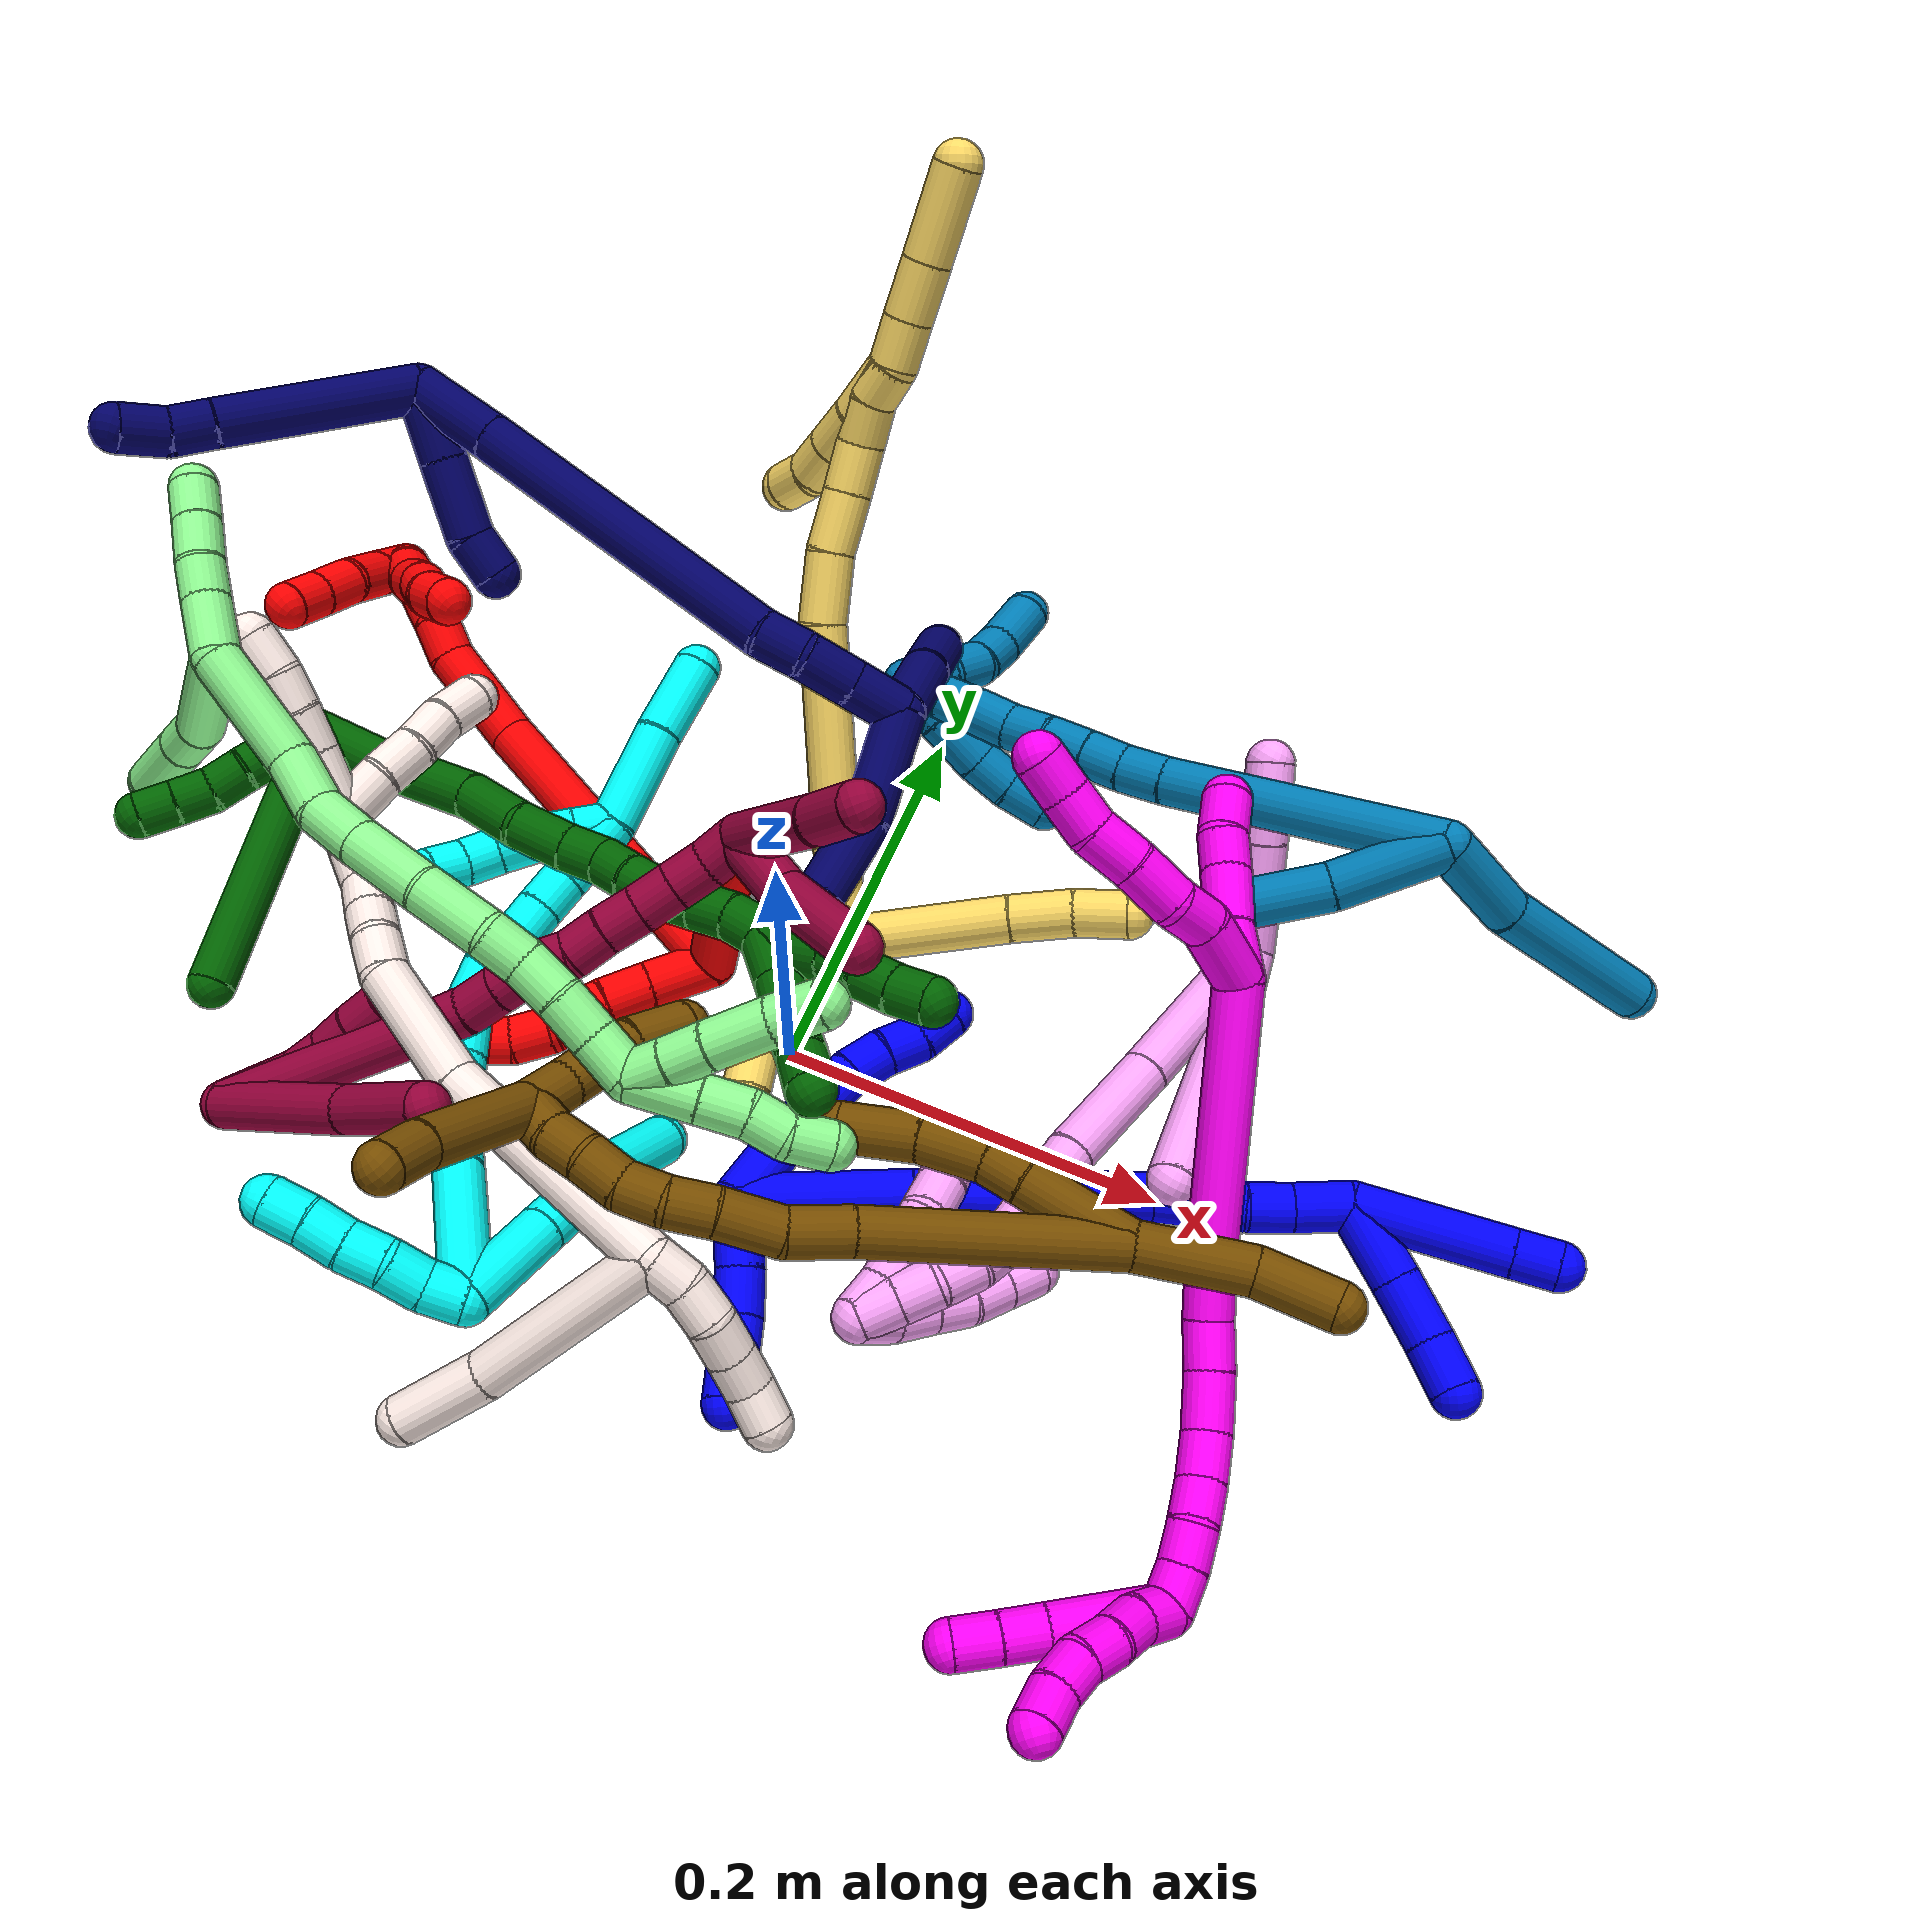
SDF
<sdf version="1.7">
 <world name="default">
  <plugin name="TubeGeneratorPlugin" filename="libtube_generator_plugin.so"/>
  <model name="photoneo_s_sensor">
   <static>1</static>
   <pose>0 0 2 1.57079 1.57079 3.14159</pose>
   <link name="link">
    <inertial><mass>0.1</mass></inertial>
    <sensor name="sensor" type="depth">
     <update_rate>30</update_rate>
     <camera>
      <horizontal_fov>1.22</horizontal_fov>
      <image><width>1920</width><height>1200</height><format>B8G8R8</format></image>
      <clip><near>0.1</near><far>4</far></clip>
      <depth_camera><output>points</output></depth_camera>
     </camera>
     <plugin name="camera_plugin" filename="libgazebo_ros_depth_camera.so">
      <baseline>0.2</baseline>
      <alwaysOn>1</alwaysOn>
      <updateRate>0.0</updateRate>
      <cameraName>camera_ir</cameraName>
      <imageTopicName>/camera/color/image_raw</imageTopicName>
      <cameraInfoTopicName>/camera/color/camera_info</cameraInfoTopicName>
      <depthImageTopicName>/camera/depth/image_raw</depthImageTopicName>
      <depthImageCameraInfoTopicName>/camera/depth/camera_info</depthImageCameraInfoTopicName>
      <pointCloudTopicName>/camera/depth/points</pointCloudTopicName>
      <frameName>fr_optical</frameName>
      <pointCloudCutoff>0.1</pointCloudCutoff>
      <pointCloudCutoffMax>2.0</pointCloudCutoffMax>
      <distortionK1>0</distortionK1>
      <distortionK2>0</distortionK2>
      <distortionK3>0</distortionK3>
      <distortionT1>0</distortionT1>
      <distortionT2>0</distortionT2>
      <CxPrime>0</CxPrime>
      <Cx>0</Cx>
      <Cy>0</Cy>
      <focalLength>0</focalLength>
      <hackBaseline>0</hackBaseline>
     </plugin>
    </sensor>
   </link>
  </model>
  <gravity>0 0 -9.8</gravity>
  <magnetic_field>6e-06 2.3e-05 -4.2e-05</magnetic_field>
  <atmosphere type="adiabatic"/>
  <physics name="default_physics" default="0" type="ode">
   <max_step_size>0.003</max_step_size>
   <real_time_factor>1</real_time_factor>
   <real_time_update_rate>1000</real_time_update_rate>
   <max_contacts>10000</max_contacts>
   <ode>
    <solver>
     <type>quick</type>
     <iters>100</iters>
     <sor>1.3</sor>
     <use_dynamic_moi_rescaling>0</use_dynamic_moi_rescaling>
    </solver>
    <constraints>
     <contact_max_correcting_vel>0</contact_max_correcting_vel>
     <contact_surface_layer>0.001</contact_surface_layer>
     <cfm>0</cfm>
     <erp>0.2</erp>
    </constraints>
   </ode>
  </physics>
  <scene><ambient>0.4 0.4 0.4 1</ambient><background>0.7 0.7 0.7 1</background><shadows>0</shadows></scene>
  <audio><device>default</device></audio>
  <spherical_coordinates>
   <surface_model>EARTH_WGS84</surface_model>
   <latitude_deg>0</latitude_deg>
   <longitude_deg>0</longitude_deg>
   <elevation>0</elevation>
   <heading_deg>0</heading_deg>
  </spherical_coordinates>
  <model name="bin">
   <static>1</static>
   <link name="bottom">
    <collision name="collision-bottom">
     <pose>0 0 -0.01 0 -0 0</pose>
     <geometry><box><size>0.8 0.6 0.02</size></box></geometry>
     <surface>
      <friction><ode><mu>100</mu><mu2>100</mu2></ode></friction>
      <contact><collide_bitmask>65535</collide_bitmask></contact>
     </surface>
    </collision>
   </link>
   <link name="west_wall">
    <collision name="collision-west_wall">
     <pose>-0.41 0 0.1 0 -0 0</pose>
     <geometry><box><size>0.02 0.6 0.2</size></box></geometry>
     <surface>
      <friction><ode><mu>100</mu><mu2>100</mu2></ode></friction>
      <contact><collide_bitmask>65535</collide_bitmask></contact>
     </surface>
    </collision>
   </link>
   <link name="east_wall">
    <collision name="collision-east_wall">
     <pose>0.41 0 0.1 0 -0 0</pose>
     <geometry><box><size>0.02 0.6 0.2</size></box></geometry>
     <surface>
      <friction><ode><mu>100</mu><mu2>100</mu2></ode></friction>
      <contact><collide_bitmask>65535</collide_bitmask></contact>
     </surface>
    </collision>
   </link>
   <link name="south_wall">
    <collision name="collision-south_wall">
     <pose>0 -0.31 0.1 0 -0 0</pose>
     <geometry><box><size>0.8 0.02 0.2</size></box></geometry>
     <surface>
      <friction><ode><mu>100</mu><mu2>100</mu2></ode></friction>
      <contact><collide_bitmask>65535</collide_bitmask></contact>
     </surface>
    </collision>
   </link>
   <link name="north_wall">
    <collision name="collision-north_wall">
     <pose>0 0.31 0.1 0 -0 0</pose>
     <geometry><box><size>0.8 0.02 0.2</size></box></geometry>
     <surface>
      <friction><ode><mu>100</mu><mu2>100</mu2></ode></friction>
      <contact><collide_bitmask>65535</collide_bitmask></contact>
     </surface>
    </collision>
   </link>
  </model>
  <model name="1">
   <static>0</static>
   <link name="1">
    <collision name="collision-cylinder-e_1_2_8">
     <pose>0.014616 0.011244 0.013679 -0.688008 0.690068 -0.256108</pose>
     <geometry><cylinder><radius>0.0125</radius><length>0.045919</length></cylinder></geometry>
     <surface>
      <friction><ode><mu>1.16</mu><mu2>1.16</mu2><slip1>0</slip1><slip2>0</slip2></ode></friction>
      <contact><ode><kp>1e+06</kp><kd>1</kd><max_vel>0</max_vel><min_depth>0.001</min_depth></ode></contact>
     </surface>
    </collision>
    <visual name="visual-cylinder-e_1_2_8">
     <pose>0.014616 0.011244 0.013679 -0.688008 0.690068 -0.256108</pose>
     <geometry><cylinder><radius>0.0125</radius><length>0.045919</length></cylinder></geometry>
     <material><ambient>0 0 1 1</ambient></material>
    </visual>
    <collision name="collision-cylinder-e_2_8_9">
     <pose>0.043731 0.030781 0.040834 -0.551676 0.741737 -0.219255</pose>
     <geometry><cylinder><radius>0.0125</radius><length>0.042924</length></cylinder></geometry>
     <surface>
      <friction><ode><mu>1.16</mu><mu2>1.16</mu2><slip1>0</slip1><slip2>0</slip2></ode></friction>
      <contact><ode><kp>1e+06</kp><kd>1</kd><max_vel>0</max_vel><min_depth>0.001</min_depth></ode></contact>
     </surface>
    </collision>
    <visual name="visual-cylinder-e_2_8_9">
     <pose>0.043731 0.030781 0.040834 -0.551676 0.741737 -0.219255</pose>
     <geometry><cylinder><radius>0.0125</radius><length>0.042924</length></cylinder></geometry>
     <material><ambient>0 0 1 1</ambient></material>
    </visual>
    <collision name="collision-cylinder-e_3_9_10">
     <pose>0.063075 0.042038 0.062973 -0.329646 0.48667 -0.082538</pose>
     <geometry><cylinder><radius>0.0125</radius><length>0.020718</length></cylinder></geometry>
     <surface>
      <friction><ode><mu>1.16</mu><mu2>1.16</mu2><slip1>0</slip1><slip2>0</slip2></ode></friction>
      <contact><ode><kp>1e+06</kp><kd>1</kd><max_vel>0</max_vel><min_depth>0.001</min_depth></ode></contact>
     </surface>
    </collision>
    <visual name="visual-cylinder-e_3_9_10">
     <pose>0.063075 0.042038 0.062973 -0.329646 0.48667 -0.082538</pose>
     <geometry><cylinder><radius>0.0125</radius><length>0.020718</length></cylinder></geometry>
     <material><ambient>0 0 1 1</ambient></material>
    </visual>
    <collision name="collision-cylinder-e_4_10_11">
     <pose>0.072833 0.04622 0.080473 -0.136974 0.503419 -0.035276</pose>
     <geometry><cylinder><radius>0.0125</radius><length>0.020368</length></cylinder></geometry>
     <surface>
      <friction><ode><mu>1.16</mu><mu2>1.16</mu2><slip1>0</slip1><slip2>0</slip2></ode></friction>
      <contact><ode><kp>1e+06</kp><kd>1</kd><max_vel>0</max_vel><min_depth>0.001</min_depth></ode></contact>
     </surface>
    </collision>
    <visual name="visual-cylinder-e_4_10_11">
     <pose>0.072833 0.04622 0.080473 -0.136974 0.503419 -0.035276</pose>
     <geometry><cylinder><radius>0.0125</radius><length>0.020368</length></cylinder></geometry>
     <material><ambient>0 0 1 1</ambient></material>
    </visual>
    <collision name="collision-cylinder-e_5_11_6">
     <pose>0.082533 0.051454 0.097163 -0.472641 0.497314 -0.122142</pose>
     <geometry><cylinder><radius>0.0125</radius><length>0.02007</length></cylinder></geometry>
     <surface>
      <friction><ode><mu>1.16</mu><mu2>1.16</mu2><slip1>0</slip1><slip2>0</slip2></ode></friction>
      <contact><ode><kp>1e+06</kp><kd>1</kd><max_vel>0</max_vel><min_depth>0.001</min_depth></ode></contact>
     </surface>
    </collision>
    <visual name="visual-cylinder-e_5_11_6">
     <pose>0.082533 0.051454 0.097163 -0.472641 0.497314 -0.122142</pose>
     <geometry><cylinder><radius>0.0125</radius><length>0.02007</length></cylinder></geometry>
     <material><ambient>0 0 1 1</ambient></material>
    </visual>
    <collision name="collision-cylinder-e_1_2_12">
     <pose>-0.008314 -0.014836 -0.000407 1.59819 -0.510645 -0.524196</pose>
     <geometry><cylinder><radius>0.0125</radius><length>0.034023</length></cylinder></geometry>
     <surface>
      <friction><ode><mu>1.16</mu><mu2>1.16</mu2><slip1>0</slip1><slip2>0</slip2></ode></friction>
      <contact><ode><kp>1e+06</kp><kd>1</kd><max_vel>0</max_vel><min_depth>0.001</min_depth></ode></contact>
     </surface>
    </collision>
    <visual name="visual-cylinder-e_1_2_12">
     <pose>-0.008314 -0.014836 -0.000407 1.59819 -0.510645 -0.524196</pose>
     <geometry><cylinder><radius>0.0125</radius><length>0.034023</length></cylinder></geometry>
     <material><ambient>0 0 1 1</ambient></material>
    </visual>
    <collision name="collision-cylinder-e_2_12_13">
     <pose>-0.022901 -0.039755 -0.001883 1.6765 -0.554008 -0.612277</pose>
     <geometry><cylinder><radius>0.0125</radius><length>0.023846</length></cylinder></geometry>
     <surface>
      <friction><ode><mu>1.16</mu><mu2>1.16</mu2><slip1>0</slip1><slip2>0</slip2></ode></friction>
      <contact><ode><kp>1e+06</kp><kd>1</kd><max_vel>0</max_vel><min_depth>0.001</min_depth></ode></contact>
     </surface>
    </collision>
    <visual name="visual-cylinder-e_2_12_13">
     <pose>-0.022901 -0.039755 -0.001883 1.6765 -0.554008 -0.612277</pose>
     <geometry><cylinder><radius>0.0125</radius><length>0.023846</length></cylinder></geometry>
     <material><ambient>0 0 1 1</ambient></material>
    </visual>
    <collision name="collision-cylinder-e_3_13_5">
     <pose>-0.043646 -0.06491 -0.005625 1.74627 -0.757384 -0.886323</pose>
     <geometry><cylinder><radius>0.0125</radius><length>0.042131</length></cylinder></geometry>
     <surface>
      <friction><ode><mu>1.16</mu><mu2>1.16</mu2><slip1>0</slip1><slip2>0</slip2></ode></friction>
      <contact><ode><kp>1e+06</kp><kd>1</kd><max_vel>0</max_vel><min_depth>0.001</min_depth></ode></contact>
     </surface>
    </collision>
    <visual name="visual-cylinder-e_3_13_5">
     <pose>-0.043646 -0.06491 -0.005625 1.74627 -0.757384 -0.886323</pose>
     <geometry><cylinder><radius>0.0125</radius><length>0.042131</length></cylinder></geometry>
     <material><ambient>0 0 1 1</ambient></material>
    </visual>
    <collision name="collision-cylinder-e_1_2_14">
     <pose>0.006854 -0.005976 0.041799 0.142007 0.16091 0.011469</pose>
     <geometry><cylinder><radius>0.0125</radius><length>0.085553</length></cylinder></geometry>
     <surface>
      <friction><ode><mu>1.16</mu><mu2>1.16</mu2><slip1>0</slip1><slip2>0</slip2></ode></friction>
      <contact><ode><kp>1e+06</kp><kd>1</kd><max_vel>0</max_vel><min_depth>0.001</min_depth></ode></contact>
     </surface>
    </collision>
    <visual name="visual-cylinder-e_1_2_14">
     <pose>0.006854 -0.005976 0.041799 0.142007 0.16091 0.011469</pose>
     <geometry><cylinder><radius>0.0125</radius><length>0.085553</length></cylinder></geometry>
     <material><ambient>0 0 1 1</ambient></material>
    </visual>
    <collision name="collision-cylinder-e_2_14_15">
     <pose>0.020891 -0.021881 0.141091 0.17102 0.12251 0.010514</pose>
     <geometry><cylinder><radius>0.0125</radius><length>0.117569</length></cylinder></geometry>
     <surface>
      <friction><ode><mu>1.16</mu><mu2>1.16</mu2><slip1>0</slip1><slip2>0</slip2></ode></friction>
      <contact><ode><kp>1e+06</kp><kd>1</kd><max_vel>0</max_vel><min_depth>0.001</min_depth></ode></contact>
     </surface>
    </collision>
    <visual name="visual-cylinder-e_2_14_15">
     <pose>0.020891 -0.021881 0.141091 0.17102 0.12251 0.010514</pose>
     <geometry><cylinder><radius>0.0125</radius><length>0.117569</length></cylinder></geometry>
     <material><ambient>0 0 1 1</ambient></material>
    </visual>
    <collision name="collision-cylinder-e_3_15_16">
     <pose>0.027355 -0.03666 0.220608 0.216717 -0.031887 -0.003469</pose>
     <geometry><cylinder><radius>0.0125</radius><length>0.045125</length></cylinder></geometry>
     <surface>
      <friction><ode><mu>1.16</mu><mu2>1.16</mu2><slip1>0</slip1><slip2>0</slip2></ode></friction>
      <contact><ode><kp>1e+06</kp><kd>1</kd><max_vel>0</max_vel><min_depth>0.001</min_depth></ode></contact>
     </surface>
    </collision>
    <visual name="visual-cylinder-e_3_15_16">
     <pose>0.027355 -0.03666 0.220608 0.216717 -0.031887 -0.003469</pose>
     <geometry><cylinder><radius>0.0125</radius><length>0.045125</length></cylinder></geometry>
     <material><ambient>0 0 1 1</ambient></material>
    </visual>
    <collision name="collision-cylinder-e_4_16_17">
     <pose>0.02829 -0.04347 0.253623 0.176606 0.147108 0.013047</pose>
     <geometry><cylinder><radius>0.0125</radius><length>0.022574</length></cylinder></geometry>
     <surface>
      <friction><ode><mu>1.16</mu><mu2>1.16</mu2><slip1>0</slip1><slip2>0</slip2></ode></friction>
      <contact><ode><kp>1e+06</kp><kd>1</kd><max_vel>0</max_vel><min_depth>0.001</min_depth></ode></contact>
     </surface>
    </collision>
    <visual name="visual-cylinder-e_4_16_17">
     <pose>0.02829 -0.04347 0.253623 0.176606 0.147108 0.013047</pose>
     <geometry><cylinder><radius>0.0125</radius><length>0.022574</length></cylinder></geometry>
     <material><ambient>0 0 1 1</ambient></material>
    </visual>
    <collision name="collision-cylinder-e_5_17_1">
     <pose>0.031026 -0.046963 0.279082 0.10539 0.074218 0.003916</pose>
     <geometry><cylinder><radius>0.0125</radius><length>0.029178</length></cylinder></geometry>
     <surface>
      <friction><ode><mu>1.16</mu><mu2>1.16</mu2><slip1>0</slip1><slip2>0</slip2></ode></friction>
      <contact><ode><kp>1e+06</kp><kd>1</kd><max_vel>0</max_vel><min_depth>0.001</min_depth></ode></contact>
     </surface>
    </collision>
    <visual name="visual-cylinder-e_5_17_1">
     <pose>0.031026 -0.046963 0.279082 0.10539 0.074218 0.003916</pose>
     <geometry><cylinder><radius>0.0125</radius><length>0.029178</length></cylinder></geometry>
     <material><ambient>0 0 1 1</ambient></material>
    </visual>
    <collision name="collision-cylinder-e_1_1_18">
     <pose>0.023995 -0.065113 0.301358 1.13161 -0.416066 -0.266519</pose>
     <geometry><cylinder><radius>0.0125</radius><length>0.04015</length></cylinder></geometry>
     <surface>
      <friction><ode><mu>1.16</mu><mu2>1.16</mu2><slip1>0</slip1><slip2>0</slip2></ode></friction>
      <contact><ode><kp>1e+06</kp><kd>1</kd><max_vel>0</max_vel><min_depth>0.001</min_depth></ode></contact>
     </surface>
    </collision>
    <visual name="visual-cylinder-e_1_1_18">
     <pose>0.023995 -0.065113 0.301358 1.13161 -0.416066 -0.266519</pose>
     <geometry><cylinder><radius>0.0125</radius><length>0.04015</length></cylinder></geometry>
     <material><ambient>0 0 1 1</ambient></material>
    </visual>
    <collision name="collision-cylinder-e_2_18_19">
     <pose>0.008693 -0.095507 0.315276 1.1533 -0.445065 -0.292244</pose>
     <geometry><cylinder><radius>0.0125</radius><length>0.03339</length></cylinder></geometry>
     <surface>
      <friction><ode><mu>1.16</mu><mu2>1.16</mu2><slip1>0</slip1><slip2>0</slip2></ode></friction>
      <contact><ode><kp>1e+06</kp><kd>1</kd><max_vel>0</max_vel><min_depth>0.001</min_depth></ode></contact>
     </surface>
    </collision>
    <visual name="visual-cylinder-e_2_18_19">
     <pose>0.008693 -0.095507 0.315276 1.1533 -0.445065 -0.292244</pose>
     <geometry><cylinder><radius>0.0125</radius><length>0.03339</length></cylinder></geometry>
     <material><ambient>0 0 1 1</ambient></material>
    </visual>
    <collision name="collision-cylinder-e_3_19_4">
     <pose>-0.006579 -0.118935 0.325442 1.173 -0.657502 -0.445828</pose>
     <geometry><cylinder><radius>0.0125</radius><length>0.02646</length></cylinder></geometry>
     <surface>
      <friction><ode><mu>1.16</mu><mu2>1.16</mu2><slip1>0</slip1><slip2>0</slip2></ode></friction>
      <contact><ode><kp>1e+06</kp><kd>1</kd><max_vel>0</max_vel><min_depth>0.001</min_depth></ode></contact>
     </surface>
    </collision>
    <visual name="visual-cylinder-e_3_19_4">
     <pose>-0.006579 -0.118935 0.325442 1.173 -0.657502 -0.445828</pose>
     <geometry><cylinder><radius>0.0125</radius><length>0.02646</length></cylinder></geometry>
     <material><ambient>0 0 1 1</ambient></material>
    </visual>
    <collision name="collision-cylinder-e_1_1_20">
     <pose>0.025533 -0.061982 0.329623 0.357828 -0.169095 -0.030651</pose>
     <geometry><cylinder><radius>0.0125</radius><length>0.078139</length></cylinder></geometry>
     <surface>
      <friction><ode><mu>1.16</mu><mu2>1.16</mu2><slip1>0</slip1><slip2>0</slip2></ode></friction>
      <contact><ode><kp>1e+06</kp><kd>1</kd><max_vel>0</max_vel><min_depth>0.001</min_depth></ode></contact>
     </surface>
    </collision>
    <visual name="visual-cylinder-e_1_1_20">
     <pose>0.025533 -0.061982 0.329623 0.357828 -0.169095 -0.030651</pose>
     <geometry><cylinder><radius>0.0125</radius><length>0.078139</length></cylinder></geometry>
     <material><ambient>0 0 1 1</ambient></material>
    </visual>
    <collision name="collision-cylinder-e_2_20_3">
     <pose>0.016956 -0.079102 0.375809 0.344811 -0.184165 -0.032158</pose>
     <geometry><cylinder><radius>0.0125</radius><length>0.021861</length></cylinder></geometry>
     <surface>
      <friction><ode><mu>1.16</mu><mu2>1.16</mu2><slip1>0</slip1><slip2>0</slip2></ode></friction>
      <contact><ode><kp>1e+06</kp><kd>1</kd><max_vel>0</max_vel><min_depth>0.001</min_depth></ode></contact>
     </surface>
    </collision>
    <visual name="visual-cylinder-e_2_20_3">
     <pose>0.016956 -0.079102 0.375809 0.344811 -0.184165 -0.032158</pose>
     <geometry><cylinder><radius>0.0125</radius><length>0.021861</length></cylinder></geometry>
     <material><ambient>0 0 1 1</ambient></material>
    </visual>
    <collision name="collision-sphere-3">
     <pose>0.014955 -0.082735 0.385923 0 -0 0</pose>
     <geometry><sphere><radius>0.0125</radius></sphere></geometry>
     <surface>
      <friction><ode><mu>1.16</mu><mu2>1.16</mu2><slip1>0</slip1><slip2>0</slip2></ode></friction>
      <contact><ode><kp>1e+06</kp><kd>1</kd><max_vel>0</max_vel><min_depth>0.001</min_depth></ode></contact>
     </surface>
    </collision>
    <visual name="visual-sphere-3">
     <pose>0.014955 -0.082735 0.385923 0 -0 0</pose>
     <geometry><sphere><radius>0.0125</radius></sphere></geometry>
     <material><ambient>0 0 1 1</ambient></material>
    </visual>
    <collision name="collision-sphere-20">
     <pose>0.018958 -0.07547 0.365696 0 -0 0</pose>
     <geometry><sphere><radius>0.0125</radius></sphere></geometry>
     <surface>
      <friction><ode><mu>1.16</mu><mu2>1.16</mu2><slip1>0</slip1><slip2>0</slip2></ode></friction>
      <contact><ode><kp>1e+06</kp><kd>1</kd><max_vel>0</max_vel><min_depth>0.001</min_depth></ode></contact>
     </surface>
    </collision>
    <visual name="visual-sphere-20">
     <pose>0.018958 -0.07547 0.365696 0 -0 0</pose>
     <geometry><sphere><radius>0.0125</radius></sphere></geometry>
     <material><ambient>0 0 1 1</ambient></material>
    </visual>
    <collision name="collision-sphere-4">
     <pose>-0.014665 -0.128589 0.329499 0 -0 0</pose>
     <geometry><sphere><radius>0.0125</radius></sphere></geometry>
     <surface>
      <friction><ode><mu>1.16</mu><mu2>1.16</mu2><slip1>0</slip1><slip2>0</slip2></ode></friction>
      <contact><ode><kp>1e+06</kp><kd>1</kd><max_vel>0</max_vel><min_depth>0.001</min_depth></ode></contact>
     </surface>
    </collision>
    <visual name="visual-sphere-4">
     <pose>-0.014665 -0.128589 0.329499 0 -0 0</pose>
     <geometry><sphere><radius>0.0125</radius></sphere></geometry>
     <material><ambient>0 0 1 1</ambient></material>
    </visual>
    <collision name="collision-sphere-6">
     <pose>0.087321 0.055469 0.105016 0 -0 0</pose>
     <geometry><sphere><radius>0.0125</radius></sphere></geometry>
     <surface>
      <friction><ode><mu>1.16</mu><mu2>1.16</mu2><slip1>0</slip1><slip2>0</slip2></ode></friction>
      <contact><ode><kp>1e+06</kp><kd>1</kd><max_vel>0</max_vel><min_depth>0.001</min_depth></ode></contact>
     </surface>
    </collision>
    <visual name="visual-sphere-6">
     <pose>0.087321 0.055469 0.105016 0 -0 0</pose>
     <geometry><sphere><radius>0.0125</radius></sphere></geometry>
     <material><ambient>0 0 1 1</ambient></material>
    </visual>
    <collision name="collision-sphere-11">
     <pose>0.077746 0.047439 0.08931 0 -0 0</pose>
     <geometry><sphere><radius>0.0125</radius></sphere></geometry>
     <surface>
      <friction><ode><mu>1.16</mu><mu2>1.16</mu2><slip1>0</slip1><slip2>0</slip2></ode></friction>
      <contact><ode><kp>1e+06</kp><kd>1</kd><max_vel>0</max_vel><min_depth>0.001</min_depth></ode></contact>
     </surface>
    </collision>
    <visual name="visual-sphere-11">
     <pose>0.077746 0.047439 0.08931 0 -0 0</pose>
     <geometry><sphere><radius>0.0125</radius></sphere></geometry>
     <material><ambient>0 0 1 1</ambient></material>
    </visual>
    <collision name="collision-sphere-10">
     <pose>0.06792 0.045002 0.071637 0 -0 0</pose>
     <geometry><sphere><radius>0.0125</radius></sphere></geometry>
     <surface>
      <friction><ode><mu>1.16</mu><mu2>1.16</mu2><slip1>0</slip1><slip2>0</slip2></ode></friction>
      <contact><ode><kp>1e+06</kp><kd>1</kd><max_vel>0</max_vel><min_depth>0.001</min_depth></ode></contact>
     </surface>
    </collision>
    <visual name="visual-sphere-10">
     <pose>0.06792 0.045002 0.071637 0 -0 0</pose>
     <geometry><sphere><radius>0.0125</radius></sphere></geometry>
     <material><ambient>0 0 1 1</ambient></material>
    </visual>
    <collision name="collision-sphere-9">
     <pose>0.05823 0.039075 0.05431 0 -0 0</pose>
     <geometry><sphere><radius>0.0125</radius></sphere></geometry>
     <surface>
      <friction><ode><mu>1.16</mu><mu2>1.16</mu2><slip1>0</slip1><slip2>0</slip2></ode></friction>
      <contact><ode><kp>1e+06</kp><kd>1</kd><max_vel>0</max_vel><min_depth>0.001</min_depth></ode></contact>
     </surface>
    </collision>
    <visual name="visual-sphere-9">
     <pose>0.05823 0.039075 0.05431 0 -0 0</pose>
     <geometry><sphere><radius>0.0125</radius></sphere></geometry>
     <material><ambient>0 0 1 1</ambient></material>
    </visual>
    <collision name="collision-sphere-2">
     <geometry><sphere><radius>0.0125</radius></sphere></geometry>
     <surface>
      <friction><ode><mu>1.16</mu><mu2>1.16</mu2><slip1>0</slip1><slip2>0</slip2></ode></friction>
      <contact><ode><kp>1e+06</kp><kd>1</kd><max_vel>0</max_vel><min_depth>0.001</min_depth></ode></contact>
     </surface>
    </collision>
    <visual name="visual-sphere-2">
     <geometry><sphere><radius>0.0125</radius></sphere></geometry>
     <material><ambient>0 0 1 1</ambient></material>
    </visual>
    <collision name="collision-sphere-19">
     <pose>0.001506 -0.109281 0.321386 0 -0 0</pose>
     <geometry><sphere><radius>0.0125</radius></sphere></geometry>
     <surface>
      <friction><ode><mu>1.16</mu><mu2>1.16</mu2><slip1>0</slip1><slip2>0</slip2></ode></friction>
      <contact><ode><kp>1e+06</kp><kd>1</kd><max_vel>0</max_vel><min_depth>0.001</min_depth></ode></contact>
     </surface>
    </collision>
    <visual name="visual-sphere-19">
     <pose>0.001506 -0.109281 0.321386 0 -0 0</pose>
     <geometry><sphere><radius>0.0125</radius></sphere></geometry>
     <material><ambient>0 0 1 1</ambient></material>
    </visual>
    <collision name="collision-sphere-8">
     <pose>0.029232 0.022487 0.027357 0 -0 0</pose>
     <geometry><sphere><radius>0.0125</radius></sphere></geometry>
     <surface>
      <friction><ode><mu>1.16</mu><mu2>1.16</mu2><slip1>0</slip1><slip2>0</slip2></ode></friction>
      <contact><ode><kp>1e+06</kp><kd>1</kd><max_vel>0</max_vel><min_depth>0.001</min_depth></ode></contact>
     </surface>
    </collision>
    <visual name="visual-sphere-8">
     <pose>0.029232 0.022487 0.027357 0 -0 0</pose>
     <geometry><sphere><radius>0.0125</radius></sphere></geometry>
     <material><ambient>0 0 1 1</ambient></material>
    </visual>
    <collision name="collision-sphere-12">
     <pose>-0.016629 -0.029672 -0.000813 0 -0 0</pose>
     <geometry><sphere><radius>0.0125</radius></sphere></geometry>
     <surface>
      <friction><ode><mu>1.16</mu><mu2>1.16</mu2><slip1>0</slip1><slip2>0</slip2></ode></friction>
      <contact><ode><kp>1e+06</kp><kd>1</kd><max_vel>0</max_vel><min_depth>0.001</min_depth></ode></contact>
     </surface>
    </collision>
    <visual name="visual-sphere-12">
     <pose>-0.016629 -0.029672 -0.000813 0 -0 0</pose>
     <geometry><sphere><radius>0.0125</radius></sphere></geometry>
     <material><ambient>0 0 1 1</ambient></material>
    </visual>
    <collision name="collision-sphere-13">
     <pose>-0.029174 -0.049838 -0.002953 0 -0 0</pose>
     <geometry><sphere><radius>0.0125</radius></sphere></geometry>
     <surface>
      <friction><ode><mu>1.16</mu><mu2>1.16</mu2><slip1>0</slip1><slip2>0</slip2></ode></friction>
      <contact><ode><kp>1e+06</kp><kd>1</kd><max_vel>0</max_vel><min_depth>0.001</min_depth></ode></contact>
     </surface>
    </collision>
    <visual name="visual-sphere-13">
     <pose>-0.029174 -0.049838 -0.002953 0 -0 0</pose>
     <geometry><sphere><radius>0.0125</radius></sphere></geometry>
     <material><ambient>0 0 1 1</ambient></material>
    </visual>
    <collision name="collision-sphere-5">
     <pose>-0.058119 -0.079981 -0.008297 0 -0 0</pose>
     <geometry><sphere><radius>0.0125</radius></sphere></geometry>
     <surface>
      <friction><ode><mu>1.16</mu><mu2>1.16</mu2><slip1>0</slip1><slip2>0</slip2></ode></friction>
      <contact><ode><kp>1e+06</kp><kd>1</kd><max_vel>0</max_vel><min_depth>0.001</min_depth></ode></contact>
     </surface>
    </collision>
    <visual name="visual-sphere-5">
     <pose>-0.058119 -0.079981 -0.008297 0 -0 0</pose>
     <geometry><sphere><radius>0.0125</radius></sphere></geometry>
     <material><ambient>0 0 1 1</ambient></material>
    </visual>
    <collision name="collision-sphere-14">
     <pose>0.013707 -0.011952 0.083598 0 -0 0</pose>
     <geometry><sphere><radius>0.0125</radius></sphere></geometry>
     <surface>
      <friction><ode><mu>1.16</mu><mu2>1.16</mu2><slip1>0</slip1><slip2>0</slip2></ode></friction>
      <contact><ode><kp>1e+06</kp><kd>1</kd><max_vel>0</max_vel><min_depth>0.001</min_depth></ode></contact>
     </surface>
    </collision>
    <visual name="visual-sphere-14">
     <pose>0.013707 -0.011952 0.083598 0 -0 0</pose>
     <geometry><sphere><radius>0.0125</radius></sphere></geometry>
     <material><ambient>0 0 1 1</ambient></material>
    </visual>
    <collision name="collision-sphere-15">
     <pose>0.028074 -0.031811 0.198584 0 -0 0</pose>
     <geometry><sphere><radius>0.0125</radius></sphere></geometry>
     <surface>
      <friction><ode><mu>1.16</mu><mu2>1.16</mu2><slip1>0</slip1><slip2>0</slip2></ode></friction>
      <contact><ode><kp>1e+06</kp><kd>1</kd><max_vel>0</max_vel><min_depth>0.001</min_depth></ode></contact>
     </surface>
    </collision>
    <visual name="visual-sphere-15">
     <pose>0.028074 -0.031811 0.198584 0 -0 0</pose>
     <geometry><sphere><radius>0.0125</radius></sphere></geometry>
     <material><ambient>0 0 1 1</ambient></material>
    </visual>
    <collision name="collision-sphere-16">
     <pose>0.026636 -0.041509 0.242631 0 -0 0</pose>
     <geometry><sphere><radius>0.0125</radius></sphere></geometry>
     <surface>
      <friction><ode><mu>1.16</mu><mu2>1.16</mu2><slip1>0</slip1><slip2>0</slip2></ode></friction>
      <contact><ode><kp>1e+06</kp><kd>1</kd><max_vel>0</max_vel><min_depth>0.001</min_depth></ode></contact>
     </surface>
    </collision>
    <visual name="visual-sphere-16">
     <pose>0.026636 -0.041509 0.242631 0 -0 0</pose>
     <geometry><sphere><radius>0.0125</radius></sphere></geometry>
     <material><ambient>0 0 1 1</ambient></material>
    </visual>
    <collision name="collision-sphere-17">
     <pose>0.029945 -0.045432 0.264614 0 -0 0</pose>
     <geometry><sphere><radius>0.0125</radius></sphere></geometry>
     <surface>
      <friction><ode><mu>1.16</mu><mu2>1.16</mu2><slip1>0</slip1><slip2>0</slip2></ode></friction>
      <contact><ode><kp>1e+06</kp><kd>1</kd><max_vel>0</max_vel><min_depth>0.001</min_depth></ode></contact>
     </surface>
    </collision>
    <visual name="visual-sphere-17">
     <pose>0.029945 -0.045432 0.264614 0 -0 0</pose>
     <geometry><sphere><radius>0.0125</radius></sphere></geometry>
     <material><ambient>0 0 1 1</ambient></material>
    </visual>
    <collision name="collision-sphere-1">
     <pose>0.032108 -0.048493 0.29355 0 -0 0</pose>
     <geometry><sphere><radius>0.0125</radius></sphere></geometry>
     <surface>
      <friction><ode><mu>1.16</mu><mu2>1.16</mu2><slip1>0</slip1><slip2>0</slip2></ode></friction>
      <contact><ode><kp>1e+06</kp><kd>1</kd><max_vel>0</max_vel><min_depth>0.001</min_depth></ode></contact>
     </surface>
    </collision>
    <visual name="visual-sphere-1">
     <pose>0.032108 -0.048493 0.29355 0 -0 0</pose>
     <geometry><sphere><radius>0.0125</radius></sphere></geometry>
     <material><ambient>0 0 1 1</ambient></material>
    </visual>
    <collision name="collision-sphere-18">
     <pose>0.015881 -0.081733 0.309166 0 -0 0</pose>
     <geometry><sphere><radius>0.0125</radius></sphere></geometry>
     <surface>
      <friction><ode><mu>1.16</mu><mu2>1.16</mu2><slip1>0</slip1><slip2>0</slip2></ode></friction>
      <contact><ode><kp>1e+06</kp><kd>1</kd><max_vel>0</max_vel><min_depth>0.001</min_depth></ode></contact>
     </surface>
    </collision>
    <visual name="visual-sphere-18">
     <pose>0.015881 -0.081733 0.309166 0 -0 0</pose>
     <geometry><sphere><radius>0.0125</radius></sphere></geometry>
     <material><ambient>0 0 1 1</ambient></material>
    </visual>
    <inertial>
     <pose>0.018124 -0.02949 0.154902 0 -0 0</pose>
     <mass>0.75</mass>
     <inertia>
      <ixx>0.000275</ixx>
      <ixy>0</ixy>
      <ixz>0</ixz>
      <iyy>0.000253</iyy>
      <iyz>0</iyz>
      <izz>8.6e-05</izz>
     </inertia>
    </inertial>
   </link>
   <pose>0.012728 -0.088197 0.021996 1.27999 0.841739 1.80288</pose>
  </model>
  <model name="2">
   <static>0</static>
   <link name="2">
    <collision name="collision-cylinder-e_1_2_8">
     <pose>-0.013865 -0.009313 0.0044 1.12946 -0.931871 -0.616855</pose>
     <geometry><cylinder><radius>0.0125</radius><length>0.034545</length></cylinder></geometry>
     <surface>
      <friction><ode><mu>1.16</mu><mu2>1.16</mu2><slip1>0</slip1><slip2>0</slip2></ode></friction>
      <contact><ode><kp>1e+06</kp><kd>1</kd><max_vel>0</max_vel><min_depth>0.001</min_depth></ode></contact>
     </surface>
    </collision>
    <visual name="visual-cylinder-e_1_2_8">
     <pose>-0.013865 -0.009313 0.0044 1.12946 -0.931871 -0.616855</pose>
     <geometry><cylinder><radius>0.0125</radius><length>0.034545</length></cylinder></geometry>
     <material><ambient>1 0 0 1</ambient></material>
    </visual>
    <collision name="collision-cylinder-e_2_8_9">
     <pose>-0.037452 -0.025308 0.011563 1.17864 -0.93125 -0.648188</pose>
     <geometry><cylinder><radius>0.0125</radius><length>0.02423</length></cylinder></geometry>
     <surface>
      <friction><ode><mu>1.16</mu><mu2>1.16</mu2><slip1>0</slip1><slip2>0</slip2></ode></friction>
      <contact><ode><kp>1e+06</kp><kd>1</kd><max_vel>0</max_vel><min_depth>0.001</min_depth></ode></contact>
     </surface>
    </collision>
    <visual name="visual-cylinder-e_2_8_9">
     <pose>-0.037452 -0.025308 0.011563 1.17864 -0.93125 -0.648188</pose>
     <geometry><cylinder><radius>0.0125</radius><length>0.02423</length></cylinder></geometry>
     <material><ambient>1 0 0 1</ambient></material>
    </visual>
    <collision name="collision-cylinder-e_3_9_10">
     <pose>-0.06021 -0.039401 0.016152 1.32924 -1.04122 -0.844465</pose>
     <geometry><cylinder><radius>0.0125</radius><length>0.030215</length></cylinder></geometry>
     <surface>
      <friction><ode><mu>1.16</mu><mu2>1.16</mu2><slip1>0</slip1><slip2>0</slip2></ode></friction>
      <contact><ode><kp>1e+06</kp><kd>1</kd><max_vel>0</max_vel><min_depth>0.001</min_depth></ode></contact>
     </surface>
    </collision>
    <visual name="visual-cylinder-e_3_9_10">
     <pose>-0.06021 -0.039401 0.016152 1.32924 -1.04122 -0.844465</pose>
     <geometry><cylinder><radius>0.0125</radius><length>0.030215</length></cylinder></geometry>
     <material><ambient>1 0 0 1</ambient></material>
    </visual>
    <collision name="collision-cylinder-e_4_10_11">
     <pose>-0.081746 -0.050942 0.022138 0.781947 -0.966821 -0.426194</pose>
     <geometry><cylinder><radius>0.0125</radius><length>0.020647</length></cylinder></geometry>
     <surface>
      <friction><ode><mu>1.16</mu><mu2>1.16</mu2><slip1>0</slip1><slip2>0</slip2></ode></friction>
      <contact><ode><kp>1e+06</kp><kd>1</kd><max_vel>0</max_vel><min_depth>0.001</min_depth></ode></contact>
     </surface>
    </collision>
    <visual name="visual-cylinder-e_4_10_11">
     <pose>-0.081746 -0.050942 0.022138 0.781947 -0.966821 -0.426194</pose>
     <geometry><cylinder><radius>0.0125</radius><length>0.020647</length></cylinder></geometry>
     <material><ambient>1 0 0 1</ambient></material>
    </visual>
    <collision name="collision-cylinder-e_5_11_12">
     <pose>-0.096646 -0.060356 0.032049 0.742873 -0.686792 -0.276773</pose>
     <geometry><cylinder><radius>0.0125</radius><length>0.020198</length></cylinder></geometry>
     <surface>
      <friction><ode><mu>1.16</mu><mu2>1.16</mu2><slip1>0</slip1><slip2>0</slip2></ode></friction>
      <contact><ode><kp>1e+06</kp><kd>1</kd><max_vel>0</max_vel><min_depth>0.001</min_depth></ode></contact>
     </surface>
    </collision>
    <visual name="visual-cylinder-e_5_11_12">
     <pose>-0.096646 -0.060356 0.032049 0.742873 -0.686792 -0.276773</pose>
     <geometry><cylinder><radius>0.0125</radius><length>0.020198</length></cylinder></geometry>
     <material><ambient>1 0 0 1</ambient></material>
    </visual>
    <collision name="collision-cylinder-e_6_12_6">
     <pose>-0.109573 -0.072032 0.042069 0.982226 -0.703767 -0.387798</pose>
     <geometry><cylinder><radius>0.0125</radius><length>0.020165</length></cylinder></geometry>
     <surface>
      <friction><ode><mu>1.16</mu><mu2>1.16</mu2><slip1>0</slip1><slip2>0</slip2></ode></friction>
      <contact><ode><kp>1e+06</kp><kd>1</kd><max_vel>0</max_vel><min_depth>0.001</min_depth></ode></contact>
     </surface>
    </collision>
    <visual name="visual-cylinder-e_6_12_6">
     <pose>-0.109573 -0.072032 0.042069 0.982226 -0.703767 -0.387798</pose>
     <geometry><cylinder><radius>0.0125</radius><length>0.020165</length></cylinder></geometry>
     <material><ambient>1 0 0 1</ambient></material>
    </visual>
    <collision name="collision-cylinder-e_1_2_13">
     <pose>0.023652 -0.020144 0.000447 1.54859 0.865202 0.848416</pose>
     <geometry><cylinder><radius>0.0125</radius><length>0.062142</length></cylinder></geometry>
     <surface>
      <friction><ode><mu>1.16</mu><mu2>1.16</mu2><slip1>0</slip1><slip2>0</slip2></ode></friction>
      <contact><ode><kp>1e+06</kp><kd>1</kd><max_vel>0</max_vel><min_depth>0.001</min_depth></ode></contact>
     </surface>
    </collision>
    <visual name="visual-cylinder-e_1_2_13">
     <pose>0.023652 -0.020144 0.000447 1.54859 0.865202 0.848416</pose>
     <geometry><cylinder><radius>0.0125</radius><length>0.062142</length></cylinder></geometry>
     <material><ambient>1 0 0 1</ambient></material>
    </visual>
    <collision name="collision-cylinder-e_2_13_5">
     <pose>0.063778 -0.049039 -0.002322 1.92312 1.05577 1.39217</pose>
     <geometry><cylinder><radius>0.0125</radius><length>0.037858</length></cylinder></geometry>
     <surface>
      <friction><ode><mu>1.16</mu><mu2>1.16</mu2><slip1>0</slip1><slip2>0</slip2></ode></friction>
      <contact><ode><kp>1e+06</kp><kd>1</kd><max_vel>0</max_vel><min_depth>0.001</min_depth></ode></contact>
     </surface>
    </collision>
    <visual name="visual-cylinder-e_2_13_5">
     <pose>0.063778 -0.049039 -0.002322 1.92312 1.05577 1.39217</pose>
     <geometry><cylinder><radius>0.0125</radius><length>0.037858</length></cylinder></geometry>
     <material><ambient>1 0 0 1</ambient></material>
    </visual>
    <collision name="collision-cylinder-e_1_2_14">
     <pose>0.001117 -0.009583 0.088933 0.107337 0.012482 0.000671</pose>
     <geometry><cylinder><radius>0.0125</radius><length>0.178909</length></cylinder></geometry>
     <surface>
      <friction><ode><mu>1.16</mu><mu2>1.16</mu2><slip1>0</slip1><slip2>0</slip2></ode></friction>
      <contact><ode><kp>1e+06</kp><kd>1</kd><max_vel>0</max_vel><min_depth>0.001</min_depth></ode></contact>
     </surface>
    </collision>
    <visual name="visual-cylinder-e_1_2_14">
     <pose>0.001117 -0.009583 0.088933 0.107337 0.012482 0.000671</pose>
     <geometry><cylinder><radius>0.0125</radius><length>0.178909</length></cylinder></geometry>
     <material><ambient>1 0 0 1</ambient></material>
    </visual>
    <collision name="collision-cylinder-e_2_14_15">
     <pose>0.005641 -0.026449 0.204955 0.262649 0.120889 0.015987</pose>
     <geometry><cylinder><radius>0.0125</radius><length>0.056516</length></cylinder></geometry>
     <surface>
      <friction><ode><mu>1.16</mu><mu2>1.16</mu2><slip1>0</slip1><slip2>0</slip2></ode></friction>
      <contact><ode><kp>1e+06</kp><kd>1</kd><max_vel>0</max_vel><min_depth>0.001</min_depth></ode></contact>
     </surface>
    </collision>
    <visual name="visual-cylinder-e_2_14_15">
     <pose>0.005641 -0.026449 0.204955 0.262649 0.120889 0.015987</pose>
     <geometry><cylinder><radius>0.0125</radius><length>0.056516</length></cylinder></geometry>
     <material><ambient>1 0 0 1</ambient></material>
    </visual>
    <collision name="collision-cylinder-e_3_15_16">
     <pose>0.013267 -0.036447 0.241961 0.26726 0.389402 0.053007</pose>
     <geometry><cylinder><radius>0.0125</radius><length>0.022226</length></cylinder></geometry>
     <surface>
      <friction><ode><mu>1.16</mu><mu2>1.16</mu2><slip1>0</slip1><slip2>0</slip2></ode></friction>
      <contact><ode><kp>1e+06</kp><kd>1</kd><max_vel>0</max_vel><min_depth>0.001</min_depth></ode></contact>
     </surface>
    </collision>
    <visual name="visual-cylinder-e_3_15_16">
     <pose>0.013267 -0.036447 0.241961 0.26726 0.389402 0.053007</pose>
     <geometry><cylinder><radius>0.0125</radius><length>0.022226</length></cylinder></geometry>
     <material><ambient>1 0 0 1</ambient></material>
    </visual>
    <collision name="collision-cylinder-e_4_16_17">
     <pose>0.019598 -0.038998 0.26211 -0.015986 0.203485 -0.001632</pose>
     <geometry><cylinder><radius>0.0125</radius><length>0.020901</length></cylinder></geometry>
     <surface>
      <friction><ode><mu>1.16</mu><mu2>1.16</mu2><slip1>0</slip1><slip2>0</slip2></ode></friction>
      <contact><ode><kp>1e+06</kp><kd>1</kd><max_vel>0</max_vel><min_depth>0.001</min_depth></ode></contact>
     </surface>
    </collision>
    <visual name="visual-cylinder-e_4_16_17">
     <pose>0.019598 -0.038998 0.26211 -0.015986 0.203485 -0.001632</pose>
     <geometry><cylinder><radius>0.0125</radius><length>0.020901</length></cylinder></geometry>
     <material><ambient>1 0 0 1</ambient></material>
    </visual>
    <collision name="collision-cylinder-e_5_17_1">
     <pose>0.023404 -0.039044 0.282931 0.019776 0.158627 0.001572</pose>
     <geometry><cylinder><radius>0.0125</radius><length>0.021448</length></cylinder></geometry>
     <surface>
      <friction><ode><mu>1.16</mu><mu2>1.16</mu2><slip1>0</slip1><slip2>0</slip2></ode></friction>
      <contact><ode><kp>1e+06</kp><kd>1</kd><max_vel>0</max_vel><min_depth>0.001</min_depth></ode></contact>
     </surface>
    </collision>
    <visual name="visual-cylinder-e_5_17_1">
     <pose>0.023404 -0.039044 0.282931 0.019776 0.158627 0.001572</pose>
     <geometry><cylinder><radius>0.0125</radius><length>0.021448</length></cylinder></geometry>
     <material><ambient>1 0 0 1</ambient></material>
    </visual>
    <collision name="collision-cylinder-e_1_1_18">
     <pose>0.026891 -0.046091 0.286445 2.37321 0.180263 0.439865</pose>
     <geometry><cylinder><radius>0.0125</radius><length>0.02</length></cylinder></geometry>
     <surface>
      <friction><ode><mu>1.16</mu><mu2>1.16</mu2><slip1>0</slip1><slip2>0</slip2></ode></friction>
      <contact><ode><kp>1e+06</kp><kd>1</kd><max_vel>0</max_vel><min_depth>0.001</min_depth></ode></contact>
     </surface>
    </collision>
    <visual name="visual-cylinder-e_1_1_18">
     <pose>0.026891 -0.046091 0.286445 2.37321 0.180263 0.439865</pose>
     <geometry><cylinder><radius>0.0125</radius><length>0.02</length></cylinder></geometry>
     <material><ambient>1 0 0 1</ambient></material>
    </visual>
    <collision name="collision-cylinder-e_2_18_19">
     <pose>0.02911 -0.057965 0.270743 2.61321 0.042599 0.157172</pose>
     <geometry><cylinder><radius>0.0125</radius><length>0.02</length></cylinder></geometry>
     <surface>
      <friction><ode><mu>1.16</mu><mu2>1.16</mu2><slip1>0</slip1><slip2>0</slip2></ode></friction>
      <contact><ode><kp>1e+06</kp><kd>1</kd><max_vel>0</max_vel><min_depth>0.001</min_depth></ode></contact>
     </surface>
    </collision>
    <visual name="visual-cylinder-e_2_18_19">
     <pose>0.02911 -0.057965 0.270743 2.61321 0.042599 0.157172</pose>
     <geometry><cylinder><radius>0.0125</radius><length>0.02</length></cylinder></geometry>
     <material><ambient>1 0 0 1</ambient></material>
    </visual>
    <collision name="collision-cylinder-e_3_19_20">
     <pose>0.032691 -0.068073 0.254095 2.57766 0.32107 1.01943</pose>
     <geometry><cylinder><radius>0.0125</radius><length>0.02</length></cylinder></geometry>
     <surface>
      <friction><ode><mu>1.16</mu><mu2>1.16</mu2><slip1>0</slip1><slip2>0</slip2></ode></friction>
      <contact><ode><kp>1e+06</kp><kd>1</kd><max_vel>0</max_vel><min_depth>0.001</min_depth></ode></contact>
     </surface>
    </collision>
    <visual name="visual-cylinder-e_3_19_20">
     <pose>0.032691 -0.068073 0.254095 2.57766 0.32107 1.01943</pose>
     <geometry><cylinder><radius>0.0125</radius><length>0.02</length></cylinder></geometry>
     <material><ambient>1 0 0 1</ambient></material>
    </visual>
    <collision name="collision-cylinder-e_4_20_21">
     <pose>0.037163 -0.078375 0.237654 2.58588 0.132017 0.455469</pose>
     <geometry><cylinder><radius>0.0125</radius><length>0.02</length></cylinder></geometry>
     <surface>
      <friction><ode><mu>1.16</mu><mu2>1.16</mu2><slip1>0</slip1><slip2>0</slip2></ode></friction>
      <contact><ode><kp>1e+06</kp><kd>1</kd><max_vel>0</max_vel><min_depth>0.001</min_depth></ode></contact>
     </surface>
    </collision>
    <visual name="visual-cylinder-e_4_20_21">
     <pose>0.037163 -0.078375 0.237654 2.58588 0.132017 0.455469</pose>
     <geometry><cylinder><radius>0.0125</radius><length>0.02</length></cylinder></geometry>
     <material><ambient>1 0 0 1</ambient></material>
    </visual>
    <collision name="collision-cylinder-e_5_21_4">
     <pose>0.041941 -0.086599 0.220341 2.81671 0.353412 1.65649</pose>
     <geometry><cylinder><radius>0.0125</radius><length>0.02</length></cylinder></geometry>
     <surface>
      <friction><ode><mu>1.16</mu><mu2>1.16</mu2><slip1>0</slip1><slip2>0</slip2></ode></friction>
      <contact><ode><kp>1e+06</kp><kd>1</kd><max_vel>0</max_vel><min_depth>0.001</min_depth></ode></contact>
     </surface>
    </collision>
    <visual name="visual-cylinder-e_5_21_4">
     <pose>0.041941 -0.086599 0.220341 2.81671 0.353412 1.65649</pose>
     <geometry><cylinder><radius>0.0125</radius><length>0.02</length></cylinder></geometry>
     <material><ambient>1 0 0 1</ambient></material>
    </visual>
    <collision name="collision-cylinder-e_1_1_22">
     <pose>0.021112 -0.051316 0.289101 1.92185 -0.30084 -0.427214</pose>
     <geometry><cylinder><radius>0.0125</radius><length>0.0269</length></cylinder></geometry>
     <surface>
      <friction><ode><mu>1.16</mu><mu2>1.16</mu2><slip1>0</slip1><slip2>0</slip2></ode></friction>
      <contact><ode><kp>1e+06</kp><kd>1</kd><max_vel>0</max_vel><min_depth>0.001</min_depth></ode></contact>
     </surface>
    </collision>
    <visual name="visual-cylinder-e_1_1_22">
     <pose>0.021112 -0.051316 0.289101 1.92185 -0.30084 -0.427214</pose>
     <geometry><cylinder><radius>0.0125</radius><length>0.0269</length></cylinder></geometry>
     <material><ambient>1 0 0 1</ambient></material>
    </visual>
    <collision name="collision-cylinder-e_2_22_23">
     <pose>0.013719 -0.076146 0.279217 1.97536 -0.240637 -0.362553</pose>
     <geometry><cylinder><radius>0.0125</radius><length>0.028601</length></cylinder></geometry>
     <surface>
      <friction><ode><mu>1.16</mu><mu2>1.16</mu2><slip1>0</slip1><slip2>0</slip2></ode></friction>
      <contact><ode><kp>1e+06</kp><kd>1</kd><max_vel>0</max_vel><min_depth>0.001</min_depth></ode></contact>
     </surface>
    </collision>
    <visual name="visual-cylinder-e_2_22_23">
     <pose>0.013719 -0.076146 0.279217 1.97536 -0.240637 -0.362553</pose>
     <geometry><cylinder><radius>0.0125</radius><length>0.028601</length></cylinder></geometry>
     <material><ambient>1 0 0 1</ambient></material>
    </visual>
    <collision name="collision-cylinder-e_3_23_24">
     <pose>0.004476 -0.098711 0.270455 1.89516 -0.513891 -0.700932</pose>
     <geometry><cylinder><radius>0.0125</radius><length>0.02374</length></cylinder></geometry>
     <surface>
      <friction><ode><mu>1.16</mu><mu2>1.16</mu2><slip1>0</slip1><slip2>0</slip2></ode></friction>
      <contact><ode><kp>1e+06</kp><kd>1</kd><max_vel>0</max_vel><min_depth>0.001</min_depth></ode></contact>
     </surface>
    </collision>
    <visual name="visual-cylinder-e_3_23_24">
     <pose>0.004476 -0.098711 0.270455 1.89516 -0.513891 -0.700932</pose>
     <geometry><cylinder><radius>0.0125</radius><length>0.02374</length></cylinder></geometry>
     <material><ambient>1 0 0 1</ambient></material>
    </visual>
    <collision name="collision-cylinder-e_4_24_3">
     <pose>-0.006153 -0.117245 0.264256 1.89183 -0.480061 -0.654252</pose>
     <geometry><cylinder><radius>0.0125</radius><length>0.020758</length></cylinder></geometry>
     <surface>
      <friction><ode><mu>1.16</mu><mu2>1.16</mu2><slip1>0</slip1><slip2>0</slip2></ode></friction>
      <contact><ode><kp>1e+06</kp><kd>1</kd><max_vel>0</max_vel><min_depth>0.001</min_depth></ode></contact>
     </surface>
    </collision>
    <visual name="visual-cylinder-e_4_24_3">
     <pose>-0.006153 -0.117245 0.264256 1.89183 -0.480061 -0.654252</pose>
     <geometry><cylinder><radius>0.0125</radius><length>0.020758</length></cylinder></geometry>
     <material><ambient>1 0 0 1</ambient></material>
    </visual>
    <collision name="collision-sphere-3">
     <pose>-0.010946 -0.125981 0.261351 0 -0 0</pose>
     <geometry><sphere><radius>0.0125</radius></sphere></geometry>
     <surface>
      <friction><ode><mu>1.16</mu><mu2>1.16</mu2><slip1>0</slip1><slip2>0</slip2></ode></friction>
      <contact><ode><kp>1e+06</kp><kd>1</kd><max_vel>0</max_vel><min_depth>0.001</min_depth></ode></contact>
     </surface>
    </collision>
    <visual name="visual-sphere-3">
     <pose>-0.010946 -0.125981 0.261351 0 -0 0</pose>
     <geometry><sphere><radius>0.0125</radius></sphere></geometry>
     <material><ambient>1 0 0 1</ambient></material>
    </visual>
    <collision name="collision-sphere-24">
     <pose>-0.001359 -0.108509 0.267161 0 -0 0</pose>
     <geometry><sphere><radius>0.0125</radius></sphere></geometry>
     <surface>
      <friction><ode><mu>1.16</mu><mu2>1.16</mu2><slip1>0</slip1><slip2>0</slip2></ode></friction>
      <contact><ode><kp>1e+06</kp><kd>1</kd><max_vel>0</max_vel><min_depth>0.001</min_depth></ode></contact>
     </surface>
    </collision>
    <visual name="visual-sphere-24">
     <pose>-0.001359 -0.108509 0.267161 0 -0 0</pose>
     <geometry><sphere><radius>0.0125</radius></sphere></geometry>
     <material><ambient>1 0 0 1</ambient></material>
    </visual>
    <collision name="collision-sphere-23">
     <pose>0.010311 -0.088914 0.27375 0 -0 0</pose>
     <geometry><sphere><radius>0.0125</radius></sphere></geometry>
     <surface>
      <friction><ode><mu>1.16</mu><mu2>1.16</mu2><slip1>0</slip1><slip2>0</slip2></ode></friction>
      <contact><ode><kp>1e+06</kp><kd>1</kd><max_vel>0</max_vel><min_depth>0.001</min_depth></ode></contact>
     </surface>
    </collision>
    <visual name="visual-sphere-23">
     <pose>0.010311 -0.088914 0.27375 0 -0 0</pose>
     <geometry><sphere><radius>0.0125</radius></sphere></geometry>
     <material><ambient>1 0 0 1</ambient></material>
    </visual>
    <collision name="collision-sphere-22">
     <pose>0.017127 -0.063379 0.284684 0 -0 0</pose>
     <geometry><sphere><radius>0.0125</radius></sphere></geometry>
     <surface>
      <friction><ode><mu>1.16</mu><mu2>1.16</mu2><slip1>0</slip1><slip2>0</slip2></ode></friction>
      <contact><ode><kp>1e+06</kp><kd>1</kd><max_vel>0</max_vel><min_depth>0.001</min_depth></ode></contact>
     </surface>
    </collision>
    <visual name="visual-sphere-22">
     <pose>0.017127 -0.063379 0.284684 0 -0 0</pose>
     <geometry><sphere><radius>0.0125</radius></sphere></geometry>
     <material><ambient>1 0 0 1</ambient></material>
    </visual>
    <collision name="collision-sphere-4">
     <pose>0.045402 -0.089594 0.21145 0 -0 0</pose>
     <geometry><sphere><radius>0.0125</radius></sphere></geometry>
     <surface>
      <friction><ode><mu>1.16</mu><mu2>1.16</mu2><slip1>0</slip1><slip2>0</slip2></ode></friction>
      <contact><ode><kp>1e+06</kp><kd>1</kd><max_vel>0</max_vel><min_depth>0.001</min_depth></ode></contact>
     </surface>
    </collision>
    <visual name="visual-sphere-4">
     <pose>0.045402 -0.089594 0.21145 0 -0 0</pose>
     <geometry><sphere><radius>0.0125</radius></sphere></geometry>
     <material><ambient>1 0 0 1</ambient></material>
    </visual>
    <collision name="collision-sphere-21">
     <pose>0.03848 -0.083605 0.229232 0 -0 0</pose>
     <geometry><sphere><radius>0.0125</radius></sphere></geometry>
     <surface>
      <friction><ode><mu>1.16</mu><mu2>1.16</mu2><slip1>0</slip1><slip2>0</slip2></ode></friction>
      <contact><ode><kp>1e+06</kp><kd>1</kd><max_vel>0</max_vel><min_depth>0.001</min_depth></ode></contact>
     </surface>
    </collision>
    <visual name="visual-sphere-21">
     <pose>0.03848 -0.083605 0.229232 0 -0 0</pose>
     <geometry><sphere><radius>0.0125</radius></sphere></geometry>
     <material><ambient>1 0 0 1</ambient></material>
    </visual>
    <collision name="collision-sphere-20">
     <pose>0.035847 -0.073145 0.246075 0 -0 0</pose>
     <geometry><sphere><radius>0.0125</radius></sphere></geometry>
     <surface>
      <friction><ode><mu>1.16</mu><mu2>1.16</mu2><slip1>0</slip1><slip2>0</slip2></ode></friction>
      <contact><ode><kp>1e+06</kp><kd>1</kd><max_vel>0</max_vel><min_depth>0.001</min_depth></ode></contact>
     </surface>
    </collision>
    <visual name="visual-sphere-20">
     <pose>0.035847 -0.073145 0.246075 0 -0 0</pose>
     <geometry><sphere><radius>0.0125</radius></sphere></geometry>
     <material><ambient>1 0 0 1</ambient></material>
    </visual>
    <collision name="collision-sphere-12">
     <pose>-0.103049 -0.065638 0.037801 0 -0 0</pose>
     <geometry><sphere><radius>0.0125</radius></sphere></geometry>
     <surface>
      <friction><ode><mu>1.16</mu><mu2>1.16</mu2><slip1>0</slip1><slip2>0</slip2></ode></friction>
      <contact><ode><kp>1e+06</kp><kd>1</kd><max_vel>0</max_vel><min_depth>0.001</min_depth></ode></contact>
     </surface>
    </collision>
    <visual name="visual-sphere-12">
     <pose>-0.103049 -0.065638 0.037801 0 -0 0</pose>
     <geometry><sphere><radius>0.0125</radius></sphere></geometry>
     <material><ambient>1 0 0 1</ambient></material>
    </visual>
    <collision name="collision-sphere-11">
     <pose>-0.090243 -0.055073 0.026297 0 -0 0</pose>
     <geometry><sphere><radius>0.0125</radius></sphere></geometry>
     <surface>
      <friction><ode><mu>1.16</mu><mu2>1.16</mu2><slip1>0</slip1><slip2>0</slip2></ode></friction>
      <contact><ode><kp>1e+06</kp><kd>1</kd><max_vel>0</max_vel><min_depth>0.001</min_depth></ode></contact>
     </surface>
    </collision>
    <visual name="visual-sphere-11">
     <pose>-0.090243 -0.055073 0.026297 0 -0 0</pose>
     <geometry><sphere><radius>0.0125</radius></sphere></geometry>
     <material><ambient>1 0 0 1</ambient></material>
    </visual>
    <collision name="collision-sphere-10">
     <pose>-0.073249 -0.046811 0.017978 0 -0 0</pose>
     <geometry><sphere><radius>0.0125</radius></sphere></geometry>
     <surface>
      <friction><ode><mu>1.16</mu><mu2>1.16</mu2><slip1>0</slip1><slip2>0</slip2></ode></friction>
      <contact><ode><kp>1e+06</kp><kd>1</kd><max_vel>0</max_vel><min_depth>0.001</min_depth></ode></contact>
     </surface>
    </collision>
    <visual name="visual-sphere-10">
     <pose>-0.073249 -0.046811 0.017978 0 -0 0</pose>
     <geometry><sphere><radius>0.0125</radius></sphere></geometry>
     <material><ambient>1 0 0 1</ambient></material>
    </visual>
    <collision name="collision-sphere-9">
     <pose>-0.047172 -0.03199 0.014326 0 -0 0</pose>
     <geometry><sphere><radius>0.0125</radius></sphere></geometry>
     <surface>
      <friction><ode><mu>1.16</mu><mu2>1.16</mu2><slip1>0</slip1><slip2>0</slip2></ode></friction>
      <contact><ode><kp>1e+06</kp><kd>1</kd><max_vel>0</max_vel><min_depth>0.001</min_depth></ode></contact>
     </surface>
    </collision>
    <visual name="visual-sphere-9">
     <pose>-0.047172 -0.03199 0.014326 0 -0 0</pose>
     <geometry><sphere><radius>0.0125</radius></sphere></geometry>
     <material><ambient>1 0 0 1</ambient></material>
    </visual>
    <collision name="collision-sphere-2">
     <geometry><sphere><radius>0.0125</radius></sphere></geometry>
     <surface>
      <friction><ode><mu>1.16</mu><mu2>1.16</mu2><slip1>0</slip1><slip2>0</slip2></ode></friction>
      <contact><ode><kp>1e+06</kp><kd>1</kd><max_vel>0</max_vel><min_depth>0.001</min_depth></ode></contact>
     </surface>
    </collision>
    <visual name="visual-sphere-2">
     <geometry><sphere><radius>0.0125</radius></sphere></geometry>
     <material><ambient>1 0 0 1</ambient></material>
    </visual>
    <collision name="collision-sphere-19">
     <pose>0.029536 -0.063001 0.262114 0 -0 0</pose>
     <geometry><sphere><radius>0.0125</radius></sphere></geometry>
     <surface>
      <friction><ode><mu>1.16</mu><mu2>1.16</mu2><slip1>0</slip1><slip2>0</slip2></ode></friction>
      <contact><ode><kp>1e+06</kp><kd>1</kd><max_vel>0</max_vel><min_depth>0.001</min_depth></ode></contact>
     </surface>
    </collision>
    <visual name="visual-sphere-19">
     <pose>0.029536 -0.063001 0.262114 0 -0 0</pose>
     <geometry><sphere><radius>0.0125</radius></sphere></geometry>
     <material><ambient>1 0 0 1</ambient></material>
    </visual>
    <collision name="collision-sphere-8">
     <pose>-0.027731 -0.018627 0.008799 0 -0 0</pose>
     <geometry><sphere><radius>0.0125</radius></sphere></geometry>
     <surface>
      <friction><ode><mu>1.16</mu><mu2>1.16</mu2><slip1>0</slip1><slip2>0</slip2></ode></friction>
      <contact><ode><kp>1e+06</kp><kd>1</kd><max_vel>0</max_vel><min_depth>0.001</min_depth></ode></contact>
     </surface>
    </collision>
    <visual name="visual-sphere-8">
     <pose>-0.027731 -0.018627 0.008799 0 -0 0</pose>
     <geometry><sphere><radius>0.0125</radius></sphere></geometry>
     <material><ambient>1 0 0 1</ambient></material>
    </visual>
    <collision name="collision-sphere-6">
     <pose>-0.116098 -0.078425 0.046336 0 -0 0</pose>
     <geometry><sphere><radius>0.0125</radius></sphere></geometry>
     <surface>
      <friction><ode><mu>1.16</mu><mu2>1.16</mu2><slip1>0</slip1><slip2>0</slip2></ode></friction>
      <contact><ode><kp>1e+06</kp><kd>1</kd><max_vel>0</max_vel><min_depth>0.001</min_depth></ode></contact>
     </surface>
    </collision>
    <visual name="visual-sphere-6">
     <pose>-0.116098 -0.078425 0.046336 0 -0 0</pose>
     <geometry><sphere><radius>0.0125</radius></sphere></geometry>
     <material><ambient>1 0 0 1</ambient></material>
    </visual>
    <collision name="collision-sphere-13">
     <pose>0.047304 -0.040288 0.000895 0 -0 0</pose>
     <geometry><sphere><radius>0.0125</radius></sphere></geometry>
     <surface>
      <friction><ode><mu>1.16</mu><mu2>1.16</mu2><slip1>0</slip1><slip2>0</slip2></ode></friction>
      <contact><ode><kp>1e+06</kp><kd>1</kd><max_vel>0</max_vel><min_depth>0.001</min_depth></ode></contact>
     </surface>
    </collision>
    <visual name="visual-sphere-13">
     <pose>0.047304 -0.040288 0.000895 0 -0 0</pose>
     <geometry><sphere><radius>0.0125</radius></sphere></geometry>
     <material><ambient>1 0 0 1</ambient></material>
    </visual>
    <collision name="collision-sphere-5">
     <pose>0.080251 -0.05779 -0.00554 0 -0 0</pose>
     <geometry><sphere><radius>0.0125</radius></sphere></geometry>
     <surface>
      <friction><ode><mu>1.16</mu><mu2>1.16</mu2><slip1>0</slip1><slip2>0</slip2></ode></friction>
      <contact><ode><kp>1e+06</kp><kd>1</kd><max_vel>0</max_vel><min_depth>0.001</min_depth></ode></contact>
     </surface>
    </collision>
    <visual name="visual-sphere-5">
     <pose>0.080251 -0.05779 -0.00554 0 -0 0</pose>
     <geometry><sphere><radius>0.0125</radius></sphere></geometry>
     <material><ambient>1 0 0 1</ambient></material>
    </visual>
    <collision name="collision-sphere-14">
     <pose>0.002233 -0.019165 0.177866 0 -0 0</pose>
     <geometry><sphere><radius>0.0125</radius></sphere></geometry>
     <surface>
      <friction><ode><mu>1.16</mu><mu2>1.16</mu2><slip1>0</slip1><slip2>0</slip2></ode></friction>
      <contact><ode><kp>1e+06</kp><kd>1</kd><max_vel>0</max_vel><min_depth>0.001</min_depth></ode></contact>
     </surface>
    </collision>
    <visual name="visual-sphere-14">
     <pose>0.002233 -0.019165 0.177866 0 -0 0</pose>
     <geometry><sphere><radius>0.0125</radius></sphere></geometry>
     <material><ambient>1 0 0 1</ambient></material>
    </visual>
    <collision name="collision-sphere-15">
     <pose>0.009049 -0.033732 0.232045 0 -0 0</pose>
     <geometry><sphere><radius>0.0125</radius></sphere></geometry>
     <surface>
      <friction><ode><mu>1.16</mu><mu2>1.16</mu2><slip1>0</slip1><slip2>0</slip2></ode></friction>
      <contact><ode><kp>1e+06</kp><kd>1</kd><max_vel>0</max_vel><min_depth>0.001</min_depth></ode></contact>
     </surface>
    </collision>
    <visual name="visual-sphere-15">
     <pose>0.009049 -0.033732 0.232045 0 -0 0</pose>
     <geometry><sphere><radius>0.0125</radius></sphere></geometry>
     <material><ambient>1 0 0 1</ambient></material>
    </visual>
    <collision name="collision-sphere-16">
     <pose>0.017486 -0.039162 0.251877 0 -0 0</pose>
     <geometry><sphere><radius>0.0125</radius></sphere></geometry>
     <surface>
      <friction><ode><mu>1.16</mu><mu2>1.16</mu2><slip1>0</slip1><slip2>0</slip2></ode></friction>
      <contact><ode><kp>1e+06</kp><kd>1</kd><max_vel>0</max_vel><min_depth>0.001</min_depth></ode></contact>
     </surface>
    </collision>
    <visual name="visual-sphere-16">
     <pose>0.017486 -0.039162 0.251877 0 -0 0</pose>
     <geometry><sphere><radius>0.0125</radius></sphere></geometry>
     <material><ambient>1 0 0 1</ambient></material>
    </visual>
    <collision name="collision-sphere-17">
     <pose>0.02171 -0.038835 0.272344 0 -0 0</pose>
     <geometry><sphere><radius>0.0125</radius></sphere></geometry>
     <surface>
      <friction><ode><mu>1.16</mu><mu2>1.16</mu2><slip1>0</slip1><slip2>0</slip2></ode></friction>
      <contact><ode><kp>1e+06</kp><kd>1</kd><max_vel>0</max_vel><min_depth>0.001</min_depth></ode></contact>
     </surface>
    </collision>
    <visual name="visual-sphere-17">
     <pose>0.02171 -0.038835 0.272344 0 -0 0</pose>
     <geometry><sphere><radius>0.0125</radius></sphere></geometry>
     <material><ambient>1 0 0 1</ambient></material>
    </visual>
    <collision name="collision-sphere-1">
     <pose>0.025098 -0.039254 0.293519 0 -0 0</pose>
     <geometry><sphere><radius>0.0125</radius></sphere></geometry>
     <surface>
      <friction><ode><mu>1.16</mu><mu2>1.16</mu2><slip1>0</slip1><slip2>0</slip2></ode></friction>
      <contact><ode><kp>1e+06</kp><kd>1</kd><max_vel>0</max_vel><min_depth>0.001</min_depth></ode></contact>
     </surface>
    </collision>
    <visual name="visual-sphere-1">
     <pose>0.025098 -0.039254 0.293519 0 -0 0</pose>
     <geometry><sphere><radius>0.0125</radius></sphere></geometry>
     <material><ambient>1 0 0 1</ambient></material>
    </visual>
    <collision name="collision-sphere-18">
     <pose>0.028684 -0.052928 0.279371 0 -0 0</pose>
     <geometry><sphere><radius>0.0125</radius></sphere></geometry>
     <surface>
      <friction><ode><mu>1.16</mu><mu2>1.16</mu2><slip1>0</slip1><slip2>0</slip2></ode></friction>
      <contact><ode><kp>1e+06</kp><kd>1</kd><max_vel>0</max_vel><min_depth>0.001</min_depth></ode></contact>
     </surface>
    </collision>
    <visual name="visual-sphere-18">
     <pose>0.028684 -0.052928 0.279371 0 -0 0</pose>
     <geometry><sphere><radius>0.0125</radius></sphere></geometry>
     <material><ambient>1 0 0 1</ambient></material>
    </visual>
    <inertial>
     <pose>0.001132 -0.039609 0.133715 0 -0 0</pose>
     <mass>0.75</mass>
     <inertia>
      <ixx>0.000543</ixx>
      <ixy>0</ixy>
      <ixz>0</ixz>
      <iyy>0.000513</iyy>
      <iyz>0</iyz>
      <izz>9.3e-05</izz>
     </inertia>
    </inertial>
   </link>
   <pose>-0.055546 0.025393 0.013786 -1.69592 -0.545146 1.11805</pose>
  </model>
  <model name="3">
   <static>0</static>
   <link name="3">
    <collision name="collision-cylinder-e_1_2_8">
     <pose>-0.021299 0.007018 -0.014025 -2.67764 -0.936127 2.26731</pose>
     <geometry><cylinder><radius>0.0125</radius><length>0.0529</length></cylinder></geometry>
     <surface>
      <friction><ode><mu>1.16</mu><mu2>1.16</mu2><slip1>0</slip1><slip2>0</slip2></ode></friction>
      <contact><ode><kp>1e+06</kp><kd>1</kd><max_vel>0</max_vel><min_depth>0.001</min_depth></ode></contact>
     </surface>
    </collision>
    <visual name="visual-cylinder-e_1_2_8">
     <pose>-0.021299 0.007018 -0.014025 -2.67764 -0.936127 2.26731</pose>
     <geometry><cylinder><radius>0.0125</radius><length>0.0529</length></cylinder></geometry>
     <material><ambient>0.003922 1 0.996078 1</ambient></material>
    </visual>
    <collision name="collision-cylinder-e_2_8_9">
     <pose>-0.06267 0.020612 -0.041365 -2.68287 -0.933762 2.27406</pose>
     <geometry><cylinder><radius>0.0125</radius><length>0.049937</length></cylinder></geometry>
     <surface>
      <friction><ode><mu>1.16</mu><mu2>1.16</mu2><slip1>0</slip1><slip2>0</slip2></ode></friction>
      <contact><ode><kp>1e+06</kp><kd>1</kd><max_vel>0</max_vel><min_depth>0.001</min_depth></ode></contact>
     </surface>
    </collision>
    <visual name="visual-cylinder-e_2_8_9">
     <pose>-0.06267 0.020612 -0.041365 -2.68287 -0.933762 2.27406</pose>
     <geometry><cylinder><radius>0.0125</radius><length>0.049937</length></cylinder></geometry>
     <material><ambient>0.003922 1 0.996078 1</ambient></material>
    </visual>
    <collision name="collision-cylinder-e_3_9_6">
     <pose>-0.101076 0.02553 -0.069418 3.02952 -0.890733 -2.90763</pose>
     <geometry><cylinder><radius>0.0125</radius><length>0.047164</length></cylinder></geometry>
     <surface>
      <friction><ode><mu>1.16</mu><mu2>1.16</mu2><slip1>0</slip1><slip2>0</slip2></ode></friction>
      <contact><ode><kp>1e+06</kp><kd>1</kd><max_vel>0</max_vel><min_depth>0.001</min_depth></ode></contact>
     </surface>
    </collision>
    <visual name="visual-cylinder-e_3_9_6">
     <pose>-0.101076 0.02553 -0.069418 3.02952 -0.890733 -2.90763</pose>
     <geometry><cylinder><radius>0.0125</radius><length>0.047164</length></cylinder></geometry>
     <material><ambient>0.003922 1 0.996078 1</ambient></material>
    </visual>
    <collision name="collision-cylinder-e_1_2_10">
     <pose>-0.001745 -0.001861 0.009669 0.190127 -0.175357 -0.016763</pose>
     <geometry><cylinder><radius>0.0125</radius><length>0.02</length></cylinder></geometry>
     <surface>
      <friction><ode><mu>1.16</mu><mu2>1.16</mu2><slip1>0</slip1><slip2>0</slip2></ode></friction>
      <contact><ode><kp>1e+06</kp><kd>1</kd><max_vel>0</max_vel><min_depth>0.001</min_depth></ode></contact>
     </surface>
    </collision>
    <visual name="visual-cylinder-e_1_2_10">
     <pose>-0.001745 -0.001861 0.009669 0.190127 -0.175357 -0.016763</pose>
     <geometry><cylinder><radius>0.0125</radius><length>0.02</length></cylinder></geometry>
     <material><ambient>0.003922 1 0.996078 1</ambient></material>
    </visual>
    <collision name="collision-cylinder-e_2_10_11">
     <pose>-0.005483 -0.003011 0.029112 -0.072587 -0.200697 0.007312</pose>
     <geometry><cylinder><radius>0.0125</radius><length>0.02</length></cylinder></geometry>
     <surface>
      <friction><ode><mu>1.16</mu><mu2>1.16</mu2><slip1>0</slip1><slip2>0</slip2></ode></friction>
      <contact><ode><kp>1e+06</kp><kd>1</kd><max_vel>0</max_vel><min_depth>0.001</min_depth></ode></contact>
     </surface>
    </collision>
    <visual name="visual-cylinder-e_2_10_11">
     <pose>-0.005483 -0.003011 0.029112 -0.072587 -0.200697 0.007312</pose>
     <geometry><cylinder><radius>0.0125</radius><length>0.02</length></cylinder></geometry>
     <material><ambient>0.003922 1 0.996078 1</ambient></material>
    </visual>
    <collision name="collision-cylinder-e_3_11_12">
     <pose>-0.010599 -0.004015 0.048229 0.18144 -0.317589 -0.029134</pose>
     <geometry><cylinder><radius>0.0125</radius><length>0.02</length></cylinder></geometry>
     <surface>
      <friction><ode><mu>1.16</mu><mu2>1.16</mu2><slip1>0</slip1><slip2>0</slip2></ode></friction>
      <contact><ode><kp>1e+06</kp><kd>1</kd><max_vel>0</max_vel><min_depth>0.001</min_depth></ode></contact>
     </surface>
    </collision>
    <visual name="visual-cylinder-e_3_11_12">
     <pose>-0.010599 -0.004015 0.048229 0.18144 -0.317589 -0.029134</pose>
     <geometry><cylinder><radius>0.0125</radius><length>0.02</length></cylinder></geometry>
     <material><ambient>0.003922 1 0.996078 1</ambient></material>
    </visual>
    <collision name="collision-cylinder-e_4_12_13">
     <pose>-0.017606 -0.006368 0.066766 0.069423 -0.398931 -0.014039</pose>
     <geometry><cylinder><radius>0.0125</radius><length>0.02</length></cylinder></geometry>
     <surface>
      <friction><ode><mu>1.16</mu><mu2>1.16</mu2><slip1>0</slip1><slip2>0</slip2></ode></friction>
      <contact><ode><kp>1e+06</kp><kd>1</kd><max_vel>0</max_vel><min_depth>0.001</min_depth></ode></contact>
     </surface>
    </collision>
    <visual name="visual-cylinder-e_4_12_13">
     <pose>-0.017606 -0.006368 0.066766 0.069423 -0.398931 -0.014039</pose>
     <geometry><cylinder><radius>0.0125</radius><length>0.02</length></cylinder></geometry>
     <material><ambient>0.003922 1 0.996078 1</ambient></material>
    </visual>
    <collision name="collision-cylinder-e_5_13_5">
     <pose>-0.025214 -0.008717 0.08508 0.185283 -0.381566 -0.035883</pose>
     <geometry><cylinder><radius>0.0125</radius><length>0.02</length></cylinder></geometry>
     <surface>
      <friction><ode><mu>1.16</mu><mu2>1.16</mu2><slip1>0</slip1><slip2>0</slip2></ode></friction>
      <contact><ode><kp>1e+06</kp><kd>1</kd><max_vel>0</max_vel><min_depth>0.001</min_depth></ode></contact>
     </surface>
    </collision>
    <visual name="visual-cylinder-e_5_13_5">
     <pose>-0.025214 -0.008717 0.08508 0.185283 -0.381566 -0.035883</pose>
     <geometry><cylinder><radius>0.0125</radius><length>0.02</length></cylinder></geometry>
     <material><ambient>0.003922 1 0.996078 1</ambient></material>
    </visual>
    <collision name="collision-cylinder-e_1_2_14">
     <pose>-0.036534 0.001418 0.005815 -0.239123 -1.40842 0.203406</pose>
     <geometry><cylinder><radius>0.0125</radius><length>0.074043</length></cylinder></geometry>
     <surface>
      <friction><ode><mu>1.16</mu><mu2>1.16</mu2><slip1>0</slip1><slip2>0</slip2></ode></friction>
      <contact><ode><kp>1e+06</kp><kd>1</kd><max_vel>0</max_vel><min_depth>0.001</min_depth></ode></contact>
     </surface>
    </collision>
    <visual name="visual-cylinder-e_1_2_14">
     <pose>-0.036534 0.001418 0.005815 -0.239123 -1.40842 0.203406</pose>
     <geometry><cylinder><radius>0.0125</radius><length>0.074043</length></cylinder></geometry>
     <material><ambient>0.003922 1 0.996078 1</ambient></material>
    </visual>
    <collision name="collision-cylinder-e_2_14_15">
     <pose>-0.097315 0.001928 0.014766 0.281425 -1.43693 -0.246448</pose>
     <geometry><cylinder><radius>0.0125</radius><length>0.048932</length></cylinder></geometry>
     <surface>
      <friction><ode><mu>1.16</mu><mu2>1.16</mu2><slip1>0</slip1><slip2>0</slip2></ode></friction>
      <contact><ode><kp>1e+06</kp><kd>1</kd><max_vel>0</max_vel><min_depth>0.001</min_depth></ode></contact>
     </surface>
    </collision>
    <visual name="visual-cylinder-e_2_14_15">
     <pose>-0.097315 0.001928 0.014766 0.281425 -1.43693 -0.246448</pose>
     <geometry><cylinder><radius>0.0125</radius><length>0.048932</length></cylinder></geometry>
     <material><ambient>0.003922 1 0.996078 1</ambient></material>
    </visual>
    <collision name="collision-cylinder-e_3_15_16">
     <pose>-0.133257 0.00347 0.017734 -1.63972 -1.36393 1.43187</pose>
     <geometry><cylinder><radius>0.0125</radius><length>0.023898</length></cylinder></geometry>
     <surface>
      <friction><ode><mu>1.16</mu><mu2>1.16</mu2><slip1>0</slip1><slip2>0</slip2></ode></friction>
      <contact><ode><kp>1e+06</kp><kd>1</kd><max_vel>0</max_vel><min_depth>0.001</min_depth></ode></contact>
     </surface>
    </collision>
    <visual name="visual-cylinder-e_3_15_16">
     <pose>-0.133257 0.00347 0.017734 -1.63972 -1.36393 1.43187</pose>
     <geometry><cylinder><radius>0.0125</radius><length>0.023898</length></cylinder></geometry>
     <material><ambient>0.003922 1 0.996078 1</ambient></material>
    </visual>
    <collision name="collision-cylinder-e_4_16_17">
     <pose>-0.158813 0.011688 0.019407 -1.26181 -1.15886 0.891803</pose>
     <geometry><cylinder><radius>0.0125</radius><length>0.030255</length></cylinder></geometry>
     <surface>
      <friction><ode><mu>1.16</mu><mu2>1.16</mu2><slip1>0</slip1><slip2>0</slip2></ode></friction>
      <contact><ode><kp>1e+06</kp><kd>1</kd><max_vel>0</max_vel><min_depth>0.001</min_depth></ode></contact>
     </surface>
    </collision>
    <visual name="visual-cylinder-e_4_16_17">
     <pose>-0.158813 0.011688 0.019407 -1.26181 -1.15886 0.891803</pose>
     <geometry><cylinder><radius>0.0125</radius><length>0.030255</length></cylinder></geometry>
     <material><ambient>0.003922 1 0.996078 1</ambient></material>
    </visual>
    <collision name="collision-cylinder-e_5_17_18">
     <pose>-0.181645 0.02358 0.019923 -1.78412 -0.96121 1.1477</pose>
     <geometry><cylinder><radius>0.0125</radius><length>0.021881</length></cylinder></geometry>
     <surface>
      <friction><ode><mu>1.16</mu><mu2>1.16</mu2><slip1>0</slip1><slip2>0</slip2></ode></friction>
      <contact><ode><kp>1e+06</kp><kd>1</kd><max_vel>0</max_vel><min_depth>0.001</min_depth></ode></contact>
     </surface>
    </collision>
    <visual name="visual-cylinder-e_5_17_18">
     <pose>-0.181645 0.02358 0.019923 -1.78412 -0.96121 1.1477</pose>
     <geometry><cylinder><radius>0.0125</radius><length>0.021881</length></cylinder></geometry>
     <material><ambient>0.003922 1 0.996078 1</ambient></material>
    </visual>
    <collision name="collision-cylinder-e_6_18_19">
     <pose>-0.197404 0.036248 0.014328 -2.14863 -0.715207 1.20764</pose>
     <geometry><cylinder><radius>0.0125</radius><length>0.020705</length></cylinder></geometry>
     <surface>
      <friction><ode><mu>1.16</mu><mu2>1.16</mu2><slip1>0</slip1><slip2>0</slip2></ode></friction>
      <contact><ode><kp>1e+06</kp><kd>1</kd><max_vel>0</max_vel><min_depth>0.001</min_depth></ode></contact>
     </surface>
    </collision>
    <visual name="visual-cylinder-e_6_18_19">
     <pose>-0.197404 0.036248 0.014328 -2.14863 -0.715207 1.20764</pose>
     <geometry><cylinder><radius>0.0125</radius><length>0.020705</length></cylinder></geometry>
     <material><ambient>0.003922 1 0.996078 1</ambient></material>
    </visual>
    <collision name="collision-cylinder-e_7_19_20">
     <pose>-0.211633 0.048752 0.00659 -2.09813 -0.823573 1.29943</pose>
     <geometry><cylinder><radius>0.0125</radius><length>0.020286</length></cylinder></geometry>
     <surface>
      <friction><ode><mu>1.16</mu><mu2>1.16</mu2><slip1>0</slip1><slip2>0</slip2></ode></friction>
      <contact><ode><kp>1e+06</kp><kd>1</kd><max_vel>0</max_vel><min_depth>0.001</min_depth></ode></contact>
     </surface>
    </collision>
    <visual name="visual-cylinder-e_7_19_20">
     <pose>-0.211633 0.048752 0.00659 -2.09813 -0.823573 1.29943</pose>
     <geometry><cylinder><radius>0.0125</radius><length>0.020286</length></cylinder></geometry>
     <material><ambient>0.003922 1 0.996078 1</ambient></material>
    </visual>
    <collision name="collision-cylinder-e_8_20_21">
     <pose>-0.226177 0.060732 -0.000521 -2.11463 -0.789896 1.27308</pose>
     <geometry><cylinder><radius>0.0125</radius><length>0.02</length></cylinder></geometry>
     <surface>
      <friction><ode><mu>1.16</mu><mu2>1.16</mu2><slip1>0</slip1><slip2>0</slip2></ode></friction>
      <contact><ode><kp>1e+06</kp><kd>1</kd><max_vel>0</max_vel><min_depth>0.001</min_depth></ode></contact>
     </surface>
    </collision>
    <visual name="visual-cylinder-e_8_20_21">
     <pose>-0.226177 0.060732 -0.000521 -2.11463 -0.789896 1.27308</pose>
     <geometry><cylinder><radius>0.0125</radius><length>0.02</length></cylinder></geometry>
     <material><ambient>0.003922 1 0.996078 1</ambient></material>
    </visual>
    <collision name="collision-cylinder-e_9_21_22">
     <pose>-0.240285 0.072763 -0.008016 -2.14102 -0.776152 1.28419</pose>
     <geometry><cylinder><radius>0.0125</radius><length>0.02</length></cylinder></geometry>
     <surface>
      <friction><ode><mu>1.16</mu><mu2>1.16</mu2><slip1>0</slip1><slip2>0</slip2></ode></friction>
      <contact><ode><kp>1e+06</kp><kd>1</kd><max_vel>0</max_vel><min_depth>0.001</min_depth></ode></contact>
     </surface>
    </collision>
    <visual name="visual-cylinder-e_9_21_22">
     <pose>-0.240285 0.072763 -0.008016 -2.14102 -0.776152 1.28419</pose>
     <geometry><cylinder><radius>0.0125</radius><length>0.02</length></cylinder></geometry>
     <material><ambient>0.003922 1 0.996078 1</ambient></material>
    </visual>
    <collision name="collision-cylinder-e_10_22_1">
     <pose>-0.254042 0.085261 -0.015375 -2.06612 -0.74113 1.15483</pose>
     <geometry><cylinder><radius>0.0125</radius><length>0.020001</length></cylinder></geometry>
     <surface>
      <friction><ode><mu>1.16</mu><mu2>1.16</mu2><slip1>0</slip1><slip2>0</slip2></ode></friction>
      <contact><ode><kp>1e+06</kp><kd>1</kd><max_vel>0</max_vel><min_depth>0.001</min_depth></ode></contact>
     </surface>
    </collision>
    <visual name="visual-cylinder-e_10_22_1">
     <pose>-0.254042 0.085261 -0.015375 -2.06612 -0.74113 1.15483</pose>
     <geometry><cylinder><radius>0.0125</radius><length>0.020001</length></cylinder></geometry>
     <material><ambient>0.003922 1 0.996078 1</ambient></material>
    </visual>
    <collision name="collision-cylinder-e_1_1_23">
     <pose>-0.259165 0.086459 -0.010555 0.566241 0.163605 0.047696</pose>
     <geometry><cylinder><radius>0.0125</radius><length>0.02</length></cylinder></geometry>
     <surface>
      <friction><ode><mu>1.16</mu><mu2>1.16</mu2><slip1>0</slip1><slip2>0</slip2></ode></friction>
      <contact><ode><kp>1e+06</kp><kd>1</kd><max_vel>0</max_vel><min_depth>0.001</min_depth></ode></contact>
     </surface>
    </collision>
    <visual name="visual-cylinder-e_1_1_23">
     <pose>-0.259165 0.086459 -0.010555 0.566241 0.163605 0.047696</pose>
     <geometry><cylinder><radius>0.0125</radius><length>0.02</length></cylinder></geometry>
     <material><ambient>0.003922 1 0.996078 1</ambient></material>
    </visual>
    <collision name="collision-cylinder-e_2_23_24">
     <pose>-0.255513 0.075915 0.006038 0.56589 0.203698 0.059412</pose>
     <geometry><cylinder><radius>0.0125</radius><length>0.02</length></cylinder></geometry>
     <surface>
      <friction><ode><mu>1.16</mu><mu2>1.16</mu2><slip1>0</slip1><slip2>0</slip2></ode></friction>
      <contact><ode><kp>1e+06</kp><kd>1</kd><max_vel>0</max_vel><min_depth>0.001</min_depth></ode></contact>
     </surface>
    </collision>
    <visual name="visual-cylinder-e_2_23_24">
     <pose>-0.255513 0.075915 0.006038 0.56589 0.203698 0.059412</pose>
     <geometry><cylinder><radius>0.0125</radius><length>0.02</length></cylinder></geometry>
     <material><ambient>0.003922 1 0.996078 1</ambient></material>
    </visual>
    <collision name="collision-cylinder-e_3_24_25">
     <pose>-0.25259 0.063601 0.021326 0.78841 0.09012 0.037509</pose>
     <geometry><cylinder><radius>0.0125</radius><length>0.02</length></cylinder></geometry>
     <surface>
      <friction><ode><mu>1.16</mu><mu2>1.16</mu2><slip1>0</slip1><slip2>0</slip2></ode></friction>
      <contact><ode><kp>1e+06</kp><kd>1</kd><max_vel>0</max_vel><min_depth>0.001</min_depth></ode></contact>
     </surface>
    </collision>
    <visual name="visual-cylinder-e_3_24_25">
     <pose>-0.25259 0.063601 0.021326 0.78841 0.09012 0.037509</pose>
     <geometry><cylinder><radius>0.0125</radius><length>0.02</length></cylinder></geometry>
     <material><ambient>0.003922 1 0.996078 1</ambient></material>
    </visual>
    <collision name="collision-cylinder-e_4_25_26">
     <pose>-0.247837 0.051171 0.035854 0.620613 0.395592 0.128357</pose>
     <geometry><cylinder><radius>0.0125</radius><length>0.02</length></cylinder></geometry>
     <surface>
      <friction><ode><mu>1.16</mu><mu2>1.16</mu2><slip1>0</slip1><slip2>0</slip2></ode></friction>
      <contact><ode><kp>1e+06</kp><kd>1</kd><max_vel>0</max_vel><min_depth>0.001</min_depth></ode></contact>
     </surface>
    </collision>
    <visual name="visual-cylinder-e_4_25_26">
     <pose>-0.247837 0.051171 0.035854 0.620613 0.395592 0.128357</pose>
     <geometry><cylinder><radius>0.0125</radius><length>0.02</length></cylinder></geometry>
     <material><ambient>0.003922 1 0.996078 1</ambient></material>
    </visual>
    <collision name="collision-cylinder-e_5_26_4">
     <pose>-0.238812 0.042713 0.051342 0.369511 0.54352 0.10406</pose>
     <geometry><cylinder><radius>0.0125</radius><length>0.02</length></cylinder></geometry>
     <surface>
      <friction><ode><mu>1.16</mu><mu2>1.16</mu2><slip1>0</slip1><slip2>0</slip2></ode></friction>
      <contact><ode><kp>1e+06</kp><kd>1</kd><max_vel>0</max_vel><min_depth>0.001</min_depth></ode></contact>
     </surface>
    </collision>
    <visual name="visual-cylinder-e_5_26_4">
     <pose>-0.238812 0.042713 0.051342 0.369511 0.54352 0.10406</pose>
     <geometry><cylinder><radius>0.0125</radius><length>0.02</length></cylinder></geometry>
     <material><ambient>0.003922 1 0.996078 1</ambient></material>
    </visual>
    <collision name="collision-cylinder-e_1_1_27">
     <pose>-0.281502 0.10992 -0.022566 -1.77088 -0.840651 1.00062</pose>
     <geometry><cylinder><radius>0.0125</radius><length>0.055589</length></cylinder></geometry>
     <surface>
      <friction><ode><mu>1.16</mu><mu2>1.16</mu2><slip1>0</slip1><slip2>0</slip2></ode></friction>
      <contact><ode><kp>1e+06</kp><kd>1</kd><max_vel>0</max_vel><min_depth>0.001</min_depth></ode></contact>
     </surface>
    </collision>
    <visual name="visual-cylinder-e_1_1_27">
     <pose>-0.281502 0.10992 -0.022566 -1.77088 -0.840651 1.00062</pose>
     <geometry><cylinder><radius>0.0125</radius><length>0.055589</length></cylinder></geometry>
     <material><ambient>0.003922 1 0.996078 1</ambient></material>
    </visual>
    <collision name="collision-cylinder-e_2_27_3">
     <pose>-0.319282 0.141563 -0.030733 -1.89196 -0.876914 1.15297</pose>
     <geometry><cylinder><radius>0.0125</radius><length>0.044411</length></cylinder></geometry>
     <surface>
      <friction><ode><mu>1.16</mu><mu2>1.16</mu2><slip1>0</slip1><slip2>0</slip2></ode></friction>
      <contact><ode><kp>1e+06</kp><kd>1</kd><max_vel>0</max_vel><min_depth>0.001</min_depth></ode></contact>
     </surface>
    </collision>
    <visual name="visual-cylinder-e_2_27_3">
     <pose>-0.319282 0.141563 -0.030733 -1.89196 -0.876914 1.15297</pose>
     <geometry><cylinder><radius>0.0125</radius><length>0.044411</length></cylinder></geometry>
     <material><ambient>0.003922 1 0.996078 1</ambient></material>
    </visual>
    <collision name="collision-sphere-3">
     <pose>-0.336353 0.155038 -0.035216 0 -0 0</pose>
     <geometry><sphere><radius>0.0125</radius></sphere></geometry>
     <surface>
      <friction><ode><mu>1.16</mu><mu2>1.16</mu2><slip1>0</slip1><slip2>0</slip2></ode></friction>
      <contact><ode><kp>1e+06</kp><kd>1</kd><max_vel>0</max_vel><min_depth>0.001</min_depth></ode></contact>
     </surface>
    </collision>
    <visual name="visual-sphere-3">
     <pose>-0.336353 0.155038 -0.035216 0 -0 0</pose>
     <geometry><sphere><radius>0.0125</radius></sphere></geometry>
     <material><ambient>0.003922 1 0.996078 1</ambient></material>
    </visual>
    <collision name="collision-sphere-27">
     <pose>-0.302211 0.128088 -0.02625 0 -0 0</pose>
     <geometry><sphere><radius>0.0125</radius></sphere></geometry>
     <surface>
      <friction><ode><mu>1.16</mu><mu2>1.16</mu2><slip1>0</slip1><slip2>0</slip2></ode></friction>
      <contact><ode><kp>1e+06</kp><kd>1</kd><max_vel>0</max_vel><min_depth>0.001</min_depth></ode></contact>
     </surface>
    </collision>
    <visual name="visual-sphere-27">
     <pose>-0.302211 0.128088 -0.02625 0 -0 0</pose>
     <geometry><sphere><radius>0.0125</radius></sphere></geometry>
     <material><ambient>0.003922 1 0.996078 1</ambient></material>
    </visual>
    <collision name="collision-sphere-4">
     <pose>-0.23364 0.039622 0.059324 0 -0 0</pose>
     <geometry><sphere><radius>0.0125</radius></sphere></geometry>
     <surface>
      <friction><ode><mu>1.16</mu><mu2>1.16</mu2><slip1>0</slip1><slip2>0</slip2></ode></friction>
      <contact><ode><kp>1e+06</kp><kd>1</kd><max_vel>0</max_vel><min_depth>0.001</min_depth></ode></contact>
     </surface>
    </collision>
    <visual name="visual-sphere-4">
     <pose>-0.23364 0.039622 0.059324 0 -0 0</pose>
     <geometry><sphere><radius>0.0125</radius></sphere></geometry>
     <material><ambient>0.003922 1 0.996078 1</ambient></material>
    </visual>
    <collision name="collision-sphere-26">
     <pose>-0.243983 0.045805 0.043361 0 -0 0</pose>
     <geometry><sphere><radius>0.0125</radius></sphere></geometry>
     <surface>
      <friction><ode><mu>1.16</mu><mu2>1.16</mu2><slip1>0</slip1><slip2>0</slip2></ode></friction>
      <contact><ode><kp>1e+06</kp><kd>1</kd><max_vel>0</max_vel><min_depth>0.001</min_depth></ode></contact>
     </surface>
    </collision>
    <visual name="visual-sphere-26">
     <pose>-0.243983 0.045805 0.043361 0 -0 0</pose>
     <geometry><sphere><radius>0.0125</radius></sphere></geometry>
     <material><ambient>0.003922 1 0.996078 1</ambient></material>
    </visual>
    <collision name="collision-sphere-25">
     <pose>-0.25169 0.056537 0.028347 0 -0 0</pose>
     <geometry><sphere><radius>0.0125</radius></sphere></geometry>
     <surface>
      <friction><ode><mu>1.16</mu><mu2>1.16</mu2><slip1>0</slip1><slip2>0</slip2></ode></friction>
      <contact><ode><kp>1e+06</kp><kd>1</kd><max_vel>0</max_vel><min_depth>0.001</min_depth></ode></contact>
     </surface>
    </collision>
    <visual name="visual-sphere-25">
     <pose>-0.25169 0.056537 0.028347 0 -0 0</pose>
     <geometry><sphere><radius>0.0125</radius></sphere></geometry>
     <material><ambient>0.003922 1 0.996078 1</ambient></material>
    </visual>
    <collision name="collision-sphere-24">
     <pose>-0.25349 0.070664 0.014305 0 -0 0</pose>
     <geometry><sphere><radius>0.0125</radius></sphere></geometry>
     <surface>
      <friction><ode><mu>1.16</mu><mu2>1.16</mu2><slip1>0</slip1><slip2>0</slip2></ode></friction>
      <contact><ode><kp>1e+06</kp><kd>1</kd><max_vel>0</max_vel><min_depth>0.001</min_depth></ode></contact>
     </surface>
    </collision>
    <visual name="visual-sphere-24">
     <pose>-0.25349 0.070664 0.014305 0 -0 0</pose>
     <geometry><sphere><radius>0.0125</radius></sphere></geometry>
     <material><ambient>0.003922 1 0.996078 1</ambient></material>
    </visual>
    <collision name="collision-sphere-23">
     <pose>-0.257536 0.081166 -0.002228 0 -0 0</pose>
     <geometry><sphere><radius>0.0125</radius></sphere></geometry>
     <surface>
      <friction><ode><mu>1.16</mu><mu2>1.16</mu2><slip1>0</slip1><slip2>0</slip2></ode></friction>
      <contact><ode><kp>1e+06</kp><kd>1</kd><max_vel>0</max_vel><min_depth>0.001</min_depth></ode></contact>
     </surface>
    </collision>
    <visual name="visual-sphere-23">
     <pose>-0.257536 0.081166 -0.002228 0 -0 0</pose>
     <geometry><sphere><radius>0.0125</radius></sphere></geometry>
     <material><ambient>0.003922 1 0.996078 1</ambient></material>
    </visual>
    <collision name="collision-sphere-1">
     <pose>-0.260793 0.091752 -0.018881 0 -0 0</pose>
     <geometry><sphere><radius>0.0125</radius></sphere></geometry>
     <surface>
      <friction><ode><mu>1.16</mu><mu2>1.16</mu2><slip1>0</slip1><slip2>0</slip2></ode></friction>
      <contact><ode><kp>1e+06</kp><kd>1</kd><max_vel>0</max_vel><min_depth>0.001</min_depth></ode></contact>
     </surface>
    </collision>
    <visual name="visual-sphere-1">
     <pose>-0.260793 0.091752 -0.018881 0 -0 0</pose>
     <geometry><sphere><radius>0.0125</radius></sphere></geometry>
     <material><ambient>0.003922 1 0.996078 1</ambient></material>
    </visual>
    <collision name="collision-sphere-22">
     <pose>-0.24729 0.07877 -0.011868 0 -0 0</pose>
     <geometry><sphere><radius>0.0125</radius></sphere></geometry>
     <surface>
      <friction><ode><mu>1.16</mu><mu2>1.16</mu2><slip1>0</slip1><slip2>0</slip2></ode></friction>
      <contact><ode><kp>1e+06</kp><kd>1</kd><max_vel>0</max_vel><min_depth>0.001</min_depth></ode></contact>
     </surface>
    </collision>
    <visual name="visual-sphere-22">
     <pose>-0.24729 0.07877 -0.011868 0 -0 0</pose>
     <geometry><sphere><radius>0.0125</radius></sphere></geometry>
     <material><ambient>0.003922 1 0.996078 1</ambient></material>
    </visual>
    <collision name="collision-sphere-21">
     <pose>-0.23328 0.066756 -0.004164 0 -0 0</pose>
     <geometry><sphere><radius>0.0125</radius></sphere></geometry>
     <surface>
      <friction><ode><mu>1.16</mu><mu2>1.16</mu2><slip1>0</slip1><slip2>0</slip2></ode></friction>
      <contact><ode><kp>1e+06</kp><kd>1</kd><max_vel>0</max_vel><min_depth>0.001</min_depth></ode></contact>
     </surface>
    </collision>
    <visual name="visual-sphere-21">
     <pose>-0.23328 0.066756 -0.004164 0 -0 0</pose>
     <geometry><sphere><radius>0.0125</radius></sphere></geometry>
     <material><ambient>0.003922 1 0.996078 1</ambient></material>
    </visual>
    <collision name="collision-sphere-11">
     <pose>-0.007476 -0.0023 0.038885 0 -0 0</pose>
     <geometry><sphere><radius>0.0125</radius></sphere></geometry>
     <surface>
      <friction><ode><mu>1.16</mu><mu2>1.16</mu2><slip1>0</slip1><slip2>0</slip2></ode></friction>
      <contact><ode><kp>1e+06</kp><kd>1</kd><max_vel>0</max_vel><min_depth>0.001</min_depth></ode></contact>
     </surface>
    </collision>
    <visual name="visual-sphere-11">
     <pose>-0.007476 -0.0023 0.038885 0 -0 0</pose>
     <geometry><sphere><radius>0.0125</radius></sphere></geometry>
     <material><ambient>0.003922 1 0.996078 1</ambient></material>
    </visual>
    <collision name="collision-sphere-10">
     <pose>-0.003489 -0.003722 0.019338 0 -0 0</pose>
     <geometry><sphere><radius>0.0125</radius></sphere></geometry>
     <surface>
      <friction><ode><mu>1.16</mu><mu2>1.16</mu2><slip1>0</slip1><slip2>0</slip2></ode></friction>
      <contact><ode><kp>1e+06</kp><kd>1</kd><max_vel>0</max_vel><min_depth>0.001</min_depth></ode></contact>
     </surface>
    </collision>
    <visual name="visual-sphere-10">
     <pose>-0.003489 -0.003722 0.019338 0 -0 0</pose>
     <geometry><sphere><radius>0.0125</radius></sphere></geometry>
     <material><ambient>0.003922 1 0.996078 1</ambient></material>
    </visual>
    <collision name="collision-sphere-6">
     <pose>-0.119412 0.023871 -0.084154 0 -0 0</pose>
     <geometry><sphere><radius>0.0125</radius></sphere></geometry>
     <surface>
      <friction><ode><mu>1.16</mu><mu2>1.16</mu2><slip1>0</slip1><slip2>0</slip2></ode></friction>
      <contact><ode><kp>1e+06</kp><kd>1</kd><max_vel>0</max_vel><min_depth>0.001</min_depth></ode></contact>
     </surface>
    </collision>
    <visual name="visual-sphere-6">
     <pose>-0.119412 0.023871 -0.084154 0 -0 0</pose>
     <geometry><sphere><radius>0.0125</radius></sphere></geometry>
     <material><ambient>0.003922 1 0.996078 1</ambient></material>
    </visual>
    <collision name="collision-sphere-9">
     <pose>-0.082741 0.027188 -0.054682 0 -0 0</pose>
     <geometry><sphere><radius>0.0125</radius></sphere></geometry>
     <surface>
      <friction><ode><mu>1.16</mu><mu2>1.16</mu2><slip1>0</slip1><slip2>0</slip2></ode></friction>
      <contact><ode><kp>1e+06</kp><kd>1</kd><max_vel>0</max_vel><min_depth>0.001</min_depth></ode></contact>
     </surface>
    </collision>
    <visual name="visual-sphere-9">
     <pose>-0.082741 0.027188 -0.054682 0 -0 0</pose>
     <geometry><sphere><radius>0.0125</radius></sphere></geometry>
     <material><ambient>0.003922 1 0.996078 1</ambient></material>
    </visual>
    <collision name="collision-sphere-2">
     <geometry><sphere><radius>0.0125</radius></sphere></geometry>
     <surface>
      <friction><ode><mu>1.16</mu><mu2>1.16</mu2><slip1>0</slip1><slip2>0</slip2></ode></friction>
      <contact><ode><kp>1e+06</kp><kd>1</kd><max_vel>0</max_vel><min_depth>0.001</min_depth></ode></contact>
     </surface>
    </collision>
    <visual name="visual-sphere-2">
     <geometry><sphere><radius>0.0125</radius></sphere></geometry>
     <material><ambient>0.003922 1 0.996078 1</ambient></material>
    </visual>
    <collision name="collision-sphere-19">
     <pose>-0.204192 0.042795 0.010059 0 -0 0</pose>
     <geometry><sphere><radius>0.0125</radius></sphere></geometry>
     <surface>
      <friction><ode><mu>1.16</mu><mu2>1.16</mu2><slip1>0</slip1><slip2>0</slip2></ode></friction>
      <contact><ode><kp>1e+06</kp><kd>1</kd><max_vel>0</max_vel><min_depth>0.001</min_depth></ode></contact>
     </surface>
    </collision>
    <visual name="visual-sphere-19">
     <pose>-0.204192 0.042795 0.010059 0 -0 0</pose>
     <geometry><sphere><radius>0.0125</radius></sphere></geometry>
     <material><ambient>0.003922 1 0.996078 1</ambient></material>
    </visual>
    <collision name="collision-sphere-8">
     <pose>-0.042598 0.014035 -0.028049 0 -0 0</pose>
     <geometry><sphere><radius>0.0125</radius></sphere></geometry>
     <surface>
      <friction><ode><mu>1.16</mu><mu2>1.16</mu2><slip1>0</slip1><slip2>0</slip2></ode></friction>
      <contact><ode><kp>1e+06</kp><kd>1</kd><max_vel>0</max_vel><min_depth>0.001</min_depth></ode></contact>
     </surface>
    </collision>
    <visual name="visual-sphere-8">
     <pose>-0.042598 0.014035 -0.028049 0 -0 0</pose>
     <geometry><sphere><radius>0.0125</radius></sphere></geometry>
     <material><ambient>0.003922 1 0.996078 1</ambient></material>
    </visual>
    <collision name="collision-sphere-12">
     <pose>-0.013722 -0.005729 0.057573 0 -0 0</pose>
     <geometry><sphere><radius>0.0125</radius></sphere></geometry>
     <surface>
      <friction><ode><mu>1.16</mu><mu2>1.16</mu2><slip1>0</slip1><slip2>0</slip2></ode></friction>
      <contact><ode><kp>1e+06</kp><kd>1</kd><max_vel>0</max_vel><min_depth>0.001</min_depth></ode></contact>
     </surface>
    </collision>
    <visual name="visual-sphere-12">
     <pose>-0.013722 -0.005729 0.057573 0 -0 0</pose>
     <geometry><sphere><radius>0.0125</radius></sphere></geometry>
     <material><ambient>0.003922 1 0.996078 1</ambient></material>
    </visual>
    <collision name="collision-sphere-13">
     <pose>-0.02149 -0.007007 0.075958 0 -0 0</pose>
     <geometry><sphere><radius>0.0125</radius></sphere></geometry>
     <surface>
      <friction><ode><mu>1.16</mu><mu2>1.16</mu2><slip1>0</slip1><slip2>0</slip2></ode></friction>
      <contact><ode><kp>1e+06</kp><kd>1</kd><max_vel>0</max_vel><min_depth>0.001</min_depth></ode></contact>
     </surface>
    </collision>
    <visual name="visual-sphere-13">
     <pose>-0.02149 -0.007007 0.075958 0 -0 0</pose>
     <geometry><sphere><radius>0.0125</radius></sphere></geometry>
     <material><ambient>0.003922 1 0.996078 1</ambient></material>
    </visual>
    <collision name="collision-sphere-5">
     <pose>-0.028938 -0.010427 0.094202 0 -0 0</pose>
     <geometry><sphere><radius>0.0125</radius></sphere></geometry>
     <surface>
      <friction><ode><mu>1.16</mu><mu2>1.16</mu2><slip1>0</slip1><slip2>0</slip2></ode></friction>
      <contact><ode><kp>1e+06</kp><kd>1</kd><max_vel>0</max_vel><min_depth>0.001</min_depth></ode></contact>
     </surface>
    </collision>
    <visual name="visual-sphere-5">
     <pose>-0.028938 -0.010427 0.094202 0 -0 0</pose>
     <geometry><sphere><radius>0.0125</radius></sphere></geometry>
     <material><ambient>0.003922 1 0.996078 1</ambient></material>
    </visual>
    <collision name="collision-sphere-14">
     <pose>-0.073069 0.002835 0.01163 0 -0 0</pose>
     <geometry><sphere><radius>0.0125</radius></sphere></geometry>
     <surface>
      <friction><ode><mu>1.16</mu><mu2>1.16</mu2><slip1>0</slip1><slip2>0</slip2></ode></friction>
      <contact><ode><kp>1e+06</kp><kd>1</kd><max_vel>0</max_vel><min_depth>0.001</min_depth></ode></contact>
     </surface>
    </collision>
    <visual name="visual-sphere-14">
     <pose>-0.073069 0.002835 0.01163 0 -0 0</pose>
     <geometry><sphere><radius>0.0125</radius></sphere></geometry>
     <material><ambient>0.003922 1 0.996078 1</ambient></material>
    </visual>
    <collision name="collision-sphere-15">
     <pose>-0.121562 0.001021 0.017903 0 -0 0</pose>
     <geometry><sphere><radius>0.0125</radius></sphere></geometry>
     <surface>
      <friction><ode><mu>1.16</mu><mu2>1.16</mu2><slip1>0</slip1><slip2>0</slip2></ode></friction>
      <contact><ode><kp>1e+06</kp><kd>1</kd><max_vel>0</max_vel><min_depth>0.001</min_depth></ode></contact>
     </surface>
    </collision>
    <visual name="visual-sphere-15">
     <pose>-0.121562 0.001021 0.017903 0 -0 0</pose>
     <geometry><sphere><radius>0.0125</radius></sphere></geometry>
     <material><ambient>0.003922 1 0.996078 1</ambient></material>
    </visual>
    <collision name="collision-sphere-16">
     <pose>-0.144951 0.005918 0.017565 0 -0 0</pose>
     <geometry><sphere><radius>0.0125</radius></sphere></geometry>
     <surface>
      <friction><ode><mu>1.16</mu><mu2>1.16</mu2><slip1>0</slip1><slip2>0</slip2></ode></friction>
      <contact><ode><kp>1e+06</kp><kd>1</kd><max_vel>0</max_vel><min_depth>0.001</min_depth></ode></contact>
     </surface>
    </collision>
    <visual name="visual-sphere-16">
     <pose>-0.144951 0.005918 0.017565 0 -0 0</pose>
     <geometry><sphere><radius>0.0125</radius></sphere></geometry>
     <material><ambient>0.003922 1 0.996078 1</ambient></material>
    </visual>
    <collision name="collision-sphere-17">
     <pose>-0.172675 0.017458 0.021249 0 -0 0</pose>
     <geometry><sphere><radius>0.0125</radius></sphere></geometry>
     <surface>
      <friction><ode><mu>1.16</mu><mu2>1.16</mu2><slip1>0</slip1><slip2>0</slip2></ode></friction>
      <contact><ode><kp>1e+06</kp><kd>1</kd><max_vel>0</max_vel><min_depth>0.001</min_depth></ode></contact>
     </surface>
    </collision>
    <visual name="visual-sphere-17">
     <pose>-0.172675 0.017458 0.021249 0 -0 0</pose>
     <geometry><sphere><radius>0.0125</radius></sphere></geometry>
     <material><ambient>0.003922 1 0.996078 1</ambient></material>
    </visual>
    <collision name="collision-sphere-18">
     <pose>-0.190615 0.029702 0.018597 0 -0 0</pose>
     <geometry><sphere><radius>0.0125</radius></sphere></geometry>
     <surface>
      <friction><ode><mu>1.16</mu><mu2>1.16</mu2><slip1>0</slip1><slip2>0</slip2></ode></friction>
      <contact><ode><kp>1e+06</kp><kd>1</kd><max_vel>0</max_vel><min_depth>0.001</min_depth></ode></contact>
     </surface>
    </collision>
    <visual name="visual-sphere-18">
     <pose>-0.190615 0.029702 0.018597 0 -0 0</pose>
     <geometry><sphere><radius>0.0125</radius></sphere></geometry>
     <material><ambient>0.003922 1 0.996078 1</ambient></material>
    </visual>
    <collision name="collision-sphere-20">
     <pose>-0.219074 0.054709 0.003121 0 -0 0</pose>
     <geometry><sphere><radius>0.0125</radius></sphere></geometry>
     <surface>
      <friction><ode><mu>1.16</mu><mu2>1.16</mu2><slip1>0</slip1><slip2>0</slip2></ode></friction>
      <contact><ode><kp>1e+06</kp><kd>1</kd><max_vel>0</max_vel><min_depth>0.001</min_depth></ode></contact>
     </surface>
    </collision>
    <visual name="visual-sphere-20">
     <pose>-0.219074 0.054709 0.003121 0 -0 0</pose>
     <geometry><sphere><radius>0.0125</radius></sphere></geometry>
     <material><ambient>0.003922 1 0.996078 1</ambient></material>
    </visual>
    <inertial>
     <pose>-0.143152 0.037582 0.000945 0 -0 0</pose>
     <mass>0.75</mass>
     <inertia><ixx>1.4e-05</ixx><ixy>0</ixy><ixz>0</ixz><iyy>0.00016</iyy><iyz>0</iyz><izz>8.7e-05</izz></inertia>
    </inertial>
   </link>
   <pose>-0.066903 -0.199236 0.08309 1.0243 -0.423387 -1.09935</pose>
  </model>
  <model name="4">
   <static>0</static>
   <link name="4">
    <collision name="collision-cylinder-e_1_2_8">
     <pose>-0.000185 -0.012068 -0.012095 2.3573 -0.010851 -0.026236</pose>
     <geometry><cylinder><radius>0.0125</radius><length>0.034174</length></cylinder></geometry>
     <surface>
      <friction><ode><mu>1.16</mu><mu2>1.16</mu2><slip1>0</slip1><slip2>0</slip2></ode></friction>
      <contact><ode><kp>1e+06</kp><kd>1</kd><max_vel>0</max_vel><min_depth>0.001</min_depth></ode></contact>
     </surface>
    </collision>
    <visual name="visual-cylinder-e_1_2_8">
     <pose>-0.000185 -0.012068 -0.012095 2.3573 -0.010851 -0.026236</pose>
     <geometry><cylinder><radius>0.0125</radius><length>0.034174</length></cylinder></geometry>
     <material><ambient>1 0.65098 0.996078 1</ambient></material>
    </visual>
    <collision name="collision-cylinder-e_2_8_6">
     <pose>-0.008045 -0.068562 -0.060541 2.25658 -0.1329 -0.279057</pose>
     <geometry><cylinder><radius>0.0125</radius><length>0.115826</length></cylinder></geometry>
     <surface>
      <friction><ode><mu>1.16</mu><mu2>1.16</mu2><slip1>0</slip1><slip2>0</slip2></ode></friction>
      <contact><ode><kp>1e+06</kp><kd>1</kd><max_vel>0</max_vel><min_depth>0.001</min_depth></ode></contact>
     </surface>
    </collision>
    <visual name="visual-cylinder-e_2_8_6">
     <pose>-0.008045 -0.068562 -0.060541 2.25658 -0.1329 -0.279057</pose>
     <geometry><cylinder><radius>0.0125</radius><length>0.115826</length></cylinder></geometry>
     <material><ambient>1 0.65098 0.996078 1</ambient></material>
    </visual>
    <collision name="collision-cylinder-e_1_2_9">
     <pose>-0.00395 -0.00025 0.009183 0.027267 -0.406071 -0.005614</pose>
     <geometry><cylinder><radius>0.0125</radius><length>0.02</length></cylinder></geometry>
     <surface>
      <friction><ode><mu>1.16</mu><mu2>1.16</mu2><slip1>0</slip1><slip2>0</slip2></ode></friction>
      <contact><ode><kp>1e+06</kp><kd>1</kd><max_vel>0</max_vel><min_depth>0.001</min_depth></ode></contact>
     </surface>
    </collision>
    <visual name="visual-cylinder-e_1_2_9">
     <pose>-0.00395 -0.00025 0.009183 0.027267 -0.406071 -0.005614</pose>
     <geometry><cylinder><radius>0.0125</radius><length>0.02</length></cylinder></geometry>
     <material><ambient>1 0.65098 0.996078 1</ambient></material>
    </visual>
    <collision name="collision-cylinder-e_2_9_10">
     <pose>-0.011754 -0.00069 0.027592 0.020439 -0.395678 -0.004097</pose>
     <geometry><cylinder><radius>0.0125</radius><length>0.02</length></cylinder></geometry>
     <surface>
      <friction><ode><mu>1.16</mu><mu2>1.16</mu2><slip1>0</slip1><slip2>0</slip2></ode></friction>
      <contact><ode><kp>1e+06</kp><kd>1</kd><max_vel>0</max_vel><min_depth>0.001</min_depth></ode></contact>
     </surface>
    </collision>
    <visual name="visual-cylinder-e_2_9_10">
     <pose>-0.011754 -0.00069 0.027592 0.020439 -0.395678 -0.004097</pose>
     <geometry><cylinder><radius>0.0125</radius><length>0.02</length></cylinder></geometry>
     <material><ambient>1 0.65098 0.996078 1</ambient></material>
    </visual>
    <collision name="collision-cylinder-e_3_10_11">
     <pose>-0.01954 -0.000807 0.046012 -0.007706 -0.404037 0.001578</pose>
     <geometry><cylinder><radius>0.0125</radius><length>0.02</length></cylinder></geometry>
     <surface>
      <friction><ode><mu>1.16</mu><mu2>1.16</mu2><slip1>0</slip1><slip2>0</slip2></ode></friction>
      <contact><ode><kp>1e+06</kp><kd>1</kd><max_vel>0</max_vel><min_depth>0.001</min_depth></ode></contact>
     </surface>
    </collision>
    <visual name="visual-cylinder-e_3_10_11">
     <pose>-0.01954 -0.000807 0.046012 -0.007706 -0.404037 0.001578</pose>
     <geometry><cylinder><radius>0.0125</radius><length>0.02</length></cylinder></geometry>
     <material><ambient>1 0.65098 0.996078 1</ambient></material>
    </visual>
    <collision name="collision-cylinder-e_4_11_12">
     <pose>-0.027371 -0.000367 0.064408 -0.040104 -0.400566 0.008142</pose>
     <geometry><cylinder><radius>0.0125</radius><length>0.02</length></cylinder></geometry>
     <surface>
      <friction><ode><mu>1.16</mu><mu2>1.16</mu2><slip1>0</slip1><slip2>0</slip2></ode></friction>
      <contact><ode><kp>1e+06</kp><kd>1</kd><max_vel>0</max_vel><min_depth>0.001</min_depth></ode></contact>
     </surface>
    </collision>
    <visual name="visual-cylinder-e_4_11_12">
     <pose>-0.027371 -0.000367 0.064408 -0.040104 -0.400566 0.008142</pose>
     <geometry><cylinder><radius>0.0125</radius><length>0.02</length></cylinder></geometry>
     <material><ambient>1 0.65098 0.996078 1</ambient></material>
    </visual>
    <collision name="collision-cylinder-e_5_12_5">
     <pose>-0.034917 0.002508 0.082576 -0.272476 -0.3733 0.051766</pose>
     <geometry><cylinder><radius>0.0125</radius><length>0.02</length></cylinder></geometry>
     <surface>
      <friction><ode><mu>1.16</mu><mu2>1.16</mu2><slip1>0</slip1><slip2>0</slip2></ode></friction>
      <contact><ode><kp>1e+06</kp><kd>1</kd><max_vel>0</max_vel><min_depth>0.001</min_depth></ode></contact>
     </surface>
    </collision>
    <visual name="visual-cylinder-e_5_12_5">
     <pose>-0.034917 0.002508 0.082576 -0.272476 -0.3733 0.051766</pose>
     <geometry><cylinder><radius>0.0125</radius><length>0.02</length></cylinder></geometry>
     <material><ambient>1 0.65098 0.996078 1</ambient></material>
    </visual>
    <collision name="collision-cylinder-e_1_2_13">
     <pose>-0.018702 -0.03044 -0.033593 2.4054 -0.391274 -0.949309</pose>
     <geometry><cylinder><radius>0.0125</radius><length>0.098078</length></cylinder></geometry>
     <surface>
      <friction><ode><mu>1.16</mu><mu2>1.16</mu2><slip1>0</slip1><slip2>0</slip2></ode></friction>
      <contact><ode><kp>1e+06</kp><kd>1</kd><max_vel>0</max_vel><min_depth>0.001</min_depth></ode></contact>
     </surface>
    </collision>
    <visual name="visual-cylinder-e_1_2_13">
     <pose>-0.018702 -0.03044 -0.033593 2.4054 -0.391274 -0.949309</pose>
     <geometry><cylinder><radius>0.0125</radius><length>0.098078</length></cylinder></geometry>
     <material><ambient>1 0.65098 0.996078 1</ambient></material>
    </visual>
    <collision name="collision-cylinder-e_2_13_14">
     <pose>-0.04994 -0.080026 -0.088587 2.41173 -0.411637 -1.00025</pose>
     <geometry><cylinder><radius>0.0125</radius><length>0.062667</length></cylinder></geometry>
     <surface>
      <friction><ode><mu>1.16</mu><mu2>1.16</mu2><slip1>0</slip1><slip2>0</slip2></ode></friction>
      <contact><ode><kp>1e+06</kp><kd>1</kd><max_vel>0</max_vel><min_depth>0.001</min_depth></ode></contact>
     </surface>
    </collision>
    <visual name="visual-cylinder-e_2_13_14">
     <pose>-0.04994 -0.080026 -0.088587 2.41173 -0.411637 -1.00025</pose>
     <geometry><cylinder><radius>0.0125</radius><length>0.062667</length></cylinder></geometry>
     <material><ambient>1 0.65098 0.996078 1</ambient></material>
    </visual>
    <collision name="collision-cylinder-e_3_14_15">
     <pose>-0.068092 -0.111199 -0.122951 2.39366 -0.307436 -0.752066</pose>
     <geometry><cylinder><radius>0.0125</radius><length>0.037105</length></cylinder></geometry>
     <surface>
      <friction><ode><mu>1.16</mu><mu2>1.16</mu2><slip1>0</slip1><slip2>0</slip2></ode></friction>
      <contact><ode><kp>1e+06</kp><kd>1</kd><max_vel>0</max_vel><min_depth>0.001</min_depth></ode></contact>
     </surface>
    </collision>
    <visual name="visual-cylinder-e_3_14_15">
     <pose>-0.068092 -0.111199 -0.122951 2.39366 -0.307436 -0.752066</pose>
     <geometry><cylinder><radius>0.0125</radius><length>0.037105</length></cylinder></geometry>
     <material><ambient>1 0.65098 0.996078 1</ambient></material>
    </visual>
    <collision name="collision-cylinder-e_4_15_16">
     <pose>-0.076969 -0.129479 -0.143641 2.46125 -0.317216 -0.848922</pose>
     <geometry><cylinder><radius>0.0125</radius><length>0.020924</length></cylinder></geometry>
     <surface>
      <friction><ode><mu>1.16</mu><mu2>1.16</mu2><slip1>0</slip1><slip2>0</slip2></ode></friction>
      <contact><ode><kp>1e+06</kp><kd>1</kd><max_vel>0</max_vel><min_depth>0.001</min_depth></ode></contact>
     </surface>
    </collision>
    <visual name="visual-cylinder-e_4_15_16">
     <pose>-0.076969 -0.129479 -0.143641 2.46125 -0.317216 -0.848922</pose>
     <geometry><cylinder><radius>0.0125</radius><length>0.020924</length></cylinder></geometry>
     <material><ambient>1 0.65098 0.996078 1</ambient></material>
    </visual>
    <collision name="collision-cylinder-e_5_16_17">
     <pose>-0.085562 -0.14124 -0.157981 2.44706 -0.554446 -1.33252</pose>
     <geometry><cylinder><radius>0.0125</radius><length>0.020247</length></cylinder></geometry>
     <surface>
      <friction><ode><mu>1.16</mu><mu2>1.16</mu2><slip1>0</slip1><slip2>0</slip2></ode></friction>
      <contact><ode><kp>1e+06</kp><kd>1</kd><max_vel>0</max_vel><min_depth>0.001</min_depth></ode></contact>
     </surface>
    </collision>
    <visual name="visual-cylinder-e_5_16_17">
     <pose>-0.085562 -0.14124 -0.157981 2.44706 -0.554446 -1.33252</pose>
     <geometry><cylinder><radius>0.0125</radius><length>0.020247</length></cylinder></geometry>
     <material><ambient>1 0.65098 0.996078 1</ambient></material>
    </visual>
    <collision name="collision-cylinder-e_6_17_18">
     <pose>-0.098031 -0.150857 -0.170982 2.57 -0.754536 -1.86545</pose>
     <geometry><cylinder><radius>0.0125</radius><length>0.020847</length></cylinder></geometry>
     <surface>
      <friction><ode><mu>1.16</mu><mu2>1.16</mu2><slip1>0</slip1><slip2>0</slip2></ode></friction>
      <contact><ode><kp>1e+06</kp><kd>1</kd><max_vel>0</max_vel><min_depth>0.001</min_depth></ode></contact>
     </surface>
    </collision>
    <visual name="visual-cylinder-e_6_17_18">
     <pose>-0.098031 -0.150857 -0.170982 2.57 -0.754536 -1.86545</pose>
     <geometry><cylinder><radius>0.0125</radius><length>0.020847</length></cylinder></geometry>
     <material><ambient>1 0.65098 0.996078 1</ambient></material>
    </visual>
    <collision name="collision-cylinder-e_7_18_19">
     <pose>-0.111808 -0.156167 -0.184782 2.98089 -0.723803 -2.72244</pose>
     <geometry><cylinder><radius>0.0125</radius><length>0.020044</length></cylinder></geometry>
     <surface>
      <friction><ode><mu>1.16</mu><mu2>1.16</mu2><slip1>0</slip1><slip2>0</slip2></ode></friction>
      <contact><ode><kp>1e+06</kp><kd>1</kd><max_vel>0</max_vel><min_depth>0.001</min_depth></ode></contact>
     </surface>
    </collision>
    <visual name="visual-cylinder-e_7_18_19">
     <pose>-0.111808 -0.156167 -0.184782 2.98089 -0.723803 -2.72244</pose>
     <geometry><cylinder><radius>0.0125</radius><length>0.020044</length></cylinder></geometry>
     <material><ambient>1 0.65098 0.996078 1</ambient></material>
    </visual>
    <collision name="collision-cylinder-e_8_19_1">
     <pose>-0.125084 -0.158698 -0.199613 2.96426 -0.72218 -2.67921</pose>
     <geometry><cylinder><radius>0.0125</radius><length>0.020089</length></cylinder></geometry>
     <surface>
      <friction><ode><mu>1.16</mu><mu2>1.16</mu2><slip1>0</slip1><slip2>0</slip2></ode></friction>
      <contact><ode><kp>1e+06</kp><kd>1</kd><max_vel>0</max_vel><min_depth>0.001</min_depth></ode></contact>
     </surface>
    </collision>
    <visual name="visual-cylinder-e_8_19_1">
     <pose>-0.125084 -0.158698 -0.199613 2.96426 -0.72218 -2.67921</pose>
     <geometry><cylinder><radius>0.0125</radius><length>0.020089</length></cylinder></geometry>
     <material><ambient>1 0.65098 0.996078 1</ambient></material>
    </visual>
    <collision name="collision-cylinder-e_1_1_20">
     <pose>-0.128371 -0.154489 -0.199411 -0.628499 0.341946 -0.112117</pose>
     <geometry><cylinder><radius>0.0125</radius><length>0.02</length></cylinder></geometry>
     <surface>
      <friction><ode><mu>1.16</mu><mu2>1.16</mu2><slip1>0</slip1><slip2>0</slip2></ode></friction>
      <contact><ode><kp>1e+06</kp><kd>1</kd><max_vel>0</max_vel><min_depth>0.001</min_depth></ode></contact>
     </surface>
    </collision>
    <visual name="visual-cylinder-e_1_1_20">
     <pose>-0.128371 -0.154489 -0.199411 -0.628499 0.341946 -0.112117</pose>
     <geometry><cylinder><radius>0.0125</radius><length>0.02</length></cylinder></geometry>
     <material><ambient>1 0.65098 0.996078 1</ambient></material>
    </visual>
    <collision name="collision-cylinder-e_2_20_21">
     <pose>-0.123109 -0.143611 -0.183553 -0.575069 0.192075 -0.056962</pose>
     <geometry><cylinder><radius>0.0125</radius><length>0.02</length></cylinder></geometry>
     <surface>
      <friction><ode><mu>1.16</mu><mu2>1.16</mu2><slip1>0</slip1><slip2>0</slip2></ode></friction>
      <contact><ode><kp>1e+06</kp><kd>1</kd><max_vel>0</max_vel><min_depth>0.001</min_depth></ode></contact>
     </surface>
    </collision>
    <visual name="visual-cylinder-e_2_20_21">
     <pose>-0.123109 -0.143611 -0.183553 -0.575069 0.192075 -0.056962</pose>
     <geometry><cylinder><radius>0.0125</radius><length>0.02</length></cylinder></geometry>
     <material><ambient>1 0.65098 0.996078 1</ambient></material>
    </visual>
    <collision name="collision-cylinder-e_3_21_22">
     <pose>-0.11976 -0.132276 -0.167443 -0.650849 0.144457 -0.048818</pose>
     <geometry><cylinder><radius>0.0125</radius><length>0.02</length></cylinder></geometry>
     <surface>
      <friction><ode><mu>1.16</mu><mu2>1.16</mu2><slip1>0</slip1><slip2>0</slip2></ode></friction>
      <contact><ode><kp>1e+06</kp><kd>1</kd><max_vel>0</max_vel><min_depth>0.001</min_depth></ode></contact>
     </surface>
    </collision>
    <visual name="visual-cylinder-e_3_21_22">
     <pose>-0.11976 -0.132276 -0.167443 -0.650849 0.144457 -0.048818</pose>
     <geometry><cylinder><radius>0.0125</radius><length>0.02</length></cylinder></geometry>
     <material><ambient>1 0.65098 0.996078 1</ambient></material>
    </visual>
    <collision name="collision-cylinder-e_4_22_23">
     <pose>-0.116096 -0.118389 -0.153846 -0.943277 0.22433 -0.114771</pose>
     <geometry><cylinder><radius>0.0125</radius><length>0.02</length></cylinder></geometry>
     <surface>
      <friction><ode><mu>1.16</mu><mu2>1.16</mu2><slip1>0</slip1><slip2>0</slip2></ode></friction>
      <contact><ode><kp>1e+06</kp><kd>1</kd><max_vel>0</max_vel><min_depth>0.001</min_depth></ode></contact>
     </surface>
    </collision>
    <visual name="visual-cylinder-e_4_22_23">
     <pose>-0.116096 -0.118389 -0.153846 -0.943277 0.22433 -0.114771</pose>
     <geometry><cylinder><radius>0.0125</radius><length>0.02</length></cylinder></geometry>
     <material><ambient>1 0.65098 0.996078 1</ambient></material>
    </visual>
    <collision name="collision-cylinder-e_5_23_4">
     <pose>-0.113006 -0.102767 -0.141836 -0.888128 0.08666 -0.041249</pose>
     <geometry><cylinder><radius>0.0125</radius><length>0.02</length></cylinder></geometry>
     <surface>
      <friction><ode><mu>1.16</mu><mu2>1.16</mu2><slip1>0</slip1><slip2>0</slip2></ode></friction>
      <contact><ode><kp>1e+06</kp><kd>1</kd><max_vel>0</max_vel><min_depth>0.001</min_depth></ode></contact>
     </surface>
    </collision>
    <visual name="visual-cylinder-e_5_23_4">
     <pose>-0.113006 -0.102767 -0.141836 -0.888128 0.08666 -0.041249</pose>
     <geometry><cylinder><radius>0.0125</radius><length>0.02</length></cylinder></geometry>
     <material><ambient>1 0.65098 0.996078 1</ambient></material>
    </visual>
    <collision name="collision-cylinder-e_1_1_24">
     <pose>-0.12326 -0.154895 -0.205609 -1.30037 1.00908 -0.795178</pose>
     <geometry><cylinder><radius>0.0125</radius><length>0.02</length></cylinder></geometry>
     <surface>
      <friction><ode><mu>1.16</mu><mu2>1.16</mu2><slip1>0</slip1><slip2>0</slip2></ode></friction>
      <contact><ode><kp>1e+06</kp><kd>1</kd><max_vel>0</max_vel><min_depth>0.001</min_depth></ode></contact>
     </surface>
    </collision>
    <visual name="visual-cylinder-e_1_1_24">
     <pose>-0.12326 -0.154895 -0.205609 -1.30037 1.00908 -0.795178</pose>
     <geometry><cylinder><radius>0.0125</radius><length>0.02</length></cylinder></geometry>
     <material><ambient>1 0.65098 0.996078 1</ambient></material>
    </visual>
    <collision name="collision-cylinder-e_2_24_25">
     <pose>-0.106641 -0.146083 -0.199719 -0.688988 0.9537 -0.366563</pose>
     <geometry><cylinder><radius>0.0125</radius><length>0.02</length></cylinder></geometry>
     <surface>
      <friction><ode><mu>1.16</mu><mu2>1.16</mu2><slip1>0</slip1><slip2>0</slip2></ode></friction>
      <contact><ode><kp>1e+06</kp><kd>1</kd><max_vel>0</max_vel><min_depth>0.001</min_depth></ode></contact>
     </surface>
    </collision>
    <visual name="visual-cylinder-e_2_24_25">
     <pose>-0.106641 -0.146083 -0.199719 -0.688988 0.9537 -0.366563</pose>
     <geometry><cylinder><radius>0.0125</radius><length>0.02</length></cylinder></geometry>
     <material><ambient>1 0.65098 0.996078 1</ambient></material>
    </visual>
    <collision name="collision-cylinder-e_3_25_26">
     <pose>-0.090236 -0.138435 -0.191229 -0.778605 0.970164 -0.425908</pose>
     <geometry><cylinder><radius>0.0125</radius><length>0.02</length></cylinder></geometry>
     <surface>
      <friction><ode><mu>1.16</mu><mu2>1.16</mu2><slip1>0</slip1><slip2>0</slip2></ode></friction>
      <contact><ode><kp>1e+06</kp><kd>1</kd><max_vel>0</max_vel><min_depth>0.001</min_depth></ode></contact>
     </surface>
    </collision>
    <visual name="visual-cylinder-e_3_25_26">
     <pose>-0.090236 -0.138435 -0.191229 -0.778605 0.970164 -0.425908</pose>
     <geometry><cylinder><radius>0.0125</radius><length>0.02</length></cylinder></geometry>
     <material><ambient>1 0.65098 0.996078 1</ambient></material>
    </visual>
    <collision name="collision-cylinder-e_4_26_27">
     <pose>-0.075034 -0.129266 -0.182242 -0.808664 0.768679 -0.342743</pose>
     <geometry><cylinder><radius>0.0125</radius><length>0.02</length></cylinder></geometry>
     <surface>
      <friction><ode><mu>1.16</mu><mu2>1.16</mu2><slip1>0</slip1><slip2>0</slip2></ode></friction>
      <contact><ode><kp>1e+06</kp><kd>1</kd><max_vel>0</max_vel><min_depth>0.001</min_depth></ode></contact>
     </surface>
    </collision>
    <visual name="visual-cylinder-e_4_26_27">
     <pose>-0.075034 -0.129266 -0.182242 -0.808664 0.768679 -0.342743</pose>
     <geometry><cylinder><radius>0.0125</radius><length>0.02</length></cylinder></geometry>
     <material><ambient>1 0.65098 0.996078 1</ambient></material>
    </visual>
    <collision name="collision-cylinder-e_5_27_3">
     <pose>-0.061087 -0.118968 -0.172272 -0.794401 0.774723 -0.339003</pose>
     <geometry><cylinder><radius>0.0125</radius><length>0.02</length></cylinder></geometry>
     <surface>
      <friction><ode><mu>1.16</mu><mu2>1.16</mu2><slip1>0</slip1><slip2>0</slip2></ode></friction>
      <contact><ode><kp>1e+06</kp><kd>1</kd><max_vel>0</max_vel><min_depth>0.001</min_depth></ode></contact>
     </surface>
    </collision>
    <visual name="visual-cylinder-e_5_27_3">
     <pose>-0.061087 -0.118968 -0.172272 -0.794401 0.774723 -0.339003</pose>
     <geometry><cylinder><radius>0.0125</radius><length>0.02</length></cylinder></geometry>
     <material><ambient>1 0.65098 0.996078 1</ambient></material>
    </visual>
    <collision name="collision-sphere-3">
     <pose>-0.054092 -0.11387 -0.167264 0 -0 0</pose>
     <geometry><sphere><radius>0.0125</radius></sphere></geometry>
     <surface>
      <friction><ode><mu>1.16</mu><mu2>1.16</mu2><slip1>0</slip1><slip2>0</slip2></ode></friction>
      <contact><ode><kp>1e+06</kp><kd>1</kd><max_vel>0</max_vel><min_depth>0.001</min_depth></ode></contact>
     </surface>
    </collision>
    <visual name="visual-sphere-3">
     <pose>-0.054092 -0.11387 -0.167264 0 -0 0</pose>
     <geometry><sphere><radius>0.0125</radius></sphere></geometry>
     <material><ambient>1 0.65098 0.996078 1</ambient></material>
    </visual>
    <collision name="collision-sphere-27">
     <pose>-0.068083 -0.124066 -0.177279 0 -0 0</pose>
     <geometry><sphere><radius>0.0125</radius></sphere></geometry>
     <surface>
      <friction><ode><mu>1.16</mu><mu2>1.16</mu2><slip1>0</slip1><slip2>0</slip2></ode></friction>
      <contact><ode><kp>1e+06</kp><kd>1</kd><max_vel>0</max_vel><min_depth>0.001</min_depth></ode></contact>
     </surface>
    </collision>
    <visual name="visual-sphere-27">
     <pose>-0.068083 -0.124066 -0.177279 0 -0 0</pose>
     <geometry><sphere><radius>0.0125</radius></sphere></geometry>
     <material><ambient>1 0.65098 0.996078 1</ambient></material>
    </visual>
    <collision name="collision-sphere-26">
     <pose>-0.081986 -0.134466 -0.187206 0 -0 0</pose>
     <geometry><sphere><radius>0.0125</radius></sphere></geometry>
     <surface>
      <friction><ode><mu>1.16</mu><mu2>1.16</mu2><slip1>0</slip1><slip2>0</slip2></ode></friction>
      <contact><ode><kp>1e+06</kp><kd>1</kd><max_vel>0</max_vel><min_depth>0.001</min_depth></ode></contact>
     </surface>
    </collision>
    <visual name="visual-sphere-26">
     <pose>-0.081986 -0.134466 -0.187206 0 -0 0</pose>
     <geometry><sphere><radius>0.0125</radius></sphere></geometry>
     <material><ambient>1 0.65098 0.996078 1</ambient></material>
    </visual>
    <collision name="collision-sphere-25">
     <pose>-0.098486 -0.142404 -0.195252 0 -0 0</pose>
     <geometry><sphere><radius>0.0125</radius></sphere></geometry>
     <surface>
      <friction><ode><mu>1.16</mu><mu2>1.16</mu2><slip1>0</slip1><slip2>0</slip2></ode></friction>
      <contact><ode><kp>1e+06</kp><kd>1</kd><max_vel>0</max_vel><min_depth>0.001</min_depth></ode></contact>
     </surface>
    </collision>
    <visual name="visual-sphere-25">
     <pose>-0.098486 -0.142404 -0.195252 0 -0 0</pose>
     <geometry><sphere><radius>0.0125</radius></sphere></geometry>
     <material><ambient>1 0.65098 0.996078 1</ambient></material>
    </visual>
    <collision name="collision-sphere-24">
     <pose>-0.114797 -0.149762 -0.204186 0 -0 0</pose>
     <geometry><sphere><radius>0.0125</radius></sphere></geometry>
     <surface>
      <friction><ode><mu>1.16</mu><mu2>1.16</mu2><slip1>0</slip1><slip2>0</slip2></ode></friction>
      <contact><ode><kp>1e+06</kp><kd>1</kd><max_vel>0</max_vel><min_depth>0.001</min_depth></ode></contact>
     </surface>
    </collision>
    <visual name="visual-sphere-24">
     <pose>-0.114797 -0.149762 -0.204186 0 -0 0</pose>
     <geometry><sphere><radius>0.0125</radius></sphere></geometry>
     <material><ambient>1 0.65098 0.996078 1</ambient></material>
    </visual>
    <collision name="collision-sphere-4">
     <pose>-0.11214 -0.095037 -0.135551 0 -0 0</pose>
     <geometry><sphere><radius>0.0125</radius></sphere></geometry>
     <surface>
      <friction><ode><mu>1.16</mu><mu2>1.16</mu2><slip1>0</slip1><slip2>0</slip2></ode></friction>
      <contact><ode><kp>1e+06</kp><kd>1</kd><max_vel>0</max_vel><min_depth>0.001</min_depth></ode></contact>
     </surface>
    </collision>
    <visual name="visual-sphere-4">
     <pose>-0.11214 -0.095037 -0.135551 0 -0 0</pose>
     <geometry><sphere><radius>0.0125</radius></sphere></geometry>
     <material><ambient>1 0.65098 0.996078 1</ambient></material>
    </visual>
    <collision name="collision-sphere-23">
     <pose>-0.113871 -0.110497 -0.148121 0 -0 0</pose>
     <geometry><sphere><radius>0.0125</radius></sphere></geometry>
     <surface>
      <friction><ode><mu>1.16</mu><mu2>1.16</mu2><slip1>0</slip1><slip2>0</slip2></ode></friction>
      <contact><ode><kp>1e+06</kp><kd>1</kd><max_vel>0</max_vel><min_depth>0.001</min_depth></ode></contact>
     </surface>
    </collision>
    <visual name="visual-sphere-23">
     <pose>-0.113871 -0.110497 -0.148121 0 -0 0</pose>
     <geometry><sphere><radius>0.0125</radius></sphere></geometry>
     <material><ambient>1 0.65098 0.996078 1</ambient></material>
    </visual>
    <collision name="collision-sphere-22">
     <pose>-0.11832 -0.126281 -0.15957 0 -0 0</pose>
     <geometry><sphere><radius>0.0125</radius></sphere></geometry>
     <surface>
      <friction><ode><mu>1.16</mu><mu2>1.16</mu2><slip1>0</slip1><slip2>0</slip2></ode></friction>
      <contact><ode><kp>1e+06</kp><kd>1</kd><max_vel>0</max_vel><min_depth>0.001</min_depth></ode></contact>
     </surface>
    </collision>
    <visual name="visual-sphere-22">
     <pose>-0.11832 -0.126281 -0.15957 0 -0 0</pose>
     <geometry><sphere><radius>0.0125</radius></sphere></geometry>
     <material><ambient>1 0.65098 0.996078 1</ambient></material>
    </visual>
    <collision name="collision-sphere-21">
     <pose>-0.1212 -0.138272 -0.175316 0 -0 0</pose>
     <geometry><sphere><radius>0.0125</radius></sphere></geometry>
     <surface>
      <friction><ode><mu>1.16</mu><mu2>1.16</mu2><slip1>0</slip1><slip2>0</slip2></ode></friction>
      <contact><ode><kp>1e+06</kp><kd>1</kd><max_vel>0</max_vel><min_depth>0.001</min_depth></ode></contact>
     </surface>
    </collision>
    <visual name="visual-sphere-21">
     <pose>-0.1212 -0.138272 -0.175316 0 -0 0</pose>
     <geometry><sphere><radius>0.0125</radius></sphere></geometry>
     <material><ambient>1 0.65098 0.996078 1</ambient></material>
    </visual>
    <collision name="collision-sphere-20">
     <pose>-0.125017 -0.14895 -0.19179 0 -0 0</pose>
     <geometry><sphere><radius>0.0125</radius></sphere></geometry>
     <surface>
      <friction><ode><mu>1.16</mu><mu2>1.16</mu2><slip1>0</slip1><slip2>0</slip2></ode></friction>
      <contact><ode><kp>1e+06</kp><kd>1</kd><max_vel>0</max_vel><min_depth>0.001</min_depth></ode></contact>
     </surface>
    </collision>
    <visual name="visual-sphere-20">
     <pose>-0.125017 -0.14895 -0.19179 0 -0 0</pose>
     <geometry><sphere><radius>0.0125</radius></sphere></geometry>
     <material><ambient>1 0.65098 0.996078 1</ambient></material>
    </visual>
    <collision name="collision-sphere-11">
     <pose>-0.023471 -0.000736 0.055207 0 -0 0</pose>
     <geometry><sphere><radius>0.0125</radius></sphere></geometry>
     <surface>
      <friction><ode><mu>1.16</mu><mu2>1.16</mu2><slip1>0</slip1><slip2>0</slip2></ode></friction>
      <contact><ode><kp>1e+06</kp><kd>1</kd><max_vel>0</max_vel><min_depth>0.001</min_depth></ode></contact>
     </surface>
    </collision>
    <visual name="visual-sphere-11">
     <pose>-0.023471 -0.000736 0.055207 0 -0 0</pose>
     <geometry><sphere><radius>0.0125</radius></sphere></geometry>
     <material><ambient>1 0.65098 0.996078 1</ambient></material>
    </visual>
    <collision name="collision-sphere-10">
     <pose>-0.015609 -0.000878 0.036818 0 -0 0</pose>
     <geometry><sphere><radius>0.0125</radius></sphere></geometry>
     <surface>
      <friction><ode><mu>1.16</mu><mu2>1.16</mu2><slip1>0</slip1><slip2>0</slip2></ode></friction>
      <contact><ode><kp>1e+06</kp><kd>1</kd><max_vel>0</max_vel><min_depth>0.001</min_depth></ode></contact>
     </surface>
    </collision>
    <visual name="visual-sphere-10">
     <pose>-0.015609 -0.000878 0.036818 0 -0 0</pose>
     <geometry><sphere><radius>0.0125</radius></sphere></geometry>
     <material><ambient>1 0.65098 0.996078 1</ambient></material>
    </visual>
    <collision name="collision-sphere-6">
     <pose>-0.015719 -0.112987 -0.096893 0 -0 0</pose>
     <geometry><sphere><radius>0.0125</radius></sphere></geometry>
     <surface>
      <friction><ode><mu>1.16</mu><mu2>1.16</mu2><slip1>0</slip1><slip2>0</slip2></ode></friction>
      <contact><ode><kp>1e+06</kp><kd>1</kd><max_vel>0</max_vel><min_depth>0.001</min_depth></ode></contact>
     </surface>
    </collision>
    <visual name="visual-sphere-6">
     <pose>-0.015719 -0.112987 -0.096893 0 -0 0</pose>
     <geometry><sphere><radius>0.0125</radius></sphere></geometry>
     <material><ambient>1 0.65098 0.996078 1</ambient></material>
    </visual>
    <collision name="collision-sphere-9">
     <pose>-0.0079 -0.000501 0.018367 0 -0 0</pose>
     <geometry><sphere><radius>0.0125</radius></sphere></geometry>
     <surface>
      <friction><ode><mu>1.16</mu><mu2>1.16</mu2><slip1>0</slip1><slip2>0</slip2></ode></friction>
      <contact><ode><kp>1e+06</kp><kd>1</kd><max_vel>0</max_vel><min_depth>0.001</min_depth></ode></contact>
     </surface>
    </collision>
    <visual name="visual-sphere-9">
     <pose>-0.0079 -0.000501 0.018367 0 -0 0</pose>
     <geometry><sphere><radius>0.0125</radius></sphere></geometry>
     <material><ambient>1 0.65098 0.996078 1</ambient></material>
    </visual>
    <collision name="collision-sphere-2">
     <geometry><sphere><radius>0.0125</radius></sphere></geometry>
     <surface>
      <friction><ode><mu>1.16</mu><mu2>1.16</mu2><slip1>0</slip1><slip2>0</slip2></ode></friction>
      <contact><ode><kp>1e+06</kp><kd>1</kd><max_vel>0</max_vel><min_depth>0.001</min_depth></ode></contact>
     </surface>
    </collision>
    <visual name="visual-sphere-2">
     <geometry><sphere><radius>0.0125</radius></sphere></geometry>
     <material><ambient>1 0.65098 0.996078 1</ambient></material>
    </visual>
    <collision name="collision-sphere-19">
     <pose>-0.118445 -0.157369 -0.192194 0 -0 0</pose>
     <geometry><sphere><radius>0.0125</radius></sphere></geometry>
     <surface>
      <friction><ode><mu>1.16</mu><mu2>1.16</mu2><slip1>0</slip1><slip2>0</slip2></ode></friction>
      <contact><ode><kp>1e+06</kp><kd>1</kd><max_vel>0</max_vel><min_depth>0.001</min_depth></ode></contact>
     </surface>
    </collision>
    <visual name="visual-sphere-19">
     <pose>-0.118445 -0.157369 -0.192194 0 -0 0</pose>
     <geometry><sphere><radius>0.0125</radius></sphere></geometry>
     <material><ambient>1 0.65098 0.996078 1</ambient></material>
    </visual>
    <collision name="collision-sphere-8">
     <pose>-0.000371 -0.024136 -0.02419 0 -0 0</pose>
     <geometry><sphere><radius>0.0125</radius></sphere></geometry>
     <surface>
      <friction><ode><mu>1.16</mu><mu2>1.16</mu2><slip1>0</slip1><slip2>0</slip2></ode></friction>
      <contact><ode><kp>1e+06</kp><kd>1</kd><max_vel>0</max_vel><min_depth>0.001</min_depth></ode></contact>
     </surface>
    </collision>
    <visual name="visual-sphere-8">
     <pose>-0.000371 -0.024136 -0.02419 0 -0 0</pose>
     <geometry><sphere><radius>0.0125</radius></sphere></geometry>
     <material><ambient>1 0.65098 0.996078 1</ambient></material>
    </visual>
    <collision name="collision-sphere-12">
     <pose>-0.03127 2e-06 0.073609 0 -0 0</pose>
     <geometry><sphere><radius>0.0125</radius></sphere></geometry>
     <surface>
      <friction><ode><mu>1.16</mu><mu2>1.16</mu2><slip1>0</slip1><slip2>0</slip2></ode></friction>
      <contact><ode><kp>1e+06</kp><kd>1</kd><max_vel>0</max_vel><min_depth>0.001</min_depth></ode></contact>
     </surface>
    </collision>
    <visual name="visual-sphere-12">
     <pose>-0.03127 2e-06 0.073609 0 -0 0</pose>
     <geometry><sphere><radius>0.0125</radius></sphere></geometry>
     <material><ambient>1 0.65098 0.996078 1</ambient></material>
    </visual>
    <collision name="collision-sphere-5">
     <pose>-0.038564 0.005014 0.091544 0 -0 0</pose>
     <geometry><sphere><radius>0.0125</radius></sphere></geometry>
     <surface>
      <friction><ode><mu>1.16</mu><mu2>1.16</mu2><slip1>0</slip1><slip2>0</slip2></ode></friction>
      <contact><ode><kp>1e+06</kp><kd>1</kd><max_vel>0</max_vel><min_depth>0.001</min_depth></ode></contact>
     </surface>
    </collision>
    <visual name="visual-sphere-5">
     <pose>-0.038564 0.005014 0.091544 0 -0 0</pose>
     <geometry><sphere><radius>0.0125</radius></sphere></geometry>
     <material><ambient>1 0.65098 0.996078 1</ambient></material>
    </visual>
    <collision name="collision-sphere-13">
     <pose>-0.037404 -0.060879 -0.067186 0 -0 0</pose>
     <geometry><sphere><radius>0.0125</radius></sphere></geometry>
     <surface>
      <friction><ode><mu>1.16</mu><mu2>1.16</mu2><slip1>0</slip1><slip2>0</slip2></ode></friction>
      <contact><ode><kp>1e+06</kp><kd>1</kd><max_vel>0</max_vel><min_depth>0.001</min_depth></ode></contact>
     </surface>
    </collision>
    <visual name="visual-sphere-13">
     <pose>-0.037404 -0.060879 -0.067186 0 -0 0</pose>
     <geometry><sphere><radius>0.0125</radius></sphere></geometry>
     <material><ambient>1 0.65098 0.996078 1</ambient></material>
    </visual>
    <collision name="collision-sphere-14">
     <pose>-0.062477 -0.099173 -0.109988 0 -0 0</pose>
     <geometry><sphere><radius>0.0125</radius></sphere></geometry>
     <surface>
      <friction><ode><mu>1.16</mu><mu2>1.16</mu2><slip1>0</slip1><slip2>0</slip2></ode></friction>
      <contact><ode><kp>1e+06</kp><kd>1</kd><max_vel>0</max_vel><min_depth>0.001</min_depth></ode></contact>
     </surface>
    </collision>
    <visual name="visual-sphere-14">
     <pose>-0.062477 -0.099173 -0.109988 0 -0 0</pose>
     <geometry><sphere><radius>0.0125</radius></sphere></geometry>
     <material><ambient>1 0.65098 0.996078 1</ambient></material>
    </visual>
    <collision name="collision-sphere-15">
     <pose>-0.073706 -0.123226 -0.135915 0 -0 0</pose>
     <geometry><sphere><radius>0.0125</radius></sphere></geometry>
     <surface>
      <friction><ode><mu>1.16</mu><mu2>1.16</mu2><slip1>0</slip1><slip2>0</slip2></ode></friction>
      <contact><ode><kp>1e+06</kp><kd>1</kd><max_vel>0</max_vel><min_depth>0.001</min_depth></ode></contact>
     </surface>
    </collision>
    <visual name="visual-sphere-15">
     <pose>-0.073706 -0.123226 -0.135915 0 -0 0</pose>
     <geometry><sphere><radius>0.0125</radius></sphere></geometry>
     <material><ambient>1 0.65098 0.996078 1</ambient></material>
    </visual>
    <collision name="collision-sphere-16">
     <pose>-0.080233 -0.135731 -0.151368 0 -0 0</pose>
     <geometry><sphere><radius>0.0125</radius></sphere></geometry>
     <surface>
      <friction><ode><mu>1.16</mu><mu2>1.16</mu2><slip1>0</slip1><slip2>0</slip2></ode></friction>
      <contact><ode><kp>1e+06</kp><kd>1</kd><max_vel>0</max_vel><min_depth>0.001</min_depth></ode></contact>
     </surface>
    </collision>
    <visual name="visual-sphere-16">
     <pose>-0.080233 -0.135731 -0.151368 0 -0 0</pose>
     <geometry><sphere><radius>0.0125</radius></sphere></geometry>
     <material><ambient>1 0.65098 0.996078 1</ambient></material>
    </visual>
    <collision name="collision-sphere-17">
     <pose>-0.090892 -0.146749 -0.164595 0 -0 0</pose>
     <geometry><sphere><radius>0.0125</radius></sphere></geometry>
     <surface>
      <friction><ode><mu>1.16</mu><mu2>1.16</mu2><slip1>0</slip1><slip2>0</slip2></ode></friction>
      <contact><ode><kp>1e+06</kp><kd>1</kd><max_vel>0</max_vel><min_depth>0.001</min_depth></ode></contact>
     </surface>
    </collision>
    <visual name="visual-sphere-17">
     <pose>-0.090892 -0.146749 -0.164595 0 -0 0</pose>
     <geometry><sphere><radius>0.0125</radius></sphere></geometry>
     <material><ambient>1 0.65098 0.996078 1</ambient></material>
    </visual>
    <collision name="collision-sphere-18">
     <pose>-0.105171 -0.154965 -0.177369 0 -0 0</pose>
     <geometry><sphere><radius>0.0125</radius></sphere></geometry>
     <surface>
      <friction><ode><mu>1.16</mu><mu2>1.16</mu2><slip1>0</slip1><slip2>0</slip2></ode></friction>
      <contact><ode><kp>1e+06</kp><kd>1</kd><max_vel>0</max_vel><min_depth>0.001</min_depth></ode></contact>
     </surface>
    </collision>
    <visual name="visual-sphere-18">
     <pose>-0.105171 -0.154965 -0.177369 0 -0 0</pose>
     <geometry><sphere><radius>0.0125</radius></sphere></geometry>
     <material><ambient>1 0.65098 0.996078 1</ambient></material>
    </visual>
    <collision name="collision-sphere-1">
     <pose>-0.131724 -0.160028 -0.207032 0 -0 0</pose>
     <geometry><sphere><radius>0.0125</radius></sphere></geometry>
     <surface>
      <friction><ode><mu>1.16</mu><mu2>1.16</mu2><slip1>0</slip1><slip2>0</slip2></ode></friction>
      <contact><ode><kp>1e+06</kp><kd>1</kd><max_vel>0</max_vel><min_depth>0.001</min_depth></ode></contact>
     </surface>
    </collision>
    <visual name="visual-sphere-1">
     <pose>-0.131724 -0.160028 -0.207032 0 -0 0</pose>
     <geometry><sphere><radius>0.0125</radius></sphere></geometry>
     <material><ambient>1 0.65098 0.996078 1</ambient></material>
    </visual>
    <inertial>
     <pose>-0.055535 -0.08305 -0.092885 0 -0 0</pose>
     <mass>0.75</mass>
     <inertia>
      <ixx>7.5e-05</ixx>
      <ixy>0</ixy>
      <ixz>0</ixz>
      <iyy>-0.000223</iyy>
      <iyz>0</iyz>
      <izz>0.000222</izz>
     </inertia>
    </inertial>
   </link>
   <pose>0.196882 0.14314 0.012453 -0.897088 0.352776 0.084881</pose>
  </model>
  <model name="5">
   <static>0</static>
   <link name="5">
    <collision name="collision-cylinder-e_1_2_8">
     <pose>0.042508 0.008999 0.008983 -0.786288 1.28016 -0.599093</pose>
     <geometry><cylinder><radius>0.0125</radius><length>0.088738</length></cylinder></geometry>
     <surface>
      <friction><ode><mu>1.16</mu><mu2>1.16</mu2><slip1>0</slip1><slip2>0</slip2></ode></friction>
      <contact><ode><kp>1e+06</kp><kd>1</kd><max_vel>0</max_vel><min_depth>0.001</min_depth></ode></contact>
     </surface>
    </collision>
    <visual name="visual-cylinder-e_1_2_8">
     <pose>0.042508 0.008999 0.008983 -0.786288 1.28016 -0.599093</pose>
     <geometry><cylinder><radius>0.0125</radius><length>0.088738</length></cylinder></geometry>
     <material><ambient>1 0.858824 0.4 1</ambient></material>
    </visual>
    <collision name="collision-cylinder-e_2_8_9">
     <pose>0.100896 0.021912 0.020562 -0.985112 1.28319 -0.762579</pose>
     <geometry><cylinder><radius>0.0125</radius><length>0.03312</length></cylinder></geometry>
     <surface>
      <friction><ode><mu>1.16</mu><mu2>1.16</mu2><slip1>0</slip1><slip2>0</slip2></ode></friction>
      <contact><ode><kp>1e+06</kp><kd>1</kd><max_vel>0</max_vel><min_depth>0.001</min_depth></ode></contact>
     </surface>
    </collision>
    <visual name="visual-cylinder-e_2_8_9">
     <pose>0.100896 0.021912 0.020562 -0.985112 1.28319 -0.762579</pose>
     <geometry><cylinder><radius>0.0125</radius><length>0.03312</length></cylinder></geometry>
     <material><ambient>1 0.858824 0.4 1</ambient></material>
    </visual>
    <collision name="collision-cylinder-e_3_9_6">
     <pose>0.130711 0.027628 0.023903 -1.17906 1.43179 -1.05387</pose>
     <geometry><cylinder><radius>0.0125</radius><length>0.028142</length></cylinder></geometry>
     <surface>
      <friction><ode><mu>1.16</mu><mu2>1.16</mu2><slip1>0</slip1><slip2>0</slip2></ode></friction>
      <contact><ode><kp>1e+06</kp><kd>1</kd><max_vel>0</max_vel><min_depth>0.001</min_depth></ode></contact>
     </surface>
    </collision>
    <visual name="visual-cylinder-e_3_9_6">
     <pose>0.130711 0.027628 0.023903 -1.17906 1.43179 -1.05387</pose>
     <geometry><cylinder><radius>0.0125</radius><length>0.028142</length></cylinder></geometry>
     <material><ambient>1 0.858824 0.4 1</ambient></material>
    </visual>
    <collision name="collision-cylinder-e_1_2_10">
     <pose>-0.003093 -0.008433 -0.004395 2.05127 -0.314426 -0.511327</pose>
     <geometry><cylinder><radius>0.0125</radius><length>0.02</length></cylinder></geometry>
     <surface>
      <friction><ode><mu>1.16</mu><mu2>1.16</mu2><slip1>0</slip1><slip2>0</slip2></ode></friction>
      <contact><ode><kp>1e+06</kp><kd>1</kd><max_vel>0</max_vel><min_depth>0.001</min_depth></ode></contact>
     </surface>
    </collision>
    <visual name="visual-cylinder-e_1_2_10">
     <pose>-0.003093 -0.008433 -0.004395 2.05127 -0.314426 -0.511327</pose>
     <geometry><cylinder><radius>0.0125</radius><length>0.02</length></cylinder></geometry>
     <material><ambient>1 0.858824 0.4 1</ambient></material>
    </visual>
    <collision name="collision-cylinder-e_2_10_11">
     <pose>-0.010425 -0.0236 -0.014847 2.30332 -0.437827 -0.926253</pose>
     <geometry><cylinder><radius>0.0125</radius><length>0.02</length></cylinder></geometry>
     <surface>
      <friction><ode><mu>1.16</mu><mu2>1.16</mu2><slip1>0</slip1><slip2>0</slip2></ode></friction>
      <contact><ode><kp>1e+06</kp><kd>1</kd><max_vel>0</max_vel><min_depth>0.001</min_depth></ode></contact>
     </surface>
    </collision>
    <visual name="visual-cylinder-e_2_10_11">
     <pose>-0.010425 -0.0236 -0.014847 2.30332 -0.437827 -0.926253</pose>
     <geometry><cylinder><radius>0.0125</radius><length>0.02</length></cylinder></geometry>
     <material><ambient>1 0.858824 0.4 1</ambient></material>
    </visual>
    <collision name="collision-cylinder-e_3_11_12">
     <pose>-0.017515 -0.036528 -0.028218 2.43882 -0.289071 -0.755883</pose>
     <geometry><cylinder><radius>0.0125</radius><length>0.02</length></cylinder></geometry>
     <surface>
      <friction><ode><mu>1.16</mu><mu2>1.16</mu2><slip1>0</slip1><slip2>0</slip2></ode></friction>
      <contact><ode><kp>1e+06</kp><kd>1</kd><max_vel>0</max_vel><min_depth>0.001</min_depth></ode></contact>
     </surface>
    </collision>
    <visual name="visual-cylinder-e_3_11_12">
     <pose>-0.017515 -0.036528 -0.028218 2.43882 -0.289071 -0.755883</pose>
     <geometry><cylinder><radius>0.0125</radius><length>0.02</length></cylinder></geometry>
     <material><ambient>1 0.858824 0.4 1</ambient></material>
    </visual>
    <collision name="collision-cylinder-e_4_12_13">
     <pose>-0.021833 -0.049774 -0.042471 2.34822 -0.147248 -0.348581</pose>
     <geometry><cylinder><radius>0.0125</radius><length>0.02</length></cylinder></geometry>
     <surface>
      <friction><ode><mu>1.16</mu><mu2>1.16</mu2><slip1>0</slip1><slip2>0</slip2></ode></friction>
      <contact><ode><kp>1e+06</kp><kd>1</kd><max_vel>0</max_vel><min_depth>0.001</min_depth></ode></contact>
     </surface>
    </collision>
    <visual name="visual-cylinder-e_4_12_13">
     <pose>-0.021833 -0.049774 -0.042471 2.34822 -0.147248 -0.348581</pose>
     <geometry><cylinder><radius>0.0125</radius><length>0.02</length></cylinder></geometry>
     <material><ambient>1 0.858824 0.4 1</ambient></material>
    </visual>
    <collision name="collision-cylinder-e_5_13_5">
     <pose>-0.022605 -0.063103 -0.05716 2.46071 0.069631 0.19602</pose>
     <geometry><cylinder><radius>0.0125</radius><length>0.02</length></cylinder></geometry>
     <surface>
      <friction><ode><mu>1.16</mu><mu2>1.16</mu2><slip1>0</slip1><slip2>0</slip2></ode></friction>
      <contact><ode><kp>1e+06</kp><kd>1</kd><max_vel>0</max_vel><min_depth>0.001</min_depth></ode></contact>
     </surface>
    </collision>
    <visual name="visual-cylinder-e_5_13_5">
     <pose>-0.022605 -0.063103 -0.05716 2.46071 0.069631 0.19602</pose>
     <geometry><cylinder><radius>0.0125</radius><length>0.02</length></cylinder></geometry>
     <material><ambient>1 0.858824 0.4 1</ambient></material>
    </visual>
    <collision name="collision-cylinder-e_1_2_14">
     <pose>-0.008914 0.001723 0.081495 -0.021138 -0.108929 0.001152</pose>
     <geometry><cylinder><radius>0.0125</radius><length>0.163999</length></cylinder></geometry>
     <surface>
      <friction><ode><mu>1.16</mu><mu2>1.16</mu2><slip1>0</slip1><slip2>0</slip2></ode></friction>
      <contact><ode><kp>1e+06</kp><kd>1</kd><max_vel>0</max_vel><min_depth>0.001</min_depth></ode></contact>
     </surface>
    </collision>
    <visual name="visual-cylinder-e_1_2_14">
     <pose>-0.008914 0.001723 0.081495 -0.021138 -0.108929 0.001152</pose>
     <geometry><cylinder><radius>0.0125</radius><length>0.163999</length></cylinder></geometry>
     <material><ambient>1 0.858824 0.4 1</ambient></material>
    </visual>
    <collision name="collision-cylinder-e_2_14_15">
     <pose>-0.017107 0.005537 0.180884 -0.11635 0.040053 -0.002333</pose>
     <geometry><cylinder><radius>0.0125</radius><length>0.036058</length></cylinder></geometry>
     <surface>
      <friction><ode><mu>1.16</mu><mu2>1.16</mu2><slip1>0</slip1><slip2>0</slip2></ode></friction>
      <contact><ode><kp>1e+06</kp><kd>1</kd><max_vel>0</max_vel><min_depth>0.001</min_depth></ode></contact>
     </surface>
    </collision>
    <visual name="visual-cylinder-e_2_14_15">
     <pose>-0.017107 0.005537 0.180884 -0.11635 0.040053 -0.002333</pose>
     <geometry><cylinder><radius>0.0125</radius><length>0.036058</length></cylinder></geometry>
     <material><ambient>1 0.858824 0.4 1</ambient></material>
    </visual>
    <collision name="collision-cylinder-e_3_15_16">
     <pose>-0.013338 0.010373 0.213666 -0.182284 0.198615 -0.018212</pose>
     <geometry><cylinder><radius>0.0125</radius><length>0.030887</length></cylinder></geometry>
     <surface>
      <friction><ode><mu>1.16</mu><mu2>1.16</mu2><slip1>0</slip1><slip2>0</slip2></ode></friction>
      <contact><ode><kp>1e+06</kp><kd>1</kd><max_vel>0</max_vel><min_depth>0.001</min_depth></ode></contact>
     </surface>
    </collision>
    <visual name="visual-cylinder-e_3_15_16">
     <pose>-0.013338 0.010373 0.213666 -0.182284 0.198615 -0.018212</pose>
     <geometry><cylinder><radius>0.0125</radius><length>0.030887</length></cylinder></geometry>
     <material><ambient>1 0.858824 0.4 1</ambient></material>
    </visual>
    <collision name="collision-cylinder-e_4_16_17">
     <pose>-0.007643 0.014604 0.241146 -0.117556 0.205868 -0.012157</pose>
     <geometry><cylinder><radius>0.0125</radius><length>0.025904</length></cylinder></geometry>
     <surface>
      <friction><ode><mu>1.16</mu><mu2>1.16</mu2><slip1>0</slip1><slip2>0</slip2></ode></friction>
      <contact><ode><kp>1e+06</kp><kd>1</kd><max_vel>0</max_vel><min_depth>0.001</min_depth></ode></contact>
     </surface>
    </collision>
    <visual name="visual-cylinder-e_4_16_17">
     <pose>-0.007643 0.014604 0.241146 -0.117556 0.205868 -0.012157</pose>
     <geometry><cylinder><radius>0.0125</radius><length>0.025904</length></cylinder></geometry>
     <material><ambient>1 0.858824 0.4 1</ambient></material>
    </visual>
    <collision name="collision-cylinder-e_5_17_18">
     <pose>-0.001667 0.014626 0.264531 0.134889 0.296532 0.020177</pose>
     <geometry><cylinder><radius>0.0125</radius><length>0.022781</length></cylinder></geometry>
     <surface>
      <friction><ode><mu>1.16</mu><mu2>1.16</mu2><slip1>0</slip1><slip2>0</slip2></ode></friction>
      <contact><ode><kp>1e+06</kp><kd>1</kd><max_vel>0</max_vel><min_depth>0.001</min_depth></ode></contact>
     </surface>
    </collision>
    <visual name="visual-cylinder-e_5_17_18">
     <pose>-0.001667 0.014626 0.264531 0.134889 0.296532 0.020177</pose>
     <geometry><cylinder><radius>0.0125</radius><length>0.022781</length></cylinder></geometry>
     <material><ambient>1 0.858824 0.4 1</ambient></material>
    </visual>
    <collision name="collision-cylinder-e_6_18_1">
     <pose>0.007527 0.011629 0.28351 0.185094 0.613677 0.058797</pose>
     <geometry><cylinder><radius>0.0125</radius><length>0.020371</length></cylinder></geometry>
     <surface>
      <friction><ode><mu>1.16</mu><mu2>1.16</mu2><slip1>0</slip1><slip2>0</slip2></ode></friction>
      <contact><ode><kp>1e+06</kp><kd>1</kd><max_vel>0</max_vel><min_depth>0.001</min_depth></ode></contact>
     </surface>
    </collision>
    <visual name="visual-cylinder-e_6_18_1">
     <pose>0.007527 0.011629 0.28351 0.185094 0.613677 0.058797</pose>
     <geometry><cylinder><radius>0.0125</radius><length>0.020371</length></cylinder></geometry>
     <material><ambient>1 0.858824 0.4 1</ambient></material>
    </visual>
    <collision name="collision-cylinder-e_1_1_19">
     <pose>0.017097 0.009507 0.303082 0.051714 0.314129 0.008192</pose>
     <geometry><cylinder><radius>0.0125</radius><length>0.023979</length></cylinder></geometry>
     <surface>
      <friction><ode><mu>1.16</mu><mu2>1.16</mu2><slip1>0</slip1><slip2>0</slip2></ode></friction>
      <contact><ode><kp>1e+06</kp><kd>1</kd><max_vel>0</max_vel><min_depth>0.001</min_depth></ode></contact>
     </surface>
    </collision>
    <visual name="visual-cylinder-e_1_1_19">
     <pose>0.017097 0.009507 0.303082 0.051714 0.314129 0.008192</pose>
     <geometry><cylinder><radius>0.0125</radius><length>0.023979</length></cylinder></geometry>
     <material><ambient>1 0.858824 0.4 1</ambient></material>
    </visual>
    <collision name="collision-cylinder-e_2_19_20">
     <pose>0.025513 0.008026 0.328161 0.065067 0.330759 0.010864</pose>
     <geometry><cylinder><radius>0.0125</radius><length>0.029014</length></cylinder></geometry>
     <surface>
      <friction><ode><mu>1.16</mu><mu2>1.16</mu2><slip1>0</slip1><slip2>0</slip2></ode></friction>
      <contact><ode><kp>1e+06</kp><kd>1</kd><max_vel>0</max_vel><min_depth>0.001</min_depth></ode></contact>
     </surface>
    </collision>
    <visual name="visual-cylinder-e_2_19_20">
     <pose>0.025513 0.008026 0.328161 0.065067 0.330759 0.010864</pose>
     <geometry><cylinder><radius>0.0125</radius><length>0.029014</length></cylinder></geometry>
     <material><ambient>1 0.858824 0.4 1</ambient></material>
    </visual>
    <collision name="collision-cylinder-e_3_20_4">
     <pose>0.037718 0.005728 0.364085 0.063149 0.324489 0.01034</pose>
     <geometry><cylinder><radius>0.0125</radius><length>0.047007</length></cylinder></geometry>
     <surface>
      <friction><ode><mu>1.16</mu><mu2>1.16</mu2><slip1>0</slip1><slip2>0</slip2></ode></friction>
      <contact><ode><kp>1e+06</kp><kd>1</kd><max_vel>0</max_vel><min_depth>0.001</min_depth></ode></contact>
     </surface>
    </collision>
    <visual name="visual-cylinder-e_3_20_4">
     <pose>0.037718 0.005728 0.364085 0.063149 0.324489 0.01034</pose>
     <geometry><cylinder><radius>0.0125</radius><length>0.047007</length></cylinder></geometry>
     <material><ambient>1 0.858824 0.4 1</ambient></material>
    </visual>
    <collision name="collision-cylinder-e_1_1_21">
     <pose>0.00275 0.013768 0.279322 -2.85311 -0.689578 2.37292</pose>
     <geometry><cylinder><radius>0.0125</radius><length>0.033455</length></cylinder></geometry>
     <surface>
      <friction><ode><mu>1.16</mu><mu2>1.16</mu2><slip1>0</slip1><slip2>0</slip2></ode></friction>
      <contact><ode><kp>1e+06</kp><kd>1</kd><max_vel>0</max_vel><min_depth>0.001</min_depth></ode></contact>
     </surface>
    </collision>
    <visual name="visual-cylinder-e_1_1_21">
     <pose>0.00275 0.013768 0.279322 -2.85311 -0.689578 2.37292</pose>
     <geometry><cylinder><radius>0.0125</radius><length>0.033455</length></cylinder></geometry>
     <material><ambient>1 0.858824 0.4 1</ambient></material>
    </visual>
    <collision name="collision-cylinder-e_2_21_22">
     <pose>-0.016168 0.021479 0.258784 -2.68224 -0.737425 2.05326</pose>
     <geometry><cylinder><radius>0.0125</radius><length>0.024615</length></cylinder></geometry>
     <surface>
      <friction><ode><mu>1.16</mu><mu2>1.16</mu2><slip1>0</slip1><slip2>0</slip2></ode></friction>
      <contact><ode><kp>1e+06</kp><kd>1</kd><max_vel>0</max_vel><min_depth>0.001</min_depth></ode></contact>
     </surface>
    </collision>
    <visual name="visual-cylinder-e_2_21_22">
     <pose>-0.016168 0.021479 0.258784 -2.68224 -0.737425 2.05326</pose>
     <geometry><cylinder><radius>0.0125</radius><length>0.024615</length></cylinder></geometry>
     <material><ambient>1 0.858824 0.4 1</ambient></material>
    </visual>
    <collision name="collision-cylinder-e_3_22_23">
     <pose>-0.031687 0.029058 0.243532 -2.67834 -0.740749 2.04986</pose>
     <geometry><cylinder><radius>0.0125</radius><length>0.021469</length></cylinder></geometry>
     <surface>
      <friction><ode><mu>1.16</mu><mu2>1.16</mu2><slip1>0</slip1><slip2>0</slip2></ode></friction>
      <contact><ode><kp>1e+06</kp><kd>1</kd><max_vel>0</max_vel><min_depth>0.001</min_depth></ode></contact>
     </surface>
    </collision>
    <visual name="visual-cylinder-e_3_22_23">
     <pose>-0.031687 0.029058 0.243532 -2.67834 -0.740749 2.04986</pose>
     <geometry><cylinder><radius>0.0125</radius><length>0.021469</length></cylinder></geometry>
     <material><ambient>1 0.858824 0.4 1</ambient></material>
    </visual>
    <collision name="collision-cylinder-e_4_23_3">
     <pose>-0.047477 0.036521 0.232415 -2.36979 -0.988707 1.84978</pose>
     <geometry><cylinder><radius>0.0125</radius><length>0.020461</length></cylinder></geometry>
     <surface>
      <friction><ode><mu>1.16</mu><mu2>1.16</mu2><slip1>0</slip1><slip2>0</slip2></ode></friction>
      <contact><ode><kp>1e+06</kp><kd>1</kd><max_vel>0</max_vel><min_depth>0.001</min_depth></ode></contact>
     </surface>
    </collision>
    <visual name="visual-cylinder-e_4_23_3">
     <pose>-0.047477 0.036521 0.232415 -2.36979 -0.988707 1.84978</pose>
     <geometry><cylinder><radius>0.0125</radius><length>0.020461</length></cylinder></geometry>
     <material><ambient>1 0.858824 0.4 1</ambient></material>
    </visual>
    <collision name="collision-sphere-3">
     <pose>-0.056023 0.040443 0.228384 0 -0 0</pose>
     <geometry><sphere><radius>0.0125</radius></sphere></geometry>
     <surface>
      <friction><ode><mu>1.16</mu><mu2>1.16</mu2><slip1>0</slip1><slip2>0</slip2></ode></friction>
      <contact><ode><kp>1e+06</kp><kd>1</kd><max_vel>0</max_vel><min_depth>0.001</min_depth></ode></contact>
     </surface>
    </collision>
    <visual name="visual-sphere-3">
     <pose>-0.056023 0.040443 0.228384 0 -0 0</pose>
     <geometry><sphere><radius>0.0125</radius></sphere></geometry>
     <material><ambient>1 0.858824 0.4 1</ambient></material>
    </visual>
    <collision name="collision-sphere-23">
     <pose>-0.038931 0.032598 0.236445 0 -0 0</pose>
     <geometry><sphere><radius>0.0125</radius></sphere></geometry>
     <surface>
      <friction><ode><mu>1.16</mu><mu2>1.16</mu2><slip1>0</slip1><slip2>0</slip2></ode></friction>
      <contact><ode><kp>1e+06</kp><kd>1</kd><max_vel>0</max_vel><min_depth>0.001</min_depth></ode></contact>
     </surface>
    </collision>
    <visual name="visual-sphere-23">
     <pose>-0.038931 0.032598 0.236445 0 -0 0</pose>
     <geometry><sphere><radius>0.0125</radius></sphere></geometry>
     <material><ambient>1 0.858824 0.4 1</ambient></material>
    </visual>
    <collision name="collision-sphere-22">
     <pose>-0.024443 0.025518 0.250619 0 -0 0</pose>
     <geometry><sphere><radius>0.0125</radius></sphere></geometry>
     <surface>
      <friction><ode><mu>1.16</mu><mu2>1.16</mu2><slip1>0</slip1><slip2>0</slip2></ode></friction>
      <contact><ode><kp>1e+06</kp><kd>1</kd><max_vel>0</max_vel><min_depth>0.001</min_depth></ode></contact>
     </surface>
    </collision>
    <visual name="visual-sphere-22">
     <pose>-0.024443 0.025518 0.250619 0 -0 0</pose>
     <geometry><sphere><radius>0.0125</radius></sphere></geometry>
     <material><ambient>1 0.858824 0.4 1</ambient></material>
    </visual>
    <collision name="collision-sphere-21">
     <pose>-0.007892 0.01744 0.26695 0 -0 0</pose>
     <geometry><sphere><radius>0.0125</radius></sphere></geometry>
     <surface>
      <friction><ode><mu>1.16</mu><mu2>1.16</mu2><slip1>0</slip1><slip2>0</slip2></ode></friction>
      <contact><ode><kp>1e+06</kp><kd>1</kd><max_vel>0</max_vel><min_depth>0.001</min_depth></ode></contact>
     </surface>
    </collision>
    <visual name="visual-sphere-21">
     <pose>-0.007892 0.01744 0.26695 0 -0 0</pose>
     <geometry><sphere><radius>0.0125</radius></sphere></geometry>
     <material><ambient>1 0.858824 0.4 1</ambient></material>
    </visual>
    <collision name="collision-sphere-4">
     <pose>0.045211 0.004322 0.386318 0 -0 0</pose>
     <geometry><sphere><radius>0.0125</radius></sphere></geometry>
     <surface>
      <friction><ode><mu>1.16</mu><mu2>1.16</mu2><slip1>0</slip1><slip2>0</slip2></ode></friction>
      <contact><ode><kp>1e+06</kp><kd>1</kd><max_vel>0</max_vel><min_depth>0.001</min_depth></ode></contact>
     </surface>
    </collision>
    <visual name="visual-sphere-4">
     <pose>0.045211 0.004322 0.386318 0 -0 0</pose>
     <geometry><sphere><radius>0.0125</radius></sphere></geometry>
     <material><ambient>1 0.858824 0.4 1</ambient></material>
    </visual>
    <collision name="collision-sphere-20">
     <pose>0.030224 0.007134 0.341853 0 -0 0</pose>
     <geometry><sphere><radius>0.0125</radius></sphere></geometry>
     <surface>
      <friction><ode><mu>1.16</mu><mu2>1.16</mu2><slip1>0</slip1><slip2>0</slip2></ode></friction>
      <contact><ode><kp>1e+06</kp><kd>1</kd><max_vel>0</max_vel><min_depth>0.001</min_depth></ode></contact>
     </surface>
    </collision>
    <visual name="visual-sphere-20">
     <pose>0.030224 0.007134 0.341853 0 -0 0</pose>
     <geometry><sphere><radius>0.0125</radius></sphere></geometry>
     <material><ambient>1 0.858824 0.4 1</ambient></material>
    </visual>
    <collision name="collision-sphere-11">
     <pose>-0.014665 -0.030333 -0.020904 0 -0 0</pose>
     <geometry><sphere><radius>0.0125</radius></sphere></geometry>
     <surface>
      <friction><ode><mu>1.16</mu><mu2>1.16</mu2><slip1>0</slip1><slip2>0</slip2></ode></friction>
      <contact><ode><kp>1e+06</kp><kd>1</kd><max_vel>0</max_vel><min_depth>0.001</min_depth></ode></contact>
     </surface>
    </collision>
    <visual name="visual-sphere-11">
     <pose>-0.014665 -0.030333 -0.020904 0 -0 0</pose>
     <geometry><sphere><radius>0.0125</radius></sphere></geometry>
     <material><ambient>1 0.858824 0.4 1</ambient></material>
    </visual>
    <collision name="collision-sphere-10">
     <pose>-0.006185 -0.016866 -0.008791 0 -0 0</pose>
     <geometry><sphere><radius>0.0125</radius></sphere></geometry>
     <surface>
      <friction><ode><mu>1.16</mu><mu2>1.16</mu2><slip1>0</slip1><slip2>0</slip2></ode></friction>
      <contact><ode><kp>1e+06</kp><kd>1</kd><max_vel>0</max_vel><min_depth>0.001</min_depth></ode></contact>
     </surface>
    </collision>
    <visual name="visual-sphere-10">
     <pose>-0.006185 -0.016866 -0.008791 0 -0 0</pose>
     <geometry><sphere><radius>0.0125</radius></sphere></geometry>
     <material><ambient>1 0.858824 0.4 1</ambient></material>
    </visual>
    <collision name="collision-sphere-6">
     <pose>0.144647 0.02943 0.024647 0 -0 0</pose>
     <geometry><sphere><radius>0.0125</radius></sphere></geometry>
     <surface>
      <friction><ode><mu>1.16</mu><mu2>1.16</mu2><slip1>0</slip1><slip2>0</slip2></ode></friction>
      <contact><ode><kp>1e+06</kp><kd>1</kd><max_vel>0</max_vel><min_depth>0.001</min_depth></ode></contact>
     </surface>
    </collision>
    <visual name="visual-sphere-6">
     <pose>0.144647 0.02943 0.024647 0 -0 0</pose>
     <geometry><sphere><radius>0.0125</radius></sphere></geometry>
     <material><ambient>1 0.858824 0.4 1</ambient></material>
    </visual>
    <collision name="collision-sphere-9">
     <pose>0.116776 0.025826 0.023158 0 -0 0</pose>
     <geometry><sphere><radius>0.0125</radius></sphere></geometry>
     <surface>
      <friction><ode><mu>1.16</mu><mu2>1.16</mu2><slip1>0</slip1><slip2>0</slip2></ode></friction>
      <contact><ode><kp>1e+06</kp><kd>1</kd><max_vel>0</max_vel><min_depth>0.001</min_depth></ode></contact>
     </surface>
    </collision>
    <visual name="visual-sphere-9">
     <pose>0.116776 0.025826 0.023158 0 -0 0</pose>
     <geometry><sphere><radius>0.0125</radius></sphere></geometry>
     <material><ambient>1 0.858824 0.4 1</ambient></material>
    </visual>
    <collision name="collision-sphere-2">
     <geometry><sphere><radius>0.0125</radius></sphere></geometry>
     <surface>
      <friction><ode><mu>1.16</mu><mu2>1.16</mu2><slip1>0</slip1><slip2>0</slip2></ode></friction>
      <contact><ode><kp>1e+06</kp><kd>1</kd><max_vel>0</max_vel><min_depth>0.001</min_depth></ode></contact>
     </surface>
    </collision>
    <visual name="visual-sphere-2">
     <geometry><sphere><radius>0.0125</radius></sphere></geometry>
     <material><ambient>1 0.858824 0.4 1</ambient></material>
    </visual>
    <collision name="collision-sphere-19">
     <pose>0.020801 0.008918 0.314469 0 -0 0</pose>
     <geometry><sphere><radius>0.0125</radius></sphere></geometry>
     <surface>
      <friction><ode><mu>1.16</mu><mu2>1.16</mu2><slip1>0</slip1><slip2>0</slip2></ode></friction>
      <contact><ode><kp>1e+06</kp><kd>1</kd><max_vel>0</max_vel><min_depth>0.001</min_depth></ode></contact>
     </surface>
    </collision>
    <visual name="visual-sphere-19">
     <pose>0.020801 0.008918 0.314469 0 -0 0</pose>
     <geometry><sphere><radius>0.0125</radius></sphere></geometry>
     <material><ambient>1 0.858824 0.4 1</ambient></material>
    </visual>
    <collision name="collision-sphere-8">
     <pose>0.085017 0.017997 0.017965 0 -0 0</pose>
     <geometry><sphere><radius>0.0125</radius></sphere></geometry>
     <surface>
      <friction><ode><mu>1.16</mu><mu2>1.16</mu2><slip1>0</slip1><slip2>0</slip2></ode></friction>
      <contact><ode><kp>1e+06</kp><kd>1</kd><max_vel>0</max_vel><min_depth>0.001</min_depth></ode></contact>
     </surface>
    </collision>
    <visual name="visual-sphere-8">
     <pose>0.085017 0.017997 0.017965 0 -0 0</pose>
     <geometry><sphere><radius>0.0125</radius></sphere></geometry>
     <material><ambient>1 0.858824 0.4 1</ambient></material>
    </visual>
    <collision name="collision-sphere-12">
     <pose>-0.020366 -0.042724 -0.035532 0 -0 0</pose>
     <geometry><sphere><radius>0.0125</radius></sphere></geometry>
     <surface>
      <friction><ode><mu>1.16</mu><mu2>1.16</mu2><slip1>0</slip1><slip2>0</slip2></ode></friction>
      <contact><ode><kp>1e+06</kp><kd>1</kd><max_vel>0</max_vel><min_depth>0.001</min_depth></ode></contact>
     </surface>
    </collision>
    <visual name="visual-sphere-12">
     <pose>-0.020366 -0.042724 -0.035532 0 -0 0</pose>
     <geometry><sphere><radius>0.0125</radius></sphere></geometry>
     <material><ambient>1 0.858824 0.4 1</ambient></material>
    </visual>
    <collision name="collision-sphere-13">
     <pose>-0.0233 -0.056824 -0.049409 0 -0 0</pose>
     <geometry><sphere><radius>0.0125</radius></sphere></geometry>
     <surface>
      <friction><ode><mu>1.16</mu><mu2>1.16</mu2><slip1>0</slip1><slip2>0</slip2></ode></friction>
      <contact><ode><kp>1e+06</kp><kd>1</kd><max_vel>0</max_vel><min_depth>0.001</min_depth></ode></contact>
     </surface>
    </collision>
    <visual name="visual-sphere-13">
     <pose>-0.0233 -0.056824 -0.049409 0 -0 0</pose>
     <geometry><sphere><radius>0.0125</radius></sphere></geometry>
     <material><ambient>1 0.858824 0.4 1</ambient></material>
    </visual>
    <collision name="collision-sphere-5">
     <pose>-0.021909 -0.069383 -0.064912 0 -0 0</pose>
     <geometry><sphere><radius>0.0125</radius></sphere></geometry>
     <surface>
      <friction><ode><mu>1.16</mu><mu2>1.16</mu2><slip1>0</slip1><slip2>0</slip2></ode></friction>
      <contact><ode><kp>1e+06</kp><kd>1</kd><max_vel>0</max_vel><min_depth>0.001</min_depth></ode></contact>
     </surface>
    </collision>
    <visual name="visual-sphere-5">
     <pose>-0.021909 -0.069383 -0.064912 0 -0 0</pose>
     <geometry><sphere><radius>0.0125</radius></sphere></geometry>
     <material><ambient>1 0.858824 0.4 1</ambient></material>
    </visual>
    <collision name="collision-sphere-14">
     <pose>-0.017829 0.003446 0.162991 0 -0 0</pose>
     <geometry><sphere><radius>0.0125</radius></sphere></geometry>
     <surface>
      <friction><ode><mu>1.16</mu><mu2>1.16</mu2><slip1>0</slip1><slip2>0</slip2></ode></friction>
      <contact><ode><kp>1e+06</kp><kd>1</kd><max_vel>0</max_vel><min_depth>0.001</min_depth></ode></contact>
     </surface>
    </collision>
    <visual name="visual-sphere-14">
     <pose>-0.017829 0.003446 0.162991 0 -0 0</pose>
     <geometry><sphere><radius>0.0125</radius></sphere></geometry>
     <material><ambient>1 0.858824 0.4 1</ambient></material>
    </visual>
    <collision name="collision-sphere-15">
     <pose>-0.016385 0.007628 0.198777 0 -0 0</pose>
     <geometry><sphere><radius>0.0125</radius></sphere></geometry>
     <surface>
      <friction><ode><mu>1.16</mu><mu2>1.16</mu2><slip1>0</slip1><slip2>0</slip2></ode></friction>
      <contact><ode><kp>1e+06</kp><kd>1</kd><max_vel>0</max_vel><min_depth>0.001</min_depth></ode></contact>
     </surface>
    </collision>
    <visual name="visual-sphere-15">
     <pose>-0.016385 0.007628 0.198777 0 -0 0</pose>
     <geometry><sphere><radius>0.0125</radius></sphere></geometry>
     <material><ambient>1 0.858824 0.4 1</ambient></material>
    </visual>
    <collision name="collision-sphere-16">
     <pose>-0.010291 0.013117 0.228555 0 -0 0</pose>
     <geometry><sphere><radius>0.0125</radius></sphere></geometry>
     <surface>
      <friction><ode><mu>1.16</mu><mu2>1.16</mu2><slip1>0</slip1><slip2>0</slip2></ode></friction>
      <contact><ode><kp>1e+06</kp><kd>1</kd><max_vel>0</max_vel><min_depth>0.001</min_depth></ode></contact>
     </surface>
    </collision>
    <visual name="visual-sphere-16">
     <pose>-0.010291 0.013117 0.228555 0 -0 0</pose>
     <geometry><sphere><radius>0.0125</radius></sphere></geometry>
     <material><ambient>1 0.858824 0.4 1</ambient></material>
    </visual>
    <collision name="collision-sphere-17">
     <pose>-0.004996 0.016091 0.253737 0 -0 0</pose>
     <geometry><sphere><radius>0.0125</radius></sphere></geometry>
     <surface>
      <friction><ode><mu>1.16</mu><mu2>1.16</mu2><slip1>0</slip1><slip2>0</slip2></ode></friction>
      <contact><ode><kp>1e+06</kp><kd>1</kd><max_vel>0</max_vel><min_depth>0.001</min_depth></ode></contact>
     </surface>
    </collision>
    <visual name="visual-sphere-17">
     <pose>-0.004996 0.016091 0.253737 0 -0 0</pose>
     <geometry><sphere><radius>0.0125</radius></sphere></geometry>
     <material><ambient>1 0.858824 0.4 1</ambient></material>
    </visual>
    <collision name="collision-sphere-18">
     <pose>0.001661 0.013162 0.275325 0 -0 0</pose>
     <geometry><sphere><radius>0.0125</radius></sphere></geometry>
     <surface>
      <friction><ode><mu>1.16</mu><mu2>1.16</mu2><slip1>0</slip1><slip2>0</slip2></ode></friction>
      <contact><ode><kp>1e+06</kp><kd>1</kd><max_vel>0</max_vel><min_depth>0.001</min_depth></ode></contact>
     </surface>
    </collision>
    <visual name="visual-sphere-18">
     <pose>0.001661 0.013162 0.275325 0 -0 0</pose>
     <geometry><sphere><radius>0.0125</radius></sphere></geometry>
     <material><ambient>1 0.858824 0.4 1</ambient></material>
    </visual>
    <collision name="collision-sphere-1">
     <pose>0.013392 0.010097 0.291695 0 -0 0</pose>
     <geometry><sphere><radius>0.0125</radius></sphere></geometry>
     <surface>
      <friction><ode><mu>1.16</mu><mu2>1.16</mu2><slip1>0</slip1><slip2>0</slip2></ode></friction>
      <contact><ode><kp>1e+06</kp><kd>1</kd><max_vel>0</max_vel><min_depth>0.001</min_depth></ode></contact>
     </surface>
    </collision>
    <visual name="visual-sphere-1">
     <pose>0.013392 0.010097 0.291695 0 -0 0</pose>
     <geometry><sphere><radius>0.0125</radius></sphere></geometry>
     <material><ambient>1 0.858824 0.4 1</ambient></material>
    </visual>
    <inertial>
     <pose>0.010233 0.004686 0.137795 0 -0 0</pose>
     <mass>0.75</mass>
     <inertia>
      <ixx>0.000418</ixx>
      <ixy>0</ixy>
      <ixz>0</ixz>
      <iyy>0.000467</iyy>
      <iyz>0</iyz>
      <izz>-2.3e-05</izz>
     </inertia>
    </inertial>
   </link>
   <pose>0.000555 0.065441 0.011945 -0.833789 -0.264703 0.136396</pose>
  </model>
  <model name="6">
   <static>0</static>
   <link name="6">
    <collision name="collision-cylinder-e_1_2_8">
     <pose>-0.008424 -0.00533 -0.010592 2.67539 -0.617701 -1.86214</pose>
     <geometry><cylinder><radius>0.0125</radius><length>0.029092</length></cylinder></geometry>
     <surface>
      <friction><ode><mu>1.16</mu><mu2>1.16</mu2><slip1>0</slip1><slip2>0</slip2></ode></friction>
      <contact><ode><kp>1e+06</kp><kd>1</kd><max_vel>0</max_vel><min_depth>0.001</min_depth></ode></contact>
     </surface>
    </collision>
    <visual name="visual-cylinder-e_1_2_8">
     <pose>-0.008424 -0.00533 -0.010592 2.67539 -0.617701 -1.86214</pose>
     <geometry><cylinder><radius>0.0125</radius><length>0.029092</length></cylinder></geometry>
     <material><ambient>0 0.392157 0.003922 1</ambient></material>
    </visual>
    <collision name="collision-cylinder-e_2_8_6">
     <pose>-0.039568 -0.046648 -0.06412 2.44399 -0.385276 -0.984617</pose>
     <geometry><cylinder><radius>0.0125</radius><length>0.120908</length></cylinder></geometry>
     <surface>
      <friction><ode><mu>1.16</mu><mu2>1.16</mu2><slip1>0</slip1><slip2>0</slip2></ode></friction>
      <contact><ode><kp>1e+06</kp><kd>1</kd><max_vel>0</max_vel><min_depth>0.001</min_depth></ode></contact>
     </surface>
    </collision>
    <visual name="visual-cylinder-e_2_8_6">
     <pose>-0.039568 -0.046648 -0.06412 2.44399 -0.385276 -0.984617</pose>
     <geometry><cylinder><radius>0.0125</radius><length>0.120908</length></cylinder></geometry>
     <material><ambient>0 0.392157 0.003922 1</ambient></material>
    </visual>
    <collision name="collision-cylinder-e_1_2_9">
     <pose>-0.006053 -0.007753 -0.001803 1.79933 -0.650081 -0.802675</pose>
     <geometry><cylinder><radius>0.0125</radius><length>0.02</length></cylinder></geometry>
     <surface>
      <friction><ode><mu>1.16</mu><mu2>1.16</mu2><slip1>0</slip1><slip2>0</slip2></ode></friction>
      <contact><ode><kp>1e+06</kp><kd>1</kd><max_vel>0</max_vel><min_depth>0.001</min_depth></ode></contact>
     </surface>
    </collision>
    <visual name="visual-cylinder-e_1_2_9">
     <pose>-0.006053 -0.007753 -0.001803 1.79933 -0.650081 -0.802675</pose>
     <geometry><cylinder><radius>0.0125</radius><length>0.02</length></cylinder></geometry>
     <material><ambient>0 0.392157 0.003922 1</ambient></material>
    </visual>
    <collision name="collision-cylinder-e_2_9_10">
     <pose>-0.017565 -0.023781 -0.00492 1.7282 -0.577634 -0.66979</pose>
     <geometry><cylinder><radius>0.0125</radius><length>0.02</length></cylinder></geometry>
     <surface>
      <friction><ode><mu>1.16</mu><mu2>1.16</mu2><slip1>0</slip1><slip2>0</slip2></ode></friction>
      <contact><ode><kp>1e+06</kp><kd>1</kd><max_vel>0</max_vel><min_depth>0.001</min_depth></ode></contact>
     </surface>
    </collision>
    <visual name="visual-cylinder-e_2_9_10">
     <pose>-0.017565 -0.023781 -0.00492 1.7282 -0.577634 -0.66979</pose>
     <geometry><cylinder><radius>0.0125</radius><length>0.02</length></cylinder></geometry>
     <material><ambient>0 0.392157 0.003922 1</ambient></material>
    </visual>
    <collision name="collision-cylinder-e_3_10_11">
     <pose>-0.029761 -0.039385 -0.007188 1.7003 -0.738936 -0.830612</pose>
     <geometry><cylinder><radius>0.0125</radius><length>0.02</length></cylinder></geometry>
     <surface>
      <friction><ode><mu>1.16</mu><mu2>1.16</mu2><slip1>0</slip1><slip2>0</slip2></ode></friction>
      <contact><ode><kp>1e+06</kp><kd>1</kd><max_vel>0</max_vel><min_depth>0.001</min_depth></ode></contact>
     </surface>
    </collision>
    <visual name="visual-cylinder-e_3_10_11">
     <pose>-0.029761 -0.039385 -0.007188 1.7003 -0.738936 -0.830612</pose>
     <geometry><cylinder><radius>0.0125</radius><length>0.02</length></cylinder></geometry>
     <material><ambient>0 0.392157 0.003922 1</ambient></material>
    </visual>
    <collision name="collision-cylinder-e_4_11_12">
     <pose>-0.042064 -0.054977 -0.00729 1.46802 -0.590495 -0.535581</pose>
     <geometry><cylinder><radius>0.0125</radius><length>0.02</length></cylinder></geometry>
     <surface>
      <friction><ode><mu>1.16</mu><mu2>1.16</mu2><slip1>0</slip1><slip2>0</slip2></ode></friction>
      <contact><ode><kp>1e+06</kp><kd>1</kd><max_vel>0</max_vel><min_depth>0.001</min_depth></ode></contact>
     </surface>
    </collision>
    <visual name="visual-cylinder-e_4_11_12">
     <pose>-0.042064 -0.054977 -0.00729 1.46802 -0.590495 -0.535581</pose>
     <geometry><cylinder><radius>0.0125</radius><length>0.02</length></cylinder></geometry>
     <material><ambient>0 0.392157 0.003922 1</ambient></material>
    </visual>
    <collision name="collision-cylinder-e_5_12_5">
     <pose>-0.053308 -0.071397 -0.005324 1.4351 -0.603712 -0.53068</pose>
     <geometry><cylinder><radius>0.0125</radius><length>0.02</length></cylinder></geometry>
     <surface>
      <friction><ode><mu>1.16</mu><mu2>1.16</mu2><slip1>0</slip1><slip2>0</slip2></ode></friction>
      <contact><ode><kp>1e+06</kp><kd>1</kd><max_vel>0</max_vel><min_depth>0.001</min_depth></ode></contact>
     </surface>
    </collision>
    <visual name="visual-cylinder-e_5_12_5">
     <pose>-0.053308 -0.071397 -0.005324 1.4351 -0.603712 -0.53068</pose>
     <geometry><cylinder><radius>0.0125</radius><length>0.02</length></cylinder></geometry>
     <material><ambient>0 0.392157 0.003922 1</ambient></material>
    </visual>
    <collision name="collision-cylinder-e_1_2_13">
     <pose>0.013857 0.006409 -0.022444 -2.86343 0.535755 -2.19836</pose>
     <geometry><cylinder><radius>0.0125</radius><length>0.054288</length></cylinder></geometry>
     <surface>
      <friction><ode><mu>1.16</mu><mu2>1.16</mu2><slip1>0</slip1><slip2>0</slip2></ode></friction>
      <contact><ode><kp>1e+06</kp><kd>1</kd><max_vel>0</max_vel><min_depth>0.001</min_depth></ode></contact>
     </surface>
    </collision>
    <visual name="visual-cylinder-e_1_2_13">
     <pose>0.013857 0.006409 -0.022444 -2.86343 0.535755 -2.19836</pose>
     <geometry><cylinder><radius>0.0125</radius><length>0.054288</length></cylinder></geometry>
     <material><ambient>0 0.392157 0.003922 1</ambient></material>
    </visual>
    <collision name="collision-cylinder-e_2_13_14">
     <pose>0.045727 0.018142 -0.067766 -2.91297 0.654192 -2.48899</pose>
     <geometry><cylinder><radius>0.0125</radius><length>0.059204</length></cylinder></geometry>
     <surface>
      <friction><ode><mu>1.16</mu><mu2>1.16</mu2><slip1>0</slip1><slip2>0</slip2></ode></friction>
      <contact><ode><kp>1e+06</kp><kd>1</kd><max_vel>0</max_vel><min_depth>0.001</min_depth></ode></contact>
     </surface>
    </collision>
    <visual name="visual-cylinder-e_2_13_14">
     <pose>0.045727 0.018142 -0.067766 -2.91297 0.654192 -2.48899</pose>
     <geometry><cylinder><radius>0.0125</radius><length>0.059204</length></cylinder></geometry>
     <material><ambient>0 0.392157 0.003922 1</ambient></material>
    </visual>
    <collision name="collision-cylinder-e_3_14_15">
     <pose>0.073117 0.024463 -0.10584 -3.07605 0.551938 -2.91108</pose>
     <geometry><cylinder><radius>0.0125</radius><length>0.035765</length></cylinder></geometry>
     <surface>
      <friction><ode><mu>1.16</mu><mu2>1.16</mu2><slip1>0</slip1><slip2>0</slip2></ode></friction>
      <contact><ode><kp>1e+06</kp><kd>1</kd><max_vel>0</max_vel><min_depth>0.001</min_depth></ode></contact>
     </surface>
    </collision>
    <visual name="visual-cylinder-e_3_14_15">
     <pose>0.073117 0.024463 -0.10584 -3.07605 0.551938 -2.91108</pose>
     <geometry><cylinder><radius>0.0125</radius><length>0.035765</length></cylinder></geometry>
     <material><ambient>0 0.392157 0.003922 1</ambient></material>
    </visual>
    <collision name="collision-cylinder-e_4_15_16">
     <pose>0.089131 0.030339 -0.133266 -2.76208 0.466874 -1.78265</pose>
     <geometry><cylinder><radius>0.0125</radius><length>0.029495</length></cylinder></geometry>
     <surface>
      <friction><ode><mu>1.16</mu><mu2>1.16</mu2><slip1>0</slip1><slip2>0</slip2></ode></friction>
      <contact><ode><kp>1e+06</kp><kd>1</kd><max_vel>0</max_vel><min_depth>0.001</min_depth></ode></contact>
     </surface>
    </collision>
    <visual name="visual-cylinder-e_4_15_16">
     <pose>0.089131 0.030339 -0.133266 -2.76208 0.466874 -1.78265</pose>
     <geometry><cylinder><radius>0.0125</radius><length>0.029495</length></cylinder></geometry>
     <material><ambient>0 0.392157 0.003922 1</ambient></material>
    </visual>
    <collision name="collision-cylinder-e_5_16_17">
     <pose>0.101072 0.038907 -0.153732 -2.72038 0.531386 -1.80983</pose>
     <geometry><cylinder><radius>0.0125</radius><length>0.02093</length></cylinder></geometry>
     <surface>
      <friction><ode><mu>1.16</mu><mu2>1.16</mu2><slip1>0</slip1><slip2>0</slip2></ode></friction>
      <contact><ode><kp>1e+06</kp><kd>1</kd><max_vel>0</max_vel><min_depth>0.001</min_depth></ode></contact>
     </surface>
    </collision>
    <visual name="visual-cylinder-e_5_16_17">
     <pose>0.101072 0.038907 -0.153732 -2.72038 0.531386 -1.80983</pose>
     <geometry><cylinder><radius>0.0125</radius><length>0.02093</length></cylinder></geometry>
     <material><ambient>0 0.392157 0.003922 1</ambient></material>
    </visual>
    <collision name="collision-cylinder-e_6_17_18">
     <pose>0.111921 0.042778 -0.170399 -3.11998 0.581666 -3.06941</pose>
     <geometry><cylinder><radius>0.0125</radius><length>0.020192</length></cylinder></geometry>
     <surface>
      <friction><ode><mu>1.16</mu><mu2>1.16</mu2><slip1>0</slip1><slip2>0</slip2></ode></friction>
      <contact><ode><kp>1e+06</kp><kd>1</kd><max_vel>0</max_vel><min_depth>0.001</min_depth></ode></contact>
     </surface>
    </collision>
    <visual name="visual-cylinder-e_6_17_18">
     <pose>0.111921 0.042778 -0.170399 -3.11998 0.581666 -3.06941</pose>
     <geometry><cylinder><radius>0.0125</radius><length>0.020192</length></cylinder></geometry>
     <material><ambient>0 0.392157 0.003922 1</ambient></material>
    </visual>
    <collision name="collision-cylinder-e_7_18_19">
     <pose>0.122529 0.044343 -0.187375 -2.98106 0.529148 -2.56436</pose>
     <geometry><cylinder><radius>0.0125</radius><length>0.020051</length></cylinder></geometry>
     <surface>
      <friction><ode><mu>1.16</mu><mu2>1.16</mu2><slip1>0</slip1><slip2>0</slip2></ode></friction>
      <contact><ode><kp>1e+06</kp><kd>1</kd><max_vel>0</max_vel><min_depth>0.001</min_depth></ode></contact>
     </surface>
    </collision>
    <visual name="visual-cylinder-e_7_18_19">
     <pose>0.122529 0.044343 -0.187375 -2.98106 0.529148 -2.56436</pose>
     <geometry><cylinder><radius>0.0125</radius><length>0.020051</length></cylinder></geometry>
     <material><ambient>0 0.392157 0.003922 1</ambient></material>
    </visual>
    <collision name="collision-cylinder-e_8_19_20">
     <pose>0.133485 0.048695 -0.203453 -2.76629 0.629239 -2.08521</pose>
     <geometry><cylinder><radius>0.0125</radius><length>0.020033</length></cylinder></geometry>
     <surface>
      <friction><ode><mu>1.16</mu><mu2>1.16</mu2><slip1>0</slip1><slip2>0</slip2></ode></friction>
      <contact><ode><kp>1e+06</kp><kd>1</kd><max_vel>0</max_vel><min_depth>0.001</min_depth></ode></contact>
     </surface>
    </collision>
    <visual name="visual-cylinder-e_8_19_20">
     <pose>0.133485 0.048695 -0.203453 -2.76629 0.629239 -2.08521</pose>
     <geometry><cylinder><radius>0.0125</radius><length>0.020033</length></cylinder></geometry>
     <material><ambient>0 0.392157 0.003922 1</ambient></material>
    </visual>
    <collision name="collision-cylinder-e_9_20_21">
     <pose>0.145346 0.054623 -0.218459 -2.76442 0.638603 -2.0945</pose>
     <geometry><cylinder><radius>0.0125</radius><length>0.020017</length></cylinder></geometry>
     <surface>
      <friction><ode><mu>1.16</mu><mu2>1.16</mu2><slip1>0</slip1><slip2>0</slip2></ode></friction>
      <contact><ode><kp>1e+06</kp><kd>1</kd><max_vel>0</max_vel><min_depth>0.001</min_depth></ode></contact>
     </surface>
    </collision>
    <visual name="visual-cylinder-e_9_20_21">
     <pose>0.145346 0.054623 -0.218459 -2.76442 0.638603 -2.0945</pose>
     <geometry><cylinder><radius>0.0125</radius><length>0.020017</length></cylinder></geometry>
     <material><ambient>0 0.392157 0.003922 1</ambient></material>
    </visual>
    <collision name="collision-cylinder-e_10_21_1">
     <pose>0.156226 0.058987 -0.23454 -2.97998 0.512983 -2.54261</pose>
     <geometry><cylinder><radius>0.0125</radius><length>0.020025</length></cylinder></geometry>
     <surface>
      <friction><ode><mu>1.16</mu><mu2>1.16</mu2><slip1>0</slip1><slip2>0</slip2></ode></friction>
      <contact><ode><kp>1e+06</kp><kd>1</kd><max_vel>0</max_vel><min_depth>0.001</min_depth></ode></contact>
     </surface>
    </collision>
    <visual name="visual-cylinder-e_10_21_1">
     <pose>0.156226 0.058987 -0.23454 -2.97998 0.512983 -2.54261</pose>
     <geometry><cylinder><radius>0.0125</radius><length>0.020025</length></cylinder></geometry>
     <material><ambient>0 0.392157 0.003922 1</ambient></material>
    </visual>
    <collision name="collision-cylinder-e_1_1_22">
     <pose>0.16663 0.061977 -0.251356 -2.95055 0.581212 -2.52152</pose>
     <geometry><cylinder><radius>0.0125</radius><length>0.02</length></cylinder></geometry>
     <surface>
      <friction><ode><mu>1.16</mu><mu2>1.16</mu2><slip1>0</slip1><slip2>0</slip2></ode></friction>
      <contact><ode><kp>1e+06</kp><kd>1</kd><max_vel>0</max_vel><min_depth>0.001</min_depth></ode></contact>
     </surface>
    </collision>
    <visual name="visual-cylinder-e_1_1_22">
     <pose>0.16663 0.061977 -0.251356 -2.95055 0.581212 -2.52152</pose>
     <geometry><cylinder><radius>0.0125</radius><length>0.02</length></cylinder></geometry>
     <material><ambient>0 0.392157 0.003922 1</ambient></material>
    </visual>
    <collision name="collision-cylinder-e_2_22_23">
     <pose>0.179593 0.064444 -0.266149 -3.0089 0.843945 -2.84772</pose>
     <geometry><cylinder><radius>0.0125</radius><length>0.02</length></cylinder></geometry>
     <surface>
      <friction><ode><mu>1.16</mu><mu2>1.16</mu2><slip1>0</slip1><slip2>0</slip2></ode></friction>
      <contact><ode><kp>1e+06</kp><kd>1</kd><max_vel>0</max_vel><min_depth>0.001</min_depth></ode></contact>
     </surface>
    </collision>
    <visual name="visual-cylinder-e_2_22_23">
     <pose>0.179593 0.064444 -0.266149 -3.0089 0.843945 -2.84772</pose>
     <geometry><cylinder><radius>0.0125</radius><length>0.02</length></cylinder></geometry>
     <material><ambient>0 0.392157 0.003922 1</ambient></material>
    </visual>
    <collision name="collision-cylinder-e_3_23_24">
     <pose>0.192897 0.065676 -0.280852 -3.09815 0.62253 -3.00675</pose>
     <geometry><cylinder><radius>0.0125</radius><length>0.02</length></cylinder></geometry>
     <surface>
      <friction><ode><mu>1.16</mu><mu2>1.16</mu2><slip1>0</slip1><slip2>0</slip2></ode></friction>
      <contact><ode><kp>1e+06</kp><kd>1</kd><max_vel>0</max_vel><min_depth>0.001</min_depth></ode></contact>
     </surface>
    </collision>
    <visual name="visual-cylinder-e_3_23_24">
     <pose>0.192897 0.065676 -0.280852 -3.09815 0.62253 -3.00675</pose>
     <geometry><cylinder><radius>0.0125</radius><length>0.02</length></cylinder></geometry>
     <material><ambient>0 0.392157 0.003922 1</ambient></material>
    </visual>
    <collision name="collision-cylinder-e_4_24_25">
     <pose>0.204377 0.067458 -0.297095 -2.96747 0.600333 -2.59189</pose>
     <geometry><cylinder><radius>0.0125</radius><length>0.02</length></cylinder></geometry>
     <surface>
      <friction><ode><mu>1.16</mu><mu2>1.16</mu2><slip1>0</slip1><slip2>0</slip2></ode></friction>
      <contact><ode><kp>1e+06</kp><kd>1</kd><max_vel>0</max_vel><min_depth>0.001</min_depth></ode></contact>
     </surface>
    </collision>
    <visual name="visual-cylinder-e_4_24_25">
     <pose>0.204377 0.067458 -0.297095 -2.96747 0.600333 -2.59189</pose>
     <geometry><cylinder><radius>0.0125</radius><length>0.02</length></cylinder></geometry>
     <material><ambient>0 0.392157 0.003922 1</ambient></material>
    </visual>
    <collision name="collision-cylinder-e_5_25_4">
     <pose>0.216404 0.07068 -0.312712 -2.90671 0.691642 -2.50867</pose>
     <geometry><cylinder><radius>0.0125</radius><length>0.02</length></cylinder></geometry>
     <surface>
      <friction><ode><mu>1.16</mu><mu2>1.16</mu2><slip1>0</slip1><slip2>0</slip2></ode></friction>
      <contact><ode><kp>1e+06</kp><kd>1</kd><max_vel>0</max_vel><min_depth>0.001</min_depth></ode></contact>
     </surface>
    </collision>
    <visual name="visual-cylinder-e_5_25_4">
     <pose>0.216404 0.07068 -0.312712 -2.90671 0.691642 -2.50867</pose>
     <geometry><cylinder><radius>0.0125</radius><length>0.02</length></cylinder></geometry>
     <material><ambient>0 0.392157 0.003922 1</ambient></material>
    </visual>
    <collision name="collision-cylinder-e_1_1_26">
     <pose>0.161628 0.056813 -0.255944 2.86891 0.03672 0.266107</pose>
     <geometry><cylinder><radius>0.0125</radius><length>0.026587</length></cylinder></geometry>
     <surface>
      <friction><ode><mu>1.16</mu><mu2>1.16</mu2><slip1>0</slip1><slip2>0</slip2></ode></friction>
      <contact><ode><kp>1e+06</kp><kd>1</kd><max_vel>0</max_vel><min_depth>0.001</min_depth></ode></contact>
     </surface>
    </collision>
    <visual name="visual-cylinder-e_1_1_26">
     <pose>0.161628 0.056813 -0.255944 2.86891 0.03672 0.266107</pose>
     <geometry><cylinder><radius>0.0125</radius><length>0.026587</length></cylinder></geometry>
     <material><ambient>0 0.392157 0.003922 1</ambient></material>
    </visual>
    <collision name="collision-cylinder-e_2_26_27">
     <pose>0.165135 0.046015 -0.281785 2.63612 0.199786 0.74039</pose>
     <geometry><cylinder><radius>0.0125</radius><length>0.030428</length></cylinder></geometry>
     <surface>
      <friction><ode><mu>1.16</mu><mu2>1.16</mu2><slip1>0</slip1><slip2>0</slip2></ode></friction>
      <contact><ode><kp>1e+06</kp><kd>1</kd><max_vel>0</max_vel><min_depth>0.001</min_depth></ode></contact>
     </surface>
    </collision>
    <visual name="visual-cylinder-e_2_26_27">
     <pose>0.165135 0.046015 -0.281785 2.63612 0.199786 0.74039</pose>
     <geometry><cylinder><radius>0.0125</radius><length>0.030428</length></cylinder></geometry>
     <material><ambient>0 0.392157 0.003922 1</ambient></material>
    </visual>
    <collision name="collision-cylinder-e_3_27_28">
     <pose>0.17103 0.034179 -0.303234 2.63936 0.291352 1.03903</pose>
     <geometry><cylinder><radius>0.0125</radius><length>0.020018</length></cylinder></geometry>
     <surface>
      <friction><ode><mu>1.16</mu><mu2>1.16</mu2><slip1>0</slip1><slip2>0</slip2></ode></friction>
      <contact><ode><kp>1e+06</kp><kd>1</kd><max_vel>0</max_vel><min_depth>0.001</min_depth></ode></contact>
     </surface>
    </collision>
    <visual name="visual-cylinder-e_3_27_28">
     <pose>0.17103 0.034179 -0.303234 2.63936 0.291352 1.03903</pose>
     <geometry><cylinder><radius>0.0125</radius><length>0.020018</length></cylinder></geometry>
     <material><ambient>0 0.392157 0.003922 1</ambient></material>
    </visual>
    <collision name="collision-cylinder-e_4_28_3">
     <pose>0.176956 0.023731 -0.321047 2.58669 0.268952 0.886972</pose>
     <geometry><cylinder><radius>0.0125</radius><length>0.022967</length></cylinder></geometry>
     <surface>
      <friction><ode><mu>1.16</mu><mu2>1.16</mu2><slip1>0</slip1><slip2>0</slip2></ode></friction>
      <contact><ode><kp>1e+06</kp><kd>1</kd><max_vel>0</max_vel><min_depth>0.001</min_depth></ode></contact>
     </surface>
    </collision>
    <visual name="visual-cylinder-e_4_28_3">
     <pose>0.176956 0.023731 -0.321047 2.58669 0.268952 0.886972</pose>
     <geometry><cylinder><radius>0.0125</radius><length>0.022967</length></cylinder></geometry>
     <material><ambient>0 0.392157 0.003922 1</ambient></material>
    </visual>
    <collision name="collision-sphere-3">
     <pose>0.180007 0.017899 -0.330457 0 -0 0</pose>
     <geometry><sphere><radius>0.0125</radius></sphere></geometry>
     <surface>
      <friction><ode><mu>1.16</mu><mu2>1.16</mu2><slip1>0</slip1><slip2>0</slip2></ode></friction>
      <contact><ode><kp>1e+06</kp><kd>1</kd><max_vel>0</max_vel><min_depth>0.001</min_depth></ode></contact>
     </surface>
    </collision>
    <visual name="visual-sphere-3">
     <pose>0.180007 0.017899 -0.330457 0 -0 0</pose>
     <geometry><sphere><radius>0.0125</radius></sphere></geometry>
     <material><ambient>0 0.392157 0.003922 1</ambient></material>
    </visual>
    <collision name="collision-sphere-28">
     <pose>0.173905 0.029564 -0.311638 0 -0 0</pose>
     <geometry><sphere><radius>0.0125</radius></sphere></geometry>
     <surface>
      <friction><ode><mu>1.16</mu><mu2>1.16</mu2><slip1>0</slip1><slip2>0</slip2></ode></friction>
      <contact><ode><kp>1e+06</kp><kd>1</kd><max_vel>0</max_vel><min_depth>0.001</min_depth></ode></contact>
     </surface>
    </collision>
    <visual name="visual-sphere-28">
     <pose>0.173905 0.029564 -0.311638 0 -0 0</pose>
     <geometry><sphere><radius>0.0125</radius></sphere></geometry>
     <material><ambient>0 0.392157 0.003922 1</ambient></material>
    </visual>
    <collision name="collision-sphere-27">
     <pose>0.168155 0.038794 -0.294831 0 -0 0</pose>
     <geometry><sphere><radius>0.0125</radius></sphere></geometry>
     <surface>
      <friction><ode><mu>1.16</mu><mu2>1.16</mu2><slip1>0</slip1><slip2>0</slip2></ode></friction>
      <contact><ode><kp>1e+06</kp><kd>1</kd><max_vel>0</max_vel><min_depth>0.001</min_depth></ode></contact>
     </surface>
    </collision>
    <visual name="visual-sphere-27">
     <pose>0.168155 0.038794 -0.294831 0 -0 0</pose>
     <geometry><sphere><radius>0.0125</radius></sphere></geometry>
     <material><ambient>0 0.392157 0.003922 1</ambient></material>
    </visual>
    <collision name="collision-sphere-26">
     <pose>0.162116 0.053235 -0.268738 0 -0 0</pose>
     <geometry><sphere><radius>0.0125</radius></sphere></geometry>
     <surface>
      <friction><ode><mu>1.16</mu><mu2>1.16</mu2><slip1>0</slip1><slip2>0</slip2></ode></friction>
      <contact><ode><kp>1e+06</kp><kd>1</kd><max_vel>0</max_vel><min_depth>0.001</min_depth></ode></contact>
     </surface>
    </collision>
    <visual name="visual-sphere-26">
     <pose>0.162116 0.053235 -0.268738 0 -0 0</pose>
     <geometry><sphere><radius>0.0125</radius></sphere></geometry>
     <material><ambient>0 0.392157 0.003922 1</ambient></material>
    </visual>
    <collision name="collision-sphere-4">
     <pose>0.222782 0.072472 -0.320203 0 -0 0</pose>
     <geometry><sphere><radius>0.0125</radius></sphere></geometry>
     <surface>
      <friction><ode><mu>1.16</mu><mu2>1.16</mu2><slip1>0</slip1><slip2>0</slip2></ode></friction>
      <contact><ode><kp>1e+06</kp><kd>1</kd><max_vel>0</max_vel><min_depth>0.001</min_depth></ode></contact>
     </surface>
    </collision>
    <visual name="visual-sphere-4">
     <pose>0.222782 0.072472 -0.320203 0 -0 0</pose>
     <geometry><sphere><radius>0.0125</radius></sphere></geometry>
     <material><ambient>0 0.392157 0.003922 1</ambient></material>
    </visual>
    <collision name="collision-sphere-25">
     <pose>0.210026 0.068887 -0.305222 0 -0 0</pose>
     <geometry><sphere><radius>0.0125</radius></sphere></geometry>
     <surface>
      <friction><ode><mu>1.16</mu><mu2>1.16</mu2><slip1>0</slip1><slip2>0</slip2></ode></friction>
      <contact><ode><kp>1e+06</kp><kd>1</kd><max_vel>0</max_vel><min_depth>0.001</min_depth></ode></contact>
     </surface>
    </collision>
    <visual name="visual-sphere-25">
     <pose>0.210026 0.068887 -0.305222 0 -0 0</pose>
     <geometry><sphere><radius>0.0125</radius></sphere></geometry>
     <material><ambient>0 0.392157 0.003922 1</ambient></material>
    </visual>
    <collision name="collision-sphere-24">
     <pose>0.198728 0.066028 -0.288969 0 -0 0</pose>
     <geometry><sphere><radius>0.0125</radius></sphere></geometry>
     <surface>
      <friction><ode><mu>1.16</mu><mu2>1.16</mu2><slip1>0</slip1><slip2>0</slip2></ode></friction>
      <contact><ode><kp>1e+06</kp><kd>1</kd><max_vel>0</max_vel><min_depth>0.001</min_depth></ode></contact>
     </surface>
    </collision>
    <visual name="visual-sphere-24">
     <pose>0.198728 0.066028 -0.288969 0 -0 0</pose>
     <geometry><sphere><radius>0.0125</radius></sphere></geometry>
     <material><ambient>0 0.392157 0.003922 1</ambient></material>
    </visual>
    <collision name="collision-sphere-23">
     <pose>0.187066 0.065323 -0.272736 0 -0 0</pose>
     <geometry><sphere><radius>0.0125</radius></sphere></geometry>
     <surface>
      <friction><ode><mu>1.16</mu><mu2>1.16</mu2><slip1>0</slip1><slip2>0</slip2></ode></friction>
      <contact><ode><kp>1e+06</kp><kd>1</kd><max_vel>0</max_vel><min_depth>0.001</min_depth></ode></contact>
     </surface>
    </collision>
    <visual name="visual-sphere-23">
     <pose>0.187066 0.065323 -0.272736 0 -0 0</pose>
     <geometry><sphere><radius>0.0125</radius></sphere></geometry>
     <material><ambient>0 0.392157 0.003922 1</ambient></material>
    </visual>
    <collision name="collision-sphere-22">
     <pose>0.17212 0.063564 -0.259562 0 -0 0</pose>
     <geometry><sphere><radius>0.0125</radius></sphere></geometry>
     <surface>
      <friction><ode><mu>1.16</mu><mu2>1.16</mu2><slip1>0</slip1><slip2>0</slip2></ode></friction>
      <contact><ode><kp>1e+06</kp><kd>1</kd><max_vel>0</max_vel><min_depth>0.001</min_depth></ode></contact>
     </surface>
    </collision>
    <visual name="visual-sphere-22">
     <pose>0.17212 0.063564 -0.259562 0 -0 0</pose>
     <geometry><sphere><radius>0.0125</radius></sphere></geometry>
     <material><ambient>0 0.392157 0.003922 1</ambient></material>
    </visual>
    <collision name="collision-sphere-1">
     <pose>0.16114 0.06039 -0.24315 0 -0 0</pose>
     <geometry><sphere><radius>0.0125</radius></sphere></geometry>
     <surface>
      <friction><ode><mu>1.16</mu><mu2>1.16</mu2><slip1>0</slip1><slip2>0</slip2></ode></friction>
      <contact><ode><kp>1e+06</kp><kd>1</kd><max_vel>0</max_vel><min_depth>0.001</min_depth></ode></contact>
     </surface>
    </collision>
    <visual name="visual-sphere-1">
     <pose>0.16114 0.06039 -0.24315 0 -0 0</pose>
     <geometry><sphere><radius>0.0125</radius></sphere></geometry>
     <material><ambient>0 0.392157 0.003922 1</ambient></material>
    </visual>
    <collision name="collision-sphere-21">
     <pose>0.151312 0.057583 -0.22593 0 -0 0</pose>
     <geometry><sphere><radius>0.0125</radius></sphere></geometry>
     <surface>
      <friction><ode><mu>1.16</mu><mu2>1.16</mu2><slip1>0</slip1><slip2>0</slip2></ode></friction>
      <contact><ode><kp>1e+06</kp><kd>1</kd><max_vel>0</max_vel><min_depth>0.001</min_depth></ode></contact>
     </surface>
    </collision>
    <visual name="visual-sphere-21">
     <pose>0.151312 0.057583 -0.22593 0 -0 0</pose>
     <geometry><sphere><radius>0.0125</radius></sphere></geometry>
     <material><ambient>0 0.392157 0.003922 1</ambient></material>
    </visual>
    <collision name="collision-sphere-11">
     <pose>-0.036496 -0.046715 -0.008142 0 -0 0</pose>
     <geometry><sphere><radius>0.0125</radius></sphere></geometry>
     <surface>
      <friction><ode><mu>1.16</mu><mu2>1.16</mu2><slip1>0</slip1><slip2>0</slip2></ode></friction>
      <contact><ode><kp>1e+06</kp><kd>1</kd><max_vel>0</max_vel><min_depth>0.001</min_depth></ode></contact>
     </surface>
    </collision>
    <visual name="visual-sphere-11">
     <pose>-0.036496 -0.046715 -0.008142 0 -0 0</pose>
     <geometry><sphere><radius>0.0125</radius></sphere></geometry>
     <material><ambient>0 0.392157 0.003922 1</ambient></material>
    </visual>
    <collision name="collision-sphere-10">
     <pose>-0.023026 -0.032055 -0.006233 0 -0 0</pose>
     <geometry><sphere><radius>0.0125</radius></sphere></geometry>
     <surface>
      <friction><ode><mu>1.16</mu><mu2>1.16</mu2><slip1>0</slip1><slip2>0</slip2></ode></friction>
      <contact><ode><kp>1e+06</kp><kd>1</kd><max_vel>0</max_vel><min_depth>0.001</min_depth></ode></contact>
     </surface>
    </collision>
    <visual name="visual-sphere-10">
     <pose>-0.023026 -0.032055 -0.006233 0 -0 0</pose>
     <geometry><sphere><radius>0.0125</radius></sphere></geometry>
     <material><ambient>0 0.392157 0.003922 1</ambient></material>
    </visual>
    <collision name="collision-sphere-6">
     <pose>-0.062288 -0.082636 -0.107055 0 -0 0</pose>
     <geometry><sphere><radius>0.0125</radius></sphere></geometry>
     <surface>
      <friction><ode><mu>1.16</mu><mu2>1.16</mu2><slip1>0</slip1><slip2>0</slip2></ode></friction>
      <contact><ode><kp>1e+06</kp><kd>1</kd><max_vel>0</max_vel><min_depth>0.001</min_depth></ode></contact>
     </surface>
    </collision>
    <visual name="visual-sphere-6">
     <pose>-0.062288 -0.082636 -0.107055 0 -0 0</pose>
     <geometry><sphere><radius>0.0125</radius></sphere></geometry>
     <material><ambient>0 0.392157 0.003922 1</ambient></material>
    </visual>
    <collision name="collision-sphere-9">
     <pose>-0.012105 -0.015507 -0.003607 0 -0 0</pose>
     <geometry><sphere><radius>0.0125</radius></sphere></geometry>
     <surface>
      <friction><ode><mu>1.16</mu><mu2>1.16</mu2><slip1>0</slip1><slip2>0</slip2></ode></friction>
      <contact><ode><kp>1e+06</kp><kd>1</kd><max_vel>0</max_vel><min_depth>0.001</min_depth></ode></contact>
     </surface>
    </collision>
    <visual name="visual-sphere-9">
     <pose>-0.012105 -0.015507 -0.003607 0 -0 0</pose>
     <geometry><sphere><radius>0.0125</radius></sphere></geometry>
     <material><ambient>0 0.392157 0.003922 1</ambient></material>
    </visual>
    <collision name="collision-sphere-2">
     <geometry><sphere><radius>0.0125</radius></sphere></geometry>
     <surface>
      <friction><ode><mu>1.16</mu><mu2>1.16</mu2><slip1>0</slip1><slip2>0</slip2></ode></friction>
      <contact><ode><kp>1e+06</kp><kd>1</kd><max_vel>0</max_vel><min_depth>0.001</min_depth></ode></contact>
     </surface>
    </collision>
    <visual name="visual-sphere-2">
     <geometry><sphere><radius>0.0125</radius></sphere></geometry>
     <material><ambient>0 0.392157 0.003922 1</ambient></material>
    </visual>
    <collision name="collision-sphere-19">
     <pose>0.12759 0.045727 -0.195918 0 -0 0</pose>
     <geometry><sphere><radius>0.0125</radius></sphere></geometry>
     <surface>
      <friction><ode><mu>1.16</mu><mu2>1.16</mu2><slip1>0</slip1><slip2>0</slip2></ode></friction>
      <contact><ode><kp>1e+06</kp><kd>1</kd><max_vel>0</max_vel><min_depth>0.001</min_depth></ode></contact>
     </surface>
    </collision>
    <visual name="visual-sphere-19">
     <pose>0.12759 0.045727 -0.195918 0 -0 0</pose>
     <geometry><sphere><radius>0.0125</radius></sphere></geometry>
     <material><ambient>0 0.392157 0.003922 1</ambient></material>
    </visual>
    <collision name="collision-sphere-8">
     <pose>-0.016849 -0.01066 -0.021185 0 -0 0</pose>
     <geometry><sphere><radius>0.0125</radius></sphere></geometry>
     <surface>
      <friction><ode><mu>1.16</mu><mu2>1.16</mu2><slip1>0</slip1><slip2>0</slip2></ode></friction>
      <contact><ode><kp>1e+06</kp><kd>1</kd><max_vel>0</max_vel><min_depth>0.001</min_depth></ode></contact>
     </surface>
    </collision>
    <visual name="visual-sphere-8">
     <pose>-0.016849 -0.01066 -0.021185 0 -0 0</pose>
     <geometry><sphere><radius>0.0125</radius></sphere></geometry>
     <material><ambient>0 0.392157 0.003922 1</ambient></material>
    </visual>
    <collision name="collision-sphere-12">
     <pose>-0.047631 -0.06324 -0.006438 0 -0 0</pose>
     <geometry><sphere><radius>0.0125</radius></sphere></geometry>
     <surface>
      <friction><ode><mu>1.16</mu><mu2>1.16</mu2><slip1>0</slip1><slip2>0</slip2></ode></friction>
      <contact><ode><kp>1e+06</kp><kd>1</kd><max_vel>0</max_vel><min_depth>0.001</min_depth></ode></contact>
     </surface>
    </collision>
    <visual name="visual-sphere-12">
     <pose>-0.047631 -0.06324 -0.006438 0 -0 0</pose>
     <geometry><sphere><radius>0.0125</radius></sphere></geometry>
     <material><ambient>0 0.392157 0.003922 1</ambient></material>
    </visual>
    <collision name="collision-sphere-5">
     <pose>-0.058985 -0.079554 -0.004211 0 -0 0</pose>
     <geometry><sphere><radius>0.0125</radius></sphere></geometry>
     <surface>
      <friction><ode><mu>1.16</mu><mu2>1.16</mu2><slip1>0</slip1><slip2>0</slip2></ode></friction>
      <contact><ode><kp>1e+06</kp><kd>1</kd><max_vel>0</max_vel><min_depth>0.001</min_depth></ode></contact>
     </surface>
    </collision>
    <visual name="visual-sphere-5">
     <pose>-0.058985 -0.079554 -0.004211 0 -0 0</pose>
     <geometry><sphere><radius>0.0125</radius></sphere></geometry>
     <material><ambient>0 0.392157 0.003922 1</ambient></material>
    </visual>
    <collision name="collision-sphere-13">
     <pose>0.027714 0.012818 -0.044887 0 -0 0</pose>
     <geometry><sphere><radius>0.0125</radius></sphere></geometry>
     <surface>
      <friction><ode><mu>1.16</mu><mu2>1.16</mu2><slip1>0</slip1><slip2>0</slip2></ode></friction>
      <contact><ode><kp>1e+06</kp><kd>1</kd><max_vel>0</max_vel><min_depth>0.001</min_depth></ode></contact>
     </surface>
    </collision>
    <visual name="visual-sphere-13">
     <pose>0.027714 0.012818 -0.044887 0 -0 0</pose>
     <geometry><sphere><radius>0.0125</radius></sphere></geometry>
     <material><ambient>0 0.392157 0.003922 1</ambient></material>
    </visual>
    <collision name="collision-sphere-14">
     <pose>0.06374 0.023466 -0.090646 0 -0 0</pose>
     <geometry><sphere><radius>0.0125</radius></sphere></geometry>
     <surface>
      <friction><ode><mu>1.16</mu><mu2>1.16</mu2><slip1>0</slip1><slip2>0</slip2></ode></friction>
      <contact><ode><kp>1e+06</kp><kd>1</kd><max_vel>0</max_vel><min_depth>0.001</min_depth></ode></contact>
     </surface>
    </collision>
    <visual name="visual-sphere-14">
     <pose>0.06374 0.023466 -0.090646 0 -0 0</pose>
     <geometry><sphere><radius>0.0125</radius></sphere></geometry>
     <material><ambient>0 0.392157 0.003922 1</ambient></material>
    </visual>
    <collision name="collision-sphere-15">
     <pose>0.082493 0.02546 -0.121034 0 -0 0</pose>
     <geometry><sphere><radius>0.0125</radius></sphere></geometry>
     <surface>
      <friction><ode><mu>1.16</mu><mu2>1.16</mu2><slip1>0</slip1><slip2>0</slip2></ode></friction>
      <contact><ode><kp>1e+06</kp><kd>1</kd><max_vel>0</max_vel><min_depth>0.001</min_depth></ode></contact>
     </surface>
    </collision>
    <visual name="visual-sphere-15">
     <pose>0.082493 0.02546 -0.121034 0 -0 0</pose>
     <geometry><sphere><radius>0.0125</radius></sphere></geometry>
     <material><ambient>0 0.392157 0.003922 1</ambient></material>
    </visual>
    <collision name="collision-sphere-16">
     <pose>0.095769 0.035218 -0.145498 0 -0 0</pose>
     <geometry><sphere><radius>0.0125</radius></sphere></geometry>
     <surface>
      <friction><ode><mu>1.16</mu><mu2>1.16</mu2><slip1>0</slip1><slip2>0</slip2></ode></friction>
      <contact><ode><kp>1e+06</kp><kd>1</kd><max_vel>0</max_vel><min_depth>0.001</min_depth></ode></contact>
     </surface>
    </collision>
    <visual name="visual-sphere-16">
     <pose>0.095769 0.035218 -0.145498 0 -0 0</pose>
     <geometry><sphere><radius>0.0125</radius></sphere></geometry>
     <material><ambient>0 0.392157 0.003922 1</ambient></material>
    </visual>
    <collision name="collision-sphere-17">
     <pose>0.106374 0.042595 -0.161965 0 -0 0</pose>
     <geometry><sphere><radius>0.0125</radius></sphere></geometry>
     <surface>
      <friction><ode><mu>1.16</mu><mu2>1.16</mu2><slip1>0</slip1><slip2>0</slip2></ode></friction>
      <contact><ode><kp>1e+06</kp><kd>1</kd><max_vel>0</max_vel><min_depth>0.001</min_depth></ode></contact>
     </surface>
    </collision>
    <visual name="visual-sphere-17">
     <pose>0.106374 0.042595 -0.161965 0 -0 0</pose>
     <geometry><sphere><radius>0.0125</radius></sphere></geometry>
     <material><ambient>0 0.392157 0.003922 1</ambient></material>
    </visual>
    <collision name="collision-sphere-18">
     <pose>0.117468 0.04296 -0.178832 0 -0 0</pose>
     <geometry><sphere><radius>0.0125</radius></sphere></geometry>
     <surface>
      <friction><ode><mu>1.16</mu><mu2>1.16</mu2><slip1>0</slip1><slip2>0</slip2></ode></friction>
      <contact><ode><kp>1e+06</kp><kd>1</kd><max_vel>0</max_vel><min_depth>0.001</min_depth></ode></contact>
     </surface>
    </collision>
    <visual name="visual-sphere-18">
     <pose>0.117468 0.04296 -0.178832 0 -0 0</pose>
     <geometry><sphere><radius>0.0125</radius></sphere></geometry>
     <material><ambient>0 0.392157 0.003922 1</ambient></material>
    </visual>
    <collision name="collision-sphere-20">
     <pose>0.13938 0.051663 -0.210987 0 -0 0</pose>
     <geometry><sphere><radius>0.0125</radius></sphere></geometry>
     <surface>
      <friction><ode><mu>1.16</mu><mu2>1.16</mu2><slip1>0</slip1><slip2>0</slip2></ode></friction>
      <contact><ode><kp>1e+06</kp><kd>1</kd><max_vel>0</max_vel><min_depth>0.001</min_depth></ode></contact>
     </surface>
    </collision>
    <visual name="visual-sphere-20">
     <pose>0.13938 0.051663 -0.210987 0 -0 0</pose>
     <geometry><sphere><radius>0.0125</radius></sphere></geometry>
     <material><ambient>0 0.392157 0.003922 1</ambient></material>
    </visual>
    <inertial>
     <pose>0.069668 0.01335 -0.136112 0 -0 0</pose>
     <mass>0.75</mass>
     <inertia>
      <ixx>-8.6e-05</ixx>
      <ixy>0</ixy>
      <ixz>0</ixz>
      <iyy>-0.000148</iyy>
      <iyz>0</iyz>
      <izz>7.8e-05</izz>
     </inertia>
    </inertial>
   </link>
   <pose>-0.308632 0.057839 0.031516 -1.3123 -0.935556 0.713985</pose>
  </model>
  <model name="7">
   <static>0</static>
   <link name="7">
    <collision name="collision-cylinder-e_1_2_8">
     <pose>-0.040662 -0.015795 -0.027393 2.61857 -0.909834 -2.14025</pose>
     <geometry><cylinder><radius>0.0125</radius><length>0.10302</length></cylinder></geometry>
     <surface>
      <friction><ode><mu>1.16</mu><mu2>1.16</mu2><slip1>0</slip1><slip2>0</slip2></ode></friction>
      <contact><ode><kp>1e+06</kp><kd>1</kd><max_vel>0</max_vel><min_depth>0.001</min_depth></ode></contact>
     </surface>
    </collision>
    <visual name="visual-cylinder-e_1_2_8">
     <pose>-0.040662 -0.015795 -0.027393 2.61857 -0.909834 -2.14025</pose>
     <geometry><cylinder><radius>0.0125</radius><length>0.10302</length></cylinder></geometry>
     <material><ambient>0.003922 0 0.403922 1</ambient></material>
    </visual>
    <collision name="collision-cylinder-e_2_8_9">
     <pose>-0.090204 -0.034391 -0.060552 2.68932 -0.945521 -2.29614</pose>
     <geometry><cylinder><radius>0.0125</radius><length>0.021904</length></cylinder></geometry>
     <surface>
      <friction><ode><mu>1.16</mu><mu2>1.16</mu2><slip1>0</slip1><slip2>0</slip2></ode></friction>
      <contact><ode><kp>1e+06</kp><kd>1</kd><max_vel>0</max_vel><min_depth>0.001</min_depth></ode></contact>
     </surface>
    </collision>
    <visual name="visual-cylinder-e_2_8_9">
     <pose>-0.090204 -0.034391 -0.060552 2.68932 -0.945521 -2.29614</pose>
     <geometry><cylinder><radius>0.0125</radius><length>0.021904</length></cylinder></geometry>
     <material><ambient>0.003922 0 0.403922 1</ambient></material>
    </visual>
    <collision name="collision-cylinder-e_3_9_6">
     <pose>-0.10895 -0.043541 -0.07074 2.1791 -0.905791 -1.50032</pose>
     <geometry><cylinder><radius>0.0125</radius><length>0.025077</length></cylinder></geometry>
     <surface>
      <friction><ode><mu>1.16</mu><mu2>1.16</mu2><slip1>0</slip1><slip2>0</slip2></ode></friction>
      <contact><ode><kp>1e+06</kp><kd>1</kd><max_vel>0</max_vel><min_depth>0.001</min_depth></ode></contact>
     </surface>
    </collision>
    <visual name="visual-cylinder-e_3_9_6">
     <pose>-0.10895 -0.043541 -0.07074 2.1791 -0.905791 -1.50032</pose>
     <geometry><cylinder><radius>0.0125</radius><length>0.025077</length></cylinder></geometry>
     <material><ambient>0.003922 0 0.403922 1</ambient></material>
    </visual>
    <collision name="collision-cylinder-e_1_2_10">
     <pose>0.008079 0.009427 -0.013791 -2.54198 0.450453 -1.27565</pose>
     <geometry><cylinder><radius>0.0125</radius><length>0.037111</length></cylinder></geometry>
     <surface>
      <friction><ode><mu>1.16</mu><mu2>1.16</mu2><slip1>0</slip1><slip2>0</slip2></ode></friction>
      <contact><ode><kp>1e+06</kp><kd>1</kd><max_vel>0</max_vel><min_depth>0.001</min_depth></ode></contact>
     </surface>
    </collision>
    <visual name="visual-cylinder-e_1_2_10">
     <pose>0.008079 0.009427 -0.013791 -2.54198 0.450453 -1.27565</pose>
     <geometry><cylinder><radius>0.0125</radius><length>0.037111</length></cylinder></geometry>
     <material><ambient>0.003922 0 0.403922 1</ambient></material>
    </visual>
    <collision name="collision-cylinder-e_2_10_11">
     <pose>0.025551 0.028162 -0.043016 -2.59893 0.480458 -1.44392</pose>
     <geometry><cylinder><radius>0.0125</radius><length>0.040651</length></cylinder></geometry>
     <surface>
      <friction><ode><mu>1.16</mu><mu2>1.16</mu2><slip1>0</slip1><slip2>0</slip2></ode></friction>
      <contact><ode><kp>1e+06</kp><kd>1</kd><max_vel>0</max_vel><min_depth>0.001</min_depth></ode></contact>
     </surface>
    </collision>
    <visual name="visual-cylinder-e_2_10_11">
     <pose>0.025551 0.028162 -0.043016 -2.59893 0.480458 -1.44392</pose>
     <geometry><cylinder><radius>0.0125</radius><length>0.040651</length></cylinder></geometry>
     <material><ambient>0.003922 0 0.403922 1</ambient></material>
    </visual>
    <collision name="collision-cylinder-e_3_11_5">
     <pose>0.042431 0.042871 -0.06465 -2.42491 0.738526 -1.60363</pose>
     <geometry><cylinder><radius>0.0125</radius><length>0.022238</length></cylinder></geometry>
     <surface>
      <friction><ode><mu>1.16</mu><mu2>1.16</mu2><slip1>0</slip1><slip2>0</slip2></ode></friction>
      <contact><ode><kp>1e+06</kp><kd>1</kd><max_vel>0</max_vel><min_depth>0.001</min_depth></ode></contact>
     </surface>
    </collision>
    <visual name="visual-cylinder-e_3_11_5">
     <pose>0.042431 0.042871 -0.06465 -2.42491 0.738526 -1.60363</pose>
     <geometry><cylinder><radius>0.0125</radius><length>0.022238</length></cylinder></geometry>
     <material><ambient>0.003922 0 0.403922 1</ambient></material>
    </visual>
    <collision name="collision-cylinder-e_1_2_12">
     <pose>0.021467 0.001244 -0.009323 -3.00892 1.15784 -2.93901</pose>
     <geometry><cylinder><radius>0.0125</radius><length>0.046874</length></cylinder></geometry>
     <surface>
      <friction><ode><mu>1.16</mu><mu2>1.16</mu2><slip1>0</slip1><slip2>0</slip2></ode></friction>
      <contact><ode><kp>1e+06</kp><kd>1</kd><max_vel>0</max_vel><min_depth>0.001</min_depth></ode></contact>
     </surface>
    </collision>
    <visual name="visual-cylinder-e_1_2_12">
     <pose>0.021467 0.001244 -0.009323 -3.00892 1.15784 -2.93901</pose>
     <geometry><cylinder><radius>0.0125</radius><length>0.046874</length></cylinder></geometry>
     <material><ambient>0.003922 0 0.403922 1</ambient></material>
    </visual>
    <collision name="collision-cylinder-e_2_12_13">
     <pose>0.121701 0.005963 -0.055654 -3.04797 1.12988 -2.99405</pose>
     <geometry><cylinder><radius>0.0125</radius><length>0.174194</length></cylinder></geometry>
     <surface>
      <friction><ode><mu>1.16</mu><mu2>1.16</mu2><slip1>0</slip1><slip2>0</slip2></ode></friction>
      <contact><ode><kp>1e+06</kp><kd>1</kd><max_vel>0</max_vel><min_depth>0.001</min_depth></ode></contact>
     </surface>
    </collision>
    <visual name="visual-cylinder-e_2_12_13">
     <pose>0.121701 0.005963 -0.055654 -3.04797 1.12988 -2.99405</pose>
     <geometry><cylinder><radius>0.0125</radius><length>0.174194</length></cylinder></geometry>
     <material><ambient>0.003922 0 0.403922 1</ambient></material>
    </visual>
    <collision name="collision-cylinder-e_3_13_14">
     <pose>0.211746 0.011224 -0.095654 -2.60358 1.27113 -2.42628</pose>
     <geometry><cylinder><radius>0.0125</radius><length>0.023607</length></cylinder></geometry>
     <surface>
      <friction><ode><mu>1.16</mu><mu2>1.16</mu2><slip1>0</slip1><slip2>0</slip2></ode></friction>
      <contact><ode><kp>1e+06</kp><kd>1</kd><max_vel>0</max_vel><min_depth>0.001</min_depth></ode></contact>
     </surface>
    </collision>
    <visual name="visual-cylinder-e_3_13_14">
     <pose>0.211746 0.011224 -0.095654 -2.60358 1.27113 -2.42628</pose>
     <geometry><cylinder><radius>0.0125</radius><length>0.023607</length></cylinder></geometry>
     <material><ambient>0.003922 0 0.403922 1</ambient></material>
    </visual>
    <collision name="collision-cylinder-e_4_14_15">
     <pose>0.234832 0.018822 -0.101008 -1.95678 1.0824 -1.45792</pose>
     <geometry><cylinder><radius>0.0125</radius><length>0.026745</length></cylinder></geometry>
     <surface>
      <friction><ode><mu>1.16</mu><mu2>1.16</mu2><slip1>0</slip1><slip2>0</slip2></ode></friction>
      <contact><ode><kp>1e+06</kp><kd>1</kd><max_vel>0</max_vel><min_depth>0.001</min_depth></ode></contact>
     </surface>
    </collision>
    <visual name="visual-cylinder-e_4_14_15">
     <pose>0.234832 0.018822 -0.101008 -1.95678 1.0824 -1.45792</pose>
     <geometry><cylinder><radius>0.0125</radius><length>0.026745</length></cylinder></geometry>
     <material><ambient>0.003922 0 0.403922 1</ambient></material>
    </visual>
    <collision name="collision-cylinder-e_5_15_1">
     <pose>0.259354 0.030585 -0.106051 -1.99406 1.09659 -1.51428</pose>
     <geometry><cylinder><radius>0.0125</radius><length>0.028579</length></cylinder></geometry>
     <surface>
      <friction><ode><mu>1.16</mu><mu2>1.16</mu2><slip1>0</slip1><slip2>0</slip2></ode></friction>
      <contact><ode><kp>1e+06</kp><kd>1</kd><max_vel>0</max_vel><min_depth>0.001</min_depth></ode></contact>
     </surface>
    </collision>
    <visual name="visual-cylinder-e_5_15_1">
     <pose>0.259354 0.030585 -0.106051 -1.99406 1.09659 -1.51428</pose>
     <geometry><cylinder><radius>0.0125</radius><length>0.028579</length></cylinder></geometry>
     <material><ambient>0.003922 0 0.403922 1</ambient></material>
    </visual>
    <collision name="collision-cylinder-e_1_1_16">
     <pose>0.272627 0.054639 -0.089394 -0.752513 0.021131 -0.008349</pose>
     <geometry><cylinder><radius>0.0125</radius><length>0.052991</length></cylinder></geometry>
     <surface>
      <friction><ode><mu>1.16</mu><mu2>1.16</mu2><slip1>0</slip1><slip2>0</slip2></ode></friction>
      <contact><ode><kp>1e+06</kp><kd>1</kd><max_vel>0</max_vel><min_depth>0.001</min_depth></ode></contact>
     </surface>
    </collision>
    <visual name="visual-cylinder-e_1_1_16">
     <pose>0.272627 0.054639 -0.089394 -0.752513 0.021131 -0.008349</pose>
     <geometry><cylinder><radius>0.0125</radius><length>0.052991</length></cylinder></geometry>
     <material><ambient>0.003922 0 0.403922 1</ambient></material>
    </visual>
    <collision name="collision-cylinder-e_2_16_4">
     <pose>0.272883 0.090721 -0.054918 -0.870903 -0.012918 0.00601</pose>
     <geometry><cylinder><radius>0.0125</radius><length>0.047009</length></cylinder></geometry>
     <surface>
      <friction><ode><mu>1.16</mu><mu2>1.16</mu2><slip1>0</slip1><slip2>0</slip2></ode></friction>
      <contact><ode><kp>1e+06</kp><kd>1</kd><max_vel>0</max_vel><min_depth>0.001</min_depth></ode></contact>
     </surface>
    </collision>
    <visual name="visual-cylinder-e_2_16_4">
     <pose>0.272883 0.090721 -0.054918 -0.870903 -0.012918 0.00601</pose>
     <geometry><cylinder><radius>0.0125</radius><length>0.047009</length></cylinder></geometry>
     <material><ambient>0.003922 0 0.403922 1</ambient></material>
    </visual>
    <collision name="collision-cylinder-e_1_1_17">
     <pose>0.269823 0.039126 -0.13719 -3.05075 -0.078383 1.42368</pose>
     <geometry><cylinder><radius>0.0125</radius><length>0.05733</length></cylinder></geometry>
     <surface>
      <friction><ode><mu>1.16</mu><mu2>1.16</mu2><slip1>0</slip1><slip2>0</slip2></ode></friction>
      <contact><ode><kp>1e+06</kp><kd>1</kd><max_vel>0</max_vel><min_depth>0.001</min_depth></ode></contact>
     </surface>
    </collision>
    <visual name="visual-cylinder-e_1_1_17">
     <pose>0.269823 0.039126 -0.13719 -3.05075 -0.078383 1.42368</pose>
     <geometry><cylinder><radius>0.0125</radius><length>0.05733</length></cylinder></geometry>
     <material><ambient>0.003922 0 0.403922 1</ambient></material>
    </visual>
    <collision name="collision-cylinder-e_2_17_3">
     <pose>0.261298 0.041402 -0.186036 3.12608 -0.298765 -3.03864</pose>
     <geometry><cylinder><radius>0.0125</radius><length>0.04267</length></cylinder></geometry>
     <surface>
      <friction><ode><mu>1.16</mu><mu2>1.16</mu2><slip1>0</slip1><slip2>0</slip2></ode></friction>
      <contact><ode><kp>1e+06</kp><kd>1</kd><max_vel>0</max_vel><min_depth>0.001</min_depth></ode></contact>
     </surface>
    </collision>
    <visual name="visual-cylinder-e_2_17_3">
     <pose>0.261298 0.041402 -0.186036 3.12608 -0.298765 -3.03864</pose>
     <geometry><cylinder><radius>0.0125</radius><length>0.04267</length></cylinder></geometry>
     <material><ambient>0.003922 0 0.403922 1</ambient></material>
    </visual>
    <collision name="collision-sphere-3">
     <pose>0.255019 0.041086 -0.206424 0 -0 0</pose>
     <geometry><sphere><radius>0.0125</radius></sphere></geometry>
     <surface>
      <friction><ode><mu>1.16</mu><mu2>1.16</mu2><slip1>0</slip1><slip2>0</slip2></ode></friction>
      <contact><ode><kp>1e+06</kp><kd>1</kd><max_vel>0</max_vel><min_depth>0.001</min_depth></ode></contact>
     </surface>
    </collision>
    <visual name="visual-sphere-3">
     <pose>0.255019 0.041086 -0.206424 0 -0 0</pose>
     <geometry><sphere><radius>0.0125</radius></sphere></geometry>
     <material><ambient>0.003922 0 0.403922 1</ambient></material>
    </visual>
    <collision name="collision-sphere-17">
     <pose>0.267578 0.041718 -0.165649 0 -0 0</pose>
     <geometry><sphere><radius>0.0125</radius></sphere></geometry>
     <surface>
      <friction><ode><mu>1.16</mu><mu2>1.16</mu2><slip1>0</slip1><slip2>0</slip2></ode></friction>
      <contact><ode><kp>1e+06</kp><kd>1</kd><max_vel>0</max_vel><min_depth>0.001</min_depth></ode></contact>
     </surface>
    </collision>
    <visual name="visual-sphere-17">
     <pose>0.267578 0.041718 -0.165649 0 -0 0</pose>
     <geometry><sphere><radius>0.0125</radius></sphere></geometry>
     <material><ambient>0.003922 0 0.403922 1</ambient></material>
    </visual>
    <collision name="collision-sphere-4">
     <pose>0.27258 0.108698 -0.03978 0 -0 0</pose>
     <geometry><sphere><radius>0.0125</radius></sphere></geometry>
     <surface>
      <friction><ode><mu>1.16</mu><mu2>1.16</mu2><slip1>0</slip1><slip2>0</slip2></ode></friction>
      <contact><ode><kp>1e+06</kp><kd>1</kd><max_vel>0</max_vel><min_depth>0.001</min_depth></ode></contact>
     </surface>
    </collision>
    <visual name="visual-sphere-4">
     <pose>0.27258 0.108698 -0.03978 0 -0 0</pose>
     <geometry><sphere><radius>0.0125</radius></sphere></geometry>
     <material><ambient>0.003922 0 0.403922 1</ambient></material>
    </visual>
    <collision name="collision-sphere-16">
     <pose>0.273187 0.072744 -0.070057 0 -0 0</pose>
     <geometry><sphere><radius>0.0125</radius></sphere></geometry>
     <surface>
      <friction><ode><mu>1.16</mu><mu2>1.16</mu2><slip1>0</slip1><slip2>0</slip2></ode></friction>
      <contact><ode><kp>1e+06</kp><kd>1</kd><max_vel>0</max_vel><min_depth>0.001</min_depth></ode></contact>
     </surface>
    </collision>
    <visual name="visual-sphere-16">
     <pose>0.273187 0.072744 -0.070057 0 -0 0</pose>
     <geometry><sphere><radius>0.0125</radius></sphere></geometry>
     <material><ambient>0.003922 0 0.403922 1</ambient></material>
    </visual>
    <collision name="collision-sphere-1">
     <pose>0.272067 0.036534 -0.108731 0 -0 0</pose>
     <geometry><sphere><radius>0.0125</radius></sphere></geometry>
     <surface>
      <friction><ode><mu>1.16</mu><mu2>1.16</mu2><slip1>0</slip1><slip2>0</slip2></ode></friction>
      <contact><ode><kp>1e+06</kp><kd>1</kd><max_vel>0</max_vel><min_depth>0.001</min_depth></ode></contact>
     </surface>
    </collision>
    <visual name="visual-sphere-1">
     <pose>0.272067 0.036534 -0.108731 0 -0 0</pose>
     <geometry><sphere><radius>0.0125</radius></sphere></geometry>
     <material><ambient>0.003922 0 0.403922 1</ambient></material>
    </visual>
    <collision name="collision-sphere-15">
     <pose>0.246642 0.024635 -0.103371 0 -0 0</pose>
     <geometry><sphere><radius>0.0125</radius></sphere></geometry>
     <surface>
      <friction><ode><mu>1.16</mu><mu2>1.16</mu2><slip1>0</slip1><slip2>0</slip2></ode></friction>
      <contact><ode><kp>1e+06</kp><kd>1</kd><max_vel>0</max_vel><min_depth>0.001</min_depth></ode></contact>
     </surface>
    </collision>
    <visual name="visual-sphere-15">
     <pose>0.246642 0.024635 -0.103371 0 -0 0</pose>
     <geometry><sphere><radius>0.0125</radius></sphere></geometry>
     <material><ambient>0.003922 0 0.403922 1</ambient></material>
    </visual>
    <collision name="collision-sphere-14">
     <pose>0.223023 0.013009 -0.098646 0 -0 0</pose>
     <geometry><sphere><radius>0.0125</radius></sphere></geometry>
     <surface>
      <friction><ode><mu>1.16</mu><mu2>1.16</mu2><slip1>0</slip1><slip2>0</slip2></ode></friction>
      <contact><ode><kp>1e+06</kp><kd>1</kd><max_vel>0</max_vel><min_depth>0.001</min_depth></ode></contact>
     </surface>
    </collision>
    <visual name="visual-sphere-14">
     <pose>0.223023 0.013009 -0.098646 0 -0 0</pose>
     <geometry><sphere><radius>0.0125</radius></sphere></geometry>
     <material><ambient>0.003922 0 0.403922 1</ambient></material>
    </visual>
    <collision name="collision-sphere-13">
     <pose>0.200468 0.009438 -0.092662 0 -0 0</pose>
     <geometry><sphere><radius>0.0125</radius></sphere></geometry>
     <surface>
      <friction><ode><mu>1.16</mu><mu2>1.16</mu2><slip1>0</slip1><slip2>0</slip2></ode></friction>
      <contact><ode><kp>1e+06</kp><kd>1</kd><max_vel>0</max_vel><min_depth>0.001</min_depth></ode></contact>
     </surface>
    </collision>
    <visual name="visual-sphere-13">
     <pose>0.200468 0.009438 -0.092662 0 -0 0</pose>
     <geometry><sphere><radius>0.0125</radius></sphere></geometry>
     <material><ambient>0.003922 0 0.403922 1</ambient></material>
    </visual>
    <collision name="collision-sphere-12">
     <pose>0.042934 0.002488 -0.018646 0 -0 0</pose>
     <geometry><sphere><radius>0.0125</radius></sphere></geometry>
     <surface>
      <friction><ode><mu>1.16</mu><mu2>1.16</mu2><slip1>0</slip1><slip2>0</slip2></ode></friction>
      <contact><ode><kp>1e+06</kp><kd>1</kd><max_vel>0</max_vel><min_depth>0.001</min_depth></ode></contact>
     </surface>
    </collision>
    <visual name="visual-sphere-12">
     <pose>0.042934 0.002488 -0.018646 0 -0 0</pose>
     <geometry><sphere><radius>0.0125</radius></sphere></geometry>
     <material><ambient>0.003922 0 0.403922 1</ambient></material>
    </visual>
    <collision name="collision-sphere-5">
     <pose>0.049916 0.048272 -0.07085 0 -0 0</pose>
     <geometry><sphere><radius>0.0125</radius></sphere></geometry>
     <surface>
      <friction><ode><mu>1.16</mu><mu2>1.16</mu2><slip1>0</slip1><slip2>0</slip2></ode></friction>
      <contact><ode><kp>1e+06</kp><kd>1</kd><max_vel>0</max_vel><min_depth>0.001</min_depth></ode></contact>
     </surface>
    </collision>
    <visual name="visual-sphere-5">
     <pose>0.049916 0.048272 -0.07085 0 -0 0</pose>
     <geometry><sphere><radius>0.0125</radius></sphere></geometry>
     <material><ambient>0.003922 0 0.403922 1</ambient></material>
    </visual>
    <collision name="collision-sphere-8">
     <pose>-0.081324 -0.031589 -0.054787 0 -0 0</pose>
     <geometry><sphere><radius>0.0125</radius></sphere></geometry>
     <surface>
      <friction><ode><mu>1.16</mu><mu2>1.16</mu2><slip1>0</slip1><slip2>0</slip2></ode></friction>
      <contact><ode><kp>1e+06</kp><kd>1</kd><max_vel>0</max_vel><min_depth>0.001</min_depth></ode></contact>
     </surface>
    </collision>
    <visual name="visual-sphere-8">
     <pose>-0.081324 -0.031589 -0.054787 0 -0 0</pose>
     <geometry><sphere><radius>0.0125</radius></sphere></geometry>
     <material><ambient>0.003922 0 0.403922 1</ambient></material>
    </visual>
    <collision name="collision-sphere-2">
     <geometry><sphere><radius>0.0125</radius></sphere></geometry>
     <surface>
      <friction><ode><mu>1.16</mu><mu2>1.16</mu2><slip1>0</slip1><slip2>0</slip2></ode></friction>
      <contact><ode><kp>1e+06</kp><kd>1</kd><max_vel>0</max_vel><min_depth>0.001</min_depth></ode></contact>
     </surface>
    </collision>
    <visual name="visual-sphere-2">
     <geometry><sphere><radius>0.0125</radius></sphere></geometry>
     <material><ambient>0.003922 0 0.403922 1</ambient></material>
    </visual>
    <collision name="collision-sphere-9">
     <pose>-0.099083 -0.037192 -0.066318 0 -0 0</pose>
     <geometry><sphere><radius>0.0125</radius></sphere></geometry>
     <surface>
      <friction><ode><mu>1.16</mu><mu2>1.16</mu2><slip1>0</slip1><slip2>0</slip2></ode></friction>
      <contact><ode><kp>1e+06</kp><kd>1</kd><max_vel>0</max_vel><min_depth>0.001</min_depth></ode></contact>
     </surface>
    </collision>
    <visual name="visual-sphere-9">
     <pose>-0.099083 -0.037192 -0.066318 0 -0 0</pose>
     <geometry><sphere><radius>0.0125</radius></sphere></geometry>
     <material><ambient>0.003922 0 0.403922 1</ambient></material>
    </visual>
    <collision name="collision-sphere-6">
     <pose>-0.118817 -0.04989 -0.075161 0 -0 0</pose>
     <geometry><sphere><radius>0.0125</radius></sphere></geometry>
     <surface>
      <friction><ode><mu>1.16</mu><mu2>1.16</mu2><slip1>0</slip1><slip2>0</slip2></ode></friction>
      <contact><ode><kp>1e+06</kp><kd>1</kd><max_vel>0</max_vel><min_depth>0.001</min_depth></ode></contact>
     </surface>
    </collision>
    <visual name="visual-sphere-6">
     <pose>-0.118817 -0.04989 -0.075161 0 -0 0</pose>
     <geometry><sphere><radius>0.0125</radius></sphere></geometry>
     <material><ambient>0.003922 0 0.403922 1</ambient></material>
    </visual>
    <collision name="collision-sphere-10">
     <pose>0.016157 0.018854 -0.027581 0 -0 0</pose>
     <geometry><sphere><radius>0.0125</radius></sphere></geometry>
     <surface>
      <friction><ode><mu>1.16</mu><mu2>1.16</mu2><slip1>0</slip1><slip2>0</slip2></ode></friction>
      <contact><ode><kp>1e+06</kp><kd>1</kd><max_vel>0</max_vel><min_depth>0.001</min_depth></ode></contact>
     </surface>
    </collision>
    <visual name="visual-sphere-10">
     <pose>0.016157 0.018854 -0.027581 0 -0 0</pose>
     <geometry><sphere><radius>0.0125</radius></sphere></geometry>
     <material><ambient>0.003922 0 0.403922 1</ambient></material>
    </visual>
    <collision name="collision-sphere-11">
     <pose>0.034946 0.03747 -0.058451 0 -0 0</pose>
     <geometry><sphere><radius>0.0125</radius></sphere></geometry>
     <surface>
      <friction><ode><mu>1.16</mu><mu2>1.16</mu2><slip1>0</slip1><slip2>0</slip2></ode></friction>
      <contact><ode><kp>1e+06</kp><kd>1</kd><max_vel>0</max_vel><min_depth>0.001</min_depth></ode></contact>
     </surface>
    </collision>
    <visual name="visual-sphere-11">
     <pose>0.034946 0.03747 -0.058451 0 -0 0</pose>
     <geometry><sphere><radius>0.0125</radius></sphere></geometry>
     <material><ambient>0.003922 0 0.403922 1</ambient></material>
    </visual>
    <inertial>
     <pose>0.117568 0.01718 -0.067819 0 -0 0</pose>
     <mass>0.75</mass>
     <inertia>
      <ixx>-0.000268</ixx>
      <ixy>0</ixy>
      <ixz>0</ixz>
      <iyy>0.000496</iyy>
      <iyz>0</iyz>
      <izz>-0.000385</izz>
     </inertia>
    </inertial>
   </link>
   <pose>-0.285935 0.19062 0.174437 -1.40771 -0.031723 0.172325</pose>
  </model>
  <model name="8">
   <static>0</static>
   <link name="8">
    <collision name="collision-cylinder-e_1_2_8">
     <pose>0.023376 -0.006168 -0.038564 2.983 0.539348 2.58172</pose>
     <geometry><cylinder><radius>0.0125</radius><length>0.091031</length></cylinder></geometry>
     <surface>
      <friction><ode><mu>1.16</mu><mu2>1.16</mu2><slip1>0</slip1><slip2>0</slip2></ode></friction>
      <contact><ode><kp>1e+06</kp><kd>1</kd><max_vel>0</max_vel><min_depth>0.001</min_depth></ode></contact>
     </surface>
    </collision>
    <visual name="visual-cylinder-e_1_2_8">
     <pose>0.023376 -0.006168 -0.038564 2.983 0.539348 2.58172</pose>
     <geometry><cylinder><radius>0.0125</radius><length>0.091031</length></cylinder></geometry>
     <material><ambient>0.584314 0 0.227451 1</ambient></material>
    </visual>
    <collision name="collision-cylinder-e_2_8_6">
     <pose>0.06363 -0.013408 -0.10128 3.09721 0.609488 3.0007</pose>
     <geometry><cylinder><radius>0.0125</radius><length>0.058969</length></cylinder></geometry>
     <surface>
      <friction><ode><mu>1.16</mu><mu2>1.16</mu2><slip1>0</slip1><slip2>0</slip2></ode></friction>
      <contact><ode><kp>1e+06</kp><kd>1</kd><max_vel>0</max_vel><min_depth>0.001</min_depth></ode></contact>
     </surface>
    </collision>
    <visual name="visual-cylinder-e_2_8_6">
     <pose>0.06363 -0.013408 -0.10128 3.09721 0.609488 3.0007</pose>
     <geometry><cylinder><radius>0.0125</radius><length>0.058969</length></cylinder></geometry>
     <material><ambient>0.584314 0 0.227451 1</ambient></material>
    </visual>
    <collision name="collision-cylinder-e_1_2_9">
     <pose>-0.001749 -0.000199 -0.009844 3.12133 -0.175809 -2.91269</pose>
     <geometry><cylinder><radius>0.0125</radius><length>0.02</length></cylinder></geometry>
     <surface>
      <friction><ode><mu>1.16</mu><mu2>1.16</mu2><slip1>0</slip1><slip2>0</slip2></ode></friction>
      <contact><ode><kp>1e+06</kp><kd>1</kd><max_vel>0</max_vel><min_depth>0.001</min_depth></ode></contact>
     </surface>
    </collision>
    <visual name="visual-cylinder-e_1_2_9">
     <pose>-0.001749 -0.000199 -0.009844 3.12133 -0.175809 -2.91269</pose>
     <geometry><cylinder><radius>0.0125</radius><length>0.02</length></cylinder></geometry>
     <material><ambient>0.584314 0 0.227451 1</ambient></material>
    </visual>
    <collision name="collision-cylinder-e_2_9_10">
     <pose>-0.004796 -0.000499 -0.029603 3.13153 -0.130124 -2.98745</pose>
     <geometry><cylinder><radius>0.0125</radius><length>0.02</length></cylinder></geometry>
     <surface>
      <friction><ode><mu>1.16</mu><mu2>1.16</mu2><slip1>0</slip1><slip2>0</slip2></ode></friction>
      <contact><ode><kp>1e+06</kp><kd>1</kd><max_vel>0</max_vel><min_depth>0.001</min_depth></ode></contact>
     </surface>
    </collision>
    <visual name="visual-cylinder-e_2_9_10">
     <pose>-0.004796 -0.000499 -0.029603 3.13153 -0.130124 -2.98745</pose>
     <geometry><cylinder><radius>0.0125</radius><length>0.02</length></cylinder></geometry>
     <material><ambient>0.584314 0 0.227451 1</ambient></material>
    </visual>
    <collision name="collision-cylinder-e_3_10_11">
     <pose>-0.006812 0.001653 -0.049234 -2.91385 -0.071889 0.609277</pose>
     <geometry><cylinder><radius>0.0125</radius><length>0.02</length></cylinder></geometry>
     <surface>
      <friction><ode><mu>1.16</mu><mu2>1.16</mu2><slip1>0</slip1><slip2>0</slip2></ode></friction>
      <contact><ode><kp>1e+06</kp><kd>1</kd><max_vel>0</max_vel><min_depth>0.001</min_depth></ode></contact>
     </surface>
    </collision>
    <visual name="visual-cylinder-e_3_10_11">
     <pose>-0.006812 0.001653 -0.049234 -2.91385 -0.071889 0.609277</pose>
     <geometry><cylinder><radius>0.0125</radius><length>0.02</length></cylinder></geometry>
     <material><ambient>0.584314 0 0.227451 1</ambient></material>
    </visual>
    <collision name="collision-cylinder-e_4_11_12">
     <pose>-0.006835 0.007261 -0.068345 -2.79854 0.069497 -0.396094</pose>
     <geometry><cylinder><radius>0.0125</radius><length>0.02</length></cylinder></geometry>
     <surface>
      <friction><ode><mu>1.16</mu><mu2>1.16</mu2><slip1>0</slip1><slip2>0</slip2></ode></friction>
      <contact><ode><kp>1e+06</kp><kd>1</kd><max_vel>0</max_vel><min_depth>0.001</min_depth></ode></contact>
     </surface>
    </collision>
    <visual name="visual-cylinder-e_4_11_12">
     <pose>-0.006835 0.007261 -0.068345 -2.79854 0.069497 -0.396094</pose>
     <geometry><cylinder><radius>0.0125</radius><length>0.02</length></cylinder></geometry>
     <material><ambient>0.584314 0 0.227451 1</ambient></material>
    </visual>
    <collision name="collision-cylinder-e_5_12_5">
     <pose>-0.00558 0.013358 -0.08734 -2.86343 0.056135 -0.395862</pose>
     <geometry><cylinder><radius>0.0125</radius><length>0.02</length></cylinder></geometry>
     <surface>
      <friction><ode><mu>1.16</mu><mu2>1.16</mu2><slip1>0</slip1><slip2>0</slip2></ode></friction>
      <contact><ode><kp>1e+06</kp><kd>1</kd><max_vel>0</max_vel><min_depth>0.001</min_depth></ode></contact>
     </surface>
    </collision>
    <visual name="visual-cylinder-e_5_12_5">
     <pose>-0.00558 0.013358 -0.08734 -2.86343 0.056135 -0.395862</pose>
     <geometry><cylinder><radius>0.0125</radius><length>0.02</length></cylinder></geometry>
     <material><ambient>0.584314 0 0.227451 1</ambient></material>
    </visual>
    <collision name="collision-cylinder-e_1_2_13">
     <pose>0.003856 0.000129 -0.059102 -3.1394 0.06515 -3.07439</pose>
     <geometry><cylinder><radius>0.0125</radius><length>0.118456</length></cylinder></geometry>
     <surface>
      <friction><ode><mu>1.16</mu><mu2>1.16</mu2><slip1>0</slip1><slip2>0</slip2></ode></friction>
      <contact><ode><kp>1e+06</kp><kd>1</kd><max_vel>0</max_vel><min_depth>0.001</min_depth></ode></contact>
     </surface>
    </collision>
    <visual name="visual-cylinder-e_1_2_13">
     <pose>0.003856 0.000129 -0.059102 -3.1394 0.06515 -3.07439</pose>
     <geometry><cylinder><radius>0.0125</radius><length>0.118456</length></cylinder></geometry>
     <material><ambient>0.584314 0 0.227451 1</ambient></material>
    </visual>
    <collision name="collision-cylinder-e_2_13_14">
     <pose>0.008354 0.000618 -0.128558 -3.10689 0.061905 -2.11992</pose>
     <geometry><cylinder><radius>0.0125</radius><length>0.020759</length></cylinder></geometry>
     <surface>
      <friction><ode><mu>1.16</mu><mu2>1.16</mu2><slip1>0</slip1><slip2>0</slip2></ode></friction>
      <contact><ode><kp>1e+06</kp><kd>1</kd><max_vel>0</max_vel><min_depth>0.001</min_depth></ode></contact>
     </surface>
    </collision>
    <visual name="visual-cylinder-e_2_13_14">
     <pose>0.008354 0.000618 -0.128558 -3.10689 0.061905 -2.11992</pose>
     <geometry><cylinder><radius>0.0125</radius><length>0.020759</length></cylinder></geometry>
     <material><ambient>0.584314 0 0.227451 1</ambient></material>
    </visual>
    <collision name="collision-cylinder-e_3_14_15">
     <pose>0.009457 0.00309 -0.149056 -2.93636 0.044477 -0.425453</pose>
     <geometry><cylinder><radius>0.0125</radius><length>0.020745</length></cylinder></geometry>
     <surface>
      <friction><ode><mu>1.16</mu><mu2>1.16</mu2><slip1>0</slip1><slip2>0</slip2></ode></friction>
      <contact><ode><kp>1e+06</kp><kd>1</kd><max_vel>0</max_vel><min_depth>0.001</min_depth></ode></contact>
     </surface>
    </collision>
    <visual name="visual-cylinder-e_3_14_15">
     <pose>0.009457 0.00309 -0.149056 -2.93636 0.044477 -0.425453</pose>
     <geometry><cylinder><radius>0.0125</radius><length>0.020745</length></cylinder></geometry>
     <material><ambient>0.584314 0 0.227451 1</ambient></material>
    </visual>
    <collision name="collision-cylinder-e_4_15_16">
     <pose>0.010334 0.007238 -0.168989 -2.93647 0.041489 -0.397839</pose>
     <geometry><cylinder><radius>0.0125</radius><length>0.020012</length></cylinder></geometry>
     <surface>
      <friction><ode><mu>1.16</mu><mu2>1.16</mu2><slip1>0</slip1><slip2>0</slip2></ode></friction>
      <contact><ode><kp>1e+06</kp><kd>1</kd><max_vel>0</max_vel><min_depth>0.001</min_depth></ode></contact>
     </surface>
    </collision>
    <visual name="visual-cylinder-e_4_15_16">
     <pose>0.010334 0.007238 -0.168989 -2.93647 0.041489 -0.397839</pose>
     <geometry><cylinder><radius>0.0125</radius><length>0.020012</length></cylinder></geometry>
     <material><ambient>0.584314 0 0.227451 1</ambient></material>
    </visual>
    <collision name="collision-cylinder-e_5_16_17">
     <pose>0.010877 0.008602 -0.188755 3.0743 0.012789 0.3755</pose>
     <geometry><cylinder><radius>0.0125</radius><length>0.020002</length></cylinder></geometry>
     <surface>
      <friction><ode><mu>1.16</mu><mu2>1.16</mu2><slip1>0</slip1><slip2>0</slip2></ode></friction>
      <contact><ode><kp>1e+06</kp><kd>1</kd><max_vel>0</max_vel><min_depth>0.001</min_depth></ode></contact>
     </surface>
    </collision>
    <visual name="visual-cylinder-e_5_16_17">
     <pose>0.010877 0.008602 -0.188755 3.0743 0.012789 0.3755</pose>
     <geometry><cylinder><radius>0.0125</radius><length>0.020002</length></cylinder></geometry>
     <material><ambient>0.584314 0 0.227451 1</ambient></material>
    </visual>
    <collision name="collision-cylinder-e_6_17_18">
     <pose>0.009269 0.009879 -0.208397 -2.94255 -0.174278 1.43756</pose>
     <geometry><cylinder><radius>0.0125</radius><length>0.020022</length></cylinder></geometry>
     <surface>
      <friction><ode><mu>1.16</mu><mu2>1.16</mu2><slip1>0</slip1><slip2>0</slip2></ode></friction>
      <contact><ode><kp>1e+06</kp><kd>1</kd><max_vel>0</max_vel><min_depth>0.001</min_depth></ode></contact>
     </surface>
    </collision>
    <visual name="visual-cylinder-e_6_17_18">
     <pose>0.009269 0.009879 -0.208397 -2.94255 -0.174278 1.43756</pose>
     <geometry><cylinder><radius>0.0125</radius><length>0.020022</length></cylinder></geometry>
     <material><ambient>0.584314 0 0.227451 1</ambient></material>
    </visual>
    <collision name="collision-cylinder-e_7_18_19">
     <pose>0.005737 0.013042 -0.227824 -3.01793 -0.180533 1.94176</pose>
     <geometry><cylinder><radius>0.0125</radius><length>0.02</length></cylinder></geometry>
     <surface>
      <friction><ode><mu>1.16</mu><mu2>1.16</mu2><slip1>0</slip1><slip2>0</slip2></ode></friction>
      <contact><ode><kp>1e+06</kp><kd>1</kd><max_vel>0</max_vel><min_depth>0.001</min_depth></ode></contact>
     </surface>
    </collision>
    <visual name="visual-cylinder-e_7_18_19">
     <pose>0.005737 0.013042 -0.227824 -3.01793 -0.180533 1.94176</pose>
     <geometry><cylinder><radius>0.0125</radius><length>0.02</length></cylinder></geometry>
     <material><ambient>0.584314 0 0.227451 1</ambient></material>
    </visual>
    <collision name="collision-cylinder-e_8_19_20">
     <pose>0.002224 0.015877 -0.247305 -2.97621 -0.172553 1.61343</pose>
     <geometry><cylinder><radius>0.0125</radius><length>0.020002</length></cylinder></geometry>
     <surface>
      <friction><ode><mu>1.16</mu><mu2>1.16</mu2><slip1>0</slip1><slip2>0</slip2></ode></friction>
      <contact><ode><kp>1e+06</kp><kd>1</kd><max_vel>0</max_vel><min_depth>0.001</min_depth></ode></contact>
     </surface>
    </collision>
    <visual name="visual-cylinder-e_8_19_20">
     <pose>0.002224 0.015877 -0.247305 -2.97621 -0.172553 1.61343</pose>
     <geometry><cylinder><radius>0.0125</radius><length>0.020002</length></cylinder></geometry>
     <material><ambient>0.584314 0 0.227451 1</ambient></material>
    </visual>
    <collision name="collision-cylinder-e_9_20_21">
     <pose>-0.001065 0.019107 -0.266767 -2.97806 -0.1579 1.53558</pose>
     <geometry><cylinder><radius>0.0125</radius><length>0.02</length></cylinder></geometry>
     <surface>
      <friction><ode><mu>1.16</mu><mu2>1.16</mu2><slip1>0</slip1><slip2>0</slip2></ode></friction>
      <contact><ode><kp>1e+06</kp><kd>1</kd><max_vel>0</max_vel><min_depth>0.001</min_depth></ode></contact>
     </surface>
    </collision>
    <visual name="visual-cylinder-e_9_20_21">
     <pose>-0.001065 0.019107 -0.266767 -2.97806 -0.1579 1.53558</pose>
     <geometry><cylinder><radius>0.0125</radius><length>0.02</length></cylinder></geometry>
     <material><ambient>0.584314 0 0.227451 1</ambient></material>
    </visual>
    <collision name="collision-cylinder-e_10_21_1">
     <pose>-0.002382 0.02364 -0.286071 -2.84467 0.025529 -0.170286</pose>
     <geometry><cylinder><radius>0.0125</radius><length>0.02</length></cylinder></geometry>
     <surface>
      <friction><ode><mu>1.16</mu><mu2>1.16</mu2><slip1>0</slip1><slip2>0</slip2></ode></friction>
      <contact><ode><kp>1e+06</kp><kd>1</kd><max_vel>0</max_vel><min_depth>0.001</min_depth></ode></contact>
     </surface>
    </collision>
    <visual name="visual-cylinder-e_10_21_1">
     <pose>-0.002382 0.02364 -0.286071 -2.84467 0.025529 -0.170286</pose>
     <geometry><cylinder><radius>0.0125</radius><length>0.02</length></cylinder></geometry>
     <material><ambient>0.584314 0 0.227451 1</ambient></material>
    </visual>
    <collision name="collision-cylinder-e_1_1_22">
     <pose>0.023242 0.030265 -0.318989 -2.98449 0.820447 -2.78349</pose>
     <geometry><cylinder><radius>0.0125</radius><length>0.069366</length></cylinder></geometry>
     <surface>
      <friction><ode><mu>1.16</mu><mu2>1.16</mu2><slip1>0</slip1><slip2>0</slip2></ode></friction>
      <contact><ode><kp>1e+06</kp><kd>1</kd><max_vel>0</max_vel><min_depth>0.001</min_depth></ode></contact>
     </surface>
    </collision>
    <visual name="visual-cylinder-e_1_1_22">
     <pose>0.023242 0.030265 -0.318989 -2.98449 0.820447 -2.78349</pose>
     <geometry><cylinder><radius>0.0125</radius><length>0.069366</length></cylinder></geometry>
     <material><ambient>0.584314 0 0.227451 1</ambient></material>
    </visual>
    <collision name="collision-cylinder-e_2_22_4">
     <pose>0.058411 0.035758 -0.353982 -2.98864 0.694274 -2.72418</pose>
     <geometry><cylinder><radius>0.0125</radius><length>0.030634</length></cylinder></geometry>
     <surface>
      <friction><ode><mu>1.16</mu><mu2>1.16</mu2><slip1>0</slip1><slip2>0</slip2></ode></friction>
      <contact><ode><kp>1e+06</kp><kd>1</kd><max_vel>0</max_vel><min_depth>0.001</min_depth></ode></contact>
     </surface>
    </collision>
    <visual name="visual-cylinder-e_2_22_4">
     <pose>0.058411 0.035758 -0.353982 -2.98864 0.694274 -2.72418</pose>
     <geometry><cylinder><radius>0.0125</radius><length>0.030634</length></cylinder></geometry>
     <material><ambient>0.584314 0 0.227451 1</ambient></material>
    </visual>
    <collision name="collision-cylinder-e_1_1_23">
     <pose>0.013422 0.01404 -0.303395 2.12582 0.812231 1.31562</pose>
     <geometry><cylinder><radius>0.0125</radius><length>0.042846</length></cylinder></geometry>
     <surface>
      <friction><ode><mu>1.16</mu><mu2>1.16</mu2><slip1>0</slip1><slip2>0</slip2></ode></friction>
      <contact><ode><kp>1e+06</kp><kd>1</kd><max_vel>0</max_vel><min_depth>0.001</min_depth></ode></contact>
     </surface>
    </collision>
    <visual name="visual-cylinder-e_1_1_23">
     <pose>0.013422 0.01404 -0.303395 2.12582 0.812231 1.31562</pose>
     <geometry><cylinder><radius>0.0125</radius><length>0.042846</length></cylinder></geometry>
     <material><ambient>0.584314 0 0.227451 1</ambient></material>
    </visual>
    <collision name="collision-cylinder-e_2_23_3">
     <pose>0.050955 -0.010166 -0.325194 2.44736 0.877693 1.8283</pose>
     <geometry><cylinder><radius>0.0125</radius><length>0.057154</length></cylinder></geometry>
     <surface>
      <friction><ode><mu>1.16</mu><mu2>1.16</mu2><slip1>0</slip1><slip2>0</slip2></ode></friction>
      <contact><ode><kp>1e+06</kp><kd>1</kd><max_vel>0</max_vel><min_depth>0.001</min_depth></ode></contact>
     </surface>
    </collision>
    <visual name="visual-cylinder-e_2_23_3">
     <pose>0.050955 -0.010166 -0.325194 2.44736 0.877693 1.8283</pose>
     <geometry><cylinder><radius>0.0125</radius><length>0.057154</length></cylinder></geometry>
     <material><ambient>0.584314 0 0.227451 1</ambient></material>
    </visual>
    <collision name="collision-sphere-3">
     <pose>0.072938 -0.021848 -0.339226 0 -0 0</pose>
     <geometry><sphere><radius>0.0125</radius></sphere></geometry>
     <surface>
      <friction><ode><mu>1.16</mu><mu2>1.16</mu2><slip1>0</slip1><slip2>0</slip2></ode></friction>
      <contact><ode><kp>1e+06</kp><kd>1</kd><max_vel>0</max_vel><min_depth>0.001</min_depth></ode></contact>
     </surface>
    </collision>
    <visual name="visual-sphere-3">
     <pose>0.072938 -0.021848 -0.339226 0 -0 0</pose>
     <geometry><sphere><radius>0.0125</radius></sphere></geometry>
     <material><ambient>0.584314 0 0.227451 1</ambient></material>
    </visual>
    <collision name="collision-sphere-23">
     <pose>0.028971 0.001516 -0.311161 0 -0 0</pose>
     <geometry><sphere><radius>0.0125</radius></sphere></geometry>
     <surface>
      <friction><ode><mu>1.16</mu><mu2>1.16</mu2><slip1>0</slip1><slip2>0</slip2></ode></friction>
      <contact><ode><kp>1e+06</kp><kd>1</kd><max_vel>0</max_vel><min_depth>0.001</min_depth></ode></contact>
     </surface>
    </collision>
    <visual name="visual-sphere-23">
     <pose>0.028971 0.001516 -0.311161 0 -0 0</pose>
     <geometry><sphere><radius>0.0125</radius></sphere></geometry>
     <material><ambient>0.584314 0 0.227451 1</ambient></material>
    </visual>
    <collision name="collision-sphere-4">
     <pose>0.068211 0.037552 -0.365616 0 -0 0</pose>
     <geometry><sphere><radius>0.0125</radius></sphere></geometry>
     <surface>
      <friction><ode><mu>1.16</mu><mu2>1.16</mu2><slip1>0</slip1><slip2>0</slip2></ode></friction>
      <contact><ode><kp>1e+06</kp><kd>1</kd><max_vel>0</max_vel><min_depth>0.001</min_depth></ode></contact>
     </surface>
    </collision>
    <visual name="visual-sphere-4">
     <pose>0.068211 0.037552 -0.365616 0 -0 0</pose>
     <geometry><sphere><radius>0.0125</radius></sphere></geometry>
     <material><ambient>0.584314 0 0.227451 1</ambient></material>
    </visual>
    <collision name="collision-sphere-22">
     <pose>0.048611 0.033965 -0.342348 0 -0 0</pose>
     <geometry><sphere><radius>0.0125</radius></sphere></geometry>
     <surface>
      <friction><ode><mu>1.16</mu><mu2>1.16</mu2><slip1>0</slip1><slip2>0</slip2></ode></friction>
      <contact><ode><kp>1e+06</kp><kd>1</kd><max_vel>0</max_vel><min_depth>0.001</min_depth></ode></contact>
     </surface>
    </collision>
    <visual name="visual-sphere-22">
     <pose>0.048611 0.033965 -0.342348 0 -0 0</pose>
     <geometry><sphere><radius>0.0125</radius></sphere></geometry>
     <material><ambient>0.584314 0 0.227451 1</ambient></material>
    </visual>
    <collision name="collision-sphere-1">
     <pose>-0.002127 0.026565 -0.29563 0 -0 0</pose>
     <geometry><sphere><radius>0.0125</radius></sphere></geometry>
     <surface>
      <friction><ode><mu>1.16</mu><mu2>1.16</mu2><slip1>0</slip1><slip2>0</slip2></ode></friction>
      <contact><ode><kp>1e+06</kp><kd>1</kd><max_vel>0</max_vel><min_depth>0.001</min_depth></ode></contact>
     </surface>
    </collision>
    <visual name="visual-sphere-1">
     <pose>-0.002127 0.026565 -0.29563 0 -0 0</pose>
     <geometry><sphere><radius>0.0125</radius></sphere></geometry>
     <material><ambient>0.584314 0 0.227451 1</ambient></material>
    </visual>
    <collision name="collision-sphere-21">
     <pose>-0.002638 0.020715 -0.276511 0 -0 0</pose>
     <geometry><sphere><radius>0.0125</radius></sphere></geometry>
     <surface>
      <friction><ode><mu>1.16</mu><mu2>1.16</mu2><slip1>0</slip1><slip2>0</slip2></ode></friction>
      <contact><ode><kp>1e+06</kp><kd>1</kd><max_vel>0</max_vel><min_depth>0.001</min_depth></ode></contact>
     </surface>
    </collision>
    <visual name="visual-sphere-21">
     <pose>-0.002638 0.020715 -0.276511 0 -0 0</pose>
     <geometry><sphere><radius>0.0125</radius></sphere></geometry>
     <material><ambient>0.584314 0 0.227451 1</ambient></material>
    </visual>
    <collision name="collision-sphere-11">
     <pose>-0.00753 0.003905 -0.058951 0 -0 0</pose>
     <geometry><sphere><radius>0.0125</radius></sphere></geometry>
     <surface>
      <friction><ode><mu>1.16</mu><mu2>1.16</mu2><slip1>0</slip1><slip2>0</slip2></ode></friction>
      <contact><ode><kp>1e+06</kp><kd>1</kd><max_vel>0</max_vel><min_depth>0.001</min_depth></ode></contact>
     </surface>
    </collision>
    <visual name="visual-sphere-11">
     <pose>-0.00753 0.003905 -0.058951 0 -0 0</pose>
     <geometry><sphere><radius>0.0125</radius></sphere></geometry>
     <material><ambient>0.584314 0 0.227451 1</ambient></material>
    </visual>
    <collision name="collision-sphere-10">
     <pose>-0.006093 -0.000599 -0.039518 0 -0 0</pose>
     <geometry><sphere><radius>0.0125</radius></sphere></geometry>
     <surface>
      <friction><ode><mu>1.16</mu><mu2>1.16</mu2><slip1>0</slip1><slip2>0</slip2></ode></friction>
      <contact><ode><kp>1e+06</kp><kd>1</kd><max_vel>0</max_vel><min_depth>0.001</min_depth></ode></contact>
     </surface>
    </collision>
    <visual name="visual-sphere-10">
     <pose>-0.006093 -0.000599 -0.039518 0 -0 0</pose>
     <geometry><sphere><radius>0.0125</radius></sphere></geometry>
     <material><ambient>0.584314 0 0.227451 1</ambient></material>
    </visual>
    <collision name="collision-sphere-6">
     <pose>0.080508 -0.014481 -0.125432 0 -0 0</pose>
     <geometry><sphere><radius>0.0125</radius></sphere></geometry>
     <surface>
      <friction><ode><mu>1.16</mu><mu2>1.16</mu2><slip1>0</slip1><slip2>0</slip2></ode></friction>
      <contact><ode><kp>1e+06</kp><kd>1</kd><max_vel>0</max_vel><min_depth>0.001</min_depth></ode></contact>
     </surface>
    </collision>
    <visual name="visual-sphere-6">
     <pose>0.080508 -0.014481 -0.125432 0 -0 0</pose>
     <geometry><sphere><radius>0.0125</radius></sphere></geometry>
     <material><ambient>0.584314 0 0.227451 1</ambient></material>
    </visual>
    <collision name="collision-sphere-9">
     <pose>-0.003498 -0.000399 -0.019688 0 -0 0</pose>
     <geometry><sphere><radius>0.0125</radius></sphere></geometry>
     <surface>
      <friction><ode><mu>1.16</mu><mu2>1.16</mu2><slip1>0</slip1><slip2>0</slip2></ode></friction>
      <contact><ode><kp>1e+06</kp><kd>1</kd><max_vel>0</max_vel><min_depth>0.001</min_depth></ode></contact>
     </surface>
    </collision>
    <visual name="visual-sphere-9">
     <pose>-0.003498 -0.000399 -0.019688 0 -0 0</pose>
     <geometry><sphere><radius>0.0125</radius></sphere></geometry>
     <material><ambient>0.584314 0 0.227451 1</ambient></material>
    </visual>
    <collision name="collision-sphere-2">
     <geometry><sphere><radius>0.0125</radius></sphere></geometry>
     <surface>
      <friction><ode><mu>1.16</mu><mu2>1.16</mu2><slip1>0</slip1><slip2>0</slip2></ode></friction>
      <contact><ode><kp>1e+06</kp><kd>1</kd><max_vel>0</max_vel><min_depth>0.001</min_depth></ode></contact>
     </surface>
    </collision>
    <visual name="visual-sphere-2">
     <geometry><sphere><radius>0.0125</radius></sphere></geometry>
     <material><ambient>0.584314 0 0.227451 1</ambient></material>
    </visual>
    <collision name="collision-sphere-19">
     <pose>0.003942 0.014255 -0.237587 0 -0 0</pose>
     <geometry><sphere><radius>0.0125</radius></sphere></geometry>
     <surface>
      <friction><ode><mu>1.16</mu><mu2>1.16</mu2><slip1>0</slip1><slip2>0</slip2></ode></friction>
      <contact><ode><kp>1e+06</kp><kd>1</kd><max_vel>0</max_vel><min_depth>0.001</min_depth></ode></contact>
     </surface>
    </collision>
    <visual name="visual-sphere-19">
     <pose>0.003942 0.014255 -0.237587 0 -0 0</pose>
     <geometry><sphere><radius>0.0125</radius></sphere></geometry>
     <material><ambient>0.584314 0 0.227451 1</ambient></material>
    </visual>
    <collision name="collision-sphere-8">
     <pose>0.046751 -0.012336 -0.077128 0 -0 0</pose>
     <geometry><sphere><radius>0.0125</radius></sphere></geometry>
     <surface>
      <friction><ode><mu>1.16</mu><mu2>1.16</mu2><slip1>0</slip1><slip2>0</slip2></ode></friction>
      <contact><ode><kp>1e+06</kp><kd>1</kd><max_vel>0</max_vel><min_depth>0.001</min_depth></ode></contact>
     </surface>
    </collision>
    <visual name="visual-sphere-8">
     <pose>0.046751 -0.012336 -0.077128 0 -0 0</pose>
     <geometry><sphere><radius>0.0125</radius></sphere></geometry>
     <material><ambient>0.584314 0 0.227451 1</ambient></material>
    </visual>
    <collision name="collision-sphere-12">
     <pose>-0.006141 0.010616 -0.07774 0 -0 0</pose>
     <geometry><sphere><radius>0.0125</radius></sphere></geometry>
     <surface>
      <friction><ode><mu>1.16</mu><mu2>1.16</mu2><slip1>0</slip1><slip2>0</slip2></ode></friction>
      <contact><ode><kp>1e+06</kp><kd>1</kd><max_vel>0</max_vel><min_depth>0.001</min_depth></ode></contact>
     </surface>
    </collision>
    <visual name="visual-sphere-12">
     <pose>-0.006141 0.010616 -0.07774 0 -0 0</pose>
     <geometry><sphere><radius>0.0125</radius></sphere></geometry>
     <material><ambient>0.584314 0 0.227451 1</ambient></material>
    </visual>
    <collision name="collision-sphere-5">
     <pose>-0.005019 0.0161 -0.096941 0 -0 0</pose>
     <geometry><sphere><radius>0.0125</radius></sphere></geometry>
     <surface>
      <friction><ode><mu>1.16</mu><mu2>1.16</mu2><slip1>0</slip1><slip2>0</slip2></ode></friction>
      <contact><ode><kp>1e+06</kp><kd>1</kd><max_vel>0</max_vel><min_depth>0.001</min_depth></ode></contact>
     </surface>
    </collision>
    <visual name="visual-sphere-5">
     <pose>-0.005019 0.0161 -0.096941 0 -0 0</pose>
     <geometry><sphere><radius>0.0125</radius></sphere></geometry>
     <material><ambient>0.584314 0 0.227451 1</ambient></material>
    </visual>
    <collision name="collision-sphere-13">
     <pose>0.007712 0.000259 -0.118205 0 -0 0</pose>
     <geometry><sphere><radius>0.0125</radius></sphere></geometry>
     <surface>
      <friction><ode><mu>1.16</mu><mu2>1.16</mu2><slip1>0</slip1><slip2>0</slip2></ode></friction>
      <contact><ode><kp>1e+06</kp><kd>1</kd><max_vel>0</max_vel><min_depth>0.001</min_depth></ode></contact>
     </surface>
    </collision>
    <visual name="visual-sphere-13">
     <pose>0.007712 0.000259 -0.118205 0 -0 0</pose>
     <geometry><sphere><radius>0.0125</radius></sphere></geometry>
     <material><ambient>0.584314 0 0.227451 1</ambient></material>
    </visual>
    <collision name="collision-sphere-14">
     <pose>0.008996 0.000978 -0.138911 0 -0 0</pose>
     <geometry><sphere><radius>0.0125</radius></sphere></geometry>
     <surface>
      <friction><ode><mu>1.16</mu><mu2>1.16</mu2><slip1>0</slip1><slip2>0</slip2></ode></friction>
      <contact><ode><kp>1e+06</kp><kd>1</kd><max_vel>0</max_vel><min_depth>0.001</min_depth></ode></contact>
     </surface>
    </collision>
    <visual name="visual-sphere-14">
     <pose>0.008996 0.000978 -0.138911 0 -0 0</pose>
     <geometry><sphere><radius>0.0125</radius></sphere></geometry>
     <material><ambient>0.584314 0 0.227451 1</ambient></material>
    </visual>
    <collision name="collision-sphere-15">
     <pose>0.009919 0.005201 -0.159201 0 -0 0</pose>
     <geometry><sphere><radius>0.0125</radius></sphere></geometry>
     <surface>
      <friction><ode><mu>1.16</mu><mu2>1.16</mu2><slip1>0</slip1><slip2>0</slip2></ode></friction>
      <contact><ode><kp>1e+06</kp><kd>1</kd><max_vel>0</max_vel><min_depth>0.001</min_depth></ode></contact>
     </surface>
    </collision>
    <visual name="visual-sphere-15">
     <pose>0.009919 0.005201 -0.159201 0 -0 0</pose>
     <geometry><sphere><radius>0.0125</radius></sphere></geometry>
     <material><ambient>0.584314 0 0.227451 1</ambient></material>
    </visual>
    <collision name="collision-sphere-16">
     <pose>0.010749 0.009274 -0.178777 0 -0 0</pose>
     <geometry><sphere><radius>0.0125</radius></sphere></geometry>
     <surface>
      <friction><ode><mu>1.16</mu><mu2>1.16</mu2><slip1>0</slip1><slip2>0</slip2></ode></friction>
      <contact><ode><kp>1e+06</kp><kd>1</kd><max_vel>0</max_vel><min_depth>0.001</min_depth></ode></contact>
     </surface>
    </collision>
    <visual name="visual-sphere-16">
     <pose>0.010749 0.009274 -0.178777 0 -0 0</pose>
     <geometry><sphere><radius>0.0125</radius></sphere></geometry>
     <material><ambient>0.584314 0 0.227451 1</ambient></material>
    </visual>
    <collision name="collision-sphere-17">
     <pose>0.011004 0.007929 -0.198732 0 -0 0</pose>
     <geometry><sphere><radius>0.0125</radius></sphere></geometry>
     <surface>
      <friction><ode><mu>1.16</mu><mu2>1.16</mu2><slip1>0</slip1><slip2>0</slip2></ode></friction>
      <contact><ode><kp>1e+06</kp><kd>1</kd><max_vel>0</max_vel><min_depth>0.001</min_depth></ode></contact>
     </surface>
    </collision>
    <visual name="visual-sphere-17">
     <pose>0.011004 0.007929 -0.198732 0 -0 0</pose>
     <geometry><sphere><radius>0.0125</radius></sphere></geometry>
     <material><ambient>0.584314 0 0.227451 1</ambient></material>
    </visual>
    <collision name="collision-sphere-18">
     <pose>0.007533 0.011828 -0.218062 0 -0 0</pose>
     <geometry><sphere><radius>0.0125</radius></sphere></geometry>
     <surface>
      <friction><ode><mu>1.16</mu><mu2>1.16</mu2><slip1>0</slip1><slip2>0</slip2></ode></friction>
      <contact><ode><kp>1e+06</kp><kd>1</kd><max_vel>0</max_vel><min_depth>0.001</min_depth></ode></contact>
     </surface>
    </collision>
    <visual name="visual-sphere-18">
     <pose>0.007533 0.011828 -0.218062 0 -0 0</pose>
     <geometry><sphere><radius>0.0125</radius></sphere></geometry>
     <material><ambient>0.584314 0 0.227451 1</ambient></material>
    </visual>
    <collision name="collision-sphere-20">
     <pose>0.000507 0.017499 -0.257023 0 -0 0</pose>
     <geometry><sphere><radius>0.0125</radius></sphere></geometry>
     <surface>
      <friction><ode><mu>1.16</mu><mu2>1.16</mu2><slip1>0</slip1><slip2>0</slip2></ode></friction>
      <contact><ode><kp>1e+06</kp><kd>1</kd><max_vel>0</max_vel><min_depth>0.001</min_depth></ode></contact>
     </surface>
    </collision>
    <visual name="visual-sphere-20">
     <pose>0.000507 0.017499 -0.257023 0 -0 0</pose>
     <geometry><sphere><radius>0.0125</radius></sphere></geometry>
     <material><ambient>0.584314 0 0.227451 1</ambient></material>
    </visual>
    <inertial>
     <pose>0.018374 0.00578 -0.164771 0 -0 0</pose>
     <mass>0.75</mass>
     <inertia>
      <ixx>-0.000174</ixx>
      <ixy>0</ixy>
      <ixz>0</ixz>
      <iyy>0.000297</iyy>
      <iyz>0</iyz>
      <izz>-0.000132</izz>
     </inertia>
    </inertial>
   </link>
   <pose>-0.244839 -0.143316 0.014747 2.0182 -0.760473 -1.21291</pose>
  </model>
  <model name="9">
   <static>0</static>
   <link name="9">
    <collision name="collision-cylinder-e_1_2_8">
     <pose>-0.011728 -0.013944 -0.019216 2.51385 -0.458809 -1.24724</pose>
     <geometry><cylinder><radius>0.0125</radius><length>0.052961</length></cylinder></geometry>
     <surface>
      <friction><ode><mu>1.16</mu><mu2>1.16</mu2><slip1>0</slip1><slip2>0</slip2></ode></friction>
      <contact><ode><kp>1e+06</kp><kd>1</kd><max_vel>0</max_vel><min_depth>0.001</min_depth></ode></contact>
     </surface>
    </collision>
    <visual name="visual-cylinder-e_1_2_8">
     <pose>-0.011728 -0.013944 -0.019216 2.51385 -0.458809 -1.24724</pose>
     <geometry><cylinder><radius>0.0125</radius><length>0.052961</length></cylinder></geometry>
     <material><ambient>0 0.490196 0.709804 1</ambient></material>
    </visual>
    <collision name="collision-cylinder-e_2_8_6">
     <pose>-0.038577 -0.049199 -0.079314 2.66108 -0.316933 -1.15599</pose>
     <geometry><cylinder><radius>0.0125</radius><length>0.097039</length></cylinder></geometry>
     <surface>
      <friction><ode><mu>1.16</mu><mu2>1.16</mu2><slip1>0</slip1><slip2>0</slip2></ode></friction>
      <contact><ode><kp>1e+06</kp><kd>1</kd><max_vel>0</max_vel><min_depth>0.001</min_depth></ode></contact>
     </surface>
    </collision>
    <visual name="visual-cylinder-e_2_8_6">
     <pose>-0.038577 -0.049199 -0.079314 2.66108 -0.316933 -1.15599</pose>
     <geometry><cylinder><radius>0.0125</radius><length>0.097039</length></cylinder></geometry>
     <material><ambient>0 0.490196 0.709804 1</ambient></material>
    </visual>
    <collision name="collision-cylinder-e_1_2_9">
     <pose>-0.016898 -0.001059 0.023901 0.044258 -0.614944 -0.014056</pose>
     <geometry><cylinder><radius>0.0125</radius><length>0.058581</length></cylinder></geometry>
     <surface>
      <friction><ode><mu>1.16</mu><mu2>1.16</mu2><slip1>0</slip1><slip2>0</slip2></ode></friction>
      <contact><ode><kp>1e+06</kp><kd>1</kd><max_vel>0</max_vel><min_depth>0.001</min_depth></ode></contact>
     </surface>
    </collision>
    <visual name="visual-cylinder-e_1_2_9">
     <pose>-0.016898 -0.001059 0.023901 0.044258 -0.614944 -0.014056</pose>
     <geometry><cylinder><radius>0.0125</radius><length>0.058581</length></cylinder></geometry>
     <material><ambient>0 0.490196 0.709804 1</ambient></material>
    </visual>
    <collision name="collision-cylinder-e_2_9_5">
     <pose>-0.043263 -0.000579 0.066157 -0.083623 -0.474786 0.020244</pose>
     <geometry><cylinder><radius>0.0125</radius><length>0.041419</length></cylinder></geometry>
     <surface>
      <friction><ode><mu>1.16</mu><mu2>1.16</mu2><slip1>0</slip1><slip2>0</slip2></ode></friction>
      <contact><ode><kp>1e+06</kp><kd>1</kd><max_vel>0</max_vel><min_depth>0.001</min_depth></ode></contact>
     </surface>
    </collision>
    <visual name="visual-cylinder-e_2_9_5">
     <pose>-0.043263 -0.000579 0.066157 -0.083623 -0.474786 0.020244</pose>
     <geometry><cylinder><radius>0.0125</radius><length>0.041419</length></cylinder></geometry>
     <material><ambient>0 0.490196 0.709804 1</ambient></material>
    </visual>
    <collision name="collision-cylinder-e_1_2_10">
     <pose>-0.040399 0.041134 0.045332 -0.736894 -0.583362 0.230805</pose>
     <geometry><cylinder><radius>0.0125</radius><length>0.146685</length></cylinder></geometry>
     <surface>
      <friction><ode><mu>1.16</mu><mu2>1.16</mu2><slip1>0</slip1><slip2>0</slip2></ode></friction>
      <contact><ode><kp>1e+06</kp><kd>1</kd><max_vel>0</max_vel><min_depth>0.001</min_depth></ode></contact>
     </surface>
    </collision>
    <visual name="visual-cylinder-e_1_2_10">
     <pose>-0.040399 0.041134 0.045332 -0.736894 -0.583362 0.230805</pose>
     <geometry><cylinder><radius>0.0125</radius><length>0.146685</length></cylinder></geometry>
     <material><ambient>0 0.490196 0.709804 1</ambient></material>
    </visual>
    <collision name="collision-cylinder-e_2_10_11">
     <pose>-0.0868 0.089439 0.097915 -0.779755 -0.531882 0.222931</pose>
     <geometry><cylinder><radius>0.0125</radius><length>0.023666</length></cylinder></geometry>
     <surface>
      <friction><ode><mu>1.16</mu><mu2>1.16</mu2><slip1>0</slip1><slip2>0</slip2></ode></friction>
      <contact><ode><kp>1e+06</kp><kd>1</kd><max_vel>0</max_vel><min_depth>0.001</min_depth></ode></contact>
     </surface>
    </collision>
    <visual name="visual-cylinder-e_2_10_11">
     <pose>-0.0868 0.089439 0.097915 -0.779755 -0.531882 0.222931</pose>
     <geometry><cylinder><radius>0.0125</radius><length>0.023666</length></cylinder></geometry>
     <material><ambient>0 0.490196 0.709804 1</ambient></material>
    </visual>
    <collision name="collision-cylinder-e_3_11_12">
     <pose>-0.097335 0.103626 0.111547 -0.832838 -0.445962 0.199909</pose>
     <geometry><cylinder><radius>0.0125</radius><length>0.021024</length></cylinder></geometry>
     <surface>
      <friction><ode><mu>1.16</mu><mu2>1.16</mu2><slip1>0</slip1><slip2>0</slip2></ode></friction>
      <contact><ode><kp>1e+06</kp><kd>1</kd><max_vel>0</max_vel><min_depth>0.001</min_depth></ode></contact>
     </surface>
    </collision>
    <visual name="visual-cylinder-e_3_11_12">
     <pose>-0.097335 0.103626 0.111547 -0.832838 -0.445962 0.199909</pose>
     <geometry><cylinder><radius>0.0125</radius><length>0.021024</length></cylinder></geometry>
     <material><ambient>0 0.490196 0.709804 1</ambient></material>
    </visual>
    <collision name="collision-cylinder-e_4_12_13">
     <pose>-0.107176 0.118196 0.124717 -0.838644 -0.481485 0.218004</pose>
     <geometry><cylinder><radius>0.0125</radius><length>0.022917</length></cylinder></geometry>
     <surface>
      <friction><ode><mu>1.16</mu><mu2>1.16</mu2><slip1>0</slip1><slip2>0</slip2></ode></friction>
      <contact><ode><kp>1e+06</kp><kd>1</kd><max_vel>0</max_vel><min_depth>0.001</min_depth></ode></contact>
     </surface>
    </collision>
    <visual name="visual-cylinder-e_4_12_13">
     <pose>-0.107176 0.118196 0.124717 -0.838644 -0.481485 0.218004</pose>
     <geometry><cylinder><radius>0.0125</radius><length>0.022917</length></cylinder></geometry>
     <material><ambient>0 0.490196 0.709804 1</ambient></material>
    </visual>
    <collision name="collision-cylinder-e_5_13_14">
     <pose>-0.119133 0.133179 0.137597 -0.884053 -0.60547 0.293506</pose>
     <geometry><cylinder><radius>0.0125</radius><length>0.023369</length></cylinder></geometry>
     <surface>
      <friction><ode><mu>1.16</mu><mu2>1.16</mu2><slip1>0</slip1><slip2>0</slip2></ode></friction>
      <contact><ode><kp>1e+06</kp><kd>1</kd><max_vel>0</max_vel><min_depth>0.001</min_depth></ode></contact>
     </surface>
    </collision>
    <visual name="visual-cylinder-e_5_13_14">
     <pose>-0.119133 0.133179 0.137597 -0.884053 -0.60547 0.293506</pose>
     <geometry><cylinder><radius>0.0125</radius><length>0.023369</length></cylinder></geometry>
     <material><ambient>0 0.490196 0.709804 1</ambient></material>
    </visual>
    <collision name="collision-cylinder-e_6_14_15">
     <pose>-0.129382 0.147864 0.150639 -0.806817 -0.343988 0.148014</pose>
     <geometry><cylinder><radius>0.0125</radius><length>0.021344</length></cylinder></geometry>
     <surface>
      <friction><ode><mu>1.16</mu><mu2>1.16</mu2><slip1>0</slip1><slip2>0</slip2></ode></friction>
      <contact><ode><kp>1e+06</kp><kd>1</kd><max_vel>0</max_vel><min_depth>0.001</min_depth></ode></contact>
     </surface>
    </collision>
    <visual name="visual-cylinder-e_6_14_15">
     <pose>-0.129382 0.147864 0.150639 -0.806817 -0.343988 0.148014</pose>
     <geometry><cylinder><radius>0.0125</radius><length>0.021344</length></cylinder></geometry>
     <material><ambient>0 0.490196 0.709804 1</ambient></material>
    </visual>
    <collision name="collision-cylinder-e_7_15_16">
     <pose>-0.136276 0.161406 0.164738 -0.721438 -0.333208 0.1267</pose>
     <geometry><cylinder><radius>0.0125</radius><length>0.020149</length></cylinder></geometry>
     <surface>
      <friction><ode><mu>1.16</mu><mu2>1.16</mu2><slip1>0</slip1><slip2>0</slip2></ode></friction>
      <contact><ode><kp>1e+06</kp><kd>1</kd><max_vel>0</max_vel><min_depth>0.001</min_depth></ode></contact>
     </surface>
    </collision>
    <visual name="visual-cylinder-e_7_15_16">
     <pose>-0.136276 0.161406 0.164738 -0.721438 -0.333208 0.1267</pose>
     <geometry><cylinder><radius>0.0125</radius><length>0.020149</length></cylinder></geometry>
     <material><ambient>0 0.490196 0.709804 1</ambient></material>
    </visual>
    <collision name="collision-cylinder-e_8_16_1">
     <pose>-0.14333 0.174807 0.178513 -0.820792 -0.368923 0.16201</pose>
     <geometry><cylinder><radius>0.0125</radius><length>0.020845</length></cylinder></geometry>
     <surface>
      <friction><ode><mu>1.16</mu><mu2>1.16</mu2><slip1>0</slip1><slip2>0</slip2></ode></friction>
      <contact><ode><kp>1e+06</kp><kd>1</kd><max_vel>0</max_vel><min_depth>0.001</min_depth></ode></contact>
     </surface>
    </collision>
    <visual name="visual-cylinder-e_8_16_1">
     <pose>-0.14333 0.174807 0.178513 -0.820792 -0.368923 0.16201</pose>
     <geometry><cylinder><radius>0.0125</radius><length>0.020845</length></cylinder></geometry>
     <material><ambient>0 0.490196 0.709804 1</ambient></material>
    </visual>
    <collision name="collision-cylinder-e_1_1_17">
     <pose>-0.149119 0.171173 0.177771 2.17184 -0.154602 -0.291957</pose>
     <geometry><cylinder><radius>0.0125</radius><length>0.026376</length></cylinder></geometry>
     <surface>
      <friction><ode><mu>1.16</mu><mu2>1.16</mu2><slip1>0</slip1><slip2>0</slip2></ode></friction>
      <contact><ode><kp>1e+06</kp><kd>1</kd><max_vel>0</max_vel><min_depth>0.001</min_depth></ode></contact>
     </surface>
    </collision>
    <visual name="visual-cylinder-e_1_1_17">
     <pose>-0.149119 0.171173 0.177771 2.17184 -0.154602 -0.291957</pose>
     <geometry><cylinder><radius>0.0125</radius><length>0.026376</length></cylinder></geometry>
     <material><ambient>0 0.490196 0.709804 1</ambient></material>
    </visual>
    <collision name="collision-cylinder-e_2_17_18">
     <pose>-0.153858 0.148818 0.161153 2.24355 -0.180465 -0.371224</pose>
     <geometry><cylinder><radius>0.0125</radius><length>0.030175</length></cylinder></geometry>
     <surface>
      <friction><ode><mu>1.16</mu><mu2>1.16</mu2><slip1>0</slip1><slip2>0</slip2></ode></friction>
      <contact><ode><kp>1e+06</kp><kd>1</kd><max_vel>0</max_vel><min_depth>0.001</min_depth></ode></contact>
     </surface>
    </collision>
    <visual name="visual-cylinder-e_2_17_18">
     <pose>-0.153858 0.148818 0.161153 2.24355 -0.180465 -0.371224</pose>
     <geometry><cylinder><radius>0.0125</radius><length>0.030175</length></cylinder></geometry>
     <material><ambient>0 0.490196 0.709804 1</ambient></material>
    </visual>
    <collision name="collision-cylinder-e_3_18_19">
     <pose>-0.157217 0.129434 0.144798 2.3112 -0.061727 -0.139842</pose>
     <geometry><cylinder><radius>0.0125</radius><length>0.021107</length></cylinder></geometry>
     <surface>
      <friction><ode><mu>1.16</mu><mu2>1.16</mu2><slip1>0</slip1><slip2>0</slip2></ode></friction>
      <contact><ode><kp>1e+06</kp><kd>1</kd><max_vel>0</max_vel><min_depth>0.001</min_depth></ode></contact>
     </surface>
    </collision>
    <visual name="visual-cylinder-e_3_18_19">
     <pose>-0.157217 0.129434 0.144798 2.3112 -0.061727 -0.139842</pose>
     <geometry><cylinder><radius>0.0125</radius><length>0.021107</length></cylinder></geometry>
     <material><ambient>0 0.490196 0.709804 1</ambient></material>
    </visual>
    <collision name="collision-cylinder-e_4_19_4">
     <pose>-0.157431 0.114357 0.129248 2.42868 0.03917 0.10511</pose>
     <geometry><cylinder><radius>0.0125</radius><length>0.022342</length></cylinder></geometry>
     <surface>
      <friction><ode><mu>1.16</mu><mu2>1.16</mu2><slip1>0</slip1><slip2>0</slip2></ode></friction>
      <contact><ode><kp>1e+06</kp><kd>1</kd><max_vel>0</max_vel><min_depth>0.001</min_depth></ode></contact>
     </surface>
    </collision>
    <visual name="visual-cylinder-e_4_19_4">
     <pose>-0.157431 0.114357 0.129248 2.42868 0.03917 0.10511</pose>
     <geometry><cylinder><radius>0.0125</radius><length>0.022342</length></cylinder></geometry>
     <material><ambient>0 0.490196 0.709804 1</ambient></material>
    </visual>
    <collision name="collision-cylinder-e_1_1_20">
     <pose>-0.146484 0.183742 0.172566 -2.99772 0.047549 -0.63745</pose>
     <geometry><cylinder><radius>0.0125</radius><length>0.025439</length></cylinder></geometry>
     <surface>
      <friction><ode><mu>1.16</mu><mu2>1.16</mu2><slip1>0</slip1><slip2>0</slip2></ode></friction>
      <contact><ode><kp>1e+06</kp><kd>1</kd><max_vel>0</max_vel><min_depth>0.001</min_depth></ode></contact>
     </surface>
    </collision>
    <visual name="visual-cylinder-e_1_1_20">
     <pose>-0.146484 0.183742 0.172566 -2.99772 0.047549 -0.63745</pose>
     <geometry><cylinder><radius>0.0125</radius><length>0.025439</length></cylinder></geometry>
     <material><ambient>0 0.490196 0.709804 1</ambient></material>
    </visual>
    <collision name="collision-cylinder-e_2_20_21">
     <pose>-0.147474 0.188552 0.149679 -2.8595 -0.147459 0.959374</pose>
     <geometry><cylinder><radius>0.0125</radius><length>0.02171</length></cylinder></geometry>
     <surface>
      <friction><ode><mu>1.16</mu><mu2>1.16</mu2><slip1>0</slip1><slip2>0</slip2></ode></friction>
      <contact><ode><kp>1e+06</kp><kd>1</kd><max_vel>0</max_vel><min_depth>0.001</min_depth></ode></contact>
     </surface>
    </collision>
    <visual name="visual-cylinder-e_2_20_21">
     <pose>-0.147474 0.188552 0.149679 -2.8595 -0.147459 0.959374</pose>
     <geometry><cylinder><radius>0.0125</radius><length>0.02171</length></cylinder></geometry>
     <material><ambient>0 0.490196 0.709804 1</ambient></material>
    </visual>
    <collision name="collision-cylinder-e_3_21_22">
     <pose>-0.151223 0.197471 0.131091 -2.51983 -0.208548 0.629767</pose>
     <geometry><cylinder><radius>0.0125</radius><length>0.02081</length></cylinder></geometry>
     <surface>
      <friction><ode><mu>1.16</mu><mu2>1.16</mu2><slip1>0</slip1><slip2>0</slip2></ode></friction>
      <contact><ode><kp>1e+06</kp><kd>1</kd><max_vel>0</max_vel><min_depth>0.001</min_depth></ode></contact>
     </surface>
    </collision>
    <visual name="visual-cylinder-e_3_21_22">
     <pose>-0.151223 0.197471 0.131091 -2.51983 -0.208548 0.629767</pose>
     <geometry><cylinder><radius>0.0125</radius><length>0.02081</length></cylinder></geometry>
     <material><ambient>0 0.490196 0.709804 1</ambient></material>
    </visual>
    <collision name="collision-cylinder-e_4_22_3">
     <pose>-0.154913 0.213839 0.110762 -2.42786 -0.095999 0.256273</pose>
     <geometry><cylinder><radius>0.0125</radius><length>0.03204</length></cylinder></geometry>
     <surface>
      <friction><ode><mu>1.16</mu><mu2>1.16</mu2><slip1>0</slip1><slip2>0</slip2></ode></friction>
      <contact><ode><kp>1e+06</kp><kd>1</kd><max_vel>0</max_vel><min_depth>0.001</min_depth></ode></contact>
     </surface>
    </collision>
    <visual name="visual-cylinder-e_4_22_3">
     <pose>-0.154913 0.213839 0.110762 -2.42786 -0.095999 0.256273</pose>
     <geometry><cylinder><radius>0.0125</radius><length>0.03204</length></cylinder></geometry>
     <material><ambient>0 0.490196 0.709804 1</ambient></material>
    </visual>
    <collision name="collision-sphere-3">
     <pose>-0.156449 0.224279 0.098708 0 -0 0</pose>
     <geometry><sphere><radius>0.0125</radius></sphere></geometry>
     <surface>
      <friction><ode><mu>1.16</mu><mu2>1.16</mu2><slip1>0</slip1><slip2>0</slip2></ode></friction>
      <contact><ode><kp>1e+06</kp><kd>1</kd><max_vel>0</max_vel><min_depth>0.001</min_depth></ode></contact>
     </surface>
    </collision>
    <visual name="visual-sphere-3">
     <pose>-0.156449 0.224279 0.098708 0 -0 0</pose>
     <geometry><sphere><radius>0.0125</radius></sphere></geometry>
     <material><ambient>0 0.490196 0.709804 1</ambient></material>
    </visual>
    <collision name="collision-sphere-22">
     <pose>-0.153378 0.2034 0.122817 0 -0 0</pose>
     <geometry><sphere><radius>0.0125</radius></sphere></geometry>
     <surface>
      <friction><ode><mu>1.16</mu><mu2>1.16</mu2><slip1>0</slip1><slip2>0</slip2></ode></friction>
      <contact><ode><kp>1e+06</kp><kd>1</kd><max_vel>0</max_vel><min_depth>0.001</min_depth></ode></contact>
     </surface>
    </collision>
    <visual name="visual-sphere-22">
     <pose>-0.153378 0.2034 0.122817 0 -0 0</pose>
     <geometry><sphere><radius>0.0125</radius></sphere></geometry>
     <material><ambient>0 0.490196 0.709804 1</ambient></material>
    </visual>
    <collision name="collision-sphere-21">
     <pose>-0.149069 0.191541 0.139366 0 -0 0</pose>
     <geometry><sphere><radius>0.0125</radius></sphere></geometry>
     <surface>
      <friction><ode><mu>1.16</mu><mu2>1.16</mu2><slip1>0</slip1><slip2>0</slip2></ode></friction>
      <contact><ode><kp>1e+06</kp><kd>1</kd><max_vel>0</max_vel><min_depth>0.001</min_depth></ode></contact>
     </surface>
    </collision>
    <visual name="visual-sphere-21">
     <pose>-0.149069 0.191541 0.139366 0 -0 0</pose>
     <geometry><sphere><radius>0.0125</radius></sphere></geometry>
     <material><ambient>0 0.490196 0.709804 1</ambient></material>
    </visual>
    <collision name="collision-sphere-20">
     <pose>-0.145879 0.185564 0.159992 0 -0 0</pose>
     <geometry><sphere><radius>0.0125</radius></sphere></geometry>
     <surface>
      <friction><ode><mu>1.16</mu><mu2>1.16</mu2><slip1>0</slip1><slip2>0</slip2></ode></friction>
      <contact><ode><kp>1e+06</kp><kd>1</kd><max_vel>0</max_vel><min_depth>0.001</min_depth></ode></contact>
     </surface>
    </collision>
    <visual name="visual-sphere-20">
     <pose>-0.145879 0.185564 0.159992 0 -0 0</pose>
     <geometry><sphere><radius>0.0125</radius></sphere></geometry>
     <material><ambient>0 0.490196 0.709804 1</ambient></material>
    </visual>
    <collision name="collision-sphere-4">
     <pose>-0.156993 0.107057 0.120805 0 -0 0</pose>
     <geometry><sphere><radius>0.0125</radius></sphere></geometry>
     <surface>
      <friction><ode><mu>1.16</mu><mu2>1.16</mu2><slip1>0</slip1><slip2>0</slip2></ode></friction>
      <contact><ode><kp>1e+06</kp><kd>1</kd><max_vel>0</max_vel><min_depth>0.001</min_depth></ode></contact>
     </surface>
    </collision>
    <visual name="visual-sphere-4">
     <pose>-0.156993 0.107057 0.120805 0 -0 0</pose>
     <geometry><sphere><radius>0.0125</radius></sphere></geometry>
     <material><ambient>0 0.490196 0.709804 1</ambient></material>
    </visual>
    <collision name="collision-sphere-10">
     <pose>-0.080799 0.082269 0.090663 0 -0 0</pose>
     <geometry><sphere><radius>0.0125</radius></sphere></geometry>
     <surface>
      <friction><ode><mu>1.16</mu><mu2>1.16</mu2><slip1>0</slip1><slip2>0</slip2></ode></friction>
      <contact><ode><kp>1e+06</kp><kd>1</kd><max_vel>0</max_vel><min_depth>0.001</min_depth></ode></contact>
     </surface>
    </collision>
    <visual name="visual-sphere-10">
     <pose>-0.080799 0.082269 0.090663 0 -0 0</pose>
     <geometry><sphere><radius>0.0125</radius></sphere></geometry>
     <material><ambient>0 0.490196 0.709804 1</ambient></material>
    </visual>
    <collision name="collision-sphere-5">
     <pose>-0.052731 0.00096 0.084511 0 -0 0</pose>
     <geometry><sphere><radius>0.0125</radius></sphere></geometry>
     <surface>
      <friction><ode><mu>1.16</mu><mu2>1.16</mu2><slip1>0</slip1><slip2>0</slip2></ode></friction>
      <contact><ode><kp>1e+06</kp><kd>1</kd><max_vel>0</max_vel><min_depth>0.001</min_depth></ode></contact>
     </surface>
    </collision>
    <visual name="visual-sphere-5">
     <pose>-0.052731 0.00096 0.084511 0 -0 0</pose>
     <geometry><sphere><radius>0.0125</radius></sphere></geometry>
     <material><ambient>0 0.490196 0.709804 1</ambient></material>
    </visual>
    <collision name="collision-sphere-6">
     <pose>-0.053698 -0.070509 -0.120196 0 -0 0</pose>
     <geometry><sphere><radius>0.0125</radius></sphere></geometry>
     <surface>
      <friction><ode><mu>1.16</mu><mu2>1.16</mu2><slip1>0</slip1><slip2>0</slip2></ode></friction>
      <contact><ode><kp>1e+06</kp><kd>1</kd><max_vel>0</max_vel><min_depth>0.001</min_depth></ode></contact>
     </surface>
    </collision>
    <visual name="visual-sphere-6">
     <pose>-0.053698 -0.070509 -0.120196 0 -0 0</pose>
     <geometry><sphere><radius>0.0125</radius></sphere></geometry>
     <material><ambient>0 0.490196 0.709804 1</ambient></material>
    </visual>
    <collision name="collision-sphere-9">
     <pose>-0.033796 -0.002117 0.047802 0 -0 0</pose>
     <geometry><sphere><radius>0.0125</radius></sphere></geometry>
     <surface>
      <friction><ode><mu>1.16</mu><mu2>1.16</mu2><slip1>0</slip1><slip2>0</slip2></ode></friction>
      <contact><ode><kp>1e+06</kp><kd>1</kd><max_vel>0</max_vel><min_depth>0.001</min_depth></ode></contact>
     </surface>
    </collision>
    <visual name="visual-sphere-9">
     <pose>-0.033796 -0.002117 0.047802 0 -0 0</pose>
     <geometry><sphere><radius>0.0125</radius></sphere></geometry>
     <material><ambient>0 0.490196 0.709804 1</ambient></material>
    </visual>
    <collision name="collision-sphere-2">
     <geometry><sphere><radius>0.0125</radius></sphere></geometry>
     <surface>
      <friction><ode><mu>1.16</mu><mu2>1.16</mu2><slip1>0</slip1><slip2>0</slip2></ode></friction>
      <contact><ode><kp>1e+06</kp><kd>1</kd><max_vel>0</max_vel><min_depth>0.001</min_depth></ode></contact>
     </surface>
    </collision>
    <visual name="visual-sphere-2">
     <geometry><sphere><radius>0.0125</radius></sphere></geometry>
     <material><ambient>0 0.490196 0.709804 1</ambient></material>
    </visual>
    <collision name="collision-sphere-19">
     <pose>-0.157868 0.121658 0.137692 0 -0 0</pose>
     <geometry><sphere><radius>0.0125</radius></sphere></geometry>
     <surface>
      <friction><ode><mu>1.16</mu><mu2>1.16</mu2><slip1>0</slip1><slip2>0</slip2></ode></friction>
      <contact><ode><kp>1e+06</kp><kd>1</kd><max_vel>0</max_vel><min_depth>0.001</min_depth></ode></contact>
     </surface>
    </collision>
    <visual name="visual-sphere-19">
     <pose>-0.157868 0.121658 0.137692 0 -0 0</pose>
     <geometry><sphere><radius>0.0125</radius></sphere></geometry>
     <material><ambient>0 0.490196 0.709804 1</ambient></material>
    </visual>
    <collision name="collision-sphere-8">
     <pose>-0.023455 -0.027888 -0.038431 0 -0 0</pose>
     <geometry><sphere><radius>0.0125</radius></sphere></geometry>
     <surface>
      <friction><ode><mu>1.16</mu><mu2>1.16</mu2><slip1>0</slip1><slip2>0</slip2></ode></friction>
      <contact><ode><kp>1e+06</kp><kd>1</kd><max_vel>0</max_vel><min_depth>0.001</min_depth></ode></contact>
     </surface>
    </collision>
    <visual name="visual-sphere-8">
     <pose>-0.023455 -0.027888 -0.038431 0 -0 0</pose>
     <geometry><sphere><radius>0.0125</radius></sphere></geometry>
     <material><ambient>0 0.490196 0.709804 1</ambient></material>
    </visual>
    <collision name="collision-sphere-11">
     <pose>-0.092801 0.09661 0.105167 0 -0 0</pose>
     <geometry><sphere><radius>0.0125</radius></sphere></geometry>
     <surface>
      <friction><ode><mu>1.16</mu><mu2>1.16</mu2><slip1>0</slip1><slip2>0</slip2></ode></friction>
      <contact><ode><kp>1e+06</kp><kd>1</kd><max_vel>0</max_vel><min_depth>0.001</min_depth></ode></contact>
     </surface>
    </collision>
    <visual name="visual-sphere-11">
     <pose>-0.092801 0.09661 0.105167 0 -0 0</pose>
     <geometry><sphere><radius>0.0125</radius></sphere></geometry>
     <material><ambient>0 0.490196 0.709804 1</ambient></material>
    </visual>
    <collision name="collision-sphere-12">
     <pose>-0.101869 0.110643 0.117928 0 -0 0</pose>
     <geometry><sphere><radius>0.0125</radius></sphere></geometry>
     <surface>
      <friction><ode><mu>1.16</mu><mu2>1.16</mu2><slip1>0</slip1><slip2>0</slip2></ode></friction>
      <contact><ode><kp>1e+06</kp><kd>1</kd><max_vel>0</max_vel><min_depth>0.001</min_depth></ode></contact>
     </surface>
    </collision>
    <visual name="visual-sphere-12">
     <pose>-0.101869 0.110643 0.117928 0 -0 0</pose>
     <geometry><sphere><radius>0.0125</radius></sphere></geometry>
     <material><ambient>0 0.490196 0.709804 1</ambient></material>
    </visual>
    <collision name="collision-sphere-13">
     <pose>-0.112482 0.12575 0.131506 0 -0 0</pose>
     <geometry><sphere><radius>0.0125</radius></sphere></geometry>
     <surface>
      <friction><ode><mu>1.16</mu><mu2>1.16</mu2><slip1>0</slip1><slip2>0</slip2></ode></friction>
      <contact><ode><kp>1e+06</kp><kd>1</kd><max_vel>0</max_vel><min_depth>0.001</min_depth></ode></contact>
     </surface>
    </collision>
    <visual name="visual-sphere-13">
     <pose>-0.112482 0.12575 0.131506 0 -0 0</pose>
     <geometry><sphere><radius>0.0125</radius></sphere></geometry>
     <material><ambient>0 0.490196 0.709804 1</ambient></material>
    </visual>
    <collision name="collision-sphere-14">
     <pose>-0.125783 0.140609 0.143689 0 -0 0</pose>
     <geometry><sphere><radius>0.0125</radius></sphere></geometry>
     <surface>
      <friction><ode><mu>1.16</mu><mu2>1.16</mu2><slip1>0</slip1><slip2>0</slip2></ode></friction>
      <contact><ode><kp>1e+06</kp><kd>1</kd><max_vel>0</max_vel><min_depth>0.001</min_depth></ode></contact>
     </surface>
    </collision>
    <visual name="visual-sphere-14">
     <pose>-0.125783 0.140609 0.143689 0 -0 0</pose>
     <geometry><sphere><radius>0.0125</radius></sphere></geometry>
     <material><ambient>0 0.490196 0.709804 1</ambient></material>
    </visual>
    <collision name="collision-sphere-15">
     <pose>-0.132981 0.155118 0.157589 0 -0 0</pose>
     <geometry><sphere><radius>0.0125</radius></sphere></geometry>
     <surface>
      <friction><ode><mu>1.16</mu><mu2>1.16</mu2><slip1>0</slip1><slip2>0</slip2></ode></friction>
      <contact><ode><kp>1e+06</kp><kd>1</kd><max_vel>0</max_vel><min_depth>0.001</min_depth></ode></contact>
     </surface>
    </collision>
    <visual name="visual-sphere-15">
     <pose>-0.132981 0.155118 0.157589 0 -0 0</pose>
     <geometry><sphere><radius>0.0125</radius></sphere></geometry>
     <material><ambient>0 0.490196 0.709804 1</ambient></material>
    </visual>
    <collision name="collision-sphere-16">
     <pose>-0.139571 0.167694 0.171887 0 -0 0</pose>
     <geometry><sphere><radius>0.0125</radius></sphere></geometry>
     <surface>
      <friction><ode><mu>1.16</mu><mu2>1.16</mu2><slip1>0</slip1><slip2>0</slip2></ode></friction>
      <contact><ode><kp>1e+06</kp><kd>1</kd><max_vel>0</max_vel><min_depth>0.001</min_depth></ode></contact>
     </surface>
    </collision>
    <visual name="visual-sphere-16">
     <pose>-0.139571 0.167694 0.171887 0 -0 0</pose>
     <geometry><sphere><radius>0.0125</radius></sphere></geometry>
     <material><ambient>0 0.490196 0.709804 1</ambient></material>
    </visual>
    <collision name="collision-sphere-1">
     <pose>-0.147088 0.18192 0.18514 0 -0 0</pose>
     <geometry><sphere><radius>0.0125</radius></sphere></geometry>
     <surface>
      <friction><ode><mu>1.16</mu><mu2>1.16</mu2><slip1>0</slip1><slip2>0</slip2></ode></friction>
      <contact><ode><kp>1e+06</kp><kd>1</kd><max_vel>0</max_vel><min_depth>0.001</min_depth></ode></contact>
     </surface>
    </collision>
    <visual name="visual-sphere-1">
     <pose>-0.147088 0.18192 0.18514 0 -0 0</pose>
     <geometry><sphere><radius>0.0125</radius></sphere></geometry>
     <material><ambient>0 0.490196 0.709804 1</ambient></material>
    </visual>
    <collision name="collision-sphere-18">
     <pose>-0.156566 0.137209 0.151904 0 -0 0</pose>
     <geometry><sphere><radius>0.0125</radius></sphere></geometry>
     <surface>
      <friction><ode><mu>1.16</mu><mu2>1.16</mu2><slip1>0</slip1><slip2>0</slip2></ode></friction>
      <contact><ode><kp>1e+06</kp><kd>1</kd><max_vel>0</max_vel><min_depth>0.001</min_depth></ode></contact>
     </surface>
    </collision>
    <visual name="visual-sphere-18">
     <pose>-0.156566 0.137209 0.151904 0 -0 0</pose>
     <geometry><sphere><radius>0.0125</radius></sphere></geometry>
     <material><ambient>0 0.490196 0.709804 1</ambient></material>
    </visual>
    <collision name="collision-sphere-17">
     <pose>-0.15115 0.160426 0.170402 0 -0 0</pose>
     <geometry><sphere><radius>0.0125</radius></sphere></geometry>
     <surface>
      <friction><ode><mu>1.16</mu><mu2>1.16</mu2><slip1>0</slip1><slip2>0</slip2></ode></friction>
      <contact><ode><kp>1e+06</kp><kd>1</kd><max_vel>0</max_vel><min_depth>0.001</min_depth></ode></contact>
     </surface>
    </collision>
    <visual name="visual-sphere-17">
     <pose>-0.15115 0.160426 0.170402 0 -0 0</pose>
     <geometry><sphere><radius>0.0125</radius></sphere></geometry>
     <material><ambient>0 0.490196 0.709804 1</ambient></material>
    </visual>
    <inertial>
     <pose>-0.081811 0.072833 0.069973 0 -0 0</pose>
     <mass>0.75</mass>
     <inertia>
      <ixx>0.000253</ixx>
      <ixy>0</ixy>
      <ixz>0</ixz>
      <iyy>0.000199</iyy>
      <iyz>0</iyz>
      <izz>8.8e-05</izz>
     </inertia>
    </inertial>
   </link>
   <pose>0.268289 0.183498 0.113448 0.379779 -1.25027 0.285796</pose>
  </model>
  <model name="10">
   <static>0</static>
   <link name="10">
    <collision name="collision-cylinder-e_1_2_8">
     <pose>-0.003453 0.014426 -0.010387 -2.19481 -0.191867 0.371391</pose>
     <geometry><cylinder><radius>0.0125</radius><length>0.036218</length></cylinder></geometry>
     <surface>
      <friction><ode><mu>1.16</mu><mu2>1.16</mu2><slip1>0</slip1><slip2>0</slip2></ode></friction>
      <contact><ode><kp>1e+06</kp><kd>1</kd><max_vel>0</max_vel><min_depth>0.001</min_depth></ode></contact>
     </surface>
    </collision>
    <visual name="visual-cylinder-e_1_2_8">
     <pose>-0.003453 0.014426 -0.010387 -2.19481 -0.191867 0.371391</pose>
     <geometry><cylinder><radius>0.0125</radius><length>0.036218</length></cylinder></geometry>
     <material><ambient>1 0 0.964706 1</ambient></material>
    </visual>
    <collision name="collision-cylinder-e_2_8_9">
     <pose>-0.012193 0.036951 -0.025195 -2.0705 -0.520363 0.843433</pose>
     <geometry><cylinder><radius>0.0125</radius><length>0.021267</length></cylinder></geometry>
     <surface>
      <friction><ode><mu>1.16</mu><mu2>1.16</mu2><slip1>0</slip1><slip2>0</slip2></ode></friction>
      <contact><ode><kp>1e+06</kp><kd>1</kd><max_vel>0</max_vel><min_depth>0.001</min_depth></ode></contact>
     </surface>
    </collision>
    <visual name="visual-cylinder-e_2_8_9">
     <pose>-0.012193 0.036951 -0.025195 -2.0705 -0.520363 0.843433</pose>
     <geometry><cylinder><radius>0.0125</radius><length>0.021267</length></cylinder></geometry>
     <material><ambient>1 0 0.964706 1</ambient></material>
    </visual>
    <collision name="collision-cylinder-e_3_9_10">
     <pose>-0.023367 0.052526 -0.038781 -2.45728 -0.461746 1.16672</pose>
     <geometry><cylinder><radius>0.0125</radius><length>0.026424</length></cylinder></geometry>
     <surface>
      <friction><ode><mu>1.16</mu><mu2>1.16</mu2><slip1>0</slip1><slip2>0</slip2></ode></friction>
      <contact><ode><kp>1e+06</kp><kd>1</kd><max_vel>0</max_vel><min_depth>0.001</min_depth></ode></contact>
     </surface>
    </collision>
    <visual name="visual-cylinder-e_3_9_10">
     <pose>-0.023367 0.052526 -0.038781 -2.45728 -0.461746 1.16672</pose>
     <geometry><cylinder><radius>0.0125</radius><length>0.026424</length></cylinder></geometry>
     <material><ambient>1 0 0.964706 1</ambient></material>
    </visual>
    <collision name="collision-cylinder-e_4_10_11">
     <pose>-0.035709 0.065949 -0.056492 -2.53373 -0.555118 1.47484</pose>
     <geometry><cylinder><radius>0.0125</radius><length>0.0245</length></cylinder></geometry>
     <surface>
      <friction><ode><mu>1.16</mu><mu2>1.16</mu2><slip1>0</slip1><slip2>0</slip2></ode></friction>
      <contact><ode><kp>1e+06</kp><kd>1</kd><max_vel>0</max_vel><min_depth>0.001</min_depth></ode></contact>
     </surface>
    </collision>
    <visual name="visual-cylinder-e_4_10_11">
     <pose>-0.035709 0.065949 -0.056492 -2.53373 -0.555118 1.47484</pose>
     <geometry><cylinder><radius>0.0125</radius><length>0.0245</length></cylinder></geometry>
     <material><ambient>1 0 0.964706 1</ambient></material>
    </visual>
    <collision name="collision-cylinder-e_5_11_12">
     <pose>-0.045256 0.076861 -0.073689 -2.62053 -0.300454 1.0328</pose>
     <geometry><cylinder><radius>0.0125</radius><length>0.020887</length></cylinder></geometry>
     <surface>
      <friction><ode><mu>1.16</mu><mu2>1.16</mu2><slip1>0</slip1><slip2>0</slip2></ode></friction>
      <contact><ode><kp>1e+06</kp><kd>1</kd><max_vel>0</max_vel><min_depth>0.001</min_depth></ode></contact>
     </surface>
    </collision>
    <visual name="visual-cylinder-e_5_11_12">
     <pose>-0.045256 0.076861 -0.073689 -2.62053 -0.300454 1.0328</pose>
     <geometry><cylinder><radius>0.0125</radius><length>0.020887</length></cylinder></geometry>
     <material><ambient>1 0 0.964706 1</ambient></material>
    </visual>
    <collision name="collision-cylinder-e_6_12_6">
     <pose>-0.05125 0.087818 -0.090268 -2.49442 -0.284202 0.806417</pose>
     <geometry><cylinder><radius>0.0125</radius><length>0.020703</length></cylinder></geometry>
     <surface>
      <friction><ode><mu>1.16</mu><mu2>1.16</mu2><slip1>0</slip1><slip2>0</slip2></ode></friction>
      <contact><ode><kp>1e+06</kp><kd>1</kd><max_vel>0</max_vel><min_depth>0.001</min_depth></ode></contact>
     </surface>
    </collision>
    <visual name="visual-cylinder-e_6_12_6">
     <pose>-0.05125 0.087818 -0.090268 -2.49442 -0.284202 0.806417</pose>
     <geometry><cylinder><radius>0.0125</radius><length>0.020703</length></cylinder></geometry>
     <material><ambient>1 0 0.964706 1</ambient></material>
    </visual>
    <collision name="collision-cylinder-e_1_2_13">
     <pose>0.001796 -0.0006 -0.013156 3.09598 0.135561 2.49328</pose>
     <geometry><cylinder><radius>0.0125</radius><length>0.026583</length></cylinder></geometry>
     <surface>
      <friction><ode><mu>1.16</mu><mu2>1.16</mu2><slip1>0</slip1><slip2>0</slip2></ode></friction>
      <contact><ode><kp>1e+06</kp><kd>1</kd><max_vel>0</max_vel><min_depth>0.001</min_depth></ode></contact>
     </surface>
    </collision>
    <visual name="visual-cylinder-e_1_2_13">
     <pose>0.001796 -0.0006 -0.013156 3.09598 0.135561 2.49328</pose>
     <geometry><cylinder><radius>0.0125</radius><length>0.026583</length></cylinder></geometry>
     <material><ambient>1 0 0.964706 1</ambient></material>
    </visual>
    <collision name="collision-cylinder-e_2_13_14">
     <pose>0.007469 -0.003577 -0.040732 2.97827 0.259278 2.0204</pose>
     <geometry><cylinder><radius>0.0125</radius><length>0.030241</length></cylinder></geometry>
     <surface>
      <friction><ode><mu>1.16</mu><mu2>1.16</mu2><slip1>0</slip1><slip2>0</slip2></ode></friction>
      <contact><ode><kp>1e+06</kp><kd>1</kd><max_vel>0</max_vel><min_depth>0.001</min_depth></ode></contact>
     </surface>
    </collision>
    <visual name="visual-cylinder-e_2_13_14">
     <pose>0.007469 -0.003577 -0.040732 2.97827 0.259278 2.0204</pose>
     <geometry><cylinder><radius>0.0125</radius><length>0.030241</length></cylinder></geometry>
     <material><ambient>1 0 0.964706 1</ambient></material>
    </visual>
    <collision name="collision-cylinder-e_3_14_15">
     <pose>0.013668 -0.006367 -0.064899 3.09923 0.233679 2.78443</pose>
     <geometry><cylinder><radius>0.0125</radius><length>0.020056</length></cylinder></geometry>
     <surface>
      <friction><ode><mu>1.16</mu><mu2>1.16</mu2><slip1>0</slip1><slip2>0</slip2></ode></friction>
      <contact><ode><kp>1e+06</kp><kd>1</kd><max_vel>0</max_vel><min_depth>0.001</min_depth></ode></contact>
     </surface>
    </collision>
    <visual name="visual-cylinder-e_3_14_15">
     <pose>0.013668 -0.006367 -0.064899 3.09923 0.233679 2.78443</pose>
     <geometry><cylinder><radius>0.0125</radius><length>0.020056</length></cylinder></geometry>
     <material><ambient>1 0 0.964706 1</ambient></material>
    </visual>
    <collision name="collision-cylinder-e_4_15_5">
     <pose>0.020198 -0.010127 -0.08488 2.82554 0.372532 1.73772</pose>
     <geometry><cylinder><radius>0.0125</radius><length>0.023121</length></cylinder></geometry>
     <surface>
      <friction><ode><mu>1.16</mu><mu2>1.16</mu2><slip1>0</slip1><slip2>0</slip2></ode></friction>
      <contact><ode><kp>1e+06</kp><kd>1</kd><max_vel>0</max_vel><min_depth>0.001</min_depth></ode></contact>
     </surface>
    </collision>
    <visual name="visual-cylinder-e_4_15_5">
     <pose>0.020198 -0.010127 -0.08488 2.82554 0.372532 1.73772</pose>
     <geometry><cylinder><radius>0.0125</radius><length>0.023121</length></cylinder></geometry>
     <material><ambient>1 0 0.964706 1</ambient></material>
    </visual>
    <collision name="collision-cylinder-e_1_2_16">
     <pose>-0.026716 -0.02642 0.053488 0.458786 -0.421048 -0.099712</pose>
     <geometry><cylinder><radius>0.0125</radius><length>0.130733</length></cylinder></geometry>
     <surface>
      <friction><ode><mu>1.16</mu><mu2>1.16</mu2><slip1>0</slip1><slip2>0</slip2></ode></friction>
      <contact><ode><kp>1e+06</kp><kd>1</kd><max_vel>0</max_vel><min_depth>0.001</min_depth></ode></contact>
     </surface>
    </collision>
    <visual name="visual-cylinder-e_1_2_16">
     <pose>-0.026716 -0.02642 0.053488 0.458786 -0.421048 -0.099712</pose>
     <geometry><cylinder><radius>0.0125</radius><length>0.130733</length></cylinder></geometry>
     <material><ambient>1 0 0.964706 1</ambient></material>
    </visual>
    <collision name="collision-cylinder-e_2_16_17">
     <pose>-0.059276 -0.058678 0.120699 0.402241 -0.373461 -0.076999</pose>
     <geometry><cylinder><radius>0.0125</radius><length>0.032033</length></cylinder></geometry>
     <surface>
      <friction><ode><mu>1.16</mu><mu2>1.16</mu2><slip1>0</slip1><slip2>0</slip2></ode></friction>
      <contact><ode><kp>1e+06</kp><kd>1</kd><max_vel>0</max_vel><min_depth>0.001</min_depth></ode></contact>
     </surface>
    </collision>
    <visual name="visual-cylinder-e_2_16_17">
     <pose>-0.059276 -0.058678 0.120699 0.402241 -0.373461 -0.076999</pose>
     <geometry><cylinder><radius>0.0125</radius><length>0.032033</length></cylinder></geometry>
     <material><ambient>1 0 0.964706 1</ambient></material>
    </visual>
    <collision name="collision-cylinder-e_3_17_18">
     <pose>-0.068728 -0.066069 0.146039 0.132918 -0.298613 -0.020023</pose>
     <geometry><cylinder><radius>0.0125</radius><length>0.024528</length></cylinder></geometry>
     <surface>
      <friction><ode><mu>1.16</mu><mu2>1.16</mu2><slip1>0</slip1><slip2>0</slip2></ode></friction>
      <contact><ode><kp>1e+06</kp><kd>1</kd><max_vel>0</max_vel><min_depth>0.001</min_depth></ode></contact>
     </surface>
    </collision>
    <visual name="visual-cylinder-e_3_17_18">
     <pose>-0.068728 -0.066069 0.146039 0.132918 -0.298613 -0.020023</pose>
     <geometry><cylinder><radius>0.0125</radius><length>0.024528</length></cylinder></geometry>
     <material><ambient>1 0 0.964706 1</ambient></material>
    </visual>
    <collision name="collision-cylinder-e_4_18_19">
     <pose>-0.077499 -0.068408 0.17111 0.058323 -0.365896 -0.010794</pose>
     <geometry><cylinder><radius>0.0125</radius><length>0.028862</length></cylinder></geometry>
     <surface>
      <friction><ode><mu>1.16</mu><mu2>1.16</mu2><slip1>0</slip1><slip2>0</slip2></ode></friction>
      <contact><ode><kp>1e+06</kp><kd>1</kd><max_vel>0</max_vel><min_depth>0.001</min_depth></ode></contact>
     </surface>
    </collision>
    <visual name="visual-cylinder-e_4_18_19">
     <pose>-0.077499 -0.068408 0.17111 0.058323 -0.365896 -0.010794</pose>
     <geometry><cylinder><radius>0.0125</radius><length>0.028862</length></cylinder></geometry>
     <material><ambient>1 0 0.964706 1</ambient></material>
    </visual>
    <collision name="collision-cylinder-e_5_19_20">
     <pose>-0.087342 -0.067481 0.195184 -0.159882 -0.410259 0.033332</pose>
     <geometry><cylinder><radius>0.0125</radius><length>0.023465</length></cylinder></geometry>
     <surface>
      <friction><ode><mu>1.16</mu><mu2>1.16</mu2><slip1>0</slip1><slip2>0</slip2></ode></friction>
      <contact><ode><kp>1e+06</kp><kd>1</kd><max_vel>0</max_vel><min_depth>0.001</min_depth></ode></contact>
     </surface>
    </collision>
    <visual name="visual-cylinder-e_5_19_20">
     <pose>-0.087342 -0.067481 0.195184 -0.159882 -0.410259 0.033332</pose>
     <geometry><cylinder><radius>0.0125</radius><length>0.023465</length></cylinder></geometry>
     <material><ambient>1 0 0.964706 1</ambient></material>
    </visual>
    <collision name="collision-cylinder-e_6_20_21">
     <pose>-0.096393 -0.063129 0.214457 -0.296108 -0.450309 0.068293</pose>
     <geometry><cylinder><radius>0.0125</radius><length>0.020091</length></cylinder></geometry>
     <surface>
      <friction><ode><mu>1.16</mu><mu2>1.16</mu2><slip1>0</slip1><slip2>0</slip2></ode></friction>
      <contact><ode><kp>1e+06</kp><kd>1</kd><max_vel>0</max_vel><min_depth>0.001</min_depth></ode></contact>
     </surface>
    </collision>
    <visual name="visual-cylinder-e_6_20_21">
     <pose>-0.096393 -0.063129 0.214457 -0.296108 -0.450309 0.068293</pose>
     <geometry><cylinder><radius>0.0125</radius><length>0.020091</length></cylinder></geometry>
     <material><ambient>1 0 0.964706 1</ambient></material>
    </visual>
    <collision name="collision-cylinder-e_7_21_22">
     <pose>-0.10599 -0.060116 0.231639 -0.04378 -0.549019 0.012331</pose>
     <geometry><cylinder><radius>0.0125</radius><length>0.020022</length></cylinder></geometry>
     <surface>
      <friction><ode><mu>1.16</mu><mu2>1.16</mu2><slip1>0</slip1><slip2>0</slip2></ode></friction>
      <contact><ode><kp>1e+06</kp><kd>1</kd><max_vel>0</max_vel><min_depth>0.001</min_depth></ode></contact>
     </surface>
    </collision>
    <visual name="visual-cylinder-e_7_21_22">
     <pose>-0.10599 -0.060116 0.231639 -0.04378 -0.549019 0.012331</pose>
     <geometry><cylinder><radius>0.0125</radius><length>0.020022</length></cylinder></geometry>
     <material><ambient>1 0 0.964706 1</ambient></material>
    </visual>
    <collision name="collision-cylinder-e_8_22_1">
     <pose>-0.117369 -0.058379 0.248104 -0.170115 -0.652789 0.057707</pose>
     <geometry><cylinder><radius>0.0125</radius><length>0.020266</length></cylinder></geometry>
     <surface>
      <friction><ode><mu>1.16</mu><mu2>1.16</mu2><slip1>0</slip1><slip2>0</slip2></ode></friction>
      <contact><ode><kp>1e+06</kp><kd>1</kd><max_vel>0</max_vel><min_depth>0.001</min_depth></ode></contact>
     </surface>
    </collision>
    <visual name="visual-cylinder-e_8_22_1">
     <pose>-0.117369 -0.058379 0.248104 -0.170115 -0.652789 0.057707</pose>
     <geometry><cylinder><radius>0.0125</radius><length>0.020266</length></cylinder></geometry>
     <material><ambient>1 0 0.964706 1</ambient></material>
    </visual>
    <collision name="collision-cylinder-e_1_1_23">
     <pose>-0.150126 -0.050497 0.25332 -1.96559 -1.31129 1.71331</pose>
     <geometry><cylinder><radius>0.0125</radius><length>0.055048</length></cylinder></geometry>
     <surface>
      <friction><ode><mu>1.16</mu><mu2>1.16</mu2><slip1>0</slip1><slip2>0</slip2></ode></friction>
      <contact><ode><kp>1e+06</kp><kd>1</kd><max_vel>0</max_vel><min_depth>0.001</min_depth></ode></contact>
     </surface>
    </collision>
    <visual name="visual-cylinder-e_1_1_23">
     <pose>-0.150126 -0.050497 0.25332 -1.96559 -1.31129 1.71331</pose>
     <geometry><cylinder><radius>0.0125</radius><length>0.055048</length></cylinder></geometry>
     <material><ambient>1 0 0.964706 1</ambient></material>
    </visual>
    <collision name="collision-cylinder-e_2_23_24">
     <pose>-0.18741 -0.040762 0.249585 -1.87759 -1.2649 1.57175</pose>
     <geometry><cylinder><radius>0.0125</radius><length>0.022402</length></cylinder></geometry>
     <surface>
      <friction><ode><mu>1.16</mu><mu2>1.16</mu2><slip1>0</slip1><slip2>0</slip2></ode></friction>
      <contact><ode><kp>1e+06</kp><kd>1</kd><max_vel>0</max_vel><min_depth>0.001</min_depth></ode></contact>
     </surface>
    </collision>
    <visual name="visual-cylinder-e_2_23_24">
     <pose>-0.18741 -0.040762 0.249585 -1.87759 -1.2649 1.57175</pose>
     <geometry><cylinder><radius>0.0125</radius><length>0.022402</length></cylinder></geometry>
     <material><ambient>1 0 0.964706 1</ambient></material>
    </visual>
    <collision name="collision-cylinder-e_3_24_4">
     <pose>-0.208869 -0.034511 0.247249 -1.98022 -1.273 1.68958</pose>
     <geometry><cylinder><radius>0.0125</radius><length>0.02255</length></cylinder></geometry>
     <surface>
      <friction><ode><mu>1.16</mu><mu2>1.16</mu2><slip1>0</slip1><slip2>0</slip2></ode></friction>
      <contact><ode><kp>1e+06</kp><kd>1</kd><max_vel>0</max_vel><min_depth>0.001</min_depth></ode></contact>
     </surface>
    </collision>
    <visual name="visual-cylinder-e_3_24_4">
     <pose>-0.208869 -0.034511 0.247249 -1.98022 -1.273 1.68958</pose>
     <geometry><cylinder><radius>0.0125</radius><length>0.02255</length></cylinder></geometry>
     <material><ambient>1 0 0.964706 1</ambient></material>
    </visual>
    <collision name="collision-cylinder-e_1_1_25">
     <pose>-0.130391 -0.049796 0.256881 -1.45447 -0.756953 0.680264</pose>
     <geometry><cylinder><radius>0.0125</radius><length>0.02</length></cylinder></geometry>
     <surface>
      <friction><ode><mu>1.16</mu><mu2>1.16</mu2><slip1>0</slip1><slip2>0</slip2></ode></friction>
      <contact><ode><kp>1e+06</kp><kd>1</kd><max_vel>0</max_vel><min_depth>0.001</min_depth></ode></contact>
     </surface>
    </collision>
    <visual name="visual-cylinder-e_1_1_25">
     <pose>-0.130391 -0.049796 0.256881 -1.45447 -0.756953 0.680264</pose>
     <geometry><cylinder><radius>0.0125</radius><length>0.02</length></cylinder></geometry>
     <material><ambient>1 0 0.964706 1</ambient></material>
    </visual>
    <collision name="collision-cylinder-e_2_25_26">
     <pose>-0.143002 -0.035158 0.261184 -1.13439 -0.611885 0.397114</pose>
     <geometry><cylinder><radius>0.0125</radius><length>0.02</length></cylinder></geometry>
     <surface>
      <friction><ode><mu>1.16</mu><mu2>1.16</mu2><slip1>0</slip1><slip2>0</slip2></ode></friction>
      <contact><ode><kp>1e+06</kp><kd>1</kd><max_vel>0</max_vel><min_depth>0.001</min_depth></ode></contact>
     </surface>
    </collision>
    <visual name="visual-cylinder-e_2_25_26">
     <pose>-0.143002 -0.035158 0.261184 -1.13439 -0.611885 0.397114</pose>
     <geometry><cylinder><radius>0.0125</radius><length>0.02</length></cylinder></geometry>
     <material><ambient>1 0 0.964706 1</ambient></material>
    </visual>
    <collision name="collision-cylinder-e_3_26_27">
     <pose>-0.155951 -0.021312 0.267248 -1.1859 -0.804555 0.558427</pose>
     <geometry><cylinder><radius>0.0125</radius><length>0.02</length></cylinder></geometry>
     <surface>
      <friction><ode><mu>1.16</mu><mu2>1.16</mu2><slip1>0</slip1><slip2>0</slip2></ode></friction>
      <contact><ode><kp>1e+06</kp><kd>1</kd><max_vel>0</max_vel><min_depth>0.001</min_depth></ode></contact>
     </surface>
    </collision>
    <visual name="visual-cylinder-e_3_26_27">
     <pose>-0.155951 -0.021312 0.267248 -1.1859 -0.804555 0.558427</pose>
     <geometry><cylinder><radius>0.0125</radius><length>0.02</length></cylinder></geometry>
     <material><ambient>1 0 0.964706 1</ambient></material>
    </visual>
    <collision name="collision-cylinder-e_4_27_28">
     <pose>-0.169734 -0.009412 0.275026 -0.813492 -0.717842 0.320453</pose>
     <geometry><cylinder><radius>0.0125</radius><length>0.02</length></cylinder></geometry>
     <surface>
      <friction><ode><mu>1.16</mu><mu2>1.16</mu2><slip1>0</slip1><slip2>0</slip2></ode></friction>
      <contact><ode><kp>1e+06</kp><kd>1</kd><max_vel>0</max_vel><min_depth>0.001</min_depth></ode></contact>
     </surface>
    </collision>
    <visual name="visual-cylinder-e_4_27_28">
     <pose>-0.169734 -0.009412 0.275026 -0.813492 -0.717842 0.320453</pose>
     <geometry><cylinder><radius>0.0125</radius><length>0.02</length></cylinder></geometry>
     <material><ambient>1 0 0.964706 1</ambient></material>
    </visual>
    <collision name="collision-cylinder-e_5_28_3">
     <pose>-0.181462 0.001587 0.286754 -0.700473 -0.541022 0.201911</pose>
     <geometry><cylinder><radius>0.0125</radius><length>0.02</length></cylinder></geometry>
     <surface>
      <friction><ode><mu>1.16</mu><mu2>1.16</mu2><slip1>0</slip1><slip2>0</slip2></ode></friction>
      <contact><ode><kp>1e+06</kp><kd>1</kd><max_vel>0</max_vel><min_depth>0.001</min_depth></ode></contact>
     </surface>
    </collision>
    <visual name="visual-cylinder-e_5_28_3">
     <pose>-0.181462 0.001587 0.286754 -0.700473 -0.541022 0.201911</pose>
     <geometry><cylinder><radius>0.0125</radius><length>0.02</length></cylinder></geometry>
     <material><ambient>1 0 0.964706 1</ambient></material>
    </visual>
    <collision name="collision-sphere-3">
     <pose>-0.186612 0.007112 0.293307 0 -0 0</pose>
     <geometry><sphere><radius>0.0125</radius></sphere></geometry>
     <surface>
      <friction><ode><mu>1.16</mu><mu2>1.16</mu2><slip1>0</slip1><slip2>0</slip2></ode></friction>
      <contact><ode><kp>1e+06</kp><kd>1</kd><max_vel>0</max_vel><min_depth>0.001</min_depth></ode></contact>
     </surface>
    </collision>
    <visual name="visual-sphere-3">
     <pose>-0.186612 0.007112 0.293307 0 -0 0</pose>
     <geometry><sphere><radius>0.0125</radius></sphere></geometry>
     <material><ambient>1 0 0.964706 1</ambient></material>
    </visual>
    <collision name="collision-sphere-28">
     <pose>-0.176312 -0.003938 0.2802 0 -0 0</pose>
     <geometry><sphere><radius>0.0125</radius></sphere></geometry>
     <surface>
      <friction><ode><mu>1.16</mu><mu2>1.16</mu2><slip1>0</slip1><slip2>0</slip2></ode></friction>
      <contact><ode><kp>1e+06</kp><kd>1</kd><max_vel>0</max_vel><min_depth>0.001</min_depth></ode></contact>
     </surface>
    </collision>
    <visual name="visual-sphere-28">
     <pose>-0.176312 -0.003938 0.2802 0 -0 0</pose>
     <geometry><sphere><radius>0.0125</radius></sphere></geometry>
     <material><ambient>1 0 0.964706 1</ambient></material>
    </visual>
    <collision name="collision-sphere-27">
     <pose>-0.163156 -0.014885 0.269851 0 -0 0</pose>
     <geometry><sphere><radius>0.0125</radius></sphere></geometry>
     <surface>
      <friction><ode><mu>1.16</mu><mu2>1.16</mu2><slip1>0</slip1><slip2>0</slip2></ode></friction>
      <contact><ode><kp>1e+06</kp><kd>1</kd><max_vel>0</max_vel><min_depth>0.001</min_depth></ode></contact>
     </surface>
    </collision>
    <visual name="visual-sphere-27">
     <pose>-0.163156 -0.014885 0.269851 0 -0 0</pose>
     <geometry><sphere><radius>0.0125</radius></sphere></geometry>
     <material><ambient>1 0 0.964706 1</ambient></material>
    </visual>
    <collision name="collision-sphere-26">
     <pose>-0.148746 -0.027739 0.264644 0 -0 0</pose>
     <geometry><sphere><radius>0.0125</radius></sphere></geometry>
     <surface>
      <friction><ode><mu>1.16</mu><mu2>1.16</mu2><slip1>0</slip1><slip2>0</slip2></ode></friction>
      <contact><ode><kp>1e+06</kp><kd>1</kd><max_vel>0</max_vel><min_depth>0.001</min_depth></ode></contact>
     </surface>
    </collision>
    <visual name="visual-sphere-26">
     <pose>-0.148746 -0.027739 0.264644 0 -0 0</pose>
     <geometry><sphere><radius>0.0125</radius></sphere></geometry>
     <material><ambient>1 0 0.964706 1</ambient></material>
    </visual>
    <collision name="collision-sphere-25">
     <pose>-0.137258 -0.042576 0.257724 0 -0 0</pose>
     <geometry><sphere><radius>0.0125</radius></sphere></geometry>
     <surface>
      <friction><ode><mu>1.16</mu><mu2>1.16</mu2><slip1>0</slip1><slip2>0</slip2></ode></friction>
      <contact><ode><kp>1e+06</kp><kd>1</kd><max_vel>0</max_vel><min_depth>0.001</min_depth></ode></contact>
     </surface>
    </collision>
    <visual name="visual-sphere-25">
     <pose>-0.137258 -0.042576 0.257724 0 -0 0</pose>
     <geometry><sphere><radius>0.0125</radius></sphere></geometry>
     <material><ambient>1 0 0.964706 1</ambient></material>
    </visual>
    <collision name="collision-sphere-4">
     <pose>-0.219648 -0.031477 0.245932 0 -0 0</pose>
     <geometry><sphere><radius>0.0125</radius></sphere></geometry>
     <surface>
      <friction><ode><mu>1.16</mu><mu2>1.16</mu2><slip1>0</slip1><slip2>0</slip2></ode></friction>
      <contact><ode><kp>1e+06</kp><kd>1</kd><max_vel>0</max_vel><min_depth>0.001</min_depth></ode></contact>
     </surface>
    </collision>
    <visual name="visual-sphere-4">
     <pose>-0.219648 -0.031477 0.245932 0 -0 0</pose>
     <geometry><sphere><radius>0.0125</radius></sphere></geometry>
     <material><ambient>1 0 0.964706 1</ambient></material>
    </visual>
    <collision name="collision-sphere-24">
     <pose>-0.198091 -0.037546 0.248566 0 -0 0</pose>
     <geometry><sphere><radius>0.0125</radius></sphere></geometry>
     <surface>
      <friction><ode><mu>1.16</mu><mu2>1.16</mu2><slip1>0</slip1><slip2>0</slip2></ode></friction>
      <contact><ode><kp>1e+06</kp><kd>1</kd><max_vel>0</max_vel><min_depth>0.001</min_depth></ode></contact>
     </surface>
    </collision>
    <visual name="visual-sphere-24">
     <pose>-0.198091 -0.037546 0.248566 0 -0 0</pose>
     <geometry><sphere><radius>0.0125</radius></sphere></geometry>
     <material><ambient>1 0 0.964706 1</ambient></material>
    </visual>
    <collision name="collision-sphere-23">
     <pose>-0.176728 -0.043978 0.250604 0 -0 0</pose>
     <geometry><sphere><radius>0.0125</radius></sphere></geometry>
     <surface>
      <friction><ode><mu>1.16</mu><mu2>1.16</mu2><slip1>0</slip1><slip2>0</slip2></ode></friction>
      <contact><ode><kp>1e+06</kp><kd>1</kd><max_vel>0</max_vel><min_depth>0.001</min_depth></ode></contact>
     </surface>
    </collision>
    <visual name="visual-sphere-23">
     <pose>-0.176728 -0.043978 0.250604 0 -0 0</pose>
     <geometry><sphere><radius>0.0125</radius></sphere></geometry>
     <material><ambient>1 0 0.964706 1</ambient></material>
    </visual>
    <collision name="collision-sphere-1">
     <pose>-0.123524 -0.057017 0.256037 0 -0 0</pose>
     <geometry><sphere><radius>0.0125</radius></sphere></geometry>
     <surface>
      <friction><ode><mu>1.16</mu><mu2>1.16</mu2><slip1>0</slip1><slip2>0</slip2></ode></friction>
      <contact><ode><kp>1e+06</kp><kd>1</kd><max_vel>0</max_vel><min_depth>0.001</min_depth></ode></contact>
     </surface>
    </collision>
    <visual name="visual-sphere-1">
     <pose>-0.123524 -0.057017 0.256037 0 -0 0</pose>
     <geometry><sphere><radius>0.0125</radius></sphere></geometry>
     <material><ambient>1 0 0.964706 1</ambient></material>
    </visual>
    <collision name="collision-sphere-22">
     <pose>-0.111214 -0.059742 0.24017 0 -0 0</pose>
     <geometry><sphere><radius>0.0125</radius></sphere></geometry>
     <surface>
      <friction><ode><mu>1.16</mu><mu2>1.16</mu2><slip1>0</slip1><slip2>0</slip2></ode></friction>
      <contact><ode><kp>1e+06</kp><kd>1</kd><max_vel>0</max_vel><min_depth>0.001</min_depth></ode></contact>
     </surface>
    </collision>
    <visual name="visual-sphere-22">
     <pose>-0.111214 -0.059742 0.24017 0 -0 0</pose>
     <geometry><sphere><radius>0.0125</radius></sphere></geometry>
     <material><ambient>1 0 0.964706 1</ambient></material>
    </visual>
    <collision name="collision-sphere-21">
     <pose>-0.100766 -0.06049 0.223107 0 -0 0</pose>
     <geometry><sphere><radius>0.0125</radius></sphere></geometry>
     <surface>
      <friction><ode><mu>1.16</mu><mu2>1.16</mu2><slip1>0</slip1><slip2>0</slip2></ode></friction>
      <contact><ode><kp>1e+06</kp><kd>1</kd><max_vel>0</max_vel><min_depth>0.001</min_depth></ode></contact>
     </surface>
    </collision>
    <visual name="visual-sphere-21">
     <pose>-0.100766 -0.06049 0.223107 0 -0 0</pose>
     <geometry><sphere><radius>0.0125</radius></sphere></geometry>
     <material><ambient>1 0 0.964706 1</ambient></material>
    </visual>
    <collision name="collision-sphere-12">
     <pose>-0.048347 0.081827 -0.082341 0 -0 0</pose>
     <geometry><sphere><radius>0.0125</radius></sphere></geometry>
     <surface>
      <friction><ode><mu>1.16</mu><mu2>1.16</mu2><slip1>0</slip1><slip2>0</slip2></ode></friction>
      <contact><ode><kp>1e+06</kp><kd>1</kd><max_vel>0</max_vel><min_depth>0.001</min_depth></ode></contact>
     </surface>
    </collision>
    <visual name="visual-sphere-12">
     <pose>-0.048347 0.081827 -0.082341 0 -0 0</pose>
     <geometry><sphere><radius>0.0125</radius></sphere></geometry>
     <material><ambient>1 0 0.964706 1</ambient></material>
    </visual>
    <collision name="collision-sphere-11">
     <pose>-0.042165 0.071895 -0.065037 0 -0 0</pose>
     <geometry><sphere><radius>0.0125</radius></sphere></geometry>
     <surface>
      <friction><ode><mu>1.16</mu><mu2>1.16</mu2><slip1>0</slip1><slip2>0</slip2></ode></friction>
      <contact><ode><kp>1e+06</kp><kd>1</kd><max_vel>0</max_vel><min_depth>0.001</min_depth></ode></contact>
     </surface>
    </collision>
    <visual name="visual-sphere-11">
     <pose>-0.042165 0.071895 -0.065037 0 -0 0</pose>
     <geometry><sphere><radius>0.0125</radius></sphere></geometry>
     <material><ambient>1 0 0.964706 1</ambient></material>
    </visual>
    <collision name="collision-sphere-10">
     <pose>-0.029253 0.060003 -0.047946 0 -0 0</pose>
     <geometry><sphere><radius>0.0125</radius></sphere></geometry>
     <surface>
      <friction><ode><mu>1.16</mu><mu2>1.16</mu2><slip1>0</slip1><slip2>0</slip2></ode></friction>
      <contact><ode><kp>1e+06</kp><kd>1</kd><max_vel>0</max_vel><min_depth>0.001</min_depth></ode></contact>
     </surface>
    </collision>
    <visual name="visual-sphere-10">
     <pose>-0.029253 0.060003 -0.047946 0 -0 0</pose>
     <geometry><sphere><radius>0.0125</radius></sphere></geometry>
     <material><ambient>1 0 0.964706 1</ambient></material>
    </visual>
    <collision name="collision-sphere-9">
     <pose>-0.017481 0.045049 -0.029616 0 -0 0</pose>
     <geometry><sphere><radius>0.0125</radius></sphere></geometry>
     <surface>
      <friction><ode><mu>1.16</mu><mu2>1.16</mu2><slip1>0</slip1><slip2>0</slip2></ode></friction>
      <contact><ode><kp>1e+06</kp><kd>1</kd><max_vel>0</max_vel><min_depth>0.001</min_depth></ode></contact>
     </surface>
    </collision>
    <visual name="visual-sphere-9">
     <pose>-0.017481 0.045049 -0.029616 0 -0 0</pose>
     <geometry><sphere><radius>0.0125</radius></sphere></geometry>
     <material><ambient>1 0 0.964706 1</ambient></material>
    </visual>
    <collision name="collision-sphere-2">
     <geometry><sphere><radius>0.0125</radius></sphere></geometry>
     <surface>
      <friction><ode><mu>1.16</mu><mu2>1.16</mu2><slip1>0</slip1><slip2>0</slip2></ode></friction>
      <contact><ode><kp>1e+06</kp><kd>1</kd><max_vel>0</max_vel><min_depth>0.001</min_depth></ode></contact>
     </surface>
    </collision>
    <visual name="visual-sphere-2">
     <geometry><sphere><radius>0.0125</radius></sphere></geometry>
     <material><ambient>1 0 0.964706 1</ambient></material>
    </visual>
    <collision name="collision-sphere-19">
     <pose>-0.082662 -0.069194 0.184563 0 -0 0</pose>
     <geometry><sphere><radius>0.0125</radius></sphere></geometry>
     <surface>
      <friction><ode><mu>1.16</mu><mu2>1.16</mu2><slip1>0</slip1><slip2>0</slip2></ode></friction>
      <contact><ode><kp>1e+06</kp><kd>1</kd><max_vel>0</max_vel><min_depth>0.001</min_depth></ode></contact>
     </surface>
    </collision>
    <visual name="visual-sphere-19">
     <pose>-0.082662 -0.069194 0.184563 0 -0 0</pose>
     <geometry><sphere><radius>0.0125</radius></sphere></geometry>
     <material><ambient>1 0 0.964706 1</ambient></material>
    </visual>
    <collision name="collision-sphere-8">
     <pose>-0.006906 0.028853 -0.020774 0 -0 0</pose>
     <geometry><sphere><radius>0.0125</radius></sphere></geometry>
     <surface>
      <friction><ode><mu>1.16</mu><mu2>1.16</mu2><slip1>0</slip1><slip2>0</slip2></ode></friction>
      <contact><ode><kp>1e+06</kp><kd>1</kd><max_vel>0</max_vel><min_depth>0.001</min_depth></ode></contact>
     </surface>
    </collision>
    <visual name="visual-sphere-8">
     <pose>-0.006906 0.028853 -0.020774 0 -0 0</pose>
     <geometry><sphere><radius>0.0125</radius></sphere></geometry>
     <material><ambient>1 0 0.964706 1</ambient></material>
    </visual>
    <collision name="collision-sphere-6">
     <pose>-0.054152 0.093809 -0.098196 0 -0 0</pose>
     <geometry><sphere><radius>0.0125</radius></sphere></geometry>
     <surface>
      <friction><ode><mu>1.16</mu><mu2>1.16</mu2><slip1>0</slip1><slip2>0</slip2></ode></friction>
      <contact><ode><kp>1e+06</kp><kd>1</kd><max_vel>0</max_vel><min_depth>0.001</min_depth></ode></contact>
     </surface>
    </collision>
    <visual name="visual-sphere-6">
     <pose>-0.054152 0.093809 -0.098196 0 -0 0</pose>
     <geometry><sphere><radius>0.0125</radius></sphere></geometry>
     <material><ambient>1 0 0.964706 1</ambient></material>
    </visual>
    <collision name="collision-sphere-13">
     <pose>0.003593 -0.001201 -0.026312 0 -0 0</pose>
     <geometry><sphere><radius>0.0125</radius></sphere></geometry>
     <surface>
      <friction><ode><mu>1.16</mu><mu2>1.16</mu2><slip1>0</slip1><slip2>0</slip2></ode></friction>
      <contact><ode><kp>1e+06</kp><kd>1</kd><max_vel>0</max_vel><min_depth>0.001</min_depth></ode></contact>
     </surface>
    </collision>
    <visual name="visual-sphere-13">
     <pose>0.003593 -0.001201 -0.026312 0 -0 0</pose>
     <geometry><sphere><radius>0.0125</radius></sphere></geometry>
     <material><ambient>1 0 0.964706 1</ambient></material>
    </visual>
    <collision name="collision-sphere-14">
     <pose>0.011346 -0.005954 -0.055153 0 -0 0</pose>
     <geometry><sphere><radius>0.0125</radius></sphere></geometry>
     <surface>
      <friction><ode><mu>1.16</mu><mu2>1.16</mu2><slip1>0</slip1><slip2>0</slip2></ode></friction>
      <contact><ode><kp>1e+06</kp><kd>1</kd><max_vel>0</max_vel><min_depth>0.001</min_depth></ode></contact>
     </surface>
    </collision>
    <visual name="visual-sphere-14">
     <pose>0.011346 -0.005954 -0.055153 0 -0 0</pose>
     <geometry><sphere><radius>0.0125</radius></sphere></geometry>
     <material><ambient>1 0 0.964706 1</ambient></material>
    </visual>
    <collision name="collision-sphere-15">
     <pose>0.01599 -0.00678 -0.074646 0 -0 0</pose>
     <geometry><sphere><radius>0.0125</radius></sphere></geometry>
     <surface>
      <friction><ode><mu>1.16</mu><mu2>1.16</mu2><slip1>0</slip1><slip2>0</slip2></ode></friction>
      <contact><ode><kp>1e+06</kp><kd>1</kd><max_vel>0</max_vel><min_depth>0.001</min_depth></ode></contact>
     </surface>
    </collision>
    <visual name="visual-sphere-15">
     <pose>0.01599 -0.00678 -0.074646 0 -0 0</pose>
     <geometry><sphere><radius>0.0125</radius></sphere></geometry>
     <material><ambient>1 0 0.964706 1</ambient></material>
    </visual>
    <collision name="collision-sphere-5">
     <pose>0.024405 -0.013473 -0.095114 0 -0 0</pose>
     <geometry><sphere><radius>0.0125</radius></sphere></geometry>
     <surface>
      <friction><ode><mu>1.16</mu><mu2>1.16</mu2><slip1>0</slip1><slip2>0</slip2></ode></friction>
      <contact><ode><kp>1e+06</kp><kd>1</kd><max_vel>0</max_vel><min_depth>0.001</min_depth></ode></contact>
     </surface>
    </collision>
    <visual name="visual-sphere-5">
     <pose>0.024405 -0.013473 -0.095114 0 -0 0</pose>
     <geometry><sphere><radius>0.0125</radius></sphere></geometry>
     <material><ambient>1 0 0.964706 1</ambient></material>
    </visual>
    <collision name="collision-sphere-16">
     <pose>-0.053433 -0.05284 0.106976 0 -0 0</pose>
     <geometry><sphere><radius>0.0125</radius></sphere></geometry>
     <surface>
      <friction><ode><mu>1.16</mu><mu2>1.16</mu2><slip1>0</slip1><slip2>0</slip2></ode></friction>
      <contact><ode><kp>1e+06</kp><kd>1</kd><max_vel>0</max_vel><min_depth>0.001</min_depth></ode></contact>
     </surface>
    </collision>
    <visual name="visual-sphere-16">
     <pose>-0.053433 -0.05284 0.106976 0 -0 0</pose>
     <geometry><sphere><radius>0.0125</radius></sphere></geometry>
     <material><ambient>1 0 0.964706 1</ambient></material>
    </visual>
    <collision name="collision-sphere-17">
     <pose>-0.06512 -0.064516 0.134421 0 -0 0</pose>
     <geometry><sphere><radius>0.0125</radius></sphere></geometry>
     <surface>
      <friction><ode><mu>1.16</mu><mu2>1.16</mu2><slip1>0</slip1><slip2>0</slip2></ode></friction>
      <contact><ode><kp>1e+06</kp><kd>1</kd><max_vel>0</max_vel><min_depth>0.001</min_depth></ode></contact>
     </surface>
    </collision>
    <visual name="visual-sphere-17">
     <pose>-0.06512 -0.064516 0.134421 0 -0 0</pose>
     <geometry><sphere><radius>0.0125</radius></sphere></geometry>
     <material><ambient>1 0 0.964706 1</ambient></material>
    </visual>
    <collision name="collision-sphere-18">
     <pose>-0.072336 -0.067623 0.157657 0 -0 0</pose>
     <geometry><sphere><radius>0.0125</radius></sphere></geometry>
     <surface>
      <friction><ode><mu>1.16</mu><mu2>1.16</mu2><slip1>0</slip1><slip2>0</slip2></ode></friction>
      <contact><ode><kp>1e+06</kp><kd>1</kd><max_vel>0</max_vel><min_depth>0.001</min_depth></ode></contact>
     </surface>
    </collision>
    <visual name="visual-sphere-18">
     <pose>-0.072336 -0.067623 0.157657 0 -0 0</pose>
     <geometry><sphere><radius>0.0125</radius></sphere></geometry>
     <material><ambient>1 0 0.964706 1</ambient></material>
    </visual>
    <collision name="collision-sphere-20">
     <pose>-0.092021 -0.065768 0.205806 0 -0 0</pose>
     <geometry><sphere><radius>0.0125</radius></sphere></geometry>
     <surface>
      <friction><ode><mu>1.16</mu><mu2>1.16</mu2><slip1>0</slip1><slip2>0</slip2></ode></friction>
      <contact><ode><kp>1e+06</kp><kd>1</kd><max_vel>0</max_vel><min_depth>0.001</min_depth></ode></contact>
     </surface>
    </collision>
    <visual name="visual-sphere-20">
     <pose>-0.092021 -0.065768 0.205806 0 -0 0</pose>
     <geometry><sphere><radius>0.0125</radius></sphere></geometry>
     <material><ambient>1 0 0.964706 1</ambient></material>
    </visual>
    <inertial>
     <pose>-0.07127 -0.018227 0.104551 0 -0 0</pose>
     <mass>0.75</mass>
     <inertia>
      <ixx>0.000178</ixx>
      <ixy>0</ixy>
      <ixz>0</ixz>
      <iyy>0.00023</iyy>
      <iyz>0</iyz>
      <izz>0.000178</izz>
     </inertia>
    </inertial>
   </link>
   <pose>0.199805 0.077791 0.10892 1.61591 -0.244719 0.657945</pose>
  </model>
  <model name="11">
   <static>0</static>
   <link name="11">
    <collision name="collision-cylinder-e_1_2_8">
     <pose>0.036405 -0.027673 0.022724 0.883297 0.793666 0.391198</pose>
     <geometry><cylinder><radius>0.0125</radius><length>0.102127</length></cylinder></geometry>
     <surface>
      <friction><ode><mu>1.16</mu><mu2>1.16</mu2><slip1>0</slip1><slip2>0</slip2></ode></friction>
      <contact><ode><kp>1e+06</kp><kd>1</kd><max_vel>0</max_vel><min_depth>0.001</min_depth></ode></contact>
     </surface>
    </collision>
    <visual name="visual-cylinder-e_1_2_8">
     <pose>0.036405 -0.027673 0.022724 0.883297 0.793666 0.391198</pose>
     <geometry><cylinder><radius>0.0125</radius><length>0.102127</length></cylinder></geometry>
     <material><ambient>1 0.933333 0.909804 1</ambient></material>
    </visual>
    <collision name="collision-cylinder-e_2_8_6">
     <pose>0.08998 -0.065997 0.058282 0.692651 0.799952 0.302791</pose>
     <geometry><cylinder><radius>0.0125</radius><length>0.047873</length></cylinder></geometry>
     <surface>
      <friction><ode><mu>1.16</mu><mu2>1.16</mu2><slip1>0</slip1><slip2>0</slip2></ode></friction>
      <contact><ode><kp>1e+06</kp><kd>1</kd><max_vel>0</max_vel><min_depth>0.001</min_depth></ode></contact>
     </surface>
    </collision>
    <visual name="visual-cylinder-e_2_8_6">
     <pose>0.08998 -0.065997 0.058282 0.692651 0.799952 0.302791</pose>
     <geometry><cylinder><radius>0.0125</radius><length>0.047873</length></cylinder></geometry>
     <material><ambient>1 0.933333 0.909804 1</ambient></material>
    </visual>
    <collision name="collision-cylinder-e_1_2_9">
     <pose>0.000546 -0.003148 -0.009476 2.82083 0.054607 0.334487</pose>
     <geometry><cylinder><radius>0.0125</radius><length>0.02</length></cylinder></geometry>
     <surface>
      <friction><ode><mu>1.16</mu><mu2>1.16</mu2><slip1>0</slip1><slip2>0</slip2></ode></friction>
      <contact><ode><kp>1e+06</kp><kd>1</kd><max_vel>0</max_vel><min_depth>0.001</min_depth></ode></contact>
     </surface>
    </collision>
    <visual name="visual-cylinder-e_1_2_9">
     <pose>0.000546 -0.003148 -0.009476 2.82083 0.054607 0.334487</pose>
     <geometry><cylinder><radius>0.0125</radius><length>0.02</length></cylinder></geometry>
     <material><ambient>1 0.933333 0.909804 1</ambient></material>
    </visual>
    <collision name="collision-cylinder-e_2_9_10">
     <pose>0.003999 -0.010514 -0.02754 2.68509 0.295049 1.13821</pose>
     <geometry><cylinder><radius>0.0125</radius><length>0.02</length></cylinder></geometry>
     <surface>
      <friction><ode><mu>1.16</mu><mu2>1.16</mu2><slip1>0</slip1><slip2>0</slip2></ode></friction>
      <contact><ode><kp>1e+06</kp><kd>1</kd><max_vel>0</max_vel><min_depth>0.001</min_depth></ode></contact>
     </surface>
    </collision>
    <visual name="visual-cylinder-e_2_9_10">
     <pose>0.003999 -0.010514 -0.02754 2.68509 0.295049 1.13821</pose>
     <geometry><cylinder><radius>0.0125</radius><length>0.02</length></cylinder></geometry>
     <material><ambient>1 0.933333 0.909804 1</ambient></material>
    </visual>
    <collision name="collision-cylinder-e_3_10_11">
     <pose>0.009545 -0.021495 -0.043005 2.36453 0.266952 0.633937</pose>
     <geometry><cylinder><radius>0.0125</radius><length>0.02</length></cylinder></geometry>
     <surface>
      <friction><ode><mu>1.16</mu><mu2>1.16</mu2><slip1>0</slip1><slip2>0</slip2></ode></friction>
      <contact><ode><kp>1e+06</kp><kd>1</kd><max_vel>0</max_vel><min_depth>0.001</min_depth></ode></contact>
     </surface>
    </collision>
    <visual name="visual-cylinder-e_3_10_11">
     <pose>0.009545 -0.021495 -0.043005 2.36453 0.266952 0.633937</pose>
     <geometry><cylinder><radius>0.0125</radius><length>0.02</length></cylinder></geometry>
     <material><ambient>1 0.933333 0.909804 1</ambient></material>
    </visual>
    <collision name="collision-cylinder-e_4_11_12">
     <pose>0.015149 -0.034716 -0.056919 2.39913 0.301159 0.743303</pose>
     <geometry><cylinder><radius>0.0125</radius><length>0.02</length></cylinder></geometry>
     <surface>
      <friction><ode><mu>1.16</mu><mu2>1.16</mu2><slip1>0</slip1><slip2>0</slip2></ode></friction>
      <contact><ode><kp>1e+06</kp><kd>1</kd><max_vel>0</max_vel><min_depth>0.001</min_depth></ode></contact>
     </surface>
    </collision>
    <visual name="visual-cylinder-e_4_11_12">
     <pose>0.015149 -0.034716 -0.056919 2.39913 0.301159 0.743303</pose>
     <geometry><cylinder><radius>0.0125</radius><length>0.02</length></cylinder></geometry>
     <material><ambient>1 0.933333 0.909804 1</ambient></material>
    </visual>
    <collision name="collision-cylinder-e_5_12_5">
     <pose>0.022536 -0.045356 -0.07189 2.65639 0.457836 1.51057</pose>
     <geometry><cylinder><radius>0.0125</radius><length>0.02</length></cylinder></geometry>
     <surface>
      <friction><ode><mu>1.16</mu><mu2>1.16</mu2><slip1>0</slip1><slip2>0</slip2></ode></friction>
      <contact><ode><kp>1e+06</kp><kd>1</kd><max_vel>0</max_vel><min_depth>0.001</min_depth></ode></contact>
     </surface>
    </collision>
    <visual name="visual-cylinder-e_5_12_5">
     <pose>0.022536 -0.045356 -0.07189 2.65639 0.457836 1.51057</pose>
     <geometry><cylinder><radius>0.0125</radius><length>0.02</length></cylinder></geometry>
     <material><ambient>1 0.933333 0.909804 1</ambient></material>
    </visual>
    <collision name="collision-cylinder-e_1_2_13">
     <pose>-0.014898 -0.00654 0.063542 0.102565 -0.229132 -0.011812</pose>
     <geometry><cylinder><radius>0.0125</radius><length>0.131183</length></cylinder></geometry>
     <surface>
      <friction><ode><mu>1.16</mu><mu2>1.16</mu2><slip1>0</slip1><slip2>0</slip2></ode></friction>
      <contact><ode><kp>1e+06</kp><kd>1</kd><max_vel>0</max_vel><min_depth>0.001</min_depth></ode></contact>
     </surface>
    </collision>
    <visual name="visual-cylinder-e_1_2_13">
     <pose>-0.014898 -0.00654 0.063542 0.102565 -0.229132 -0.011812</pose>
     <geometry><cylinder><radius>0.0125</radius><length>0.131183</length></cylinder></geometry>
     <material><ambient>1 0.933333 0.909804 1</ambient></material>
    </visual>
    <collision name="collision-cylinder-e_2_13_14">
     <pose>-0.04372 -0.014003 0.157365 0.030448 -0.430823 -0.006663</pose>
     <geometry><cylinder><radius>0.0125</radius><length>0.066686</length></cylinder></geometry>
     <surface>
      <friction><ode><mu>1.16</mu><mu2>1.16</mu2><slip1>0</slip1><slip2>0</slip2></ode></friction>
      <contact><ode><kp>1e+06</kp><kd>1</kd><max_vel>0</max_vel><min_depth>0.001</min_depth></ode></contact>
     </surface>
    </collision>
    <visual name="visual-cylinder-e_2_13_14">
     <pose>-0.04372 -0.014003 0.157365 0.030448 -0.430823 -0.006663</pose>
     <geometry><cylinder><radius>0.0125</radius><length>0.066686</length></cylinder></geometry>
     <material><ambient>1 0.933333 0.909804 1</ambient></material>
    </visual>
    <collision name="collision-cylinder-e_3_14_15">
     <pose>-0.064789 -0.016561 0.195425 0.207313 -0.732148 -0.079718</pose>
     <geometry><cylinder><radius>0.0125</radius><length>0.021373</length></cylinder></geometry>
     <surface>
      <friction><ode><mu>1.16</mu><mu2>1.16</mu2><slip1>0</slip1><slip2>0</slip2></ode></friction>
      <contact><ode><kp>1e+06</kp><kd>1</kd><max_vel>0</max_vel><min_depth>0.001</min_depth></ode></contact>
     </surface>
    </collision>
    <visual name="visual-cylinder-e_3_14_15">
     <pose>-0.064789 -0.016561 0.195425 0.207313 -0.732148 -0.079718</pose>
     <geometry><cylinder><radius>0.0125</radius><length>0.021373</length></cylinder></geometry>
     <material><ambient>1 0.933333 0.909804 1</ambient></material>
    </visual>
    <collision name="collision-cylinder-e_4_15_16">
     <pose>-0.078281 -0.022263 0.209882 0.546828 -0.681968 -0.19837</pose>
     <geometry><cylinder><radius>0.0125</radius><length>0.020144</length></cylinder></geometry>
     <surface>
      <friction><ode><mu>1.16</mu><mu2>1.16</mu2><slip1>0</slip1><slip2>0</slip2></ode></friction>
      <contact><ode><kp>1e+06</kp><kd>1</kd><max_vel>0</max_vel><min_depth>0.001</min_depth></ode></contact>
     </surface>
    </collision>
    <visual name="visual-cylinder-e_4_15_16">
     <pose>-0.078281 -0.022263 0.209882 0.546828 -0.681968 -0.19837</pose>
     <geometry><cylinder><radius>0.0125</radius><length>0.020144</length></cylinder></geometry>
     <material><ambient>1 0.933333 0.909804 1</ambient></material>
    </visual>
    <collision name="collision-cylinder-e_5_16_17">
     <pose>-0.091648 -0.029231 0.223108 0.417266 -0.775301 -0.172461</pose>
     <geometry><cylinder><radius>0.0125</radius><length>0.020056</length></cylinder></geometry>
     <surface>
      <friction><ode><mu>1.16</mu><mu2>1.16</mu2><slip1>0</slip1><slip2>0</slip2></ode></friction>
      <contact><ode><kp>1e+06</kp><kd>1</kd><max_vel>0</max_vel><min_depth>0.001</min_depth></ode></contact>
     </surface>
    </collision>
    <visual name="visual-cylinder-e_5_16_17">
     <pose>-0.091648 -0.029231 0.223108 0.417266 -0.775301 -0.172461</pose>
     <geometry><cylinder><radius>0.0125</radius><length>0.020056</length></cylinder></geometry>
     <material><ambient>1 0.933333 0.909804 1</ambient></material>
    </visual>
    <collision name="collision-cylinder-e_6_17_18">
     <pose>-0.104787 -0.032089 0.237723 -0.005466 -0.649001 0.001839</pose>
     <geometry><cylinder><radius>0.0125</radius><length>0.020251</length></cylinder></geometry>
     <surface>
      <friction><ode><mu>1.16</mu><mu2>1.16</mu2><slip1>0</slip1><slip2>0</slip2></ode></friction>
      <contact><ode><kp>1e+06</kp><kd>1</kd><max_vel>0</max_vel><min_depth>0.001</min_depth></ode></contact>
     </surface>
    </collision>
    <visual name="visual-cylinder-e_6_17_18">
     <pose>-0.104787 -0.032089 0.237723 -0.005466 -0.649001 0.001839</pose>
     <geometry><cylinder><radius>0.0125</radius><length>0.020251</length></cylinder></geometry>
     <material><ambient>1 0.933333 0.909804 1</ambient></material>
    </visual>
    <collision name="collision-cylinder-e_7_18_1">
     <pose>-0.117135 -0.03202 0.253808 -0.00316 -0.660359 0.001083</pose>
     <geometry><cylinder><radius>0.0125</radius><length>0.020307</length></cylinder></geometry>
     <surface>
      <friction><ode><mu>1.16</mu><mu2>1.16</mu2><slip1>0</slip1><slip2>0</slip2></ode></friction>
      <contact><ode><kp>1e+06</kp><kd>1</kd><max_vel>0</max_vel><min_depth>0.001</min_depth></ode></contact>
     </surface>
    </collision>
    <visual name="visual-cylinder-e_7_18_1">
     <pose>-0.117135 -0.03202 0.253808 -0.00316 -0.660359 0.001083</pose>
     <geometry><cylinder><radius>0.0125</radius><length>0.020307</length></cylinder></geometry>
     <material><ambient>1 0.933333 0.909804 1</ambient></material>
    </visual>
    <collision name="collision-cylinder-e_1_1_19">
     <pose>-0.137494 -0.030304 0.259368 -2.53942 -1.36268 2.41014</pose>
     <geometry><cylinder><radius>0.0125</radius><length>0.028885</length></cylinder></geometry>
     <surface>
      <friction><ode><mu>1.16</mu><mu2>1.16</mu2><slip1>0</slip1><slip2>0</slip2></ode></friction>
      <contact><ode><kp>1e+06</kp><kd>1</kd><max_vel>0</max_vel><min_depth>0.001</min_depth></ode></contact>
     </surface>
    </collision>
    <visual name="visual-cylinder-e_1_1_19">
     <pose>-0.137494 -0.030304 0.259368 -2.53942 -1.36268 2.41014</pose>
     <geometry><cylinder><radius>0.0125</radius><length>0.028885</length></cylinder></geometry>
     <material><ambient>1 0.933333 0.909804 1</ambient></material>
    </visual>
    <collision name="collision-cylinder-e_2_19_20">
     <pose>-0.16349 -0.029387 0.254797 2.79071 -1.38349 -2.71992</pose>
     <geometry><cylinder><radius>0.0125</radius><length>0.024153</length></cylinder></geometry>
     <surface>
      <friction><ode><mu>1.16</mu><mu2>1.16</mu2><slip1>0</slip1><slip2>0</slip2></ode></friction>
      <contact><ode><kp>1e+06</kp><kd>1</kd><max_vel>0</max_vel><min_depth>0.001</min_depth></ode></contact>
     </surface>
    </collision>
    <visual name="visual-cylinder-e_2_19_20">
     <pose>-0.16349 -0.029387 0.254797 2.79071 -1.38349 -2.71992</pose>
     <geometry><cylinder><radius>0.0125</radius><length>0.024153</length></cylinder></geometry>
     <material><ambient>1 0.933333 0.909804 1</ambient></material>
    </visual>
    <collision name="collision-cylinder-e_3_20_21">
     <pose>-0.186639 -0.032286 0.252498 1.65875 -1.38388 -1.47101</pose>
     <geometry><cylinder><radius>0.0125</radius><length>0.022968</length></cylinder></geometry>
     <surface>
      <friction><ode><mu>1.16</mu><mu2>1.16</mu2><slip1>0</slip1><slip2>0</slip2></ode></friction>
      <contact><ode><kp>1e+06</kp><kd>1</kd><max_vel>0</max_vel><min_depth>0.001</min_depth></ode></contact>
     </surface>
    </collision>
    <visual name="visual-cylinder-e_3_20_21">
     <pose>-0.186639 -0.032286 0.252498 1.65875 -1.38388 -1.47101</pose>
     <geometry><cylinder><radius>0.0125</radius><length>0.022968</length></cylinder></geometry>
     <material><ambient>1 0.933333 0.909804 1</ambient></material>
    </visual>
    <collision name="collision-cylinder-e_4_21_4">
     <pose>-0.20925 -0.037759 0.250208 2.1318 -1.23501 -1.81891</pose>
     <geometry><cylinder><radius>0.0125</radius><length>0.023995</length></cylinder></geometry>
     <surface>
      <friction><ode><mu>1.16</mu><mu2>1.16</mu2><slip1>0</slip1><slip2>0</slip2></ode></friction>
      <contact><ode><kp>1e+06</kp><kd>1</kd><max_vel>0</max_vel><min_depth>0.001</min_depth></ode></contact>
     </surface>
    </collision>
    <visual name="visual-cylinder-e_4_21_4">
     <pose>-0.20925 -0.037759 0.250208 2.1318 -1.23501 -1.81891</pose>
     <geometry><cylinder><radius>0.0125</radius><length>0.023995</length></cylinder></geometry>
     <material><ambient>1 0.933333 0.909804 1</ambient></material>
    </visual>
    <collision name="collision-cylinder-e_1_1_22">
     <pose>-0.131332 -0.022625 0.274177 -0.649058 -0.474804 0.162447</pose>
     <geometry><cylinder><radius>0.0125</radius><length>0.03486</length></cylinder></geometry>
     <surface>
      <friction><ode><mu>1.16</mu><mu2>1.16</mu2><slip1>0</slip1><slip2>0</slip2></ode></friction>
      <contact><ode><kp>1e+06</kp><kd>1</kd><max_vel>0</max_vel><min_depth>0.001</min_depth></ode></contact>
     </surface>
    </collision>
    <visual name="visual-cylinder-e_1_1_22">
     <pose>-0.131332 -0.022625 0.274177 -0.649058 -0.474804 0.162447</pose>
     <geometry><cylinder><radius>0.0125</radius><length>0.03486</length></cylinder></geometry>
     <material><ambient>1 0.933333 0.909804 1</ambient></material>
    </visual>
    <collision name="collision-cylinder-e_2_22_23">
     <pose>-0.14381 -0.006369 0.294284 -0.725937 -0.410186 0.157681</pose>
     <geometry><cylinder><radius>0.0125</radius><length>0.022622</length></cylinder></geometry>
     <surface>
      <friction><ode><mu>1.16</mu><mu2>1.16</mu2><slip1>0</slip1><slip2>0</slip2></ode></friction>
      <contact><ode><kp>1e+06</kp><kd>1</kd><max_vel>0</max_vel><min_depth>0.001</min_depth></ode></contact>
     </surface>
    </collision>
    <visual name="visual-cylinder-e_2_22_23">
     <pose>-0.14381 -0.006369 0.294284 -0.725937 -0.410186 0.157681</pose>
     <geometry><cylinder><radius>0.0125</radius><length>0.022622</length></cylinder></geometry>
     <material><ambient>1 0.933333 0.909804 1</ambient></material>
    </visual>
    <collision name="collision-cylinder-e_3_23_24">
     <pose>-0.15241 0.005829 0.309597 -0.612812 -0.416726 0.133582</pose>
     <geometry><cylinder><radius>0.0125</radius><length>0.020202</length></cylinder></geometry>
     <surface>
      <friction><ode><mu>1.16</mu><mu2>1.16</mu2><slip1>0</slip1><slip2>0</slip2></ode></friction>
      <contact><ode><kp>1e+06</kp><kd>1</kd><max_vel>0</max_vel><min_depth>0.001</min_depth></ode></contact>
     </surface>
    </collision>
    <visual name="visual-cylinder-e_3_23_24">
     <pose>-0.15241 0.005829 0.309597 -0.612812 -0.416726 0.133582</pose>
     <geometry><cylinder><radius>0.0125</radius><length>0.020202</length></cylinder></geometry>
     <material><ambient>1 0.933333 0.909804 1</ambient></material>
    </visual>
    <collision name="collision-cylinder-e_4_24_3">
     <pose>-0.159974 0.015673 0.326739 -0.441506 -0.316813 0.071666</pose>
     <geometry><cylinder><radius>0.0125</radius><length>0.022316</length></cylinder></geometry>
     <surface>
      <friction><ode><mu>1.16</mu><mu2>1.16</mu2><slip1>0</slip1><slip2>0</slip2></ode></friction>
      <contact><ode><kp>1e+06</kp><kd>1</kd><max_vel>0</max_vel><min_depth>0.001</min_depth></ode></contact>
     </surface>
    </collision>
    <visual name="visual-cylinder-e_4_24_3">
     <pose>-0.159974 0.015673 0.326739 -0.441506 -0.316813 0.071666</pose>
     <geometry><cylinder><radius>0.0125</radius><length>0.022316</length></cylinder></geometry>
     <material><ambient>1 0.933333 0.909804 1</ambient></material>
    </visual>
    <collision name="collision-sphere-3">
     <pose>-0.163451 0.020203 0.336326 0 -0 0</pose>
     <geometry><sphere><radius>0.0125</radius></sphere></geometry>
     <surface>
      <friction><ode><mu>1.16</mu><mu2>1.16</mu2><slip1>0</slip1><slip2>0</slip2></ode></friction>
      <contact><ode><kp>1e+06</kp><kd>1</kd><max_vel>0</max_vel><min_depth>0.001</min_depth></ode></contact>
     </surface>
    </collision>
    <visual name="visual-sphere-3">
     <pose>-0.163451 0.020203 0.336326 0 -0 0</pose>
     <geometry><sphere><radius>0.0125</radius></sphere></geometry>
     <material><ambient>1 0.933333 0.909804 1</ambient></material>
    </visual>
    <collision name="collision-sphere-24">
     <pose>-0.156498 0.011142 0.317153 0 -0 0</pose>
     <geometry><sphere><radius>0.0125</radius></sphere></geometry>
     <surface>
      <friction><ode><mu>1.16</mu><mu2>1.16</mu2><slip1>0</slip1><slip2>0</slip2></ode></friction>
      <contact><ode><kp>1e+06</kp><kd>1</kd><max_vel>0</max_vel><min_depth>0.001</min_depth></ode></contact>
     </surface>
    </collision>
    <visual name="visual-sphere-24">
     <pose>-0.156498 0.011142 0.317153 0 -0 0</pose>
     <geometry><sphere><radius>0.0125</radius></sphere></geometry>
     <material><ambient>1 0.933333 0.909804 1</ambient></material>
    </visual>
    <collision name="collision-sphere-23">
     <pose>-0.148321 0.000517 0.302042 0 -0 0</pose>
     <geometry><sphere><radius>0.0125</radius></sphere></geometry>
     <surface>
      <friction><ode><mu>1.16</mu><mu2>1.16</mu2><slip1>0</slip1><slip2>0</slip2></ode></friction>
      <contact><ode><kp>1e+06</kp><kd>1</kd><max_vel>0</max_vel><min_depth>0.001</min_depth></ode></contact>
     </surface>
    </collision>
    <visual name="visual-sphere-23">
     <pose>-0.148321 0.000517 0.302042 0 -0 0</pose>
     <geometry><sphere><radius>0.0125</radius></sphere></geometry>
     <material><ambient>1 0.933333 0.909804 1</ambient></material>
    </visual>
    <collision name="collision-sphere-22">
     <pose>-0.1393 -0.013255 0.286527 0 -0 0</pose>
     <geometry><sphere><radius>0.0125</radius></sphere></geometry>
     <surface>
      <friction><ode><mu>1.16</mu><mu2>1.16</mu2><slip1>0</slip1><slip2>0</slip2></ode></friction>
      <contact><ode><kp>1e+06</kp><kd>1</kd><max_vel>0</max_vel><min_depth>0.001</min_depth></ode></contact>
     </surface>
    </collision>
    <visual name="visual-sphere-22">
     <pose>-0.1393 -0.013255 0.286527 0 -0 0</pose>
     <geometry><sphere><radius>0.0125</radius></sphere></geometry>
     <material><ambient>1 0.933333 0.909804 1</ambient></material>
    </visual>
    <collision name="collision-sphere-4">
     <pose>-0.220577 -0.041106 0.248104 0 -0 0</pose>
     <geometry><sphere><radius>0.0125</radius></sphere></geometry>
     <surface>
      <friction><ode><mu>1.16</mu><mu2>1.16</mu2><slip1>0</slip1><slip2>0</slip2></ode></friction>
      <contact><ode><kp>1e+06</kp><kd>1</kd><max_vel>0</max_vel><min_depth>0.001</min_depth></ode></contact>
     </surface>
    </collision>
    <visual name="visual-sphere-4">
     <pose>-0.220577 -0.041106 0.248104 0 -0 0</pose>
     <geometry><sphere><radius>0.0125</radius></sphere></geometry>
     <material><ambient>1 0.933333 0.909804 1</ambient></material>
    </visual>
    <collision name="collision-sphere-21">
     <pose>-0.197923 -0.034412 0.252311 0 -0 0</pose>
     <geometry><sphere><radius>0.0125</radius></sphere></geometry>
     <surface>
      <friction><ode><mu>1.16</mu><mu2>1.16</mu2><slip1>0</slip1><slip2>0</slip2></ode></friction>
      <contact><ode><kp>1e+06</kp><kd>1</kd><max_vel>0</max_vel><min_depth>0.001</min_depth></ode></contact>
     </surface>
    </collision>
    <visual name="visual-sphere-21">
     <pose>-0.197923 -0.034412 0.252311 0 -0 0</pose>
     <geometry><sphere><radius>0.0125</radius></sphere></geometry>
     <material><ambient>1 0.933333 0.909804 1</ambient></material>
    </visual>
    <collision name="collision-sphere-20">
     <pose>-0.175355 -0.03016 0.252686 0 -0 0</pose>
     <geometry><sphere><radius>0.0125</radius></sphere></geometry>
     <surface>
      <friction><ode><mu>1.16</mu><mu2>1.16</mu2><slip1>0</slip1><slip2>0</slip2></ode></friction>
      <contact><ode><kp>1e+06</kp><kd>1</kd><max_vel>0</max_vel><min_depth>0.001</min_depth></ode></contact>
     </surface>
    </collision>
    <visual name="visual-sphere-20">
     <pose>-0.175355 -0.03016 0.252686 0 -0 0</pose>
     <geometry><sphere><radius>0.0125</radius></sphere></geometry>
     <material><ambient>1 0.933333 0.909804 1</ambient></material>
    </visual>
    <collision name="collision-sphere-11">
     <pose>0.012183 -0.028259 -0.049882 0 -0 0</pose>
     <geometry><sphere><radius>0.0125</radius></sphere></geometry>
     <surface>
      <friction><ode><mu>1.16</mu><mu2>1.16</mu2><slip1>0</slip1><slip2>0</slip2></ode></friction>
      <contact><ode><kp>1e+06</kp><kd>1</kd><max_vel>0</max_vel><min_depth>0.001</min_depth></ode></contact>
     </surface>
    </collision>
    <visual name="visual-sphere-11">
     <pose>0.012183 -0.028259 -0.049882 0 -0 0</pose>
     <geometry><sphere><radius>0.0125</radius></sphere></geometry>
     <material><ambient>1 0.933333 0.909804 1</ambient></material>
    </visual>
    <collision name="collision-sphere-10">
     <pose>0.006907 -0.014732 -0.036128 0 -0 0</pose>
     <geometry><sphere><radius>0.0125</radius></sphere></geometry>
     <surface>
      <friction><ode><mu>1.16</mu><mu2>1.16</mu2><slip1>0</slip1><slip2>0</slip2></ode></friction>
      <contact><ode><kp>1e+06</kp><kd>1</kd><max_vel>0</max_vel><min_depth>0.001</min_depth></ode></contact>
     </surface>
    </collision>
    <visual name="visual-sphere-10">
     <pose>0.006907 -0.014732 -0.036128 0 -0 0</pose>
     <geometry><sphere><radius>0.0125</radius></sphere></geometry>
     <material><ambient>1 0.933333 0.909804 1</ambient></material>
    </visual>
    <collision name="collision-sphere-6">
     <pose>0.10715 -0.076647 0.071116 0 -0 0</pose>
     <geometry><sphere><radius>0.0125</radius></sphere></geometry>
     <surface>
      <friction><ode><mu>1.16</mu><mu2>1.16</mu2><slip1>0</slip1><slip2>0</slip2></ode></friction>
      <contact><ode><kp>1e+06</kp><kd>1</kd><max_vel>0</max_vel><min_depth>0.001</min_depth></ode></contact>
     </surface>
    </collision>
    <visual name="visual-sphere-6">
     <pose>0.10715 -0.076647 0.071116 0 -0 0</pose>
     <geometry><sphere><radius>0.0125</radius></sphere></geometry>
     <material><ambient>1 0.933333 0.909804 1</ambient></material>
    </visual>
    <collision name="collision-sphere-9">
     <pose>0.001092 -0.006296 -0.018952 0 -0 0</pose>
     <geometry><sphere><radius>0.0125</radius></sphere></geometry>
     <surface>
      <friction><ode><mu>1.16</mu><mu2>1.16</mu2><slip1>0</slip1><slip2>0</slip2></ode></friction>
      <contact><ode><kp>1e+06</kp><kd>1</kd><max_vel>0</max_vel><min_depth>0.001</min_depth></ode></contact>
     </surface>
    </collision>
    <visual name="visual-sphere-9">
     <pose>0.001092 -0.006296 -0.018952 0 -0 0</pose>
     <geometry><sphere><radius>0.0125</radius></sphere></geometry>
     <material><ambient>1 0.933333 0.909804 1</ambient></material>
    </visual>
    <collision name="collision-sphere-2">
     <geometry><sphere><radius>0.0125</radius></sphere></geometry>
     <surface>
      <friction><ode><mu>1.16</mu><mu2>1.16</mu2><slip1>0</slip1><slip2>0</slip2></ode></friction>
      <contact><ode><kp>1e+06</kp><kd>1</kd><max_vel>0</max_vel><min_depth>0.001</min_depth></ode></contact>
     </surface>
    </collision>
    <visual name="visual-sphere-2">
     <geometry><sphere><radius>0.0125</radius></sphere></geometry>
     <material><ambient>1 0.933333 0.909804 1</ambient></material>
    </visual>
    <collision name="collision-sphere-19">
     <pose>-0.151625 -0.028614 0.256909 0 -0 0</pose>
     <geometry><sphere><radius>0.0125</radius></sphere></geometry>
     <surface>
      <friction><ode><mu>1.16</mu><mu2>1.16</mu2><slip1>0</slip1><slip2>0</slip2></ode></friction>
      <contact><ode><kp>1e+06</kp><kd>1</kd><max_vel>0</max_vel><min_depth>0.001</min_depth></ode></contact>
     </surface>
    </collision>
    <visual name="visual-sphere-19">
     <pose>-0.151625 -0.028614 0.256909 0 -0 0</pose>
     <geometry><sphere><radius>0.0125</radius></sphere></geometry>
     <material><ambient>1 0.933333 0.909804 1</ambient></material>
    </visual>
    <collision name="collision-sphere-8">
     <pose>0.07281 -0.055347 0.045448 0 -0 0</pose>
     <geometry><sphere><radius>0.0125</radius></sphere></geometry>
     <surface>
      <friction><ode><mu>1.16</mu><mu2>1.16</mu2><slip1>0</slip1><slip2>0</slip2></ode></friction>
      <contact><ode><kp>1e+06</kp><kd>1</kd><max_vel>0</max_vel><min_depth>0.001</min_depth></ode></contact>
     </surface>
    </collision>
    <visual name="visual-sphere-8">
     <pose>0.07281 -0.055347 0.045448 0 -0 0</pose>
     <geometry><sphere><radius>0.0125</radius></sphere></geometry>
     <material><ambient>1 0.933333 0.909804 1</ambient></material>
    </visual>
    <collision name="collision-sphere-12">
     <pose>0.018116 -0.041172 -0.063955 0 -0 0</pose>
     <geometry><sphere><radius>0.0125</radius></sphere></geometry>
     <surface>
      <friction><ode><mu>1.16</mu><mu2>1.16</mu2><slip1>0</slip1><slip2>0</slip2></ode></friction>
      <contact><ode><kp>1e+06</kp><kd>1</kd><max_vel>0</max_vel><min_depth>0.001</min_depth></ode></contact>
     </surface>
    </collision>
    <visual name="visual-sphere-12">
     <pose>0.018116 -0.041172 -0.063955 0 -0 0</pose>
     <geometry><sphere><radius>0.0125</radius></sphere></geometry>
     <material><ambient>1 0.933333 0.909804 1</ambient></material>
    </visual>
    <collision name="collision-sphere-5">
     <pose>0.026956 -0.049539 -0.079825 0 -0 0</pose>
     <geometry><sphere><radius>0.0125</radius></sphere></geometry>
     <surface>
      <friction><ode><mu>1.16</mu><mu2>1.16</mu2><slip1>0</slip1><slip2>0</slip2></ode></friction>
      <contact><ode><kp>1e+06</kp><kd>1</kd><max_vel>0</max_vel><min_depth>0.001</min_depth></ode></contact>
     </surface>
    </collision>
    <visual name="visual-sphere-5">
     <pose>0.026956 -0.049539 -0.079825 0 -0 0</pose>
     <geometry><sphere><radius>0.0125</radius></sphere></geometry>
     <material><ambient>1 0.933333 0.909804 1</ambient></material>
    </visual>
    <collision name="collision-sphere-13">
     <pose>-0.029796 -0.01308 0.127083 0 -0 0</pose>
     <geometry><sphere><radius>0.0125</radius></sphere></geometry>
     <surface>
      <friction><ode><mu>1.16</mu><mu2>1.16</mu2><slip1>0</slip1><slip2>0</slip2></ode></friction>
      <contact><ode><kp>1e+06</kp><kd>1</kd><max_vel>0</max_vel><min_depth>0.001</min_depth></ode></contact>
     </surface>
    </collision>
    <visual name="visual-sphere-13">
     <pose>-0.029796 -0.01308 0.127083 0 -0 0</pose>
     <geometry><sphere><radius>0.0125</radius></sphere></geometry>
     <material><ambient>1 0.933333 0.909804 1</ambient></material>
    </visual>
    <collision name="collision-sphere-14">
     <pose>-0.057645 -0.014925 0.187647 0 -0 0</pose>
     <geometry><sphere><radius>0.0125</radius></sphere></geometry>
     <surface>
      <friction><ode><mu>1.16</mu><mu2>1.16</mu2><slip1>0</slip1><slip2>0</slip2></ode></friction>
      <contact><ode><kp>1e+06</kp><kd>1</kd><max_vel>0</max_vel><min_depth>0.001</min_depth></ode></contact>
     </surface>
    </collision>
    <visual name="visual-sphere-14">
     <pose>-0.057645 -0.014925 0.187647 0 -0 0</pose>
     <geometry><sphere><radius>0.0125</radius></sphere></geometry>
     <material><ambient>1 0.933333 0.909804 1</ambient></material>
    </visual>
    <collision name="collision-sphere-15">
     <pose>-0.071932 -0.018197 0.203203 0 -0 0</pose>
     <geometry><sphere><radius>0.0125</radius></sphere></geometry>
     <surface>
      <friction><ode><mu>1.16</mu><mu2>1.16</mu2><slip1>0</slip1><slip2>0</slip2></ode></friction>
      <contact><ode><kp>1e+06</kp><kd>1</kd><max_vel>0</max_vel><min_depth>0.001</min_depth></ode></contact>
     </surface>
    </collision>
    <visual name="visual-sphere-15">
     <pose>-0.071932 -0.018197 0.203203 0 -0 0</pose>
     <geometry><sphere><radius>0.0125</radius></sphere></geometry>
     <material><ambient>1 0.933333 0.909804 1</ambient></material>
    </visual>
    <collision name="collision-sphere-16">
     <pose>-0.084629 -0.026328 0.216561 0 -0 0</pose>
     <geometry><sphere><radius>0.0125</radius></sphere></geometry>
     <surface>
      <friction><ode><mu>1.16</mu><mu2>1.16</mu2><slip1>0</slip1><slip2>0</slip2></ode></friction>
      <contact><ode><kp>1e+06</kp><kd>1</kd><max_vel>0</max_vel><min_depth>0.001</min_depth></ode></contact>
     </surface>
    </collision>
    <visual name="visual-sphere-16">
     <pose>-0.084629 -0.026328 0.216561 0 -0 0</pose>
     <geometry><sphere><radius>0.0125</radius></sphere></geometry>
     <material><ambient>1 0.933333 0.909804 1</ambient></material>
    </visual>
    <collision name="collision-sphere-17">
     <pose>-0.098667 -0.032133 0.229656 0 -0 0</pose>
     <geometry><sphere><radius>0.0125</radius></sphere></geometry>
     <surface>
      <friction><ode><mu>1.16</mu><mu2>1.16</mu2><slip1>0</slip1><slip2>0</slip2></ode></friction>
      <contact><ode><kp>1e+06</kp><kd>1</kd><max_vel>0</max_vel><min_depth>0.001</min_depth></ode></contact>
     </surface>
    </collision>
    <visual name="visual-sphere-17">
     <pose>-0.098667 -0.032133 0.229656 0 -0 0</pose>
     <geometry><sphere><radius>0.0125</radius></sphere></geometry>
     <material><ambient>1 0.933333 0.909804 1</ambient></material>
    </visual>
    <collision name="collision-sphere-18">
     <pose>-0.110907 -0.032045 0.245789 0 -0 0</pose>
     <geometry><sphere><radius>0.0125</radius></sphere></geometry>
     <surface>
      <friction><ode><mu>1.16</mu><mu2>1.16</mu2><slip1>0</slip1><slip2>0</slip2></ode></friction>
      <contact><ode><kp>1e+06</kp><kd>1</kd><max_vel>0</max_vel><min_depth>0.001</min_depth></ode></contact>
     </surface>
    </collision>
    <visual name="visual-sphere-18">
     <pose>-0.110907 -0.032045 0.245789 0 -0 0</pose>
     <geometry><sphere><radius>0.0125</radius></sphere></geometry>
     <material><ambient>1 0.933333 0.909804 1</ambient></material>
    </visual>
    <collision name="collision-sphere-1">
     <pose>-0.123363 -0.031995 0.261827 0 -0 0</pose>
     <geometry><sphere><radius>0.0125</radius></sphere></geometry>
     <surface>
      <friction><ode><mu>1.16</mu><mu2>1.16</mu2><slip1>0</slip1><slip2>0</slip2></ode></friction>
      <contact><ode><kp>1e+06</kp><kd>1</kd><max_vel>0</max_vel><min_depth>0.001</min_depth></ode></contact>
     </surface>
    </collision>
    <visual name="visual-sphere-1">
     <pose>-0.123363 -0.031995 0.261827 0 -0 0</pose>
     <geometry><sphere><radius>0.0125</radius></sphere></geometry>
     <material><ambient>1 0.933333 0.909804 1</ambient></material>
    </visual>
    <inertial>
     <pose>-0.04909 -0.021958 0.130429 0 -0 0</pose>
     <mass>0.75</mass>
     <inertia>
      <ixx>0.000318</ixx>
      <ixy>0</ixy>
      <ixz>0</ixz>
      <iyy>0.000346</iyy>
      <iyz>0</iyz>
      <izz>9.7e-05</izz>
     </inertia>
    </inertial>
   </link>
   <pose>0.000826 -0.148625 0.082112 1.49093 -0.011301 -1.6774</pose>
  </model>
  <model name="12">
   <static>0</static>
   <link name="12">
    <collision name="collision-cylinder-e_1_2_8">
     <pose>-0.014283 0.008505 0.023288 -0.350168 -0.522661 0.09455</pose>
     <geometry><cylinder><radius>0.0125</radius><length>0.057226</length></cylinder></geometry>
     <surface>
      <friction><ode><mu>1.16</mu><mu2>1.16</mu2><slip1>0</slip1><slip2>0</slip2></ode></friction>
      <contact><ode><kp>1e+06</kp><kd>1</kd><max_vel>0</max_vel><min_depth>0.001</min_depth></ode></contact>
     </surface>
    </collision>
    <visual name="visual-cylinder-e_1_2_8">
     <pose>-0.014283 0.008505 0.023288 -0.350168 -0.522661 0.09455</pose>
     <geometry><cylinder><radius>0.0125</radius><length>0.057226</length></cylinder></geometry>
     <material><ambient>0.466667 0.301961 0 1</ambient></material>
    </visual>
    <collision name="collision-cylinder-e_2_8_9">
     <pose>-0.03406 0.020796 0.054555 -0.442942 -0.556519 0.128469</pose>
     <geometry><cylinder><radius>0.0125</radius><length>0.0208</length></cylinder></geometry>
     <surface>
      <friction><ode><mu>1.16</mu><mu2>1.16</mu2><slip1>0</slip1><slip2>0</slip2></ode></friction>
      <contact><ode><kp>1e+06</kp><kd>1</kd><max_vel>0</max_vel><min_depth>0.001</min_depth></ode></contact>
     </surface>
    </collision>
    <visual name="visual-cylinder-e_2_8_9">
     <pose>-0.03406 0.020796 0.054555 -0.442942 -0.556519 0.128469</pose>
     <geometry><cylinder><radius>0.0125</radius><length>0.0208</length></cylinder></geometry>
     <material><ambient>0.466667 0.301961 0 1</ambient></material>
    </visual>
    <collision name="collision-cylinder-e_3_9_10">
     <pose>-0.050962 0.028012 0.073775 -0.296258 -0.770533 0.120881</pose>
     <geometry><cylinder><radius>0.0125</radius><length>0.032759</length></cylinder></geometry>
     <surface>
      <friction><ode><mu>1.16</mu><mu2>1.16</mu2><slip1>0</slip1><slip2>0</slip2></ode></friction>
      <contact><ode><kp>1e+06</kp><kd>1</kd><max_vel>0</max_vel><min_depth>0.001</min_depth></ode></contact>
     </surface>
    </collision>
    <visual name="visual-cylinder-e_3_9_10">
     <pose>-0.050962 0.028012 0.073775 -0.296258 -0.770533 0.120881</pose>
     <geometry><cylinder><radius>0.0125</radius><length>0.032759</length></cylinder></geometry>
     <material><ambient>0.466667 0.301961 0 1</ambient></material>
    </visual>
    <collision name="collision-cylinder-e_4_10_6">
     <pose>-0.077952 0.033687 0.096705 -0.18965 -0.918425 0.093989</pose>
     <geometry><cylinder><radius>0.0125</radius><length>0.039215</length></cylinder></geometry>
     <surface>
      <friction><ode><mu>1.16</mu><mu2>1.16</mu2><slip1>0</slip1><slip2>0</slip2></ode></friction>
      <contact><ode><kp>1e+06</kp><kd>1</kd><max_vel>0</max_vel><min_depth>0.001</min_depth></ode></contact>
     </surface>
    </collision>
    <visual name="visual-cylinder-e_4_10_6">
     <pose>-0.077952 0.033687 0.096705 -0.18965 -0.918425 0.093989</pose>
     <geometry><cylinder><radius>0.0125</radius><length>0.039215</length></cylinder></geometry>
     <material><ambient>0.466667 0.301961 0 1</ambient></material>
    </visual>
    <collision name="collision-cylinder-e_1_2_11">
     <pose>0.020275 0.000219 -0.021169 -3.13126 0.76382 -3.11587</pose>
     <geometry><cylinder><radius>0.0125</radius><length>0.058626</length></cylinder></geometry>
     <surface>
      <friction><ode><mu>1.16</mu><mu2>1.16</mu2><slip1>0</slip1><slip2>0</slip2></ode></friction>
      <contact><ode><kp>1e+06</kp><kd>1</kd><max_vel>0</max_vel><min_depth>0.001</min_depth></ode></contact>
     </surface>
    </collision>
    <visual name="visual-cylinder-e_1_2_11">
     <pose>0.020275 0.000219 -0.021169 -3.13126 0.76382 -3.11587</pose>
     <geometry><cylinder><radius>0.0125</radius><length>0.058626</length></cylinder></geometry>
     <material><ambient>0.466667 0.301961 0 1</ambient></material>
    </visual>
    <collision name="collision-cylinder-e_2_11_5">
     <pose>0.05389 -0.006321 -0.056632 2.69994 0.700762 2.03991</pose>
     <geometry><cylinder><radius>0.0125</radius><length>0.041374</length></cylinder></geometry>
     <surface>
      <friction><ode><mu>1.16</mu><mu2>1.16</mu2><slip1>0</slip1><slip2>0</slip2></ode></friction>
      <contact><ode><kp>1e+06</kp><kd>1</kd><max_vel>0</max_vel><min_depth>0.001</min_depth></ode></contact>
     </surface>
    </collision>
    <visual name="visual-cylinder-e_2_11_5">
     <pose>0.05389 -0.006321 -0.056632 2.69994 0.700762 2.03991</pose>
     <geometry><cylinder><radius>0.0125</radius><length>0.041374</length></cylinder></geometry>
     <material><ambient>0.466667 0.301961 0 1</ambient></material>
    </visual>
    <collision name="collision-cylinder-e_1_2_12">
     <pose>-0.046157 -0.012503 0.043415 0.280404 -0.796097 -0.118548</pose>
     <geometry><cylinder><radius>0.0125</radius><length>0.129177</length></cylinder></geometry>
     <surface>
      <friction><ode><mu>1.16</mu><mu2>1.16</mu2><slip1>0</slip1><slip2>0</slip2></ode></friction>
      <contact><ode><kp>1e+06</kp><kd>1</kd><max_vel>0</max_vel><min_depth>0.001</min_depth></ode></contact>
     </surface>
    </collision>
    <visual name="visual-cylinder-e_1_2_12">
     <pose>-0.046157 -0.012503 0.043415 0.280404 -0.796097 -0.118548</pose>
     <geometry><cylinder><radius>0.0125</radius><length>0.129177</length></cylinder></geometry>
     <material><ambient>0.466667 0.301961 0 1</ambient></material>
    </visual>
    <collision name="collision-cylinder-e_2_12_13">
     <pose>-0.103828 -0.029511 0.097351 0.404572 -0.788424 -0.170218</pose>
     <geometry><cylinder><radius>0.0125</radius><length>0.032468</length></cylinder></geometry>
     <surface>
      <friction><ode><mu>1.16</mu><mu2>1.16</mu2><slip1>0</slip1><slip2>0</slip2></ode></friction>
      <contact><ode><kp>1e+06</kp><kd>1</kd><max_vel>0</max_vel><min_depth>0.001</min_depth></ode></contact>
     </surface>
    </collision>
    <visual name="visual-cylinder-e_2_12_13">
     <pose>-0.103828 -0.029511 0.097351 0.404572 -0.788424 -0.170218</pose>
     <geometry><cylinder><radius>0.0125</radius><length>0.032468</length></cylinder></geometry>
     <material><ambient>0.466667 0.301961 0 1</ambient></material>
    </visual>
    <collision name="collision-cylinder-e_3_13_14">
     <pose>-0.124212 -0.035672 0.121109 0.124443 -0.586775 -0.037639</pose>
     <geometry><cylinder><radius>0.0125</radius><length>0.032043</length></cylinder></geometry>
     <surface>
      <friction><ode><mu>1.16</mu><mu2>1.16</mu2><slip1>0</slip1><slip2>0</slip2></ode></friction>
      <contact><ode><kp>1e+06</kp><kd>1</kd><max_vel>0</max_vel><min_depth>0.001</min_depth></ode></contact>
     </surface>
    </collision>
    <visual name="visual-cylinder-e_3_13_14">
     <pose>-0.124212 -0.035672 0.121109 0.124443 -0.586775 -0.037639</pose>
     <geometry><cylinder><radius>0.0125</radius><length>0.032043</length></cylinder></geometry>
     <material><ambient>0.466667 0.301961 0 1</ambient></material>
    </visual>
    <collision name="collision-cylinder-e_4_14_15">
     <pose>-0.14064 -0.038076 0.143008 0.086126 -0.715658 -0.032222</pose>
     <geometry><cylinder><radius>0.0125</radius><length>0.023037</length></cylinder></geometry>
     <surface>
      <friction><ode><mu>1.16</mu><mu2>1.16</mu2><slip1>0</slip1><slip2>0</slip2></ode></friction>
      <contact><ode><kp>1e+06</kp><kd>1</kd><max_vel>0</max_vel><min_depth>0.001</min_depth></ode></contact>
     </surface>
    </collision>
    <visual name="visual-cylinder-e_4_14_15">
     <pose>-0.14064 -0.038076 0.143008 0.086126 -0.715658 -0.032222</pose>
     <geometry><cylinder><radius>0.0125</radius><length>0.023037</length></cylinder></geometry>
     <material><ambient>0.466667 0.301961 0 1</ambient></material>
    </visual>
    <collision name="collision-cylinder-e_5_15_16">
     <pose>-0.155251 -0.036747 0.159509 -0.258851 -0.715752 0.097273</pose>
     <geometry><cylinder><radius>0.0125</radius><length>0.021499</length></cylinder></geometry>
     <surface>
      <friction><ode><mu>1.16</mu><mu2>1.16</mu2><slip1>0</slip1><slip2>0</slip2></ode></friction>
      <contact><ode><kp>1e+06</kp><kd>1</kd><max_vel>0</max_vel><min_depth>0.001</min_depth></ode></contact>
     </surface>
    </collision>
    <visual name="visual-cylinder-e_5_15_16">
     <pose>-0.155251 -0.036747 0.159509 -0.258851 -0.715752 0.097273</pose>
     <geometry><cylinder><radius>0.0125</radius><length>0.021499</length></cylinder></geometry>
     <material><ambient>0.466667 0.301961 0 1</ambient></material>
    </visual>
    <collision name="collision-cylinder-e_6_16_17">
     <pose>-0.166929 -0.030889 0.17635 -0.397805 -0.442404 0.090596</pose>
     <geometry><cylinder><radius>0.0125</radius><length>0.021602</length></cylinder></geometry>
     <surface>
      <friction><ode><mu>1.16</mu><mu2>1.16</mu2><slip1>0</slip1><slip2>0</slip2></ode></friction>
      <contact><ode><kp>1e+06</kp><kd>1</kd><max_vel>0</max_vel><min_depth>0.001</min_depth></ode></contact>
     </surface>
    </collision>
    <visual name="visual-cylinder-e_6_16_17">
     <pose>-0.166929 -0.030889 0.17635 -0.397805 -0.442404 0.090596</pose>
     <geometry><cylinder><radius>0.0125</radius><length>0.021602</length></cylinder></geometry>
     <material><ambient>0.466667 0.301961 0 1</ambient></material>
    </visual>
    <collision name="collision-cylinder-e_7_17_18">
     <pose>-0.17706 -0.02228 0.192283 -0.608144 -0.577646 0.185944</pose>
     <geometry><cylinder><radius>0.0125</radius><length>0.020173</length></cylinder></geometry>
     <surface>
      <friction><ode><mu>1.16</mu><mu2>1.16</mu2><slip1>0</slip1><slip2>0</slip2></ode></friction>
      <contact><ode><kp>1e+06</kp><kd>1</kd><max_vel>0</max_vel><min_depth>0.001</min_depth></ode></contact>
     </surface>
    </collision>
    <visual name="visual-cylinder-e_7_17_18">
     <pose>-0.17706 -0.02228 0.192283 -0.608144 -0.577646 0.185944</pose>
     <geometry><cylinder><radius>0.0125</radius><length>0.020173</length></cylinder></geometry>
     <material><ambient>0.466667 0.301961 0 1</ambient></material>
    </visual>
    <collision name="collision-cylinder-e_8_18_1">
     <pose>-0.186526 -0.011028 0.205783 -0.774632 -0.406822 0.167883</pose>
     <geometry><cylinder><radius>0.0125</radius><length>0.020003</length></cylinder></geometry>
     <surface>
      <friction><ode><mu>1.16</mu><mu2>1.16</mu2><slip1>0</slip1><slip2>0</slip2></ode></friction>
      <contact><ode><kp>1e+06</kp><kd>1</kd><max_vel>0</max_vel><min_depth>0.001</min_depth></ode></contact>
     </surface>
    </collision>
    <visual name="visual-cylinder-e_8_18_1">
     <pose>-0.186526 -0.011028 0.205783 -0.774632 -0.406822 0.167883</pose>
     <geometry><cylinder><radius>0.0125</radius><length>0.020003</length></cylinder></geometry>
     <material><ambient>0.466667 0.301961 0 1</ambient></material>
    </visual>
    <collision name="collision-cylinder-e_1_1_19">
     <pose>-0.197524 -0.037086 0.228863 1.1004 -0.190857 -0.11729</pose>
     <geometry><cylinder><radius>0.0125</radius><length>0.074228</length></cylinder></geometry>
     <surface>
      <friction><ode><mu>1.16</mu><mu2>1.16</mu2><slip1>0</slip1><slip2>0</slip2></ode></friction>
      <contact><ode><kp>1e+06</kp><kd>1</kd><max_vel>0</max_vel><min_depth>0.001</min_depth></ode></contact>
     </surface>
    </collision>
    <visual name="visual-cylinder-e_1_1_19">
     <pose>-0.197524 -0.037086 0.228863 1.1004 -0.190857 -0.11729</pose>
     <geometry><cylinder><radius>0.0125</radius><length>0.074228</length></cylinder></geometry>
     <material><ambient>0.466667 0.301961 0 1</ambient></material>
    </visual>
    <collision name="collision-cylinder-e_2_19_4">
     <pose>-0.207199 -0.081408 0.24973 1.21868 -0.205913 -0.143975</pose>
     <geometry><cylinder><radius>0.0125</radius><length>0.025772</length></cylinder></geometry>
     <surface>
      <friction><ode><mu>1.16</mu><mu2>1.16</mu2><slip1>0</slip1><slip2>0</slip2></ode></friction>
      <contact><ode><kp>1e+06</kp><kd>1</kd><max_vel>0</max_vel><min_depth>0.001</min_depth></ode></contact>
     </surface>
    </collision>
    <visual name="visual-cylinder-e_2_19_4">
     <pose>-0.207199 -0.081408 0.24973 1.21868 -0.205913 -0.143975</pose>
     <geometry><cylinder><radius>0.0125</radius><length>0.025772</length></cylinder></geometry>
     <material><ambient>0.466667 0.301961 0 1</ambient></material>
    </visual>
    <collision name="collision-cylinder-e_1_1_20">
     <pose>-0.185672 0.006131 0.208683 -1.89971 0.401152 -0.553831</pose>
     <geometry><cylinder><radius>0.0125</radius><length>0.024641</length></cylinder></geometry>
     <surface>
      <friction><ode><mu>1.16</mu><mu2>1.16</mu2><slip1>0</slip1><slip2>0</slip2></ode></friction>
      <contact><ode><kp>1e+06</kp><kd>1</kd><max_vel>0</max_vel><min_depth>0.001</min_depth></ode></contact>
     </surface>
    </collision>
    <visual name="visual-cylinder-e_1_1_20">
     <pose>-0.185672 0.006131 0.208683 -1.89971 0.401152 -0.553831</pose>
     <geometry><cylinder><radius>0.0125</radius><length>0.024641</length></cylinder></geometry>
     <material><ambient>0.466667 0.301961 0 1</ambient></material>
    </visual>
    <collision name="collision-cylinder-e_2_20_21">
     <pose>-0.170185 0.034501 0.199636 -1.86707 0.52484 -0.696151</pose>
     <geometry><cylinder><radius>0.0125</radius><length>0.042614</length></cylinder></geometry>
     <surface>
      <friction><ode><mu>1.16</mu><mu2>1.16</mu2><slip1>0</slip1><slip2>0</slip2></ode></friction>
      <contact><ode><kp>1e+06</kp><kd>1</kd><max_vel>0</max_vel><min_depth>0.001</min_depth></ode></contact>
     </surface>
    </collision>
    <visual name="visual-cylinder-e_2_20_21">
     <pose>-0.170185 0.034501 0.199636 -1.86707 0.52484 -0.696151</pose>
     <geometry><cylinder><radius>0.0125</radius><length>0.042614</length></cylinder></geometry>
     <material><ambient>0.466667 0.301961 0 1</ambient></material>
    </visual>
    <collision name="collision-cylinder-e_3_21_3">
     <pose>-0.150948 0.063808 0.1866 -2.15118 0.550221 -0.963167</pose>
     <geometry><cylinder><radius>0.0125</radius><length>0.032745</length></cylinder></geometry>
     <surface>
      <friction><ode><mu>1.16</mu><mu2>1.16</mu2><slip1>0</slip1><slip2>0</slip2></ode></friction>
      <contact><ode><kp>1e+06</kp><kd>1</kd><max_vel>0</max_vel><min_depth>0.001</min_depth></ode></contact>
     </surface>
    </collision>
    <visual name="visual-cylinder-e_3_21_3">
     <pose>-0.150948 0.063808 0.1866 -2.15118 0.550221 -0.963167</pose>
     <geometry><cylinder><radius>0.0125</radius><length>0.032745</length></cylinder></geometry>
     <material><ambient>0.466667 0.301961 0 1</ambient></material>
    </visual>
    <collision name="collision-sphere-3">
     <pose>-0.142387 0.075479 0.178947 0 -0 0</pose>
     <geometry><sphere><radius>0.0125</radius></sphere></geometry>
     <surface>
      <friction><ode><mu>1.16</mu><mu2>1.16</mu2><slip1>0</slip1><slip2>0</slip2></ode></friction>
      <contact><ode><kp>1e+06</kp><kd>1</kd><max_vel>0</max_vel><min_depth>0.001</min_depth></ode></contact>
     </surface>
    </collision>
    <visual name="visual-sphere-3">
     <pose>-0.142387 0.075479 0.178947 0 -0 0</pose>
     <geometry><sphere><radius>0.0125</radius></sphere></geometry>
     <material><ambient>0.466667 0.301961 0 1</ambient></material>
    </visual>
    <collision name="collision-sphere-21">
     <pose>-0.159508 0.052137 0.194252 0 -0 0</pose>
     <geometry><sphere><radius>0.0125</radius></sphere></geometry>
     <surface>
      <friction><ode><mu>1.16</mu><mu2>1.16</mu2><slip1>0</slip1><slip2>0</slip2></ode></friction>
      <contact><ode><kp>1e+06</kp><kd>1</kd><max_vel>0</max_vel><min_depth>0.001</min_depth></ode></contact>
     </surface>
    </collision>
    <visual name="visual-sphere-21">
     <pose>-0.159508 0.052137 0.194252 0 -0 0</pose>
     <geometry><sphere><radius>0.0125</radius></sphere></geometry>
     <material><ambient>0.466667 0.301961 0 1</ambient></material>
    </visual>
    <collision name="collision-sphere-20">
     <pose>-0.180861 0.016865 0.205019 0 -0 0</pose>
     <geometry><sphere><radius>0.0125</radius></sphere></geometry>
     <surface>
      <friction><ode><mu>1.16</mu><mu2>1.16</mu2><slip1>0</slip1><slip2>0</slip2></ode></friction>
      <contact><ode><kp>1e+06</kp><kd>1</kd><max_vel>0</max_vel><min_depth>0.001</min_depth></ode></contact>
     </surface>
    </collision>
    <visual name="visual-sphere-20">
     <pose>-0.180861 0.016865 0.205019 0 -0 0</pose>
     <geometry><sphere><radius>0.0125</radius></sphere></geometry>
     <material><ambient>0.466667 0.301961 0 1</ambient></material>
    </visual>
    <collision name="collision-sphere-4">
     <pose>-0.209833 -0.093247 0.25408 0 -0 0</pose>
     <geometry><sphere><radius>0.0125</radius></sphere></geometry>
     <surface>
      <friction><ode><mu>1.16</mu><mu2>1.16</mu2><slip1>0</slip1><slip2>0</slip2></ode></friction>
      <contact><ode><kp>1e+06</kp><kd>1</kd><max_vel>0</max_vel><min_depth>0.001</min_depth></ode></contact>
     </surface>
    </collision>
    <visual name="visual-sphere-4">
     <pose>-0.209833 -0.093247 0.25408 0 -0 0</pose>
     <geometry><sphere><radius>0.0125</radius></sphere></geometry>
     <material><ambient>0.466667 0.301961 0 1</ambient></material>
    </visual>
    <collision name="collision-sphere-11">
     <pose>0.040551 0.000437 -0.042337 0 -0 0</pose>
     <geometry><sphere><radius>0.0125</radius></sphere></geometry>
     <surface>
      <friction><ode><mu>1.16</mu><mu2>1.16</mu2><slip1>0</slip1><slip2>0</slip2></ode></friction>
      <contact><ode><kp>1e+06</kp><kd>1</kd><max_vel>0</max_vel><min_depth>0.001</min_depth></ode></contact>
     </surface>
    </collision>
    <visual name="visual-sphere-11">
     <pose>0.040551 0.000437 -0.042337 0 -0 0</pose>
     <geometry><sphere><radius>0.0125</radius></sphere></geometry>
     <material><ambient>0.466667 0.301961 0 1</ambient></material>
    </visual>
    <collision name="collision-sphere-6">
     <pose>-0.093533 0.035931 0.108395 0 -0 0</pose>
     <geometry><sphere><radius>0.0125</radius></sphere></geometry>
     <surface>
      <friction><ode><mu>1.16</mu><mu2>1.16</mu2><slip1>0</slip1><slip2>0</slip2></ode></friction>
      <contact><ode><kp>1e+06</kp><kd>1</kd><max_vel>0</max_vel><min_depth>0.001</min_depth></ode></contact>
     </surface>
    </collision>
    <visual name="visual-sphere-6">
     <pose>-0.093533 0.035931 0.108395 0 -0 0</pose>
     <geometry><sphere><radius>0.0125</radius></sphere></geometry>
     <material><ambient>0.466667 0.301961 0 1</ambient></material>
    </visual>
    <collision name="collision-sphere-10">
     <pose>-0.062371 0.031443 0.085016 0 -0 0</pose>
     <geometry><sphere><radius>0.0125</radius></sphere></geometry>
     <surface>
      <friction><ode><mu>1.16</mu><mu2>1.16</mu2><slip1>0</slip1><slip2>0</slip2></ode></friction>
      <contact><ode><kp>1e+06</kp><kd>1</kd><max_vel>0</max_vel><min_depth>0.001</min_depth></ode></contact>
     </surface>
    </collision>
    <visual name="visual-sphere-10">
     <pose>-0.062371 0.031443 0.085016 0 -0 0</pose>
     <geometry><sphere><radius>0.0125</radius></sphere></geometry>
     <material><ambient>0.466667 0.301961 0 1</ambient></material>
    </visual>
    <collision name="collision-sphere-9">
     <pose>-0.039554 0.02458 0.062534 0 -0 0</pose>
     <geometry><sphere><radius>0.0125</radius></sphere></geometry>
     <surface>
      <friction><ode><mu>1.16</mu><mu2>1.16</mu2><slip1>0</slip1><slip2>0</slip2></ode></friction>
      <contact><ode><kp>1e+06</kp><kd>1</kd><max_vel>0</max_vel><min_depth>0.001</min_depth></ode></contact>
     </surface>
    </collision>
    <visual name="visual-sphere-9">
     <pose>-0.039554 0.02458 0.062534 0 -0 0</pose>
     <geometry><sphere><radius>0.0125</radius></sphere></geometry>
     <material><ambient>0.466667 0.301961 0 1</ambient></material>
    </visual>
    <collision name="collision-sphere-2">
     <geometry><sphere><radius>0.0125</radius></sphere></geometry>
     <surface>
      <friction><ode><mu>1.16</mu><mu2>1.16</mu2><slip1>0</slip1><slip2>0</slip2></ode></friction>
      <contact><ode><kp>1e+06</kp><kd>1</kd><max_vel>0</max_vel><min_depth>0.001</min_depth></ode></contact>
     </surface>
    </collision>
    <visual name="visual-sphere-2">
     <geometry><sphere><radius>0.0125</radius></sphere></geometry>
     <material><ambient>0.466667 0.301961 0 1</ambient></material>
    </visual>
    <collision name="collision-sphere-19">
     <pose>-0.204564 -0.069568 0.245379 0 -0 0</pose>
     <geometry><sphere><radius>0.0125</radius></sphere></geometry>
     <surface>
      <friction><ode><mu>1.16</mu><mu2>1.16</mu2><slip1>0</slip1><slip2>0</slip2></ode></friction>
      <contact><ode><kp>1e+06</kp><kd>1</kd><max_vel>0</max_vel><min_depth>0.001</min_depth></ode></contact>
     </surface>
    </collision>
    <visual name="visual-sphere-19">
     <pose>-0.204564 -0.069568 0.245379 0 -0 0</pose>
     <geometry><sphere><radius>0.0125</radius></sphere></geometry>
     <material><ambient>0.466667 0.301961 0 1</ambient></material>
    </visual>
    <collision name="collision-sphere-8">
     <pose>-0.028566 0.017011 0.046577 0 -0 0</pose>
     <geometry><sphere><radius>0.0125</radius></sphere></geometry>
     <surface>
      <friction><ode><mu>1.16</mu><mu2>1.16</mu2><slip1>0</slip1><slip2>0</slip2></ode></friction>
      <contact><ode><kp>1e+06</kp><kd>1</kd><max_vel>0</max_vel><min_depth>0.001</min_depth></ode></contact>
     </surface>
    </collision>
    <visual name="visual-sphere-8">
     <pose>-0.028566 0.017011 0.046577 0 -0 0</pose>
     <geometry><sphere><radius>0.0125</radius></sphere></geometry>
     <material><ambient>0.466667 0.301961 0 1</ambient></material>
    </visual>
    <collision name="collision-sphere-5">
     <pose>0.067229 -0.01308 -0.070927 0 -0 0</pose>
     <geometry><sphere><radius>0.0125</radius></sphere></geometry>
     <surface>
      <friction><ode><mu>1.16</mu><mu2>1.16</mu2><slip1>0</slip1><slip2>0</slip2></ode></friction>
      <contact><ode><kp>1e+06</kp><kd>1</kd><max_vel>0</max_vel><min_depth>0.001</min_depth></ode></contact>
     </surface>
    </collision>
    <visual name="visual-sphere-5">
     <pose>0.067229 -0.01308 -0.070927 0 -0 0</pose>
     <geometry><sphere><radius>0.0125</radius></sphere></geometry>
     <material><ambient>0.466667 0.301961 0 1</ambient></material>
    </visual>
    <collision name="collision-sphere-12">
     <pose>-0.092314 -0.025006 0.08683 0 -0 0</pose>
     <geometry><sphere><radius>0.0125</radius></sphere></geometry>
     <surface>
      <friction><ode><mu>1.16</mu><mu2>1.16</mu2><slip1>0</slip1><slip2>0</slip2></ode></friction>
      <contact><ode><kp>1e+06</kp><kd>1</kd><max_vel>0</max_vel><min_depth>0.001</min_depth></ode></contact>
     </surface>
    </collision>
    <visual name="visual-sphere-12">
     <pose>-0.092314 -0.025006 0.08683 0 -0 0</pose>
     <geometry><sphere><radius>0.0125</radius></sphere></geometry>
     <material><ambient>0.466667 0.301961 0 1</ambient></material>
    </visual>
    <collision name="collision-sphere-13">
     <pose>-0.115341 -0.034016 0.107871 0 -0 0</pose>
     <geometry><sphere><radius>0.0125</radius></sphere></geometry>
     <surface>
      <friction><ode><mu>1.16</mu><mu2>1.16</mu2><slip1>0</slip1><slip2>0</slip2></ode></friction>
      <contact><ode><kp>1e+06</kp><kd>1</kd><max_vel>0</max_vel><min_depth>0.001</min_depth></ode></contact>
     </surface>
    </collision>
    <visual name="visual-sphere-13">
     <pose>-0.115341 -0.034016 0.107871 0 -0 0</pose>
     <geometry><sphere><radius>0.0125</radius></sphere></geometry>
     <material><ambient>0.466667 0.301961 0 1</ambient></material>
    </visual>
    <collision name="collision-sphere-14">
     <pose>-0.133082 -0.037328 0.134347 0 -0 0</pose>
     <geometry><sphere><radius>0.0125</radius></sphere></geometry>
     <surface>
      <friction><ode><mu>1.16</mu><mu2>1.16</mu2><slip1>0</slip1><slip2>0</slip2></ode></friction>
      <contact><ode><kp>1e+06</kp><kd>1</kd><max_vel>0</max_vel><min_depth>0.001</min_depth></ode></contact>
     </surface>
    </collision>
    <visual name="visual-sphere-14">
     <pose>-0.133082 -0.037328 0.134347 0 -0 0</pose>
     <geometry><sphere><radius>0.0125</radius></sphere></geometry>
     <material><ambient>0.466667 0.301961 0 1</ambient></material>
    </visual>
    <collision name="collision-sphere-15">
     <pose>-0.148197 -0.038823 0.151668 0 -0 0</pose>
     <geometry><sphere><radius>0.0125</radius></sphere></geometry>
     <surface>
      <friction><ode><mu>1.16</mu><mu2>1.16</mu2><slip1>0</slip1><slip2>0</slip2></ode></friction>
      <contact><ode><kp>1e+06</kp><kd>1</kd><max_vel>0</max_vel><min_depth>0.001</min_depth></ode></contact>
     </surface>
    </collision>
    <visual name="visual-sphere-15">
     <pose>-0.148197 -0.038823 0.151668 0 -0 0</pose>
     <geometry><sphere><radius>0.0125</radius></sphere></geometry>
     <material><ambient>0.466667 0.301961 0 1</ambient></material>
    </visual>
    <collision name="collision-sphere-16">
     <pose>-0.162305 -0.034671 0.167351 0 -0 0</pose>
     <geometry><sphere><radius>0.0125</radius></sphere></geometry>
     <surface>
      <friction><ode><mu>1.16</mu><mu2>1.16</mu2><slip1>0</slip1><slip2>0</slip2></ode></friction>
      <contact><ode><kp>1e+06</kp><kd>1</kd><max_vel>0</max_vel><min_depth>0.001</min_depth></ode></contact>
     </surface>
    </collision>
    <visual name="visual-sphere-16">
     <pose>-0.162305 -0.034671 0.167351 0 -0 0</pose>
     <geometry><sphere><radius>0.0125</radius></sphere></geometry>
     <material><ambient>0.466667 0.301961 0 1</ambient></material>
    </visual>
    <collision name="collision-sphere-17">
     <pose>-0.171553 -0.027108 0.185348 0 -0 0</pose>
     <geometry><sphere><radius>0.0125</radius></sphere></geometry>
     <surface>
      <friction><ode><mu>1.16</mu><mu2>1.16</mu2><slip1>0</slip1><slip2>0</slip2></ode></friction>
      <contact><ode><kp>1e+06</kp><kd>1</kd><max_vel>0</max_vel><min_depth>0.001</min_depth></ode></contact>
     </surface>
    </collision>
    <visual name="visual-sphere-17">
     <pose>-0.171553 -0.027108 0.185348 0 -0 0</pose>
     <geometry><sphere><radius>0.0125</radius></sphere></geometry>
     <material><ambient>0.466667 0.301961 0 1</ambient></material>
    </visual>
    <collision name="collision-sphere-18">
     <pose>-0.182568 -0.017452 0.199218 0 -0 0</pose>
     <geometry><sphere><radius>0.0125</radius></sphere></geometry>
     <surface>
      <friction><ode><mu>1.16</mu><mu2>1.16</mu2><slip1>0</slip1><slip2>0</slip2></ode></friction>
      <contact><ode><kp>1e+06</kp><kd>1</kd><max_vel>0</max_vel><min_depth>0.001</min_depth></ode></contact>
     </surface>
    </collision>
    <visual name="visual-sphere-18">
     <pose>-0.182568 -0.017452 0.199218 0 -0 0</pose>
     <geometry><sphere><radius>0.0125</radius></sphere></geometry>
     <material><ambient>0.466667 0.301961 0 1</ambient></material>
    </visual>
    <collision name="collision-sphere-1">
     <pose>-0.190483 -0.004603 0.212347 0 -0 0</pose>
     <geometry><sphere><radius>0.0125</radius></sphere></geometry>
     <surface>
      <friction><ode><mu>1.16</mu><mu2>1.16</mu2><slip1>0</slip1><slip2>0</slip2></ode></friction>
      <contact><ode><kp>1e+06</kp><kd>1</kd><max_vel>0</max_vel><min_depth>0.001</min_depth></ode></contact>
     </surface>
    </collision>
    <visual name="visual-sphere-1">
     <pose>-0.190483 -0.004603 0.212347 0 -0 0</pose>
     <geometry><sphere><radius>0.0125</radius></sphere></geometry>
     <material><ambient>0.466667 0.301961 0 1</ambient></material>
    </visual>
    <inertial>
     <pose>-0.093874 -0.006602 0.105939 0 -0 0</pose>
     <mass>0.75</mass>
     <inertia>
      <ixx>0.00016</ixx>
      <ixy>0</ixy>
      <ixz>0</ixz>
      <iyy>0.000247</iyy>
      <iyz>0</iyz>
      <izz>0.000215</izz>
     </inertia>
    </inertial>
   </link>
   <pose>0.198327 -0.050704 0.069383 -0.757257 -0.557371 0.742233</pose>
  </model>
  <model name="13">
   <static>0</static>
   <link name="13">
    <collision name="collision-cylinder-e_1_2_8">
     <pose>-0.041519 0.006219 -0.000514 -1.65327 -1.42162 1.50368</pose>
     <geometry><cylinder><radius>0.0125</radius><length>0.08397</length></cylinder></geometry>
     <surface>
      <friction><ode><mu>1.16</mu><mu2>1.16</mu2><slip1>0</slip1><slip2>0</slip2></ode></friction>
      <contact><ode><kp>1e+06</kp><kd>1</kd><max_vel>0</max_vel><min_depth>0.001</min_depth></ode></contact>
     </surface>
    </collision>
    <visual name="visual-cylinder-e_1_2_8">
     <pose>-0.041519 0.006219 -0.000514 -1.65327 -1.42162 1.50368</pose>
     <geometry><cylinder><radius>0.0125</radius><length>0.08397</length></cylinder></geometry>
     <material><ambient>0.564706 0.984314 0.572549 1</ambient></material>
    </visual>
    <collision name="collision-cylinder-e_2_8_9">
     <pose>-0.094609 0.011266 0.001126 0.49789 -1.36201 -0.406316</pose>
     <geometry><cylinder><radius>0.0125</radius><length>0.023656</length></cylinder></geometry>
     <surface>
      <friction><ode><mu>1.16</mu><mu2>1.16</mu2><slip1>0</slip1><slip2>0</slip2></ode></friction>
      <contact><ode><kp>1e+06</kp><kd>1</kd><max_vel>0</max_vel><min_depth>0.001</min_depth></ode></contact>
     </surface>
    </collision>
    <visual name="visual-cylinder-e_2_8_9">
     <pose>-0.094609 0.011266 0.001126 0.49789 -1.36201 -0.406316</pose>
     <geometry><cylinder><radius>0.0125</radius><length>0.023656</length></cylinder></geometry>
     <material><ambient>0.564706 0.984314 0.572549 1</ambient></material>
    </visual>
    <collision name="collision-cylinder-e_3_9_6">
     <pose>-0.126899 0.007621 0.006949 0.593348 -1.36036 -0.484862</pose>
     <geometry><cylinder><radius>0.0125</radius><length>0.042374</length></cylinder></geometry>
     <surface>
      <friction><ode><mu>1.16</mu><mu2>1.16</mu2><slip1>0</slip1><slip2>0</slip2></ode></friction>
      <contact><ode><kp>1e+06</kp><kd>1</kd><max_vel>0</max_vel><min_depth>0.001</min_depth></ode></contact>
     </surface>
    </collision>
    <visual name="visual-cylinder-e_3_9_6">
     <pose>-0.126899 0.007621 0.006949 0.593348 -1.36036 -0.484862</pose>
     <geometry><cylinder><radius>0.0125</radius><length>0.042374</length></cylinder></geometry>
     <material><ambient>0.564706 0.984314 0.572549 1</ambient></material>
    </visual>
    <collision name="collision-cylinder-e_1_2_10">
     <pose>-0.000393 0.011919 0.010819 -0.833719 -0.024394 0.010803</pose>
     <geometry><cylinder><radius>0.0125</radius><length>0.032204</length></cylinder></geometry>
     <surface>
      <friction><ode><mu>1.16</mu><mu2>1.16</mu2><slip1>0</slip1><slip2>0</slip2></ode></friction>
      <contact><ode><kp>1e+06</kp><kd>1</kd><max_vel>0</max_vel><min_depth>0.001</min_depth></ode></contact>
     </surface>
    </collision>
    <visual name="visual-cylinder-e_1_2_10">
     <pose>-0.000393 0.011919 0.010819 -0.833719 -0.024394 0.010803</pose>
     <geometry><cylinder><radius>0.0125</radius><length>0.032204</length></cylinder></geometry>
     <material><ambient>0.564706 0.984314 0.572549 1</ambient></material>
    </visual>
    <collision name="collision-cylinder-e_2_10_11">
     <pose>8.3e-05 0.031486 0.028841 -0.81539 0.082489 -0.035643</pose>
     <geometry><cylinder><radius>0.0125</radius><length>0.021083</length></cylinder></geometry>
     <surface>
      <friction><ode><mu>1.16</mu><mu2>1.16</mu2><slip1>0</slip1><slip2>0</slip2></ode></friction>
      <contact><ode><kp>1e+06</kp><kd>1</kd><max_vel>0</max_vel><min_depth>0.001</min_depth></ode></contact>
     </surface>
    </collision>
    <visual name="visual-cylinder-e_2_10_11">
     <pose>8.3e-05 0.031486 0.028841 -0.81539 0.082489 -0.035643</pose>
     <geometry><cylinder><radius>0.0125</radius><length>0.021083</length></cylinder></geometry>
     <material><ambient>0.564706 0.984314 0.572549 1</ambient></material>
    </visual>
    <collision name="collision-cylinder-e_3_11_12">
     <pose>0.000507 0.048702 0.043448 -0.912196 -0.03677 0.018041</pose>
     <geometry><cylinder><radius>0.0125</radius><length>0.024212</length></cylinder></geometry>
     <surface>
      <friction><ode><mu>1.16</mu><mu2>1.16</mu2><slip1>0</slip1><slip2>0</slip2></ode></friction>
      <contact><ode><kp>1e+06</kp><kd>1</kd><max_vel>0</max_vel><min_depth>0.001</min_depth></ode></contact>
     </surface>
    </collision>
    <visual name="visual-cylinder-e_3_11_12">
     <pose>0.000507 0.048702 0.043448 -0.912196 -0.03677 0.018041</pose>
     <geometry><cylinder><radius>0.0125</radius><length>0.024212</length></cylinder></geometry>
     <material><ambient>0.564706 0.984314 0.572549 1</ambient></material>
    </visual>
    <collision name="collision-cylinder-e_4_12_5">
     <pose>-0.000522 0.067066 0.057841 -0.899425 -0.05188 0.025047</pose>
     <geometry><cylinder><radius>0.0125</radius><length>0.022501</length></cylinder></geometry>
     <surface>
      <friction><ode><mu>1.16</mu><mu2>1.16</mu2><slip1>0</slip1><slip2>0</slip2></ode></friction>
      <contact><ode><kp>1e+06</kp><kd>1</kd><max_vel>0</max_vel><min_depth>0.001</min_depth></ode></contact>
     </surface>
    </collision>
    <visual name="visual-cylinder-e_4_12_5">
     <pose>-0.000522 0.067066 0.057841 -0.899425 -0.05188 0.025047</pose>
     <geometry><cylinder><radius>0.0125</radius><length>0.022501</length></cylinder></geometry>
     <material><ambient>0.564706 0.984314 0.572549 1</ambient></material>
    </visual>
    <collision name="collision-cylinder-e_1_2_13">
     <pose>-0.000542 -0.011251 -0.029622 2.77859 -0.017108 -0.093157</pose>
     <geometry><cylinder><radius>0.0125</radius><length>0.063382</length></cylinder></geometry>
     <surface>
      <friction><ode><mu>1.16</mu><mu2>1.16</mu2><slip1>0</slip1><slip2>0</slip2></ode></friction>
      <contact><ode><kp>1e+06</kp><kd>1</kd><max_vel>0</max_vel><min_depth>0.001</min_depth></ode></contact>
     </surface>
    </collision>
    <visual name="visual-cylinder-e_1_2_13">
     <pose>-0.000542 -0.011251 -0.029622 2.77859 -0.017108 -0.093157</pose>
     <geometry><cylinder><radius>0.0125</radius><length>0.063382</length></cylinder></geometry>
     <material><ambient>0.564706 0.984314 0.572549 1</ambient></material>
    </visual>
    <collision name="collision-cylinder-e_2_13_14">
     <pose>0.001747 -0.031324 -0.072362 2.54962 0.17719 0.566901</pose>
     <geometry><cylinder><radius>0.0125</radius><length>0.03212</length></cylinder></geometry>
     <surface>
      <friction><ode><mu>1.16</mu><mu2>1.16</mu2><slip1>0</slip1><slip2>0</slip2></ode></friction>
      <contact><ode><kp>1e+06</kp><kd>1</kd><max_vel>0</max_vel><min_depth>0.001</min_depth></ode></contact>
     </surface>
    </collision>
    <visual name="visual-cylinder-e_2_13_14">
     <pose>0.001747 -0.031324 -0.072362 2.54962 0.17719 0.566901</pose>
     <geometry><cylinder><radius>0.0125</radius><length>0.03212</length></cylinder></geometry>
     <material><ambient>0.564706 0.984314 0.572549 1</ambient></material>
    </visual>
    <collision name="collision-cylinder-e_3_14_15">
     <pose>0.00992 -0.044412 -0.098192 2.81771 0.379132 1.73089</pose>
     <geometry><cylinder><radius>0.0125</radius><length>0.028868</length></cylinder></geometry>
     <surface>
      <friction><ode><mu>1.16</mu><mu2>1.16</mu2><slip1>0</slip1><slip2>0</slip2></ode></friction>
      <contact><ode><kp>1e+06</kp><kd>1</kd><max_vel>0</max_vel><min_depth>0.001</min_depth></ode></contact>
     </surface>
    </collision>
    <visual name="visual-cylinder-e_3_14_15">
     <pose>0.00992 -0.044412 -0.098192 2.81771 0.379132 1.73089</pose>
     <geometry><cylinder><radius>0.0125</radius><length>0.028868</length></cylinder></geometry>
     <material><ambient>0.564706 0.984314 0.572549 1</ambient></material>
    </visual>
    <collision name="collision-cylinder-e_4_15_16">
     <pose>0.023845 -0.0543 -0.129597 2.84952 0.414268 1.92027</pose>
     <geometry><cylinder><radius>0.0125</radius><length>0.042645</length></cylinder></geometry>
     <surface>
      <friction><ode><mu>1.16</mu><mu2>1.16</mu2><slip1>0</slip1><slip2>0</slip2></ode></friction>
      <contact><ode><kp>1e+06</kp><kd>1</kd><max_vel>0</max_vel><min_depth>0.001</min_depth></ode></contact>
     </surface>
    </collision>
    <visual name="visual-cylinder-e_4_15_16">
     <pose>0.023845 -0.0543 -0.129597 2.84952 0.414268 1.92027</pose>
     <geometry><cylinder><radius>0.0125</radius><length>0.042645</length></cylinder></geometry>
     <material><ambient>0.564706 0.984314 0.572549 1</ambient></material>
    </visual>
    <collision name="collision-cylinder-e_5_16_17">
     <pose>0.03774 -0.063347 -0.166415 2.95474 0.280414 1.96941</pose>
     <geometry><cylinder><radius>0.0125</radius><length>0.038393</length></cylinder></geometry>
     <surface>
      <friction><ode><mu>1.16</mu><mu2>1.16</mu2><slip1>0</slip1><slip2>0</slip2></ode></friction>
      <contact><ode><kp>1e+06</kp><kd>1</kd><max_vel>0</max_vel><min_depth>0.001</min_depth></ode></contact>
     </surface>
    </collision>
    <visual name="visual-cylinder-e_5_16_17">
     <pose>0.03774 -0.063347 -0.166415 2.95474 0.280414 1.96941</pose>
     <geometry><cylinder><radius>0.0125</radius><length>0.038393</length></cylinder></geometry>
     <material><ambient>0.564706 0.984314 0.572549 1</ambient></material>
    </visual>
    <collision name="collision-cylinder-e_6_17_18">
     <pose>0.043514 -0.067578 -0.195589 3.06889 0.041617 1.0395</pose>
     <geometry><cylinder><radius>0.0125</radius><length>0.022174</length></cylinder></geometry>
     <surface>
      <friction><ode><mu>1.16</mu><mu2>1.16</mu2><slip1>0</slip1><slip2>0</slip2></ode></friction>
      <contact><ode><kp>1e+06</kp><kd>1</kd><max_vel>0</max_vel><min_depth>0.001</min_depth></ode></contact>
     </surface>
    </collision>
    <visual name="visual-cylinder-e_6_17_18">
     <pose>0.043514 -0.067578 -0.195589 3.06889 0.041617 1.0395</pose>
     <geometry><cylinder><radius>0.0125</radius><length>0.022174</length></cylinder></geometry>
     <material><ambient>0.564706 0.984314 0.572549 1</ambient></material>
    </visual>
    <collision name="collision-cylinder-e_7_18_19">
     <pose>0.044978 -0.07135 -0.217935 2.88482 0.085641 0.640905</pose>
     <geometry><cylinder><radius>0.0125</radius><length>0.023449</length></cylinder></geometry>
     <surface>
      <friction><ode><mu>1.16</mu><mu2>1.16</mu2><slip1>0</slip1><slip2>0</slip2></ode></friction>
      <contact><ode><kp>1e+06</kp><kd>1</kd><max_vel>0</max_vel><min_depth>0.001</min_depth></ode></contact>
     </surface>
    </collision>
    <visual name="visual-cylinder-e_7_18_19">
     <pose>0.044978 -0.07135 -0.217935 2.88482 0.085641 0.640905</pose>
     <geometry><cylinder><radius>0.0125</radius><length>0.023449</length></cylinder></geometry>
     <material><ambient>0.564706 0.984314 0.572549 1</ambient></material>
    </visual>
    <collision name="collision-cylinder-e_8_19_20">
     <pose>0.045244 -0.077347 -0.241049 2.89048 -0.060326 -0.469289</pose>
     <geometry><cylinder><radius>0.0125</radius><length>0.02444</length></cylinder></geometry>
     <surface>
      <friction><ode><mu>1.16</mu><mu2>1.16</mu2><slip1>0</slip1><slip2>0</slip2></ode></friction>
      <contact><ode><kp>1e+06</kp><kd>1</kd><max_vel>0</max_vel><min_depth>0.001</min_depth></ode></contact>
     </surface>
    </collision>
    <visual name="visual-cylinder-e_8_19_20">
     <pose>0.045244 -0.077347 -0.241049 2.89048 -0.060326 -0.469289</pose>
     <geometry><cylinder><radius>0.0125</radius><length>0.02444</length></cylinder></geometry>
     <material><ambient>0.564706 0.984314 0.572549 1</ambient></material>
    </visual>
    <collision name="collision-cylinder-e_9_20_1">
     <pose>0.044827 -0.084114 -0.264541 2.83194 0.026068 0.16665</pose>
     <geometry><cylinder><radius>0.0125</radius><length>0.024528</length></cylinder></geometry>
     <surface>
      <friction><ode><mu>1.16</mu><mu2>1.16</mu2><slip1>0</slip1><slip2>0</slip2></ode></friction>
      <contact><ode><kp>1e+06</kp><kd>1</kd><max_vel>0</max_vel><min_depth>0.001</min_depth></ode></contact>
     </surface>
    </collision>
    <visual name="visual-cylinder-e_9_20_1">
     <pose>0.044827 -0.084114 -0.264541 2.83194 0.026068 0.16665</pose>
     <geometry><cylinder><radius>0.0125</radius><length>0.024528</length></cylinder></geometry>
     <material><ambient>0.564706 0.984314 0.572549 1</ambient></material>
    </visual>
    <collision name="collision-cylinder-e_1_1_21">
     <pose>0.052798 -0.083161 -0.281431 -2.40905 0.828987 -1.70757</pose>
     <geometry><cylinder><radius>0.0125</radius><length>0.020756</length></cylinder></geometry>
     <surface>
      <friction><ode><mu>1.16</mu><mu2>1.16</mu2><slip1>0</slip1><slip2>0</slip2></ode></friction>
      <contact><ode><kp>1e+06</kp><kd>1</kd><max_vel>0</max_vel><min_depth>0.001</min_depth></ode></contact>
     </surface>
    </collision>
    <visual name="visual-cylinder-e_1_1_21">
     <pose>0.052798 -0.083161 -0.281431 -2.40905 0.828987 -1.70757</pose>
     <geometry><cylinder><radius>0.0125</radius><length>0.020756</length></cylinder></geometry>
     <material><ambient>0.564706 0.984314 0.572549 1</ambient></material>
    </visual>
    <collision name="collision-cylinder-e_2_21_22">
     <pose>0.068076 -0.073181 -0.291849 -2.34809 0.798986 -1.57846</pose>
     <geometry><cylinder><radius>0.0125</radius><length>0.021283</length></cylinder></geometry>
     <surface>
      <friction><ode><mu>1.16</mu><mu2>1.16</mu2><slip1>0</slip1><slip2>0</slip2></ode></friction>
      <contact><ode><kp>1e+06</kp><kd>1</kd><max_vel>0</max_vel><min_depth>0.001</min_depth></ode></contact>
     </surface>
    </collision>
    <visual name="visual-cylinder-e_2_21_22">
     <pose>0.068076 -0.073181 -0.291849 -2.34809 0.798986 -1.57846</pose>
     <geometry><cylinder><radius>0.0125</radius><length>0.021283</length></cylinder></geometry>
     <material><ambient>0.564706 0.984314 0.572549 1</ambient></material>
    </visual>
    <collision name="collision-cylinder-e_3_22_23">
     <pose>0.086812 -0.059508 -0.305424 -2.35539 0.753371 -1.52364</pose>
     <geometry><cylinder><radius>0.0125</radius><length>0.032482</length></cylinder></geometry>
     <surface>
      <friction><ode><mu>1.16</mu><mu2>1.16</mu2><slip1>0</slip1><slip2>0</slip2></ode></friction>
      <contact><ode><kp>1e+06</kp><kd>1</kd><max_vel>0</max_vel><min_depth>0.001</min_depth></ode></contact>
     </surface>
    </collision>
    <visual name="visual-cylinder-e_3_22_23">
     <pose>0.086812 -0.059508 -0.305424 -2.35539 0.753371 -1.52364</pose>
     <geometry><cylinder><radius>0.0125</radius><length>0.032482</length></cylinder></geometry>
     <material><ambient>0.564706 0.984314 0.572549 1</ambient></material>
    </visual>
    <collision name="collision-cylinder-e_4_23_4">
     <pose>0.107089 -0.045372 -0.320515 -2.4337 0.803097 -1.70937</pose>
     <geometry><cylinder><radius>0.0125</radius><length>0.025479</length></cylinder></geometry>
     <surface>
      <friction><ode><mu>1.16</mu><mu2>1.16</mu2><slip1>0</slip1><slip2>0</slip2></ode></friction>
      <contact><ode><kp>1e+06</kp><kd>1</kd><max_vel>0</max_vel><min_depth>0.001</min_depth></ode></contact>
     </surface>
    </collision>
    <visual name="visual-cylinder-e_4_23_4">
     <pose>0.107089 -0.045372 -0.320515 -2.4337 0.803097 -1.70937</pose>
     <geometry><cylinder><radius>0.0125</radius><length>0.025479</length></cylinder></geometry>
     <material><ambient>0.564706 0.984314 0.572549 1</ambient></material>
    </visual>
    <collision name="collision-cylinder-e_1_1_24">
     <pose>0.050394 -0.084905 -0.292366 -2.96121 0.309415 -2.09056</pose>
     <geometry><cylinder><radius>0.0125</radius><length>0.034466</length></cylinder></geometry>
     <surface>
      <friction><ode><mu>1.16</mu><mu2>1.16</mu2><slip1>0</slip1><slip2>0</slip2></ode></friction>
      <contact><ode><kp>1e+06</kp><kd>1</kd><max_vel>0</max_vel><min_depth>0.001</min_depth></ode></contact>
     </surface>
    </collision>
    <visual name="visual-cylinder-e_1_1_24">
     <pose>0.050394 -0.084905 -0.292366 -2.96121 0.309415 -2.09056</pose>
     <geometry><cylinder><radius>0.0125</radius><length>0.034466</length></cylinder></geometry>
     <material><ambient>0.564706 0.984314 0.572549 1</ambient></material>
    </visual>
    <collision name="collision-cylinder-e_2_24_25">
     <pose>0.058845 -0.079618 -0.31995 -2.9396 0.267837 -1.85179</pose>
     <geometry><cylinder><radius>0.0125</radius><length>0.024209</length></cylinder></geometry>
     <surface>
      <friction><ode><mu>1.16</mu><mu2>1.16</mu2><slip1>0</slip1><slip2>0</slip2></ode></friction>
      <contact><ode><kp>1e+06</kp><kd>1</kd><max_vel>0</max_vel><min_depth>0.001</min_depth></ode></contact>
     </surface>
    </collision>
    <visual name="visual-cylinder-e_2_24_25">
     <pose>0.058845 -0.079618 -0.31995 -2.9396 0.267837 -1.85179</pose>
     <geometry><cylinder><radius>0.0125</radius><length>0.024209</length></cylinder></geometry>
     <material><ambient>0.564706 0.984314 0.572549 1</ambient></material>
    </visual>
    <collision name="collision-cylinder-e_3_25_26">
     <pose>0.063402 -0.077104 -0.341395 -3.12432 0.134385 -2.88632</pose>
     <geometry><cylinder><radius>0.0125</radius><length>0.020205</length></cylinder></geometry>
     <surface>
      <friction><ode><mu>1.16</mu><mu2>1.16</mu2><slip1>0</slip1><slip2>0</slip2></ode></friction>
      <contact><ode><kp>1e+06</kp><kd>1</kd><max_vel>0</max_vel><min_depth>0.001</min_depth></ode></contact>
     </surface>
    </collision>
    <visual name="visual-cylinder-e_3_25_26">
     <pose>0.063402 -0.077104 -0.341395 -3.12432 0.134385 -2.88632</pose>
     <geometry><cylinder><radius>0.0125</radius><length>0.020205</length></cylinder></geometry>
     <material><ambient>0.564706 0.984314 0.572549 1</ambient></material>
    </visual>
    <collision name="collision-cylinder-e_4_26_3">
     <pose>0.06594 -0.073285 -0.361245 -2.78681 0.112358 -0.607948</pose>
     <geometry><cylinder><radius>0.0125</radius><length>0.02112</length></cylinder></geometry>
     <surface>
      <friction><ode><mu>1.16</mu><mu2>1.16</mu2><slip1>0</slip1><slip2>0</slip2></ode></friction>
      <contact><ode><kp>1e+06</kp><kd>1</kd><max_vel>0</max_vel><min_depth>0.001</min_depth></ode></contact>
     </surface>
    </collision>
    <visual name="visual-cylinder-e_4_26_3">
     <pose>0.06594 -0.073285 -0.361245 -2.78681 0.112358 -0.607948</pose>
     <geometry><cylinder><radius>0.0125</radius><length>0.02112</length></cylinder></geometry>
     <material><ambient>0.564706 0.984314 0.572549 1</ambient></material>
    </visual>
    <collision name="collision-sphere-3">
     <pose>0.067124 -0.06964 -0.371085 0 -0 0</pose>
     <geometry><sphere><radius>0.0125</radius></sphere></geometry>
     <surface>
      <friction><ode><mu>1.16</mu><mu2>1.16</mu2><slip1>0</slip1><slip2>0</slip2></ode></friction>
      <contact><ode><kp>1e+06</kp><kd>1</kd><max_vel>0</max_vel><min_depth>0.001</min_depth></ode></contact>
     </surface>
    </collision>
    <visual name="visual-sphere-3">
     <pose>0.067124 -0.06964 -0.371085 0 -0 0</pose>
     <geometry><sphere><radius>0.0125</radius></sphere></geometry>
     <material><ambient>0.564706 0.984314 0.572549 1</ambient></material>
    </visual>
    <collision name="collision-sphere-26">
     <pose>0.064756 -0.076931 -0.351405 0 -0 0</pose>
     <geometry><sphere><radius>0.0125</radius></sphere></geometry>
     <surface>
      <friction><ode><mu>1.16</mu><mu2>1.16</mu2><slip1>0</slip1><slip2>0</slip2></ode></friction>
      <contact><ode><kp>1e+06</kp><kd>1</kd><max_vel>0</max_vel><min_depth>0.001</min_depth></ode></contact>
     </surface>
    </collision>
    <visual name="visual-sphere-26">
     <pose>0.064756 -0.076931 -0.351405 0 -0 0</pose>
     <geometry><sphere><radius>0.0125</radius></sphere></geometry>
     <material><ambient>0.564706 0.984314 0.572549 1</ambient></material>
    </visual>
    <collision name="collision-sphere-25">
     <pose>0.062049 -0.077277 -0.331385 0 -0 0</pose>
     <geometry><sphere><radius>0.0125</radius></sphere></geometry>
     <surface>
      <friction><ode><mu>1.16</mu><mu2>1.16</mu2><slip1>0</slip1><slip2>0</slip2></ode></friction>
      <contact><ode><kp>1e+06</kp><kd>1</kd><max_vel>0</max_vel><min_depth>0.001</min_depth></ode></contact>
     </surface>
    </collision>
    <visual name="visual-sphere-25">
     <pose>0.062049 -0.077277 -0.331385 0 -0 0</pose>
     <geometry><sphere><radius>0.0125</radius></sphere></geometry>
     <material><ambient>0.564706 0.984314 0.572549 1</ambient></material>
    </visual>
    <collision name="collision-sphere-24">
     <pose>0.055642 -0.08196 -0.308514 0 -0 0</pose>
     <geometry><sphere><radius>0.0125</radius></sphere></geometry>
     <surface>
      <friction><ode><mu>1.16</mu><mu2>1.16</mu2><slip1>0</slip1><slip2>0</slip2></ode></friction>
      <contact><ode><kp>1e+06</kp><kd>1</kd><max_vel>0</max_vel><min_depth>0.001</min_depth></ode></contact>
     </surface>
    </collision>
    <visual name="visual-sphere-24">
     <pose>0.055642 -0.08196 -0.308514 0 -0 0</pose>
     <geometry><sphere><radius>0.0125</radius></sphere></geometry>
     <material><ambient>0.564706 0.984314 0.572549 1</ambient></material>
    </visual>
    <collision name="collision-sphere-4">
     <pose>0.116255 -0.039619 -0.327237 0 -0 0</pose>
     <geometry><sphere><radius>0.0125</radius></sphere></geometry>
     <surface>
      <friction><ode><mu>1.16</mu><mu2>1.16</mu2><slip1>0</slip1><slip2>0</slip2></ode></friction>
      <contact><ode><kp>1e+06</kp><kd>1</kd><max_vel>0</max_vel><min_depth>0.001</min_depth></ode></contact>
     </surface>
    </collision>
    <visual name="visual-sphere-4">
     <pose>0.116255 -0.039619 -0.327237 0 -0 0</pose>
     <geometry><sphere><radius>0.0125</radius></sphere></geometry>
     <material><ambient>0.564706 0.984314 0.572549 1</ambient></material>
    </visual>
    <collision name="collision-sphere-23">
     <pose>0.097922 -0.051125 -0.313793 0 -0 0</pose>
     <geometry><sphere><radius>0.0125</radius></sphere></geometry>
     <surface>
      <friction><ode><mu>1.16</mu><mu2>1.16</mu2><slip1>0</slip1><slip2>0</slip2></ode></friction>
      <contact><ode><kp>1e+06</kp><kd>1</kd><max_vel>0</max_vel><min_depth>0.001</min_depth></ode></contact>
     </surface>
    </collision>
    <visual name="visual-sphere-23">
     <pose>0.097922 -0.051125 -0.313793 0 -0 0</pose>
     <geometry><sphere><radius>0.0125</radius></sphere></geometry>
     <material><ambient>0.564706 0.984314 0.572549 1</ambient></material>
    </visual>
    <collision name="collision-sphere-22">
     <pose>0.075702 -0.067891 -0.297054 0 -0 0</pose>
     <geometry><sphere><radius>0.0125</radius></sphere></geometry>
     <surface>
      <friction><ode><mu>1.16</mu><mu2>1.16</mu2><slip1>0</slip1><slip2>0</slip2></ode></friction>
      <contact><ode><kp>1e+06</kp><kd>1</kd><max_vel>0</max_vel><min_depth>0.001</min_depth></ode></contact>
     </surface>
    </collision>
    <visual name="visual-sphere-22">
     <pose>0.075702 -0.067891 -0.297054 0 -0 0</pose>
     <geometry><sphere><radius>0.0125</radius></sphere></geometry>
     <material><ambient>0.564706 0.984314 0.572549 1</ambient></material>
    </visual>
    <collision name="collision-sphere-21">
     <pose>0.060449 -0.078472 -0.286644 0 -0 0</pose>
     <geometry><sphere><radius>0.0125</radius></sphere></geometry>
     <surface>
      <friction><ode><mu>1.16</mu><mu2>1.16</mu2><slip1>0</slip1><slip2>0</slip2></ode></friction>
      <contact><ode><kp>1e+06</kp><kd>1</kd><max_vel>0</max_vel><min_depth>0.001</min_depth></ode></contact>
     </surface>
    </collision>
    <visual name="visual-sphere-21">
     <pose>0.060449 -0.078472 -0.286644 0 -0 0</pose>
     <geometry><sphere><radius>0.0125</radius></sphere></geometry>
     <material><ambient>0.564706 0.984314 0.572549 1</ambient></material>
    </visual>
    <collision name="collision-sphere-1">
     <pose>0.045147 -0.08785 -0.276218 0 -0 0</pose>
     <geometry><sphere><radius>0.0125</radius></sphere></geometry>
     <surface>
      <friction><ode><mu>1.16</mu><mu2>1.16</mu2><slip1>0</slip1><slip2>0</slip2></ode></friction>
      <contact><ode><kp>1e+06</kp><kd>1</kd><max_vel>0</max_vel><min_depth>0.001</min_depth></ode></contact>
     </surface>
    </collision>
    <visual name="visual-sphere-1">
     <pose>0.045147 -0.08785 -0.276218 0 -0 0</pose>
     <geometry><sphere><radius>0.0125</radius></sphere></geometry>
     <material><ambient>0.564706 0.984314 0.572549 1</ambient></material>
    </visual>
    <collision name="collision-sphere-11">
     <pose>0.000952 0.039134 0.036044 0 -0 0</pose>
     <geometry><sphere><radius>0.0125</radius></sphere></geometry>
     <surface>
      <friction><ode><mu>1.16</mu><mu2>1.16</mu2><slip1>0</slip1><slip2>0</slip2></ode></friction>
      <contact><ode><kp>1e+06</kp><kd>1</kd><max_vel>0</max_vel><min_depth>0.001</min_depth></ode></contact>
     </surface>
    </collision>
    <visual name="visual-sphere-11">
     <pose>0.000952 0.039134 0.036044 0 -0 0</pose>
     <geometry><sphere><radius>0.0125</radius></sphere></geometry>
     <material><ambient>0.564706 0.984314 0.572549 1</ambient></material>
    </visual>
    <collision name="collision-sphere-10">
     <pose>-0.000786 0.023838 0.021639 0 -0 0</pose>
     <geometry><sphere><radius>0.0125</radius></sphere></geometry>
     <surface>
      <friction><ode><mu>1.16</mu><mu2>1.16</mu2><slip1>0</slip1><slip2>0</slip2></ode></friction>
      <contact><ode><kp>1e+06</kp><kd>1</kd><max_vel>0</max_vel><min_depth>0.001</min_depth></ode></contact>
     </surface>
    </collision>
    <visual name="visual-sphere-10">
     <pose>-0.000786 0.023838 0.021639 0 -0 0</pose>
     <geometry><sphere><radius>0.0125</radius></sphere></geometry>
     <material><ambient>0.564706 0.984314 0.572549 1</ambient></material>
    </visual>
    <collision name="collision-sphere-6">
     <pose>-0.147619 0.005146 0.010618 0 -0 0</pose>
     <geometry><sphere><radius>0.0125</radius></sphere></geometry>
     <surface>
      <friction><ode><mu>1.16</mu><mu2>1.16</mu2><slip1>0</slip1><slip2>0</slip2></ode></friction>
      <contact><ode><kp>1e+06</kp><kd>1</kd><max_vel>0</max_vel><min_depth>0.001</min_depth></ode></contact>
     </surface>
    </collision>
    <visual name="visual-sphere-6">
     <pose>-0.147619 0.005146 0.010618 0 -0 0</pose>
     <geometry><sphere><radius>0.0125</radius></sphere></geometry>
     <material><ambient>0.564706 0.984314 0.572549 1</ambient></material>
    </visual>
    <collision name="collision-sphere-9">
     <pose>-0.10618 0.010096 0.00328 0 -0 0</pose>
     <geometry><sphere><radius>0.0125</radius></sphere></geometry>
     <surface>
      <friction><ode><mu>1.16</mu><mu2>1.16</mu2><slip1>0</slip1><slip2>0</slip2></ode></friction>
      <contact><ode><kp>1e+06</kp><kd>1</kd><max_vel>0</max_vel><min_depth>0.001</min_depth></ode></contact>
     </surface>
    </collision>
    <visual name="visual-sphere-9">
     <pose>-0.10618 0.010096 0.00328 0 -0 0</pose>
     <geometry><sphere><radius>0.0125</radius></sphere></geometry>
     <material><ambient>0.564706 0.984314 0.572549 1</ambient></material>
    </visual>
    <collision name="collision-sphere-2">
     <geometry><sphere><radius>0.0125</radius></sphere></geometry>
     <surface>
      <friction><ode><mu>1.16</mu><mu2>1.16</mu2><slip1>0</slip1><slip2>0</slip2></ode></friction>
      <contact><ode><kp>1e+06</kp><kd>1</kd><max_vel>0</max_vel><min_depth>0.001</min_depth></ode></contact>
     </surface>
    </collision>
    <visual name="visual-sphere-2">
     <geometry><sphere><radius>0.0125</radius></sphere></geometry>
     <material><ambient>0.564706 0.984314 0.572549 1</ambient></material>
    </visual>
    <collision name="collision-sphere-19">
     <pose>0.045981 -0.074316 -0.229234 0 -0 0</pose>
     <geometry><sphere><radius>0.0125</radius></sphere></geometry>
     <surface>
      <friction><ode><mu>1.16</mu><mu2>1.16</mu2><slip1>0</slip1><slip2>0</slip2></ode></friction>
      <contact><ode><kp>1e+06</kp><kd>1</kd><max_vel>0</max_vel><min_depth>0.001</min_depth></ode></contact>
     </surface>
    </collision>
    <visual name="visual-sphere-19">
     <pose>0.045981 -0.074316 -0.229234 0 -0 0</pose>
     <geometry><sphere><radius>0.0125</radius></sphere></geometry>
     <material><ambient>0.564706 0.984314 0.572549 1</ambient></material>
    </visual>
    <collision name="collision-sphere-8">
     <pose>-0.083038 0.012437 -0.001028 0 -0 0</pose>
     <geometry><sphere><radius>0.0125</radius></sphere></geometry>
     <surface>
      <friction><ode><mu>1.16</mu><mu2>1.16</mu2><slip1>0</slip1><slip2>0</slip2></ode></friction>
      <contact><ode><kp>1e+06</kp><kd>1</kd><max_vel>0</max_vel><min_depth>0.001</min_depth></ode></contact>
     </surface>
    </collision>
    <visual name="visual-sphere-8">
     <pose>-0.083038 0.012437 -0.001028 0 -0 0</pose>
     <geometry><sphere><radius>0.0125</radius></sphere></geometry>
     <material><ambient>0.564706 0.984314 0.572549 1</ambient></material>
    </visual>
    <collision name="collision-sphere-12">
     <pose>6.1e-05 0.058269 0.050852 0 -0 0</pose>
     <geometry><sphere><radius>0.0125</radius></sphere></geometry>
     <surface>
      <friction><ode><mu>1.16</mu><mu2>1.16</mu2><slip1>0</slip1><slip2>0</slip2></ode></friction>
      <contact><ode><kp>1e+06</kp><kd>1</kd><max_vel>0</max_vel><min_depth>0.001</min_depth></ode></contact>
     </surface>
    </collision>
    <visual name="visual-sphere-12">
     <pose>6.1e-05 0.058269 0.050852 0 -0 0</pose>
     <geometry><sphere><radius>0.0125</radius></sphere></geometry>
     <material><ambient>0.564706 0.984314 0.572549 1</ambient></material>
    </visual>
    <collision name="collision-sphere-5">
     <pose>-0.001105 0.075863 0.06483 0 -0 0</pose>
     <geometry><sphere><radius>0.0125</radius></sphere></geometry>
     <surface>
      <friction><ode><mu>1.16</mu><mu2>1.16</mu2><slip1>0</slip1><slip2>0</slip2></ode></friction>
      <contact><ode><kp>1e+06</kp><kd>1</kd><max_vel>0</max_vel><min_depth>0.001</min_depth></ode></contact>
     </surface>
    </collision>
    <visual name="visual-sphere-5">
     <pose>-0.001105 0.075863 0.06483 0 -0 0</pose>
     <geometry><sphere><radius>0.0125</radius></sphere></geometry>
     <material><ambient>0.564706 0.984314 0.572549 1</ambient></material>
    </visual>
    <collision name="collision-sphere-13">
     <pose>-0.001084 -0.022502 -0.059243 0 -0 0</pose>
     <geometry><sphere><radius>0.0125</radius></sphere></geometry>
     <surface>
      <friction><ode><mu>1.16</mu><mu2>1.16</mu2><slip1>0</slip1><slip2>0</slip2></ode></friction>
      <contact><ode><kp>1e+06</kp><kd>1</kd><max_vel>0</max_vel><min_depth>0.001</min_depth></ode></contact>
     </surface>
    </collision>
    <visual name="visual-sphere-13">
     <pose>-0.001084 -0.022502 -0.059243 0 -0 0</pose>
     <geometry><sphere><radius>0.0125</radius></sphere></geometry>
     <material><ambient>0.564706 0.984314 0.572549 1</ambient></material>
    </visual>
    <collision name="collision-sphere-14">
     <pose>0.004577 -0.040145 -0.085481 0 -0 0</pose>
     <geometry><sphere><radius>0.0125</radius></sphere></geometry>
     <surface>
      <friction><ode><mu>1.16</mu><mu2>1.16</mu2><slip1>0</slip1><slip2>0</slip2></ode></friction>
      <contact><ode><kp>1e+06</kp><kd>1</kd><max_vel>0</max_vel><min_depth>0.001</min_depth></ode></contact>
     </surface>
    </collision>
    <visual name="visual-sphere-14">
     <pose>0.004577 -0.040145 -0.085481 0 -0 0</pose>
     <geometry><sphere><radius>0.0125</radius></sphere></geometry>
     <material><ambient>0.564706 0.984314 0.572549 1</ambient></material>
    </visual>
    <collision name="collision-sphere-15">
     <pose>0.015262 -0.04868 -0.110904 0 -0 0</pose>
     <geometry><sphere><radius>0.0125</radius></sphere></geometry>
     <surface>
      <friction><ode><mu>1.16</mu><mu2>1.16</mu2><slip1>0</slip1><slip2>0</slip2></ode></friction>
      <contact><ode><kp>1e+06</kp><kd>1</kd><max_vel>0</max_vel><min_depth>0.001</min_depth></ode></contact>
     </surface>
    </collision>
    <visual name="visual-sphere-15">
     <pose>0.015262 -0.04868 -0.110904 0 -0 0</pose>
     <geometry><sphere><radius>0.0125</radius></sphere></geometry>
     <material><ambient>0.564706 0.984314 0.572549 1</ambient></material>
    </visual>
    <collision name="collision-sphere-16">
     <pose>0.032427 -0.05992 -0.148289 0 -0 0</pose>
     <geometry><sphere><radius>0.0125</radius></sphere></geometry>
     <surface>
      <friction><ode><mu>1.16</mu><mu2>1.16</mu2><slip1>0</slip1><slip2>0</slip2></ode></friction>
      <contact><ode><kp>1e+06</kp><kd>1</kd><max_vel>0</max_vel><min_depth>0.001</min_depth></ode></contact>
     </surface>
    </collision>
    <visual name="visual-sphere-16">
     <pose>0.032427 -0.05992 -0.148289 0 -0 0</pose>
     <geometry><sphere><radius>0.0125</radius></sphere></geometry>
     <material><ambient>0.564706 0.984314 0.572549 1</ambient></material>
    </visual>
    <collision name="collision-sphere-17">
     <pose>0.043053 -0.066774 -0.18454 0 -0 0</pose>
     <geometry><sphere><radius>0.0125</radius></sphere></geometry>
     <surface>
      <friction><ode><mu>1.16</mu><mu2>1.16</mu2><slip1>0</slip1><slip2>0</slip2></ode></friction>
      <contact><ode><kp>1e+06</kp><kd>1</kd><max_vel>0</max_vel><min_depth>0.001</min_depth></ode></contact>
     </surface>
    </collision>
    <visual name="visual-sphere-17">
     <pose>0.043053 -0.066774 -0.18454 0 -0 0</pose>
     <geometry><sphere><radius>0.0125</radius></sphere></geometry>
     <material><ambient>0.564706 0.984314 0.572549 1</ambient></material>
    </visual>
    <collision name="collision-sphere-18">
     <pose>0.043975 -0.068383 -0.206637 0 -0 0</pose>
     <geometry><sphere><radius>0.0125</radius></sphere></geometry>
     <surface>
      <friction><ode><mu>1.16</mu><mu2>1.16</mu2><slip1>0</slip1><slip2>0</slip2></ode></friction>
      <contact><ode><kp>1e+06</kp><kd>1</kd><max_vel>0</max_vel><min_depth>0.001</min_depth></ode></contact>
     </surface>
    </collision>
    <visual name="visual-sphere-18">
     <pose>0.043975 -0.068383 -0.206637 0 -0 0</pose>
     <geometry><sphere><radius>0.0125</radius></sphere></geometry>
     <material><ambient>0.564706 0.984314 0.572549 1</ambient></material>
    </visual>
    <collision name="collision-sphere-20">
     <pose>0.044508 -0.080378 -0.252864 0 -0 0</pose>
     <geometry><sphere><radius>0.0125</radius></sphere></geometry>
     <surface>
      <friction><ode><mu>1.16</mu><mu2>1.16</mu2><slip1>0</slip1><slip2>0</slip2></ode></friction>
      <contact><ode><kp>1e+06</kp><kd>1</kd><max_vel>0</max_vel><min_depth>0.001</min_depth></ode></contact>
     </surface>
    </collision>
    <visual name="visual-sphere-20">
     <pose>0.044508 -0.080378 -0.252864 0 -0 0</pose>
     <geometry><sphere><radius>0.0125</radius></sphere></geometry>
     <material><ambient>0.564706 0.984314 0.572549 1</ambient></material>
    </visual>
    <inertial>
     <pose>0.013087 -0.032478 -0.132909 0 -0 0</pose>
     <mass>0.75</mass>
     <inertia><ixx>4.6e-05</ixx><ixy>0</ixy><ixz>0</ixz><iyy>6.7e-05</iyy><iyz>0</iyz><izz>1.5e-05</izz></inertia>
    </inertial>
   </link>
   <pose>-0.313965 0.024589 0.143491 -0.513844 -1.13883 0.454632</pose>
  </model>
 </world>
</sdf>
